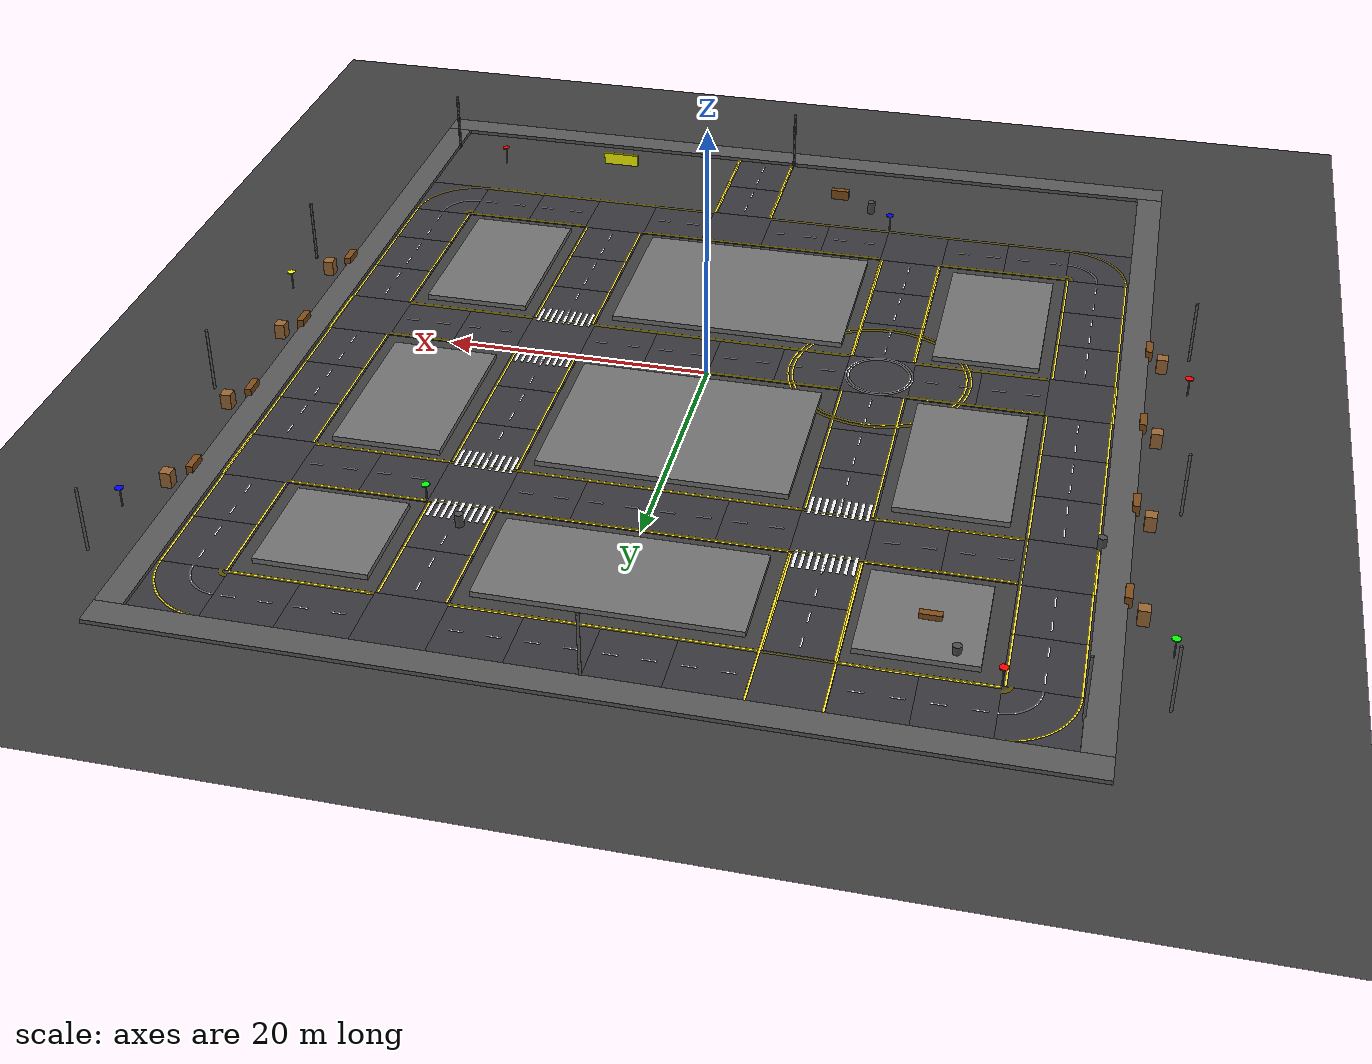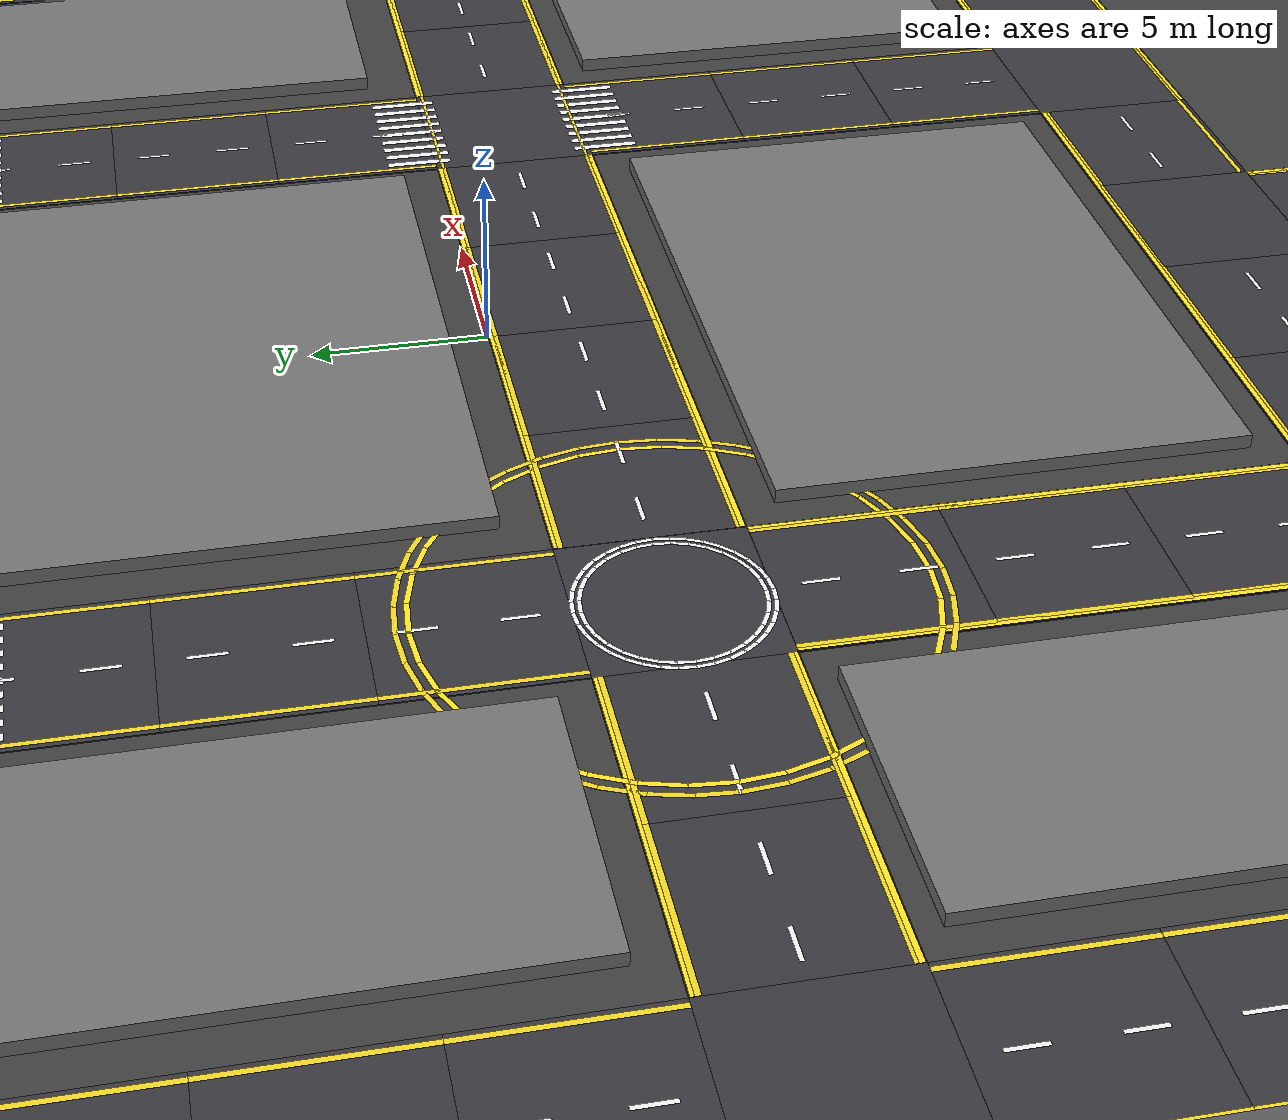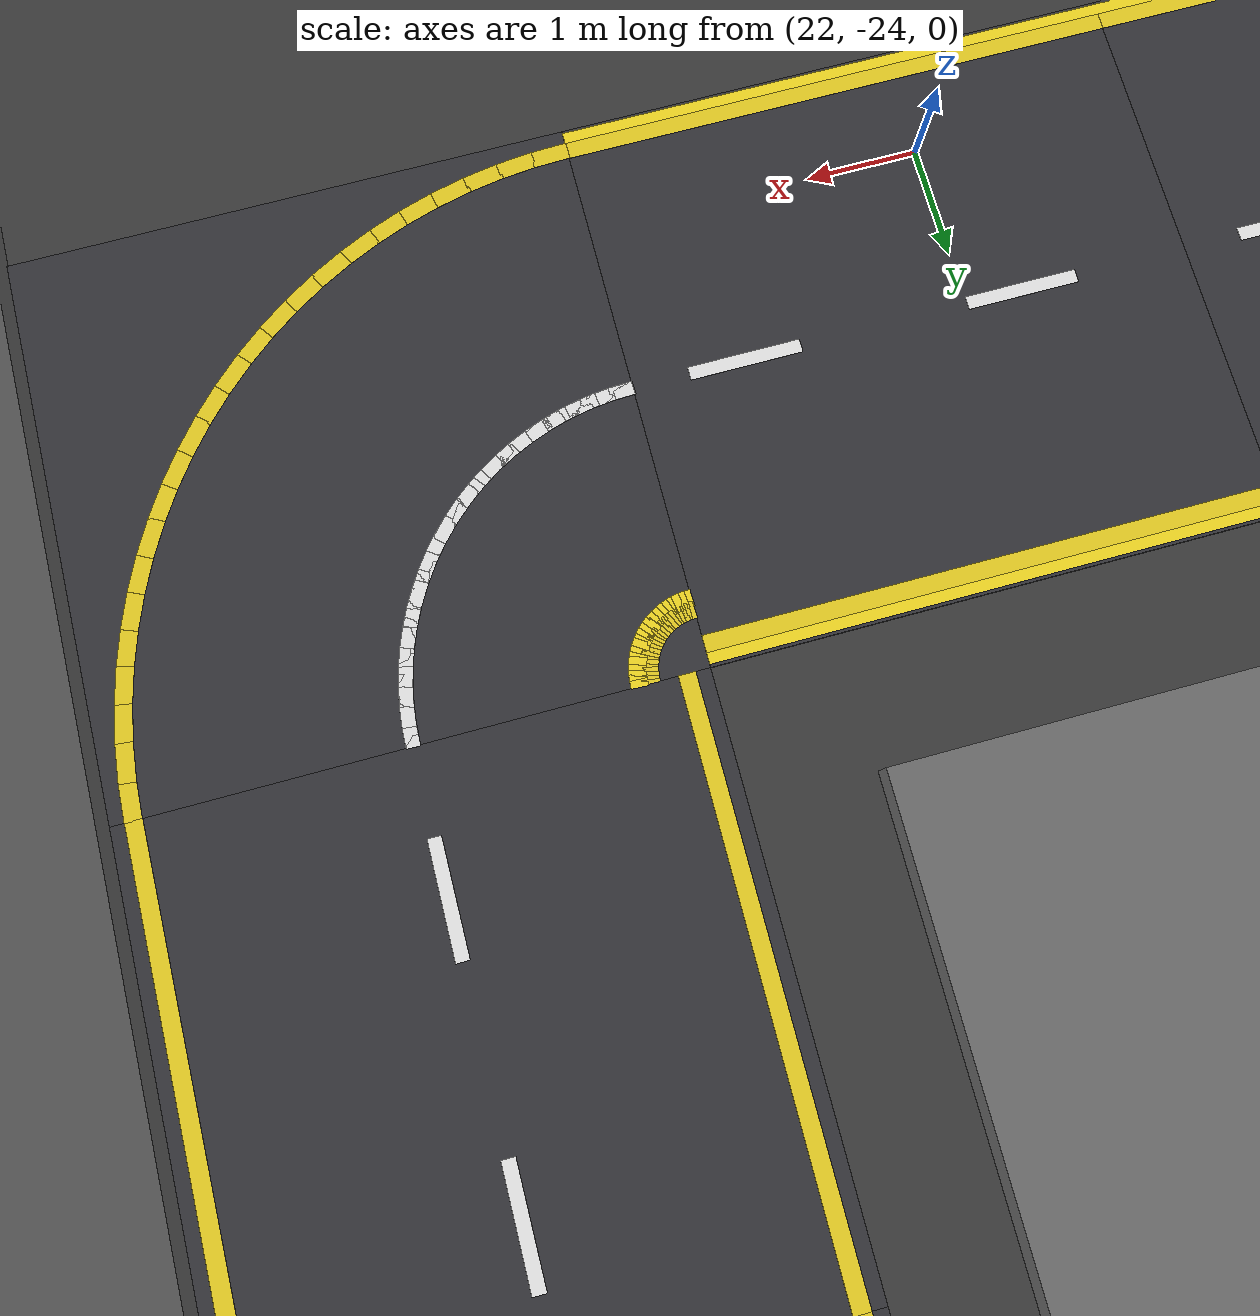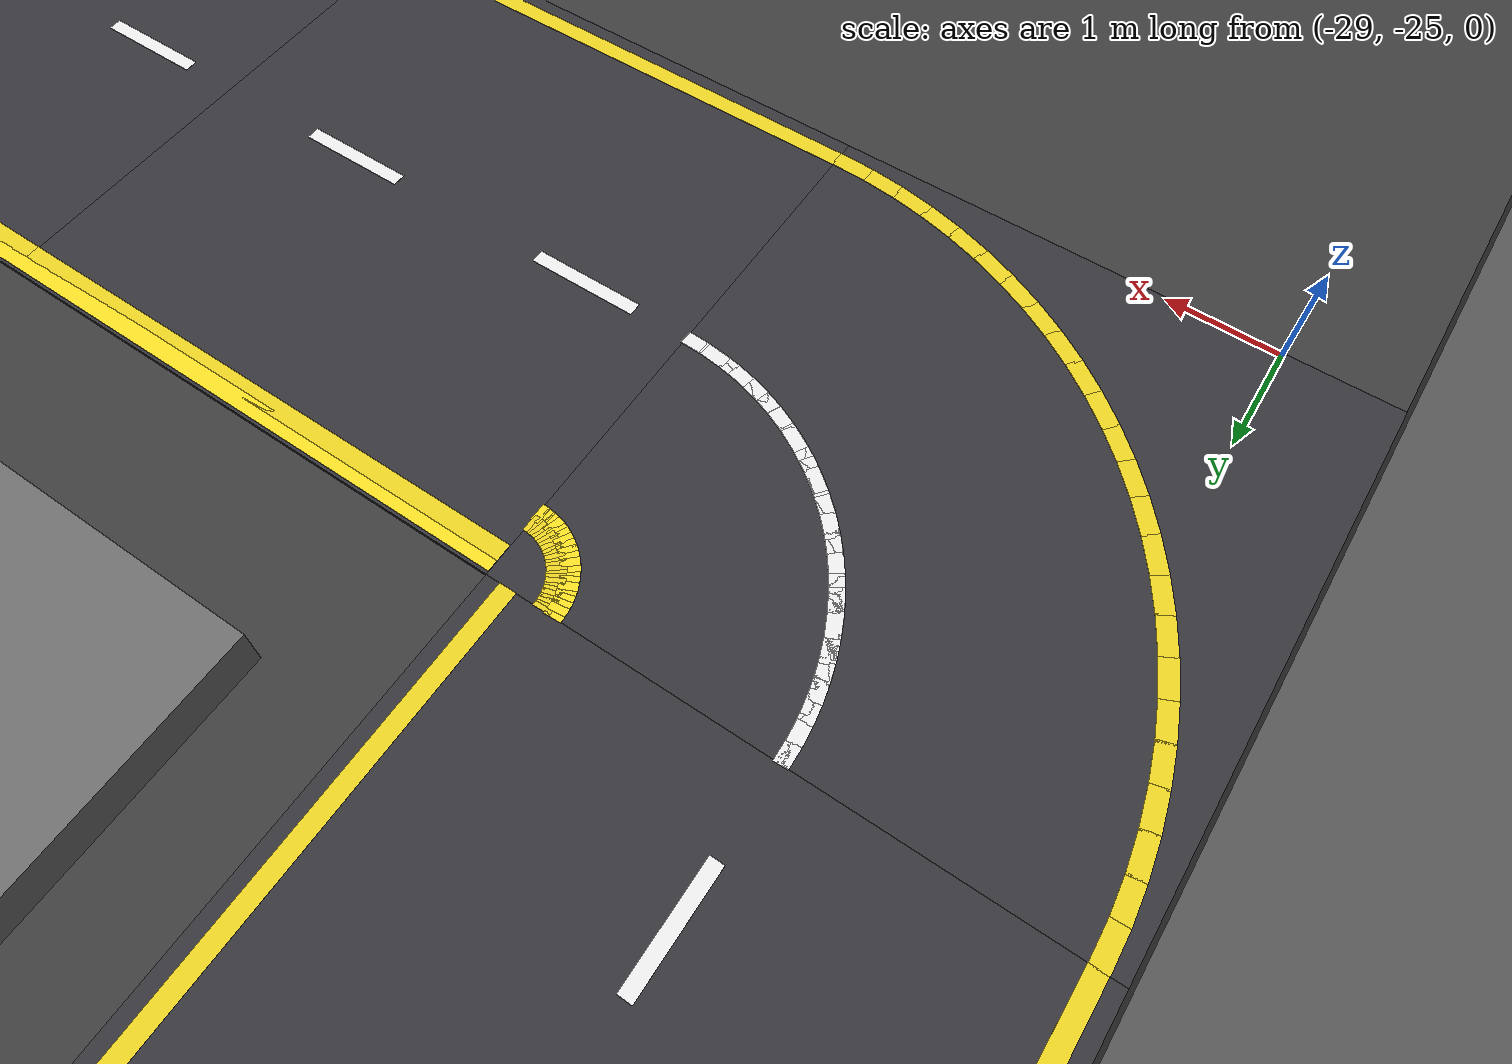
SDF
<sdf version="1.7">
 <world name="compact_city">
  <plugin name="auto_traffic_light" filename="libauto_traffic_light_plugin.so">
   <log_messages>1</log_messages>
  </plugin>
  <scene>
   <grid>0</grid>
   <origin_visual>0</origin_visual>
   <ambient>0.592 0.624 0.635 1</ambient>
   <sky><clouds><speed>12</speed></clouds></sky>
   <background>0.35 0.35 0.35 1</background>
   <shadows>1</shadows>
  </scene>
  <physics name="default_physics" default="0" type="ode">
   <max_step_size>0.001</max_step_size>
   <real_time_factor>1</real_time_factor>
   <real_time_update_rate>1000</real_time_update_rate>
  </physics>
  <spherical_coordinates>
   <surface_model>EARTH_WGS84</surface_model>
   <latitude_deg>0</latitude_deg>
   <longitude_deg>0</longitude_deg>
   <elevation>0</elevation>
   <heading_deg>0</heading_deg>
  </spherical_coordinates>
  <light name="sun" type="directional">
   <pose>0 0 1000 0 -0 0</pose>
   <diffuse>0.8 0.8 0.8 1</diffuse>
   <specular>0.5 0.5 0.5 1</specular>
   <attenuation>
    <range>1000</range>
    <constant>0.9</constant>
    <linear>0.01</linear>
    <quadratic>0.001</quadratic>
   </attenuation>
   <direction>-0.5 0.1 -0.4</direction>
   <spot><inner_angle>0</inner_angle><outer_angle>0</outer_angle><falloff>0</falloff></spot>
  </light>
  <model name="ground_plane">
   <static>1</static>
   <pose>0 0 0.01 0 -0 0</pose>
   <link name="link">
    <collision name="collision">
     <geometry><plane><normal>0 0 1</normal><size>200 200</size></plane></geometry>
    </collision>
    <visual name="visual">
     <geometry><plane><normal>0 0 1</normal><size>200 200</size></plane></geometry>
     <material>
      <ambient>0.2 0.2 0.2 1</ambient>
      <diffuse>0.25 0.25 0.25 1</diffuse>
      <specular>0.1 0.1 0.1 1</specular>
     </material>
    </visual>
   </link>
  </model>
  <model name="road_tile_1">
   <static>1</static>
   <pose>-27.4902 32.484 0.015 0 -0 0</pose>
   <link name="link">
    <collision name="collision"><geometry><box><size>5 5 0.03</size></box></geometry></collision>
    <visual name="visual">
     <geometry><box><size>5 5 0.03</size></box></geometry>
     <material>
      <ambient>0.18 0.18 0.2 1</ambient>
      <diffuse>0.22 0.22 0.24 1</diffuse>
      <specular>0.1 0.1 0.1 1</specular>
     </material>
    </visual>
   </link>
  </model>
  <model name="road_tile_2">
   <static>1</static>
   <pose>-22.5 32.5 0.015 0 -0 0</pose>
   <link name="link">
    <collision name="collision"><geometry><box><size>5 5 0.03</size></box></geometry></collision>
    <visual name="visual">
     <geometry><box><size>5 5 0.03</size></box></geometry>
     <material>
      <ambient>0.18 0.18 0.2 1</ambient>
      <diffuse>0.22 0.22 0.24 1</diffuse>
      <specular>0.1 0.1 0.1 1</specular>
     </material>
    </visual>
   </link>
  </model>
  <model name="road_tile_3">
   <static>1</static>
   <pose>-17.5 32.5 0.015 0 -0 0</pose>
   <link name="link">
    <collision name="collision"><geometry><box><size>5 5 0.03</size></box></geometry></collision>
    <visual name="visual">
     <geometry><box><size>5 5 0.03</size></box></geometry>
     <material>
      <ambient>0.18 0.18 0.2 1</ambient>
      <diffuse>0.22 0.22 0.24 1</diffuse>
      <specular>0.1 0.1 0.1 1</specular>
     </material>
    </visual>
   </link>
  </model>
  <model name="road_tile_4">
   <static>1</static>
   <pose>-12.5 32.5 0.015 0 -0 0</pose>
   <link name="link">
    <collision name="collision"><geometry><box><size>5 5 0.03</size></box></geometry></collision>
    <visual name="visual">
     <geometry><box><size>5 5 0.03</size></box></geometry>
     <material>
      <ambient>0.18 0.18 0.2 1</ambient>
      <diffuse>0.22 0.22 0.24 1</diffuse>
      <specular>0.1 0.1 0.1 1</specular>
     </material>
    </visual>
   </link>
  </model>
  <model name="road_tile_5">
   <static>1</static>
   <pose>-7.5 32.5 0.015 0 -0 0</pose>
   <link name="link">
    <collision name="collision"><geometry><box><size>5 5 0.03</size></box></geometry></collision>
    <visual name="visual">
     <geometry><box><size>5 5 0.03</size></box></geometry>
     <material>
      <ambient>0.18 0.18 0.2 1</ambient>
      <diffuse>0.22 0.22 0.24 1</diffuse>
      <specular>0.1 0.1 0.1 1</specular>
     </material>
    </visual>
   </link>
  </model>
  <model name="road_tile_6">
   <static>1</static>
   <pose>-2.5 32.5 0.015 0 -0 0</pose>
   <link name="link">
    <collision name="collision"><geometry><box><size>5 5 0.03</size></box></geometry></collision>
    <visual name="visual">
     <geometry><box><size>5 5 0.03</size></box></geometry>
     <material>
      <ambient>0.18 0.18 0.2 1</ambient>
      <diffuse>0.22 0.22 0.24 1</diffuse>
      <specular>0.1 0.1 0.1 1</specular>
     </material>
    </visual>
   </link>
  </model>
  <model name="road_tile_7">
   <static>1</static>
   <pose>2.5 32.5 0.015 0 -0 0</pose>
   <link name="link">
    <collision name="collision"><geometry><box><size>5 5 0.03</size></box></geometry></collision>
    <visual name="visual">
     <geometry><box><size>5 5 0.03</size></box></geometry>
     <material>
      <ambient>0.18 0.18 0.2 1</ambient>
      <diffuse>0.22 0.22 0.24 1</diffuse>
      <specular>0.1 0.1 0.1 1</specular>
     </material>
    </visual>
   </link>
  </model>
  <model name="road_tile_8">
   <static>1</static>
   <pose>7.5 32.5 0.015 0 -0 0</pose>
   <link name="link">
    <collision name="collision"><geometry><box><size>5 5 0.03</size></box></geometry></collision>
    <visual name="visual">
     <geometry><box><size>5 5 0.03</size></box></geometry>
     <material>
      <ambient>0.18 0.18 0.2 1</ambient>
      <diffuse>0.22 0.22 0.24 1</diffuse>
      <specular>0.1 0.1 0.1 1</specular>
     </material>
    </visual>
   </link>
  </model>
  <model name="road_tile_9">
   <static>1</static>
   <pose>12.5 32.5 0.015 0 -0 0</pose>
   <link name="link">
    <collision name="collision"><geometry><box><size>5 5 0.03</size></box></geometry></collision>
    <visual name="visual">
     <geometry><box><size>5 5 0.03</size></box></geometry>
     <material>
      <ambient>0.18 0.18 0.2 1</ambient>
      <diffuse>0.22 0.22 0.24 1</diffuse>
      <specular>0.1 0.1 0.1 1</specular>
     </material>
    </visual>
   </link>
  </model>
  <model name="road_tile_10">
   <static>1</static>
   <pose>17.5 32.5 0.015 0 -0 0</pose>
   <link name="link">
    <collision name="collision"><geometry><box><size>5 5 0.03</size></box></geometry></collision>
    <visual name="visual">
     <geometry><box><size>5 5 0.03</size></box></geometry>
     <material>
      <ambient>0.18 0.18 0.2 1</ambient>
      <diffuse>0.22 0.22 0.24 1</diffuse>
      <specular>0.1 0.1 0.1 1</specular>
     </material>
    </visual>
   </link>
  </model>
  <model name="road_tile_11">
   <static>1</static>
   <pose>22.5 32.5 0.015 0 -0 0</pose>
   <link name="link">
    <collision name="collision"><geometry><box><size>5 5 0.03</size></box></geometry></collision>
    <visual name="visual">
     <geometry><box><size>5 5 0.03</size></box></geometry>
     <material>
      <ambient>0.18 0.18 0.2 1</ambient>
      <diffuse>0.22 0.22 0.24 1</diffuse>
      <specular>0.1 0.1 0.1 1</specular>
     </material>
    </visual>
   </link>
  </model>
  <model name="road_tile_12">
   <static>1</static>
   <pose>27.5 32.5 0.015 0 -0 0</pose>
   <link name="link">
    <collision name="collision"><geometry><box><size>5 5 0.03</size></box></geometry></collision>
    <visual name="visual">
     <geometry><box><size>5 5 0.03</size></box></geometry>
     <material>
      <ambient>0.18 0.18 0.2 1</ambient>
      <diffuse>0.22 0.22 0.24 1</diffuse>
      <specular>0.1 0.1 0.1 1</specular>
     </material>
    </visual>
   </link>
  </model>
  <model name="road_tile_13">
   <static>1</static>
   <pose>-27.5 27.5 0.015 0 -0 1.5708</pose>
   <link name="link">
    <collision name="collision"><geometry><box><size>5 5 0.03</size></box></geometry></collision>
    <visual name="visual">
     <geometry><box><size>5 5 0.03</size></box></geometry>
     <material>
      <ambient>0.18 0.18 0.2 1</ambient>
      <diffuse>0.22 0.22 0.24 1</diffuse>
      <specular>0.1 0.1 0.1 1</specular>
     </material>
    </visual>
   </link>
  </model>
  <model name="road_tile_14">
   <static>1</static>
   <pose>-12.5 27.5 0.015 0 -0 1.5708</pose>
   <link name="link">
    <collision name="collision"><geometry><box><size>5 5 0.03</size></box></geometry></collision>
    <visual name="visual">
     <geometry><box><size>5 5 0.03</size></box></geometry>
     <material>
      <ambient>0.18 0.18 0.2 1</ambient>
      <diffuse>0.22 0.22 0.24 1</diffuse>
      <specular>0.1 0.1 0.1 1</specular>
     </material>
    </visual>
   </link>
  </model>
  <model name="road_tile_15">
   <static>1</static>
   <pose>12.5 27.5 0.015 0 -0 1.5708</pose>
   <link name="link">
    <collision name="collision"><geometry><box><size>5 5 0.03</size></box></geometry></collision>
    <visual name="visual">
     <geometry><box><size>5 5 0.03</size></box></geometry>
     <material>
      <ambient>0.18 0.18 0.2 1</ambient>
      <diffuse>0.22 0.22 0.24 1</diffuse>
      <specular>0.1 0.1 0.1 1</specular>
     </material>
    </visual>
   </link>
  </model>
  <model name="road_tile_16">
   <static>1</static>
   <pose>27.5 27.5 0.015 0 -0 1.5708</pose>
   <link name="link">
    <collision name="collision"><geometry><box><size>5 5 0.03</size></box></geometry></collision>
    <visual name="visual">
     <geometry><box><size>5 5 0.03</size></box></geometry>
     <material>
      <ambient>0.18 0.18 0.2 1</ambient>
      <diffuse>0.22 0.22 0.24 1</diffuse>
      <specular>0.1 0.1 0.1 1</specular>
     </material>
    </visual>
   </link>
  </model>
  <model name="road_tile_17">
   <static>1</static>
   <pose>-27.5 22.5 0.015 0 -0 1.5708</pose>
   <link name="link">
    <collision name="collision"><geometry><box><size>5 5 0.03</size></box></geometry></collision>
    <visual name="visual">
     <geometry><box><size>5 5 0.03</size></box></geometry>
     <material>
      <ambient>0.18 0.18 0.2 1</ambient>
      <diffuse>0.22 0.22 0.24 1</diffuse>
      <specular>0.1 0.1 0.1 1</specular>
     </material>
    </visual>
   </link>
  </model>
  <model name="road_tile_18">
   <static>1</static>
   <pose>-12.5 22.5 0.015 0 -0 1.5708</pose>
   <link name="link">
    <collision name="collision"><geometry><box><size>5 5 0.03</size></box></geometry></collision>
    <visual name="visual">
     <geometry><box><size>5 5 0.03</size></box></geometry>
     <material>
      <ambient>0.18 0.18 0.2 1</ambient>
      <diffuse>0.22 0.22 0.24 1</diffuse>
      <specular>0.1 0.1 0.1 1</specular>
     </material>
    </visual>
   </link>
  </model>
  <model name="road_tile_19">
   <static>1</static>
   <pose>12.5 22.5 0.015 0 -0 1.5708</pose>
   <link name="link">
    <collision name="collision"><geometry><box><size>5 5 0.03</size></box></geometry></collision>
    <visual name="visual">
     <geometry><box><size>5 5 0.03</size></box></geometry>
     <material>
      <ambient>0.18 0.18 0.2 1</ambient>
      <diffuse>0.22 0.22 0.24 1</diffuse>
      <specular>0.1 0.1 0.1 1</specular>
     </material>
    </visual>
   </link>
  </model>
  <model name="road_tile_20">
   <static>1</static>
   <pose>27.5 22.5 0.015 0 -0 1.5708</pose>
   <link name="link">
    <collision name="collision"><geometry><box><size>5 5 0.03</size></box></geometry></collision>
    <visual name="visual">
     <geometry><box><size>5 5 0.03</size></box></geometry>
     <material>
      <ambient>0.18 0.18 0.2 1</ambient>
      <diffuse>0.22 0.22 0.24 1</diffuse>
      <specular>0.1 0.1 0.1 1</specular>
     </material>
    </visual>
   </link>
  </model>
  <model name="road_tile_21">
   <static>1</static>
   <pose>-27.5 17.5 0.015 0 -0 0</pose>
   <link name="link">
    <collision name="collision"><geometry><box><size>5 5 0.03</size></box></geometry></collision>
    <visual name="visual">
     <geometry><box><size>5 5 0.03</size></box></geometry>
     <material>
      <ambient>0.18 0.18 0.2 1</ambient>
      <diffuse>0.22 0.22 0.24 1</diffuse>
      <specular>0.1 0.1 0.1 1</specular>
     </material>
    </visual>
   </link>
  </model>
  <model name="road_tile_22">
   <static>1</static>
   <pose>-22.5 17.5 0.015 0 -0 0</pose>
   <link name="link">
    <collision name="collision"><geometry><box><size>5 5 0.03</size></box></geometry></collision>
    <visual name="visual">
     <geometry><box><size>5 5 0.03</size></box></geometry>
     <material>
      <ambient>0.18 0.18 0.2 1</ambient>
      <diffuse>0.22 0.22 0.24 1</diffuse>
      <specular>0.1 0.1 0.1 1</specular>
     </material>
    </visual>
   </link>
  </model>
  <model name="road_tile_23">
   <static>1</static>
   <pose>-17.5 17.5 0.015 0 -0 0</pose>
   <link name="link">
    <collision name="collision"><geometry><box><size>5 5 0.03</size></box></geometry></collision>
    <visual name="visual">
     <geometry><box><size>5 5 0.03</size></box></geometry>
     <material>
      <ambient>0.18 0.18 0.2 1</ambient>
      <diffuse>0.22 0.22 0.24 1</diffuse>
      <specular>0.1 0.1 0.1 1</specular>
     </material>
    </visual>
   </link>
  </model>
  <model name="road_tile_24">
   <static>1</static>
   <pose>-12.5 17.5 0.015 0 -0 0</pose>
   <link name="link">
    <collision name="collision"><geometry><box><size>5 5 0.03</size></box></geometry></collision>
    <visual name="visual">
     <geometry><box><size>5 5 0.03</size></box></geometry>
     <material>
      <ambient>0.18 0.18 0.2 1</ambient>
      <diffuse>0.22 0.22 0.24 1</diffuse>
      <specular>0.1 0.1 0.1 1</specular>
     </material>
    </visual>
   </link>
  </model>
  <model name="road_tile_25">
   <static>1</static>
   <pose>-7.5 17.5 0.015 0 -0 0</pose>
   <link name="link">
    <collision name="collision"><geometry><box><size>5 5 0.03</size></box></geometry></collision>
    <visual name="visual">
     <geometry><box><size>5 5 0.03</size></box></geometry>
     <material>
      <ambient>0.18 0.18 0.2 1</ambient>
      <diffuse>0.22 0.22 0.24 1</diffuse>
      <specular>0.1 0.1 0.1 1</specular>
     </material>
    </visual>
   </link>
  </model>
  <model name="road_tile_26">
   <static>1</static>
   <pose>-2.5 17.5 0.015 0 -0 0</pose>
   <link name="link">
    <collision name="collision"><geometry><box><size>5 5 0.03</size></box></geometry></collision>
    <visual name="visual">
     <geometry><box><size>5 5 0.03</size></box></geometry>
     <material>
      <ambient>0.18 0.18 0.2 1</ambient>
      <diffuse>0.22 0.22 0.24 1</diffuse>
      <specular>0.1 0.1 0.1 1</specular>
     </material>
    </visual>
   </link>
  </model>
  <model name="road_tile_27">
   <static>1</static>
   <pose>2.5 17.5 0.015 0 -0 0</pose>
   <link name="link">
    <collision name="collision"><geometry><box><size>5 5 0.03</size></box></geometry></collision>
    <visual name="visual">
     <geometry><box><size>5 5 0.03</size></box></geometry>
     <material>
      <ambient>0.18 0.18 0.2 1</ambient>
      <diffuse>0.22 0.22 0.24 1</diffuse>
      <specular>0.1 0.1 0.1 1</specular>
     </material>
    </visual>
   </link>
  </model>
  <model name="road_tile_28">
   <static>1</static>
   <pose>7.5 17.5 0.015 0 -0 0</pose>
   <link name="link">
    <collision name="collision"><geometry><box><size>5 5 0.03</size></box></geometry></collision>
    <visual name="visual">
     <geometry><box><size>5 5 0.03</size></box></geometry>
     <material>
      <ambient>0.18 0.18 0.2 1</ambient>
      <diffuse>0.22 0.22 0.24 1</diffuse>
      <specular>0.1 0.1 0.1 1</specular>
     </material>
    </visual>
   </link>
  </model>
  <model name="road_tile_29">
   <static>1</static>
   <pose>12.5 17.5 0.015 0 -0 0</pose>
   <link name="link">
    <collision name="collision"><geometry><box><size>5 5 0.03</size></box></geometry></collision>
    <visual name="visual">
     <geometry><box><size>5 5 0.03</size></box></geometry>
     <material>
      <ambient>0.18 0.18 0.2 1</ambient>
      <diffuse>0.22 0.22 0.24 1</diffuse>
      <specular>0.1 0.1 0.1 1</specular>
     </material>
    </visual>
   </link>
  </model>
  <model name="road_tile_30">
   <static>1</static>
   <pose>17.5 17.5 0.015 0 -0 0</pose>
   <link name="link">
    <collision name="collision"><geometry><box><size>5 5 0.03</size></box></geometry></collision>
    <visual name="visual">
     <geometry><box><size>5 5 0.03</size></box></geometry>
     <material>
      <ambient>0.18 0.18 0.2 1</ambient>
      <diffuse>0.22 0.22 0.24 1</diffuse>
      <specular>0.1 0.1 0.1 1</specular>
     </material>
    </visual>
   </link>
  </model>
  <model name="road_tile_31">
   <static>1</static>
   <pose>22.5 17.5 0.015 0 -0 0</pose>
   <link name="link">
    <collision name="collision"><geometry><box><size>5 5 0.03</size></box></geometry></collision>
    <visual name="visual">
     <geometry><box><size>5 5 0.03</size></box></geometry>
     <material>
      <ambient>0.18 0.18 0.2 1</ambient>
      <diffuse>0.22 0.22 0.24 1</diffuse>
      <specular>0.1 0.1 0.1 1</specular>
     </material>
    </visual>
   </link>
  </model>
  <model name="road_tile_32">
   <static>1</static>
   <pose>27.5 17.5 0.015 0 -0 0</pose>
   <link name="link">
    <collision name="collision"><geometry><box><size>5 5 0.03</size></box></geometry></collision>
    <visual name="visual">
     <geometry><box><size>5 5 0.03</size></box></geometry>
     <material>
      <ambient>0.18 0.18 0.2 1</ambient>
      <diffuse>0.22 0.22 0.24 1</diffuse>
      <specular>0.1 0.1 0.1 1</specular>
     </material>
    </visual>
   </link>
  </model>
  <model name="road_tile_33">
   <static>1</static>
   <pose>-27.5 12.5 0.015 0 -0 1.5708</pose>
   <link name="link">
    <collision name="collision"><geometry><box><size>5 5 0.03</size></box></geometry></collision>
    <visual name="visual">
     <geometry><box><size>5 5 0.03</size></box></geometry>
     <material>
      <ambient>0.18 0.18 0.2 1</ambient>
      <diffuse>0.22 0.22 0.24 1</diffuse>
      <specular>0.1 0.1 0.1 1</specular>
     </material>
    </visual>
   </link>
  </model>
  <model name="road_tile_34">
   <static>1</static>
   <pose>-12.5 12.5 0.015 0 -0 1.5708</pose>
   <link name="link">
    <collision name="collision"><geometry><box><size>5 5 0.03</size></box></geometry></collision>
    <visual name="visual">
     <geometry><box><size>5 5 0.03</size></box></geometry>
     <material>
      <ambient>0.18 0.18 0.2 1</ambient>
      <diffuse>0.22 0.22 0.24 1</diffuse>
      <specular>0.1 0.1 0.1 1</specular>
     </material>
    </visual>
   </link>
  </model>
  <model name="road_tile_35">
   <static>1</static>
   <pose>12.5 12.5 0.015 0 -0 1.5708</pose>
   <link name="link">
    <collision name="collision"><geometry><box><size>5 5 0.03</size></box></geometry></collision>
    <visual name="visual">
     <geometry><box><size>5 5 0.03</size></box></geometry>
     <material>
      <ambient>0.18 0.18 0.2 1</ambient>
      <diffuse>0.22 0.22 0.24 1</diffuse>
      <specular>0.1 0.1 0.1 1</specular>
     </material>
    </visual>
   </link>
  </model>
  <model name="road_tile_36">
   <static>1</static>
   <pose>27.5 12.5 0.015 0 -0 1.5708</pose>
   <link name="link">
    <collision name="collision"><geometry><box><size>5 5 0.03</size></box></geometry></collision>
    <visual name="visual">
     <geometry><box><size>5 5 0.03</size></box></geometry>
     <material>
      <ambient>0.18 0.18 0.2 1</ambient>
      <diffuse>0.22 0.22 0.24 1</diffuse>
      <specular>0.1 0.1 0.1 1</specular>
     </material>
    </visual>
   </link>
  </model>
  <model name="road_tile_37">
   <static>1</static>
   <pose>-27.5 7.5 0.015 0 -0 1.5708</pose>
   <link name="link">
    <collision name="collision"><geometry><box><size>5 5 0.03</size></box></geometry></collision>
    <visual name="visual">
     <geometry><box><size>5 5 0.03</size></box></geometry>
     <material>
      <ambient>0.18 0.18 0.2 1</ambient>
      <diffuse>0.22 0.22 0.24 1</diffuse>
      <specular>0.1 0.1 0.1 1</specular>
     </material>
    </visual>
   </link>
  </model>
  <model name="road_tile_38">
   <static>1</static>
   <pose>-12.5 7.5 0.015 0 -0 1.5708</pose>
   <link name="link">
    <collision name="collision"><geometry><box><size>5 5 0.03</size></box></geometry></collision>
    <visual name="visual">
     <geometry><box><size>5 5 0.03</size></box></geometry>
     <material>
      <ambient>0.18 0.18 0.2 1</ambient>
      <diffuse>0.22 0.22 0.24 1</diffuse>
      <specular>0.1 0.1 0.1 1</specular>
     </material>
    </visual>
   </link>
  </model>
  <model name="road_tile_39">
   <static>1</static>
   <pose>12.5 7.5 0.015 0 -0 1.5708</pose>
   <link name="link">
    <collision name="collision"><geometry><box><size>5 5 0.03</size></box></geometry></collision>
    <visual name="visual">
     <geometry><box><size>5 5 0.03</size></box></geometry>
     <material>
      <ambient>0.18 0.18 0.2 1</ambient>
      <diffuse>0.22 0.22 0.24 1</diffuse>
      <specular>0.1 0.1 0.1 1</specular>
     </material>
    </visual>
   </link>
  </model>
  <model name="road_tile_40">
   <static>1</static>
   <pose>27.5 7.5 0.015 0 -0 1.5708</pose>
   <link name="link">
    <collision name="collision"><geometry><box><size>5 5 0.03</size></box></geometry></collision>
    <visual name="visual">
     <geometry><box><size>5 5 0.03</size></box></geometry>
     <material>
      <ambient>0.18 0.18 0.2 1</ambient>
      <diffuse>0.22 0.22 0.24 1</diffuse>
      <specular>0.1 0.1 0.1 1</specular>
     </material>
    </visual>
   </link>
  </model>
  <model name="road_tile_41">
   <static>1</static>
   <pose>-27.5 2.5 0.015 0 -0 1.5708</pose>
   <link name="link">
    <collision name="collision"><geometry><box><size>5 5 0.03</size></box></geometry></collision>
    <visual name="visual">
     <geometry><box><size>5 5 0.03</size></box></geometry>
     <material>
      <ambient>0.18 0.18 0.2 1</ambient>
      <diffuse>0.22 0.22 0.24 1</diffuse>
      <specular>0.1 0.1 0.1 1</specular>
     </material>
    </visual>
   </link>
  </model>
  <model name="road_tile_42">
   <static>1</static>
   <pose>-12.5 2.5 0.015 0 -0 1.5708</pose>
   <link name="link">
    <collision name="collision"><geometry><box><size>5 5 0.03</size></box></geometry></collision>
    <visual name="visual">
     <geometry><box><size>5 5 0.03</size></box></geometry>
     <material>
      <ambient>0.18 0.18 0.2 1</ambient>
      <diffuse>0.22 0.22 0.24 1</diffuse>
      <specular>0.1 0.1 0.1 1</specular>
     </material>
    </visual>
   </link>
  </model>
  <model name="road_tile_43">
   <static>1</static>
   <pose>12.5 2.5 0.015 0 -0 1.5708</pose>
   <link name="link">
    <collision name="collision"><geometry><box><size>5 5 0.03</size></box></geometry></collision>
    <visual name="visual">
     <geometry><box><size>5 5 0.03</size></box></geometry>
     <material>
      <ambient>0.18 0.18 0.2 1</ambient>
      <diffuse>0.22 0.22 0.24 1</diffuse>
      <specular>0.1 0.1 0.1 1</specular>
     </material>
    </visual>
   </link>
  </model>
  <model name="road_tile_44">
   <static>1</static>
   <pose>27.5 2.5 0.015 0 -0 1.5708</pose>
   <link name="link">
    <collision name="collision"><geometry><box><size>5 5 0.03</size></box></geometry></collision>
    <visual name="visual">
     <geometry><box><size>5 5 0.03</size></box></geometry>
     <material>
      <ambient>0.18 0.18 0.2 1</ambient>
      <diffuse>0.22 0.22 0.24 1</diffuse>
      <specular>0.1 0.1 0.1 1</specular>
     </material>
    </visual>
   </link>
  </model>
  <model name="road_tile_45">
   <static>1</static>
   <pose>-27.5 -2.5 0.015 0 -0 0</pose>
   <link name="link">
    <collision name="collision"><geometry><box><size>5 5 0.03</size></box></geometry></collision>
    <visual name="visual">
     <geometry><box><size>5 5 0.03</size></box></geometry>
     <material>
      <ambient>0.18 0.18 0.2 1</ambient>
      <diffuse>0.22 0.22 0.24 1</diffuse>
      <specular>0.1 0.1 0.1 1</specular>
     </material>
    </visual>
   </link>
  </model>
  <model name="road_tile_46">
   <static>1</static>
   <pose>-22.5 -2.5 0.015 0 -0 0</pose>
   <link name="link">
    <collision name="collision"><geometry><box><size>5 5 0.03</size></box></geometry></collision>
    <visual name="visual">
     <geometry><box><size>5 5 0.03</size></box></geometry>
     <material>
      <ambient>0.18 0.18 0.2 1</ambient>
      <diffuse>0.22 0.22 0.24 1</diffuse>
      <specular>0.1 0.1 0.1 1</specular>
     </material>
    </visual>
   </link>
  </model>
  <model name="road_tile_47">
   <static>1</static>
   <pose>-17.5 -2.5 0.015 0 -0 0</pose>
   <link name="link">
    <collision name="collision"><geometry><box><size>5 5 0.03</size></box></geometry></collision>
    <visual name="visual">
     <geometry><box><size>5 5 0.03</size></box></geometry>
     <material>
      <ambient>0.18 0.18 0.2 1</ambient>
      <diffuse>0.22 0.22 0.24 1</diffuse>
      <specular>0.1 0.1 0.1 1</specular>
     </material>
    </visual>
   </link>
  </model>
  <model name="road_tile_48">
   <static>1</static>
   <pose>-7.5 -2.5 0.015 0 -0 0</pose>
   <link name="link">
    <collision name="collision"><geometry><box><size>5 5 0.03</size></box></geometry></collision>
    <visual name="visual">
     <geometry><box><size>5 5 0.03</size></box></geometry>
     <material>
      <ambient>0.18 0.18 0.2 1</ambient>
      <diffuse>0.22 0.22 0.24 1</diffuse>
      <specular>0.1 0.1 0.1 1</specular>
     </material>
    </visual>
   </link>
  </model>
  <model name="road_tile_49">
   <static>1</static>
   <pose>-2.5 -2.5 0.015 0 -0 0</pose>
   <link name="link">
    <collision name="collision"><geometry><box><size>5 5 0.03</size></box></geometry></collision>
    <visual name="visual">
     <geometry><box><size>5 5 0.03</size></box></geometry>
     <material>
      <ambient>0.18 0.18 0.2 1</ambient>
      <diffuse>0.22 0.22 0.24 1</diffuse>
      <specular>0.1 0.1 0.1 1</specular>
     </material>
    </visual>
   </link>
  </model>
  <model name="road_tile_50">
   <static>1</static>
   <pose>2.5 -2.5 0.015 0 -0 0</pose>
   <link name="link">
    <collision name="collision"><geometry><box><size>5 5 0.03</size></box></geometry></collision>
    <visual name="visual">
     <geometry><box><size>5 5 0.03</size></box></geometry>
     <material>
      <ambient>0.18 0.18 0.2 1</ambient>
      <diffuse>0.22 0.22 0.24 1</diffuse>
      <specular>0.1 0.1 0.1 1</specular>
     </material>
    </visual>
   </link>
  </model>
  <model name="road_tile_51">
   <static>1</static>
   <pose>7.5 -2.5 0.015 0 -0 0</pose>
   <link name="link">
    <collision name="collision"><geometry><box><size>5 5 0.03</size></box></geometry></collision>
    <visual name="visual">
     <geometry><box><size>5 5 0.03</size></box></geometry>
     <material>
      <ambient>0.18 0.18 0.2 1</ambient>
      <diffuse>0.22 0.22 0.24 1</diffuse>
      <specular>0.1 0.1 0.1 1</specular>
     </material>
    </visual>
   </link>
  </model>
  <model name="road_tile_52">
   <static>1</static>
   <pose>12.5 -2.5 0.015 0 -0 0</pose>
   <link name="link">
    <collision name="collision"><geometry><box><size>5 5 0.03</size></box></geometry></collision>
    <visual name="visual">
     <geometry><box><size>5 5 0.03</size></box></geometry>
     <material>
      <ambient>0.18 0.18 0.2 1</ambient>
      <diffuse>0.22 0.22 0.24 1</diffuse>
      <specular>0.1 0.1 0.1 1</specular>
     </material>
    </visual>
   </link>
  </model>
  <model name="road_tile_53">
   <static>1</static>
   <pose>17.5 -2.5 0.015 0 -0 0</pose>
   <link name="link">
    <collision name="collision"><geometry><box><size>5 5 0.03</size></box></geometry></collision>
    <visual name="visual">
     <geometry><box><size>5 5 0.03</size></box></geometry>
     <material>
      <ambient>0.18 0.18 0.2 1</ambient>
      <diffuse>0.22 0.22 0.24 1</diffuse>
      <specular>0.1 0.1 0.1 1</specular>
     </material>
    </visual>
   </link>
  </model>
  <model name="road_tile_54">
   <static>1</static>
   <pose>22.5 -2.5 0.015 0 -0 0</pose>
   <link name="link">
    <collision name="collision"><geometry><box><size>5 5 0.03</size></box></geometry></collision>
    <visual name="visual">
     <geometry><box><size>5 5 0.03</size></box></geometry>
     <material>
      <ambient>0.18 0.18 0.2 1</ambient>
      <diffuse>0.22 0.22 0.24 1</diffuse>
      <specular>0.1 0.1 0.1 1</specular>
     </material>
    </visual>
   </link>
  </model>
  <model name="road_tile_55">
   <static>1</static>
   <pose>27.5 -2.5 0.015 0 -0 0</pose>
   <link name="link">
    <collision name="collision"><geometry><box><size>5 5 0.03</size></box></geometry></collision>
    <visual name="visual">
     <geometry><box><size>5 5 0.03</size></box></geometry>
     <material>
      <ambient>0.18 0.18 0.2 1</ambient>
      <diffuse>0.22 0.22 0.24 1</diffuse>
      <specular>0.1 0.1 0.1 1</specular>
     </material>
    </visual>
   </link>
  </model>
  <model name="road_tile_56">
   <static>1</static>
   <pose>-27.5 -7.5 0.015 0 -0 1.5708</pose>
   <link name="link">
    <collision name="collision"><geometry><box><size>5 5 0.03</size></box></geometry></collision>
    <visual name="visual">
     <geometry><box><size>5 5 0.03</size></box></geometry>
     <material>
      <ambient>0.18 0.18 0.2 1</ambient>
      <diffuse>0.22 0.22 0.24 1</diffuse>
      <specular>0.1 0.1 0.1 1</specular>
     </material>
    </visual>
   </link>
  </model>
  <model name="road_tile_57">
   <static>1</static>
   <pose>-12.5 -7.5 0.015 0 -0 1.5708</pose>
   <link name="link">
    <collision name="collision"><geometry><box><size>5 5 0.03</size></box></geometry></collision>
    <visual name="visual">
     <geometry><box><size>5 5 0.03</size></box></geometry>
     <material>
      <ambient>0.18 0.18 0.2 1</ambient>
      <diffuse>0.22 0.22 0.24 1</diffuse>
      <specular>0.1 0.1 0.1 1</specular>
     </material>
    </visual>
   </link>
  </model>
  <model name="road_tile_58">
   <static>1</static>
   <pose>12.5 -7.5 0.015 0 -0 1.5708</pose>
   <link name="link">
    <collision name="collision"><geometry><box><size>5 5 0.03</size></box></geometry></collision>
    <visual name="visual">
     <geometry><box><size>5 5 0.03</size></box></geometry>
     <material>
      <ambient>0.18 0.18 0.2 1</ambient>
      <diffuse>0.22 0.22 0.24 1</diffuse>
      <specular>0.1 0.1 0.1 1</specular>
     </material>
    </visual>
   </link>
  </model>
  <model name="road_tile_59">
   <static>1</static>
   <pose>27.5 -7.5 0.015 0 -0 1.5708</pose>
   <link name="link">
    <collision name="collision"><geometry><box><size>5 5 0.03</size></box></geometry></collision>
    <visual name="visual">
     <geometry><box><size>5 5 0.03</size></box></geometry>
     <material>
      <ambient>0.18 0.18 0.2 1</ambient>
      <diffuse>0.22 0.22 0.24 1</diffuse>
      <specular>0.1 0.1 0.1 1</specular>
     </material>
    </visual>
   </link>
  </model>
  <model name="road_tile_60">
   <static>1</static>
   <pose>-27.5 -12.5 0.015 0 -0 1.5708</pose>
   <link name="link">
    <collision name="collision"><geometry><box><size>5 5 0.03</size></box></geometry></collision>
    <visual name="visual">
     <geometry><box><size>5 5 0.03</size></box></geometry>
     <material>
      <ambient>0.18 0.18 0.2 1</ambient>
      <diffuse>0.22 0.22 0.24 1</diffuse>
      <specular>0.1 0.1 0.1 1</specular>
     </material>
    </visual>
   </link>
  </model>
  <model name="road_tile_61">
   <static>1</static>
   <pose>-12.5 -12.5 0.015 0 -0 1.5708</pose>
   <link name="link">
    <collision name="collision"><geometry><box><size>5 5 0.03</size></box></geometry></collision>
    <visual name="visual">
     <geometry><box><size>5 5 0.03</size></box></geometry>
     <material>
      <ambient>0.18 0.18 0.2 1</ambient>
      <diffuse>0.22 0.22 0.24 1</diffuse>
      <specular>0.1 0.1 0.1 1</specular>
     </material>
    </visual>
   </link>
  </model>
  <model name="road_tile_62">
   <static>1</static>
   <pose>12.5 -12.5 0.015 0 -0 1.5708</pose>
   <link name="link">
    <collision name="collision"><geometry><box><size>5 5 0.03</size></box></geometry></collision>
    <visual name="visual">
     <geometry><box><size>5 5 0.03</size></box></geometry>
     <material>
      <ambient>0.18 0.18 0.2 1</ambient>
      <diffuse>0.22 0.22 0.24 1</diffuse>
      <specular>0.1 0.1 0.1 1</specular>
     </material>
    </visual>
   </link>
  </model>
  <model name="road_tile_63">
   <static>1</static>
   <pose>27.5 -12.5 0.015 0 -0 1.5708</pose>
   <link name="link">
    <collision name="collision"><geometry><box><size>5 5 0.03</size></box></geometry></collision>
    <visual name="visual">
     <geometry><box><size>5 5 0.03</size></box></geometry>
     <material>
      <ambient>0.18 0.18 0.2 1</ambient>
      <diffuse>0.22 0.22 0.24 1</diffuse>
      <specular>0.1 0.1 0.1 1</specular>
     </material>
    </visual>
   </link>
  </model>
  <model name="road_tile_64">
   <static>1</static>
   <pose>-27.5 -17.5 0.015 0 -0 1.5708</pose>
   <link name="link">
    <collision name="collision"><geometry><box><size>5 5 0.03</size></box></geometry></collision>
    <visual name="visual">
     <geometry><box><size>5 5 0.03</size></box></geometry>
     <material>
      <ambient>0.18 0.18 0.2 1</ambient>
      <diffuse>0.22 0.22 0.24 1</diffuse>
      <specular>0.1 0.1 0.1 1</specular>
     </material>
    </visual>
   </link>
  </model>
  <model name="road_tile_65">
   <static>1</static>
   <pose>-12.5 -17.5 0.015 0 -0 1.5708</pose>
   <link name="link">
    <collision name="collision"><geometry><box><size>5 5 0.03</size></box></geometry></collision>
    <visual name="visual">
     <geometry><box><size>5 5 0.03</size></box></geometry>
     <material>
      <ambient>0.18 0.18 0.2 1</ambient>
      <diffuse>0.22 0.22 0.24 1</diffuse>
      <specular>0.1 0.1 0.1 1</specular>
     </material>
    </visual>
   </link>
  </model>
  <model name="road_tile_66">
   <static>1</static>
   <pose>12.5 -17.5 0.015 0 -0 1.5708</pose>
   <link name="link">
    <collision name="collision"><geometry><box><size>5 5 0.03</size></box></geometry></collision>
    <visual name="visual">
     <geometry><box><size>5 5 0.03</size></box></geometry>
     <material>
      <ambient>0.18 0.18 0.2 1</ambient>
      <diffuse>0.22 0.22 0.24 1</diffuse>
      <specular>0.1 0.1 0.1 1</specular>
     </material>
    </visual>
   </link>
  </model>
  <model name="road_tile_67">
   <static>1</static>
   <pose>27.5 -17.5 0.015 0 -0 1.5708</pose>
   <link name="link">
    <collision name="collision"><geometry><box><size>5 5 0.03</size></box></geometry></collision>
    <visual name="visual">
     <geometry><box><size>5 5 0.03</size></box></geometry>
     <material>
      <ambient>0.18 0.18 0.2 1</ambient>
      <diffuse>0.22 0.22 0.24 1</diffuse>
      <specular>0.1 0.1 0.1 1</specular>
     </material>
    </visual>
   </link>
  </model>
  <model name="road_tile_68">
   <static>1</static>
   <pose>-27.5 -22.5 0.015 0 -0 0</pose>
   <link name="link">
    <collision name="collision"><geometry><box><size>5 5 0.03</size></box></geometry></collision>
    <visual name="visual">
     <geometry><box><size>5 5 0.03</size></box></geometry>
     <material>
      <ambient>0.18 0.18 0.2 1</ambient>
      <diffuse>0.22 0.22 0.24 1</diffuse>
      <specular>0.1 0.1 0.1 1</specular>
     </material>
    </visual>
   </link>
  </model>
  <model name="road_tile_69">
   <static>1</static>
   <pose>-22.5 -22.5 0.015 0 -0 0</pose>
   <link name="link">
    <collision name="collision"><geometry><box><size>5 5 0.03</size></box></geometry></collision>
    <visual name="visual">
     <geometry><box><size>5 5 0.03</size></box></geometry>
     <material>
      <ambient>0.18 0.18 0.2 1</ambient>
      <diffuse>0.22 0.22 0.24 1</diffuse>
      <specular>0.1 0.1 0.1 1</specular>
     </material>
    </visual>
   </link>
  </model>
  <model name="road_tile_70">
   <static>1</static>
   <pose>-17.5 -22.5 0.015 0 -0 0</pose>
   <link name="link">
    <collision name="collision"><geometry><box><size>5 5 0.03</size></box></geometry></collision>
    <visual name="visual">
     <geometry><box><size>5 5 0.03</size></box></geometry>
     <material>
      <ambient>0.18 0.18 0.2 1</ambient>
      <diffuse>0.22 0.22 0.24 1</diffuse>
      <specular>0.1 0.1 0.1 1</specular>
     </material>
    </visual>
   </link>
  </model>
  <model name="road_tile_71">
   <static>1</static>
   <pose>-12.5 -22.5 0.015 0 -0 0</pose>
   <link name="link">
    <collision name="collision"><geometry><box><size>5 5 0.03</size></box></geometry></collision>
    <visual name="visual">
     <geometry><box><size>5 5 0.03</size></box></geometry>
     <material>
      <ambient>0.18 0.18 0.2 1</ambient>
      <diffuse>0.22 0.22 0.24 1</diffuse>
      <specular>0.1 0.1 0.1 1</specular>
     </material>
    </visual>
   </link>
  </model>
  <model name="road_tile_72">
   <static>1</static>
   <pose>-7.5 -22.5 0.015 0 -0 0</pose>
   <link name="link">
    <collision name="collision"><geometry><box><size>5 5 0.03</size></box></geometry></collision>
    <visual name="visual">
     <geometry><box><size>5 5 0.03</size></box></geometry>
     <material>
      <ambient>0.18 0.18 0.2 1</ambient>
      <diffuse>0.22 0.22 0.24 1</diffuse>
      <specular>0.1 0.1 0.1 1</specular>
     </material>
    </visual>
   </link>
  </model>
  <model name="road_tile_73">
   <static>1</static>
   <pose>-2.5 -22.5 0.015 0 -0 0</pose>
   <link name="link">
    <collision name="collision"><geometry><box><size>5 5 0.03</size></box></geometry></collision>
    <visual name="visual">
     <geometry><box><size>5 5 0.03</size></box></geometry>
     <material>
      <ambient>0.18 0.18 0.2 1</ambient>
      <diffuse>0.22 0.22 0.24 1</diffuse>
      <specular>0.1 0.1 0.1 1</specular>
     </material>
    </visual>
   </link>
  </model>
  <model name="road_tile_74">
   <static>1</static>
   <pose>2.5 -22.5 0.015 0 -0 0</pose>
   <link name="link">
    <collision name="collision"><geometry><box><size>5 5 0.03</size></box></geometry></collision>
    <visual name="visual">
     <geometry><box><size>5 5 0.03</size></box></geometry>
     <material>
      <ambient>0.18 0.18 0.2 1</ambient>
      <diffuse>0.22 0.22 0.24 1</diffuse>
      <specular>0.1 0.1 0.1 1</specular>
     </material>
    </visual>
   </link>
  </model>
  <model name="road_tile_75">
   <static>1</static>
   <pose>7.5 -22.5 0.015 0 -0 0</pose>
   <link name="link">
    <collision name="collision"><geometry><box><size>5 5 0.03</size></box></geometry></collision>
    <visual name="visual">
     <geometry><box><size>5 5 0.03</size></box></geometry>
     <material>
      <ambient>0.18 0.18 0.2 1</ambient>
      <diffuse>0.22 0.22 0.24 1</diffuse>
      <specular>0.1 0.1 0.1 1</specular>
     </material>
    </visual>
   </link>
  </model>
  <model name="road_tile_76">
   <static>1</static>
   <pose>12.5 -22.5 0.015 0 -0 0</pose>
   <link name="link">
    <collision name="collision"><geometry><box><size>5 5 0.03</size></box></geometry></collision>
    <visual name="visual">
     <geometry><box><size>5 5 0.03</size></box></geometry>
     <material>
      <ambient>0.18 0.18 0.2 1</ambient>
      <diffuse>0.22 0.22 0.24 1</diffuse>
      <specular>0.1 0.1 0.1 1</specular>
     </material>
    </visual>
   </link>
  </model>
  <model name="road_tile_77">
   <static>1</static>
   <pose>17.5 -22.5 0.015 0 -0 0</pose>
   <link name="link">
    <collision name="collision"><geometry><box><size>5 5 0.03</size></box></geometry></collision>
    <visual name="visual">
     <geometry><box><size>5 5 0.03</size></box></geometry>
     <material>
      <ambient>0.18 0.18 0.2 1</ambient>
      <diffuse>0.22 0.22 0.24 1</diffuse>
      <specular>0.1 0.1 0.1 1</specular>
     </material>
    </visual>
   </link>
  </model>
  <model name="road_tile_78">
   <static>1</static>
   <pose>22.5 -22.5 0.015 0 -0 0</pose>
   <link name="link">
    <collision name="collision"><geometry><box><size>5 5 0.03</size></box></geometry></collision>
    <visual name="visual">
     <geometry><box><size>5 5 0.03</size></box></geometry>
     <material>
      <ambient>0.18 0.18 0.2 1</ambient>
      <diffuse>0.22 0.22 0.24 1</diffuse>
      <specular>0.1 0.1 0.1 1</specular>
     </material>
    </visual>
   </link>
  </model>
  <model name="road_tile_79">
   <static>1</static>
   <pose>27.5 -22.5 0.015 0 -0 0</pose>
   <link name="link">
    <collision name="collision"><geometry><box><size>5 5 0.03</size></box></geometry></collision>
    <visual name="visual">
     <geometry><box><size>5 5 0.03</size></box></geometry>
     <material>
      <ambient>0.18 0.18 0.2 1</ambient>
      <diffuse>0.22 0.22 0.24 1</diffuse>
      <specular>0.1 0.1 0.1 1</specular>
     </material>
    </visual>
   </link>
  </model>
  <model name="road_tile_80">
   <static>1</static>
   <pose>2.5 -27.5 0.015 0 -0 1.5708</pose>
   <link name="link">
    <collision name="collision"><geometry><box><size>5 5 0.03</size></box></geometry></collision>
    <visual name="visual">
     <geometry><box><size>5 5 0.03</size></box></geometry>
     <material>
      <ambient>0.18 0.18 0.2 1</ambient>
      <diffuse>0.22 0.22 0.24 1</diffuse>
      <specular>0.1 0.1 0.1 1</specular>
     </material>
    </visual>
   </link>
  </model>
  <model name="road_tile_81">
   <static>1</static>
   <pose>2.5 -32.5 0.015 0 -0 1.5708</pose>
   <link name="link">
    <collision name="collision"><geometry><box><size>5 5 0.03</size></box></geometry></collision>
    <visual name="visual">
     <geometry><box><size>5 5 0.03</size></box></geometry>
     <material>
      <ambient>0.18 0.18 0.2 1</ambient>
      <diffuse>0.22 0.22 0.24 1</diffuse>
      <specular>0.1 0.1 0.1 1</specular>
     </material>
    </visual>
   </link>
  </model>
  <model name="sidewalk_north">
   <static>1</static>
   <pose>0 36 0.15 0 -0 0</pose>
   <link name="link">
    <collision name="collision"><geometry><box><size>64 2 0.3</size></box></geometry></collision>
    <visual name="visual">
     <geometry><box><size>64 2 0.3</size></box></geometry>
     <material>
      <ambient>0.3 0.3 0.3 1</ambient>
      <diffuse>0.35 0.35 0.35 1</diffuse>
      <specular>0.1 0.1 0.1 1</specular>
     </material>
    </visual>
   </link>
  </model>
  <model name="sidewalk_south">
   <static>1</static>
   <pose>0 -36 0.15 0 -0 0</pose>
   <link name="link">
    <collision name="collision"><geometry><box><size>64 2 0.3</size></box></geometry></collision>
    <visual name="visual">
     <geometry><box><size>64 2 0.3</size></box></geometry>
     <material>
      <ambient>0.3 0.3 0.3 1</ambient>
      <diffuse>0.35 0.35 0.35 1</diffuse>
      <specular>0.1 0.1 0.1 1</specular>
     </material>
    </visual>
   </link>
  </model>
  <model name="sidewalk_west">
   <static>1</static>
   <pose>-31 0 0.15 0 -0 0</pose>
   <link name="link">
    <collision name="collision"><geometry><box><size>2 70 0.3</size></box></geometry></collision>
    <visual name="visual">
     <geometry><box><size>2 70 0.3</size></box></geometry>
     <material>
      <ambient>0.3 0.3 0.3 1</ambient>
      <diffuse>0.35 0.35 0.35 1</diffuse>
      <specular>0.1 0.1 0.1 1</specular>
     </material>
    </visual>
   </link>
  </model>
  <model name="sidewalk_east">
   <static>1</static>
   <pose>31 0 0.15 0 -0 0</pose>
   <link name="link">
    <collision name="collision"><geometry><box><size>2 70 0.3</size></box></geometry></collision>
    <visual name="visual">
     <geometry><box><size>2 70 0.3</size></box></geometry>
     <material>
      <ambient>0.3 0.3 0.3 1</ambient>
      <diffuse>0.35 0.35 0.35 1</diffuse>
      <specular>0.1 0.1 0.1 1</specular>
     </material>
    </visual>
   </link>
  </model>
  <model name="sidewalk_area_top_left">
   <static>1</static>
   <pose>-19.6112 25 0.2 0 -0 0</pose>
   <link name="link">
    <collision name="collision"><geometry><box><size>8 8 0.4</size></box></geometry></collision>
    <visual name="visual">
     <geometry><box><size>8 8 0.4</size></box></geometry>
     <material>
      <ambient>0.4 0.4 0.4 1</ambient>
      <diffuse>0.45 0.45 0.45 1</diffuse>
      <specular>0.2 0.2 0.2 1</specular>
     </material>
    </visual>
   </link>
  </model>
  <model name="sidewalk_area_top_center">
   <static>1</static>
   <pose>0 25 0.2 0 -0 0</pose>
   <link name="link">
    <collision name="collision"><geometry><box><size>18 8 0.4</size></box></geometry></collision>
    <visual name="visual">
     <geometry><box><size>18 8 0.4</size></box></geometry>
     <material>
      <ambient>0.4 0.4 0.4 1</ambient>
      <diffuse>0.45 0.45 0.45 1</diffuse>
      <specular>0.2 0.2 0.2 1</specular>
     </material>
    </visual>
   </link>
  </model>
  <model name="sidewalk_area_top_right">
   <static>1</static>
   <pose>19.9106 24.8735 0.2 0 -0 0</pose>
   <link name="link">
    <collision name="collision"><geometry><box><size>8 8 0.4</size></box></geometry></collision>
    <visual name="visual">
     <geometry><box><size>8 8 0.4</size></box></geometry>
     <material>
      <ambient>0.4 0.4 0.4 1</ambient>
      <diffuse>0.45 0.45 0.45 1</diffuse>
      <specular>0.2 0.2 0.2 1</specular>
     </material>
    </visual>
   </link>
  </model>
  <model name="sidewalk_area_mid_left">
   <static>1</static>
   <pose>-19.9112 7.47491 0.2 0 -0 0</pose>
   <link name="link">
    <collision name="collision"><geometry><box><size>8 13 0.4</size></box></geometry></collision>
    <visual name="visual">
     <geometry><box><size>8 13 0.4</size></box></geometry>
     <material>
      <ambient>0.4 0.4 0.4 1</ambient>
      <diffuse>0.45 0.45 0.45 1</diffuse>
      <specular>0.2 0.2 0.2 1</specular>
     </material>
    </visual>
   </link>
  </model>
  <model name="sidewalk_area_mid_center">
   <static>1</static>
   <pose>0.126319 7.66394 0.2 0 -0 0</pose>
   <link name="link">
    <collision name="collision"><geometry><box><size>18 13 0.4</size></box></geometry></collision>
    <visual name="visual">
     <geometry><box><size>18 13 0.4</size></box></geometry>
     <material>
      <ambient>0.4 0.4 0.4 1</ambient>
      <diffuse>0.45 0.45 0.45 1</diffuse>
      <specular>0.2 0.2 0.2 1</specular>
     </material>
    </visual>
   </link>
  </model>
  <model name="sidewalk_area_mid_right">
   <static>1</static>
   <pose>19.9746 7.97936 0.2 0 -0 0</pose>
   <link name="link">
    <collision name="collision"><geometry><box><size>8 13 0.4</size></box></geometry></collision>
    <visual name="visual">
     <geometry><box><size>8 13 0.4</size></box></geometry>
     <material>
      <ambient>0.4 0.4 0.4 1</ambient>
      <diffuse>0.45 0.45 0.45 1</diffuse>
      <specular>0.2 0.2 0.2 1</specular>
     </material>
    </visual>
   </link>
  </model>
  <model name="sidewalk_area_bot_left">
   <static>1</static>
   <pose>-20.1013 -12.1455 0.2 0 -0 0</pose>
   <link name="link">
    <collision name="collision"><geometry><box><size>8 13 0.4</size></box></geometry></collision>
    <visual name="visual">
     <geometry><box><size>8 13 0.4</size></box></geometry>
     <material>
      <ambient>0.4 0.4 0.4 1</ambient>
      <diffuse>0.45 0.45 0.45 1</diffuse>
      <specular>0.2 0.2 0.2 1</specular>
     </material>
    </visual>
   </link>
  </model>
  <model name="sidewalk_area_bot_center">
   <static>1</static>
   <pose>-0.126082 -12.4616 0.2 0 -0 0</pose>
   <link name="link">
    <collision name="collision"><geometry><box><size>18 13 0.4</size></box></geometry></collision>
    <visual name="visual">
     <geometry><box><size>18 13 0.4</size></box></geometry>
     <material>
      <ambient>0.4 0.4 0.4 1</ambient>
      <diffuse>0.45 0.45 0.45 1</diffuse>
      <specular>0.2 0.2 0.2 1</specular>
     </material>
    </visual>
   </link>
  </model>
  <model name="sidewalk_area_bot_right">
   <static>1</static>
   <pose>19.9122 -12.3359 0.2 0 -0 0</pose>
   <link name="link">
    <collision name="collision"><geometry><box><size>8 13 0.4</size></box></geometry></collision>
    <visual name="visual">
     <geometry><box><size>8 13 0.4</size></box></geometry>
     <material>
      <ambient>0.4 0.4 0.4 1</ambient>
      <diffuse>0.45 0.45 0.45 1</diffuse>
      <specular>0.2 0.2 0.2 1</specular>
     </material>
    </visual>
   </link>
  </model>
  <gravity>0 0 -9.8</gravity>
  <magnetic_field>6e-06 2.3e-05 -4.2e-05</magnetic_field>
  <atmosphere type="adiabatic"/>
  <audio><device>default</device></audio>
  <model name="el_131">
   <static>1</static>
   <pose>-29.8 -17.5 0.038 0 -0 1.5708</pose>
   <link name="link">
    <visual name="v">
     <geometry><box><size>5 0.15 0.002</size></box></geometry>
     <material><ambient>0.9 0.8 0.1 1</ambient><diffuse>0.95 0.85 0.15 1</diffuse></material>
    </visual>
   </link>
  </model>
  <model name="el_132">
   <static>1</static>
   <pose>-25.2 -17.5 0.038 0 -0 1.5708</pose>
   <link name="link">
    <visual name="v">
     <geometry><box><size>5 0.15 0.002</size></box></geometry>
     <material><ambient>0.9 0.8 0.1 1</ambient><diffuse>0.95 0.85 0.15 1</diffuse></material>
    </visual>
   </link>
  </model>
  <model name="el_133">
   <static>1</static>
   <pose>-29.8 -12.5 0.038 0 -0 1.5708</pose>
   <link name="link">
    <visual name="v">
     <geometry><box><size>5 0.15 0.002</size></box></geometry>
     <material><ambient>0.9 0.8 0.1 1</ambient><diffuse>0.95 0.85 0.15 1</diffuse></material>
    </visual>
   </link>
  </model>
  <model name="el_134">
   <static>1</static>
   <pose>-25.2 -12.5 0.038 0 -0 1.5708</pose>
   <link name="link">
    <visual name="v">
     <geometry><box><size>5 0.15 0.002</size></box></geometry>
     <material><ambient>0.9 0.8 0.1 1</ambient><diffuse>0.95 0.85 0.15 1</diffuse></material>
    </visual>
   </link>
  </model>
  <model name="el_135">
   <static>1</static>
   <pose>-29.8 -7.5 0.038 0 -0 1.5708</pose>
   <link name="link">
    <visual name="v">
     <geometry><box><size>5 0.15 0.002</size></box></geometry>
     <material><ambient>0.9 0.8 0.1 1</ambient><diffuse>0.95 0.85 0.15 1</diffuse></material>
    </visual>
   </link>
  </model>
  <model name="el_136">
   <static>1</static>
   <pose>-25.2 -7.5 0.038 0 -0 1.5708</pose>
   <link name="link">
    <visual name="v">
     <geometry><box><size>5 0.15 0.002</size></box></geometry>
     <material><ambient>0.9 0.8 0.1 1</ambient><diffuse>0.95 0.85 0.15 1</diffuse></material>
    </visual>
   </link>
  </model>
  <model name="el_137">
   <static>1</static>
   <pose>-29.8 2.5 0.038 0 -0 1.5708</pose>
   <link name="link">
    <visual name="v">
     <geometry><box><size>5 0.15 0.002</size></box></geometry>
     <material><ambient>0.9 0.8 0.1 1</ambient><diffuse>0.95 0.85 0.15 1</diffuse></material>
    </visual>
   </link>
  </model>
  <model name="el_138">
   <static>1</static>
   <pose>-25.2 2.5 0.038 0 -0 1.5708</pose>
   <link name="link">
    <visual name="v">
     <geometry><box><size>5 0.15 0.002</size></box></geometry>
     <material><ambient>0.9 0.8 0.1 1</ambient><diffuse>0.95 0.85 0.15 1</diffuse></material>
    </visual>
   </link>
  </model>
  <model name="el_139">
   <static>1</static>
   <pose>-29.8 7.5 0.038 0 -0 1.5708</pose>
   <link name="link">
    <visual name="v">
     <geometry><box><size>5 0.15 0.002</size></box></geometry>
     <material><ambient>0.9 0.8 0.1 1</ambient><diffuse>0.95 0.85 0.15 1</diffuse></material>
    </visual>
   </link>
  </model>
  <model name="el_140">
   <static>1</static>
   <pose>-25.2 7.5 0.038 0 -0 1.5708</pose>
   <link name="link">
    <visual name="v">
     <geometry><box><size>5 0.15 0.002</size></box></geometry>
     <material><ambient>0.9 0.8 0.1 1</ambient><diffuse>0.95 0.85 0.15 1</diffuse></material>
    </visual>
   </link>
  </model>
  <model name="el_141">
   <static>1</static>
   <pose>-29.8 12.5 0.038 0 -0 1.5708</pose>
   <link name="link">
    <visual name="v">
     <geometry><box><size>5 0.15 0.002</size></box></geometry>
     <material><ambient>0.9 0.8 0.1 1</ambient><diffuse>0.95 0.85 0.15 1</diffuse></material>
    </visual>
   </link>
  </model>
  <model name="el_142">
   <static>1</static>
   <pose>-25.2 12.5 0.038 0 -0 1.5708</pose>
   <link name="link">
    <visual name="v">
     <geometry><box><size>5 0.15 0.002</size></box></geometry>
     <material><ambient>0.9 0.8 0.1 1</ambient><diffuse>0.95 0.85 0.15 1</diffuse></material>
    </visual>
   </link>
  </model>
  <model name="el_143">
   <static>1</static>
   <pose>-29.8 22.5 0.038 0 -0 1.5708</pose>
   <link name="link">
    <visual name="v">
     <geometry><box><size>5 0.15 0.002</size></box></geometry>
     <material><ambient>0.9 0.8 0.1 1</ambient><diffuse>0.95 0.85 0.15 1</diffuse></material>
    </visual>
   </link>
  </model>
  <model name="el_144">
   <static>1</static>
   <pose>-25.2 22.5 0.038 0 -0 1.5708</pose>
   <link name="link">
    <visual name="v">
     <geometry><box><size>5 0.15 0.002</size></box></geometry>
     <material><ambient>0.9 0.8 0.1 1</ambient><diffuse>0.95 0.85 0.15 1</diffuse></material>
    </visual>
   </link>
  </model>
  <model name="el_145">
   <static>1</static>
   <pose>-29.8 27.5 0.038 0 -0 1.5708</pose>
   <link name="link">
    <visual name="v">
     <geometry><box><size>5 0.15 0.002</size></box></geometry>
     <material><ambient>0.9 0.8 0.1 1</ambient><diffuse>0.95 0.85 0.15 1</diffuse></material>
    </visual>
   </link>
  </model>
  <model name="el_146">
   <static>1</static>
   <pose>-25.2 27.5 0.038 0 -0 1.5708</pose>
   <link name="link">
    <visual name="v">
     <geometry><box><size>5 0.15 0.002</size></box></geometry>
     <material><ambient>0.9 0.8 0.1 1</ambient><diffuse>0.95 0.85 0.15 1</diffuse></material>
    </visual>
   </link>
  </model>
  <model name="el_147">
   <static>1</static>
   <pose>-22.5 -24.8 0.038 0 -0 0</pose>
   <link name="link">
    <visual name="v">
     <geometry><box><size>5 0.15 0.002</size></box></geometry>
     <material><ambient>0.9 0.8 0.1 1</ambient><diffuse>0.95 0.85 0.15 1</diffuse></material>
    </visual>
   </link>
  </model>
  <model name="el_148">
   <static>1</static>
   <pose>-22.5 -20.2 0.038 0 -0 0</pose>
   <link name="link">
    <visual name="v">
     <geometry><box><size>5 0.15 0.002</size></box></geometry>
     <material><ambient>0.9 0.8 0.1 1</ambient><diffuse>0.95 0.85 0.15 1</diffuse></material>
    </visual>
   </link>
  </model>
  <model name="el_149">
   <static>1</static>
   <pose>-22.5 -4.8 0.038 0 -0 0</pose>
   <link name="link">
    <visual name="v">
     <geometry><box><size>5 0.15 0.002</size></box></geometry>
     <material><ambient>0.9 0.8 0.1 1</ambient><diffuse>0.95 0.85 0.15 1</diffuse></material>
    </visual>
   </link>
  </model>
  <model name="el_150">
   <static>1</static>
   <pose>-22.5 -0.2 0.038 0 -0 0</pose>
   <link name="link">
    <visual name="v">
     <geometry><box><size>5 0.15 0.002</size></box></geometry>
     <material><ambient>0.9 0.8 0.1 1</ambient><diffuse>0.95 0.85 0.15 1</diffuse></material>
    </visual>
   </link>
  </model>
  <model name="el_151">
   <static>1</static>
   <pose>-22.5 15.2 0.038 0 -0 0</pose>
   <link name="link">
    <visual name="v">
     <geometry><box><size>5 0.15 0.002</size></box></geometry>
     <material><ambient>0.9 0.8 0.1 1</ambient><diffuse>0.95 0.85 0.15 1</diffuse></material>
    </visual>
   </link>
  </model>
  <model name="el_152">
   <static>1</static>
   <pose>-22.5 19.8 0.038 0 -0 0</pose>
   <link name="link">
    <visual name="v">
     <geometry><box><size>5 0.15 0.002</size></box></geometry>
     <material><ambient>0.9 0.8 0.1 1</ambient><diffuse>0.95 0.85 0.15 1</diffuse></material>
    </visual>
   </link>
  </model>
  <model name="el_153">
   <static>1</static>
   <pose>-22.5 30.2 0.038 0 -0 0</pose>
   <link name="link">
    <visual name="v">
     <geometry><box><size>5 0.15 0.002</size></box></geometry>
     <material><ambient>0.9 0.8 0.1 1</ambient><diffuse>0.95 0.85 0.15 1</diffuse></material>
    </visual>
   </link>
  </model>
  <model name="el_154">
   <static>1</static>
   <pose>-22.5 34.8 0.038 0 -0 0</pose>
   <link name="link">
    <visual name="v">
     <geometry><box><size>5 0.15 0.002</size></box></geometry>
     <material><ambient>0.9 0.8 0.1 1</ambient><diffuse>0.95 0.85 0.15 1</diffuse></material>
    </visual>
   </link>
  </model>
  <model name="el_155">
   <static>1</static>
   <pose>-17.5 -24.8 0.038 0 -0 0</pose>
   <link name="link">
    <visual name="v">
     <geometry><box><size>5 0.15 0.002</size></box></geometry>
     <material><ambient>0.9 0.8 0.1 1</ambient><diffuse>0.95 0.85 0.15 1</diffuse></material>
    </visual>
   </link>
  </model>
  <model name="el_156">
   <static>1</static>
   <pose>-17.5 -20.2 0.038 0 -0 0</pose>
   <link name="link">
    <visual name="v">
     <geometry><box><size>5 0.15 0.002</size></box></geometry>
     <material><ambient>0.9 0.8 0.1 1</ambient><diffuse>0.95 0.85 0.15 1</diffuse></material>
    </visual>
   </link>
  </model>
  <model name="el_157">
   <static>1</static>
   <pose>-17.5 -4.8 0.038 0 -0 0</pose>
   <link name="link">
    <visual name="v">
     <geometry><box><size>5 0.15 0.002</size></box></geometry>
     <material><ambient>0.9 0.8 0.1 1</ambient><diffuse>0.95 0.85 0.15 1</diffuse></material>
    </visual>
   </link>
  </model>
  <model name="el_158">
   <static>1</static>
   <pose>-17.5 -0.2 0.038 0 -0 0</pose>
   <link name="link">
    <visual name="v">
     <geometry><box><size>5 0.15 0.002</size></box></geometry>
     <material><ambient>0.9 0.8 0.1 1</ambient><diffuse>0.95 0.85 0.15 1</diffuse></material>
    </visual>
   </link>
  </model>
  <model name="el_159">
   <static>1</static>
   <pose>-17.5 15.2 0.038 0 -0 0</pose>
   <link name="link">
    <visual name="v">
     <geometry><box><size>5 0.15 0.002</size></box></geometry>
     <material><ambient>0.9 0.8 0.1 1</ambient><diffuse>0.95 0.85 0.15 1</diffuse></material>
    </visual>
   </link>
  </model>
  <model name="el_160">
   <static>1</static>
   <pose>-17.5 19.8 0.038 0 -0 0</pose>
   <link name="link">
    <visual name="v">
     <geometry><box><size>5 0.15 0.002</size></box></geometry>
     <material><ambient>0.9 0.8 0.1 1</ambient><diffuse>0.95 0.85 0.15 1</diffuse></material>
    </visual>
   </link>
  </model>
  <model name="el_161">
   <static>1</static>
   <pose>-17.5 30.2 0.038 0 -0 0</pose>
   <link name="link">
    <visual name="v">
     <geometry><box><size>5 0.15 0.002</size></box></geometry>
     <material><ambient>0.9 0.8 0.1 1</ambient><diffuse>0.95 0.85 0.15 1</diffuse></material>
    </visual>
   </link>
  </model>
  <model name="el_162">
   <static>1</static>
   <pose>-17.5 34.8 0.038 0 -0 0</pose>
   <link name="link">
    <visual name="v">
     <geometry><box><size>5 0.15 0.002</size></box></geometry>
     <material><ambient>0.9 0.8 0.1 1</ambient><diffuse>0.95 0.85 0.15 1</diffuse></material>
    </visual>
   </link>
  </model>
  <model name="el_163">
   <static>1</static>
   <pose>-14.8 -17.5 0.038 0 -0 1.5708</pose>
   <link name="link">
    <visual name="v">
     <geometry><box><size>5 0.15 0.002</size></box></geometry>
     <material><ambient>0.9 0.8 0.1 1</ambient><diffuse>0.95 0.85 0.15 1</diffuse></material>
    </visual>
   </link>
  </model>
  <model name="el_164">
   <static>1</static>
   <pose>-10.2 -17.5 0.038 0 -0 1.5708</pose>
   <link name="link">
    <visual name="v">
     <geometry><box><size>5 0.15 0.002</size></box></geometry>
     <material><ambient>0.9 0.8 0.1 1</ambient><diffuse>0.95 0.85 0.15 1</diffuse></material>
    </visual>
   </link>
  </model>
  <model name="el_165">
   <static>1</static>
   <pose>-14.8 -12.5 0.038 0 -0 1.5708</pose>
   <link name="link">
    <visual name="v">
     <geometry><box><size>5 0.15 0.002</size></box></geometry>
     <material><ambient>0.9 0.8 0.1 1</ambient><diffuse>0.95 0.85 0.15 1</diffuse></material>
    </visual>
   </link>
  </model>
  <model name="el_166">
   <static>1</static>
   <pose>-10.2 -12.5 0.038 0 -0 1.5708</pose>
   <link name="link">
    <visual name="v">
     <geometry><box><size>5 0.15 0.002</size></box></geometry>
     <material><ambient>0.9 0.8 0.1 1</ambient><diffuse>0.95 0.85 0.15 1</diffuse></material>
    </visual>
   </link>
  </model>
  <model name="el_167">
   <static>1</static>
   <pose>-14.8 -7.5 0.038 0 -0 1.5708</pose>
   <link name="link">
    <visual name="v">
     <geometry><box><size>5 0.15 0.002</size></box></geometry>
     <material><ambient>0.9 0.8 0.1 1</ambient><diffuse>0.95 0.85 0.15 1</diffuse></material>
    </visual>
   </link>
  </model>
  <model name="el_168">
   <static>1</static>
   <pose>-10.2 -7.5 0.038 0 -0 1.5708</pose>
   <link name="link">
    <visual name="v">
     <geometry><box><size>5 0.15 0.002</size></box></geometry>
     <material><ambient>0.9 0.8 0.1 1</ambient><diffuse>0.95 0.85 0.15 1</diffuse></material>
    </visual>
   </link>
  </model>
  <model name="el_169">
   <static>1</static>
   <pose>-14.8 2.5 0.038 0 -0 1.5708</pose>
   <link name="link">
    <visual name="v">
     <geometry><box><size>5 0.15 0.002</size></box></geometry>
     <material><ambient>0.9 0.8 0.1 1</ambient><diffuse>0.95 0.85 0.15 1</diffuse></material>
    </visual>
   </link>
  </model>
  <model name="el_170">
   <static>1</static>
   <pose>-10.2 2.5 0.038 0 -0 1.5708</pose>
   <link name="link">
    <visual name="v">
     <geometry><box><size>5 0.15 0.002</size></box></geometry>
     <material><ambient>0.9 0.8 0.1 1</ambient><diffuse>0.95 0.85 0.15 1</diffuse></material>
    </visual>
   </link>
  </model>
  <model name="el_171">
   <static>1</static>
   <pose>-14.8 7.5 0.038 0 -0 1.5708</pose>
   <link name="link">
    <visual name="v">
     <geometry><box><size>5 0.15 0.002</size></box></geometry>
     <material><ambient>0.9 0.8 0.1 1</ambient><diffuse>0.95 0.85 0.15 1</diffuse></material>
    </visual>
   </link>
  </model>
  <model name="el_172">
   <static>1</static>
   <pose>-10.2 7.5 0.038 0 -0 1.5708</pose>
   <link name="link">
    <visual name="v">
     <geometry><box><size>5 0.15 0.002</size></box></geometry>
     <material><ambient>0.9 0.8 0.1 1</ambient><diffuse>0.95 0.85 0.15 1</diffuse></material>
    </visual>
   </link>
  </model>
  <model name="el_173">
   <static>1</static>
   <pose>-14.8 12.5 0.038 0 -0 1.5708</pose>
   <link name="link">
    <visual name="v">
     <geometry><box><size>5 0.15 0.002</size></box></geometry>
     <material><ambient>0.9 0.8 0.1 1</ambient><diffuse>0.95 0.85 0.15 1</diffuse></material>
    </visual>
   </link>
  </model>
  <model name="el_174">
   <static>1</static>
   <pose>-10.2 12.5 0.038 0 -0 1.5708</pose>
   <link name="link">
    <visual name="v">
     <geometry><box><size>5 0.15 0.002</size></box></geometry>
     <material><ambient>0.9 0.8 0.1 1</ambient><diffuse>0.95 0.85 0.15 1</diffuse></material>
    </visual>
   </link>
  </model>
  <model name="el_175">
   <static>1</static>
   <pose>-14.8 22.5 0.038 0 -0 1.5708</pose>
   <link name="link">
    <visual name="v">
     <geometry><box><size>5 0.15 0.002</size></box></geometry>
     <material><ambient>0.9 0.8 0.1 1</ambient><diffuse>0.95 0.85 0.15 1</diffuse></material>
    </visual>
   </link>
  </model>
  <model name="el_176">
   <static>1</static>
   <pose>-10.2 22.5 0.038 0 -0 1.5708</pose>
   <link name="link">
    <visual name="v">
     <geometry><box><size>5 0.15 0.002</size></box></geometry>
     <material><ambient>0.9 0.8 0.1 1</ambient><diffuse>0.95 0.85 0.15 1</diffuse></material>
    </visual>
   </link>
  </model>
  <model name="el_177">
   <static>1</static>
   <pose>-14.8 27.5 0.038 0 -0 1.5708</pose>
   <link name="link">
    <visual name="v">
     <geometry><box><size>5 0.15 0.002</size></box></geometry>
     <material><ambient>0.9 0.8 0.1 1</ambient><diffuse>0.95 0.85 0.15 1</diffuse></material>
    </visual>
   </link>
  </model>
  <model name="el_178">
   <static>1</static>
   <pose>-10.2 27.5 0.038 0 -0 1.5708</pose>
   <link name="link">
    <visual name="v">
     <geometry><box><size>5 0.15 0.002</size></box></geometry>
     <material><ambient>0.9 0.8 0.1 1</ambient><diffuse>0.95 0.85 0.15 1</diffuse></material>
    </visual>
   </link>
  </model>
  <model name="el_179">
   <static>1</static>
   <pose>-7.5 -24.8 0.038 0 -0 0</pose>
   <link name="link">
    <visual name="v">
     <geometry><box><size>5 0.15 0.002</size></box></geometry>
     <material><ambient>0.9 0.8 0.1 1</ambient><diffuse>0.95 0.85 0.15 1</diffuse></material>
    </visual>
   </link>
  </model>
  <model name="el_180">
   <static>1</static>
   <pose>-7.5 -20.2 0.038 0 -0 0</pose>
   <link name="link">
    <visual name="v">
     <geometry><box><size>5 0.15 0.002</size></box></geometry>
     <material><ambient>0.9 0.8 0.1 1</ambient><diffuse>0.95 0.85 0.15 1</diffuse></material>
    </visual>
   </link>
  </model>
  <model name="el_181">
   <static>1</static>
   <pose>-7.5 -4.8 0.038 0 -0 0</pose>
   <link name="link">
    <visual name="v">
     <geometry><box><size>5 0.15 0.002</size></box></geometry>
     <material><ambient>0.9 0.8 0.1 1</ambient><diffuse>0.95 0.85 0.15 1</diffuse></material>
    </visual>
   </link>
  </model>
  <model name="el_182">
   <static>1</static>
   <pose>-7.5 -0.2 0.038 0 -0 0</pose>
   <link name="link">
    <visual name="v">
     <geometry><box><size>5 0.15 0.002</size></box></geometry>
     <material><ambient>0.9 0.8 0.1 1</ambient><diffuse>0.95 0.85 0.15 1</diffuse></material>
    </visual>
   </link>
  </model>
  <model name="el_183">
   <static>1</static>
   <pose>-7.5 15.2 0.038 0 -0 0</pose>
   <link name="link">
    <visual name="v">
     <geometry><box><size>5 0.15 0.002</size></box></geometry>
     <material><ambient>0.9 0.8 0.1 1</ambient><diffuse>0.95 0.85 0.15 1</diffuse></material>
    </visual>
   </link>
  </model>
  <model name="el_184">
   <static>1</static>
   <pose>-7.5 19.8 0.038 0 -0 0</pose>
   <link name="link">
    <visual name="v">
     <geometry><box><size>5 0.15 0.002</size></box></geometry>
     <material><ambient>0.9 0.8 0.1 1</ambient><diffuse>0.95 0.85 0.15 1</diffuse></material>
    </visual>
   </link>
  </model>
  <model name="el_185">
   <static>1</static>
   <pose>-7.5 30.2 0.038 0 -0 0</pose>
   <link name="link">
    <visual name="v">
     <geometry><box><size>5 0.15 0.002</size></box></geometry>
     <material><ambient>0.9 0.8 0.1 1</ambient><diffuse>0.95 0.85 0.15 1</diffuse></material>
    </visual>
   </link>
  </model>
  <model name="el_186">
   <static>1</static>
   <pose>-7.5 34.8 0.038 0 -0 0</pose>
   <link name="link">
    <visual name="v">
     <geometry><box><size>5 0.15 0.002</size></box></geometry>
     <material><ambient>0.9 0.8 0.1 1</ambient><diffuse>0.95 0.85 0.15 1</diffuse></material>
    </visual>
   </link>
  </model>
  <model name="el_187">
   <static>1</static>
   <pose>-2.5 -24.8 0.038 0 -0 0</pose>
   <link name="link">
    <visual name="v">
     <geometry><box><size>5 0.15 0.002</size></box></geometry>
     <material><ambient>0.9 0.8 0.1 1</ambient><diffuse>0.95 0.85 0.15 1</diffuse></material>
    </visual>
   </link>
  </model>
  <model name="el_188">
   <static>1</static>
   <pose>-2.5 -20.2 0.038 0 -0 0</pose>
   <link name="link">
    <visual name="v">
     <geometry><box><size>5 0.15 0.002</size></box></geometry>
     <material><ambient>0.9 0.8 0.1 1</ambient><diffuse>0.95 0.85 0.15 1</diffuse></material>
    </visual>
   </link>
  </model>
  <model name="el_189">
   <static>1</static>
   <pose>-2.5 -4.8 0.038 0 -0 0</pose>
   <link name="link">
    <visual name="v">
     <geometry><box><size>5 0.15 0.002</size></box></geometry>
     <material><ambient>0.9 0.8 0.1 1</ambient><diffuse>0.95 0.85 0.15 1</diffuse></material>
    </visual>
   </link>
  </model>
  <model name="el_190">
   <static>1</static>
   <pose>-2.5 -0.2 0.038 0 -0 0</pose>
   <link name="link">
    <visual name="v">
     <geometry><box><size>5 0.15 0.002</size></box></geometry>
     <material><ambient>0.9 0.8 0.1 1</ambient><diffuse>0.95 0.85 0.15 1</diffuse></material>
    </visual>
   </link>
  </model>
  <model name="el_191">
   <static>1</static>
   <pose>-2.5 15.2 0.038 0 -0 0</pose>
   <link name="link">
    <visual name="v">
     <geometry><box><size>5 0.15 0.002</size></box></geometry>
     <material><ambient>0.9 0.8 0.1 1</ambient><diffuse>0.95 0.85 0.15 1</diffuse></material>
    </visual>
   </link>
  </model>
  <model name="el_192">
   <static>1</static>
   <pose>-2.5 19.8 0.038 0 -0 0</pose>
   <link name="link">
    <visual name="v">
     <geometry><box><size>5 0.15 0.002</size></box></geometry>
     <material><ambient>0.9 0.8 0.1 1</ambient><diffuse>0.95 0.85 0.15 1</diffuse></material>
    </visual>
   </link>
  </model>
  <model name="el_193">
   <static>1</static>
   <pose>-2.5 30.2 0.038 0 -0 0</pose>
   <link name="link">
    <visual name="v">
     <geometry><box><size>5 0.15 0.002</size></box></geometry>
     <material><ambient>0.9 0.8 0.1 1</ambient><diffuse>0.95 0.85 0.15 1</diffuse></material>
    </visual>
   </link>
  </model>
  <model name="el_194">
   <static>1</static>
   <pose>-2.5 34.8 0.038 0 -0 0</pose>
   <link name="link">
    <visual name="v">
     <geometry><box><size>5 0.15 0.002</size></box></geometry>
     <material><ambient>0.9 0.8 0.1 1</ambient><diffuse>0.95 0.85 0.15 1</diffuse></material>
    </visual>
   </link>
  </model>
  <model name="el_195">
   <static>1</static>
   <pose>0.2 -32.5 0.038 0 -0 1.5708</pose>
   <link name="link">
    <visual name="v">
     <geometry><box><size>5 0.15 0.002</size></box></geometry>
     <material><ambient>0.9 0.8 0.1 1</ambient><diffuse>0.95 0.85 0.15 1</diffuse></material>
    </visual>
   </link>
  </model>
  <model name="el_196">
   <static>1</static>
   <pose>4.8 -32.5 0.038 0 -0 1.5708</pose>
   <link name="link">
    <visual name="v">
     <geometry><box><size>5 0.15 0.002</size></box></geometry>
     <material><ambient>0.9 0.8 0.1 1</ambient><diffuse>0.95 0.85 0.15 1</diffuse></material>
    </visual>
   </link>
  </model>
  <model name="el_197">
   <static>1</static>
   <pose>0.2 -27.5 0.038 0 -0 1.5708</pose>
   <link name="link">
    <visual name="v">
     <geometry><box><size>5 0.15 0.002</size></box></geometry>
     <material><ambient>0.9 0.8 0.1 1</ambient><diffuse>0.95 0.85 0.15 1</diffuse></material>
    </visual>
   </link>
  </model>
  <model name="el_198">
   <static>1</static>
   <pose>4.8 -27.5 0.038 0 -0 1.5708</pose>
   <link name="link">
    <visual name="v">
     <geometry><box><size>5 0.15 0.002</size></box></geometry>
     <material><ambient>0.9 0.8 0.1 1</ambient><diffuse>0.95 0.85 0.15 1</diffuse></material>
    </visual>
   </link>
  </model>
  <model name="el_199">
   <static>1</static>
   <pose>2.5 -4.8 0.038 0 -0 0</pose>
   <link name="link">
    <visual name="v">
     <geometry><box><size>5 0.15 0.002</size></box></geometry>
     <material><ambient>0.9 0.8 0.1 1</ambient><diffuse>0.95 0.85 0.15 1</diffuse></material>
    </visual>
   </link>
  </model>
  <model name="el_200">
   <static>1</static>
   <pose>2.5 -0.2 0.038 0 -0 0</pose>
   <link name="link">
    <visual name="v">
     <geometry><box><size>5 0.15 0.002</size></box></geometry>
     <material><ambient>0.9 0.8 0.1 1</ambient><diffuse>0.95 0.85 0.15 1</diffuse></material>
    </visual>
   </link>
  </model>
  <model name="el_201">
   <static>1</static>
   <pose>2.5 15.2 0.038 0 -0 0</pose>
   <link name="link">
    <visual name="v">
     <geometry><box><size>5 0.15 0.002</size></box></geometry>
     <material><ambient>0.9 0.8 0.1 1</ambient><diffuse>0.95 0.85 0.15 1</diffuse></material>
    </visual>
   </link>
  </model>
  <model name="el_202">
   <static>1</static>
   <pose>2.5 19.8 0.038 0 -0 0</pose>
   <link name="link">
    <visual name="v">
     <geometry><box><size>5 0.15 0.002</size></box></geometry>
     <material><ambient>0.9 0.8 0.1 1</ambient><diffuse>0.95 0.85 0.15 1</diffuse></material>
    </visual>
   </link>
  </model>
  <model name="el_203">
   <static>1</static>
   <pose>2.5 30.2 0.038 0 -0 0</pose>
   <link name="link">
    <visual name="v">
     <geometry><box><size>5 0.15 0.002</size></box></geometry>
     <material><ambient>0.9 0.8 0.1 1</ambient><diffuse>0.95 0.85 0.15 1</diffuse></material>
    </visual>
   </link>
  </model>
  <model name="el_204">
   <static>1</static>
   <pose>2.5 34.8 0.038 0 -0 0</pose>
   <link name="link">
    <visual name="v">
     <geometry><box><size>5 0.15 0.002</size></box></geometry>
     <material><ambient>0.9 0.8 0.1 1</ambient><diffuse>0.95 0.85 0.15 1</diffuse></material>
    </visual>
   </link>
  </model>
  <model name="el_205">
   <static>1</static>
   <pose>7.5 -24.8 0.038 0 -0 0</pose>
   <link name="link">
    <visual name="v">
     <geometry><box><size>5 0.15 0.002</size></box></geometry>
     <material><ambient>0.9 0.8 0.1 1</ambient><diffuse>0.95 0.85 0.15 1</diffuse></material>
    </visual>
   </link>
  </model>
  <model name="el_206">
   <static>1</static>
   <pose>7.5 -20.2 0.038 0 -0 0</pose>
   <link name="link">
    <visual name="v">
     <geometry><box><size>5 0.15 0.002</size></box></geometry>
     <material><ambient>0.9 0.8 0.1 1</ambient><diffuse>0.95 0.85 0.15 1</diffuse></material>
    </visual>
   </link>
  </model>
  <model name="el_207">
   <static>1</static>
   <pose>7.5 -4.8 0.038 0 -0 0</pose>
   <link name="link">
    <visual name="v">
     <geometry><box><size>5 0.15 0.002</size></box></geometry>
     <material><ambient>0.9 0.8 0.1 1</ambient><diffuse>0.95 0.85 0.15 1</diffuse></material>
    </visual>
   </link>
  </model>
  <model name="el_208">
   <static>1</static>
   <pose>7.5 -0.2 0.038 0 -0 0</pose>
   <link name="link">
    <visual name="v">
     <geometry><box><size>5 0.15 0.002</size></box></geometry>
     <material><ambient>0.9 0.8 0.1 1</ambient><diffuse>0.95 0.85 0.15 1</diffuse></material>
    </visual>
   </link>
  </model>
  <model name="el_209">
   <static>1</static>
   <pose>7.5 15.2 0.038 0 -0 0</pose>
   <link name="link">
    <visual name="v">
     <geometry><box><size>5 0.15 0.002</size></box></geometry>
     <material><ambient>0.9 0.8 0.1 1</ambient><diffuse>0.95 0.85 0.15 1</diffuse></material>
    </visual>
   </link>
  </model>
  <model name="el_210">
   <static>1</static>
   <pose>7.5 19.8 0.038 0 -0 0</pose>
   <link name="link">
    <visual name="v">
     <geometry><box><size>5 0.15 0.002</size></box></geometry>
     <material><ambient>0.9 0.8 0.1 1</ambient><diffuse>0.95 0.85 0.15 1</diffuse></material>
    </visual>
   </link>
  </model>
  <model name="el_211">
   <static>1</static>
   <pose>7.5 30.2 0.038 0 -0 0</pose>
   <link name="link">
    <visual name="v">
     <geometry><box><size>5 0.15 0.002</size></box></geometry>
     <material><ambient>0.9 0.8 0.1 1</ambient><diffuse>0.95 0.85 0.15 1</diffuse></material>
    </visual>
   </link>
  </model>
  <model name="el_212">
   <static>1</static>
   <pose>7.5 34.8 0.038 0 -0 0</pose>
   <link name="link">
    <visual name="v">
     <geometry><box><size>5 0.15 0.002</size></box></geometry>
     <material><ambient>0.9 0.8 0.1 1</ambient><diffuse>0.95 0.85 0.15 1</diffuse></material>
    </visual>
   </link>
  </model>
  <model name="el_213">
   <static>1</static>
   <pose>10.2 -17.5 0.038 0 -0 1.5708</pose>
   <link name="link">
    <visual name="v">
     <geometry><box><size>5 0.15 0.002</size></box></geometry>
     <material><ambient>0.9 0.8 0.1 1</ambient><diffuse>0.95 0.85 0.15 1</diffuse></material>
    </visual>
   </link>
  </model>
  <model name="el_214">
   <static>1</static>
   <pose>14.8 -17.5 0.038 0 -0 1.5708</pose>
   <link name="link">
    <visual name="v">
     <geometry><box><size>5 0.15 0.002</size></box></geometry>
     <material><ambient>0.9 0.8 0.1 1</ambient><diffuse>0.95 0.85 0.15 1</diffuse></material>
    </visual>
   </link>
  </model>
  <model name="el_215">
   <static>1</static>
   <pose>10.2 -12.5 0.038 0 -0 1.5708</pose>
   <link name="link">
    <visual name="v">
     <geometry><box><size>5 0.15 0.002</size></box></geometry>
     <material><ambient>0.9 0.8 0.1 1</ambient><diffuse>0.95 0.85 0.15 1</diffuse></material>
    </visual>
   </link>
  </model>
  <model name="el_216">
   <static>1</static>
   <pose>14.8 -12.5 0.038 0 -0 1.5708</pose>
   <link name="link">
    <visual name="v">
     <geometry><box><size>5 0.15 0.002</size></box></geometry>
     <material><ambient>0.9 0.8 0.1 1</ambient><diffuse>0.95 0.85 0.15 1</diffuse></material>
    </visual>
   </link>
  </model>
  <model name="el_217">
   <static>1</static>
   <pose>10.2 -7.5 0.038 0 -0 1.5708</pose>
   <link name="link">
    <visual name="v">
     <geometry><box><size>5 0.15 0.002</size></box></geometry>
     <material><ambient>0.9 0.8 0.1 1</ambient><diffuse>0.95 0.85 0.15 1</diffuse></material>
    </visual>
   </link>
  </model>
  <model name="el_218">
   <static>1</static>
   <pose>14.8 -7.5 0.038 0 -0 1.5708</pose>
   <link name="link">
    <visual name="v">
     <geometry><box><size>5 0.15 0.002</size></box></geometry>
     <material><ambient>0.9 0.8 0.1 1</ambient><diffuse>0.95 0.85 0.15 1</diffuse></material>
    </visual>
   </link>
  </model>
  <model name="el_219">
   <static>1</static>
   <pose>10.2 2.5 0.038 0 -0 1.5708</pose>
   <link name="link">
    <visual name="v">
     <geometry><box><size>5 0.15 0.002</size></box></geometry>
     <material><ambient>0.9 0.8 0.1 1</ambient><diffuse>0.95 0.85 0.15 1</diffuse></material>
    </visual>
   </link>
  </model>
  <model name="el_220">
   <static>1</static>
   <pose>14.8 2.5 0.038 0 -0 1.5708</pose>
   <link name="link">
    <visual name="v">
     <geometry><box><size>5 0.15 0.002</size></box></geometry>
     <material><ambient>0.9 0.8 0.1 1</ambient><diffuse>0.95 0.85 0.15 1</diffuse></material>
    </visual>
   </link>
  </model>
  <model name="el_221">
   <static>1</static>
   <pose>10.2 7.5 0.038 0 -0 1.5708</pose>
   <link name="link">
    <visual name="v">
     <geometry><box><size>5 0.15 0.002</size></box></geometry>
     <material><ambient>0.9 0.8 0.1 1</ambient><diffuse>0.95 0.85 0.15 1</diffuse></material>
    </visual>
   </link>
  </model>
  <model name="el_222">
   <static>1</static>
   <pose>14.8 7.5 0.038 0 -0 1.5708</pose>
   <link name="link">
    <visual name="v">
     <geometry><box><size>5 0.15 0.002</size></box></geometry>
     <material><ambient>0.9 0.8 0.1 1</ambient><diffuse>0.95 0.85 0.15 1</diffuse></material>
    </visual>
   </link>
  </model>
  <model name="el_223">
   <static>1</static>
   <pose>10.2 12.5 0.038 0 -0 1.5708</pose>
   <link name="link">
    <visual name="v">
     <geometry><box><size>5 0.15 0.002</size></box></geometry>
     <material><ambient>0.9 0.8 0.1 1</ambient><diffuse>0.95 0.85 0.15 1</diffuse></material>
    </visual>
   </link>
  </model>
  <model name="el_224">
   <static>1</static>
   <pose>14.8 12.5 0.038 0 -0 1.5708</pose>
   <link name="link">
    <visual name="v">
     <geometry><box><size>5 0.15 0.002</size></box></geometry>
     <material><ambient>0.9 0.8 0.1 1</ambient><diffuse>0.95 0.85 0.15 1</diffuse></material>
    </visual>
   </link>
  </model>
  <model name="el_225">
   <static>1</static>
   <pose>10.2 22.5 0.038 0 -0 1.5708</pose>
   <link name="link">
    <visual name="v">
     <geometry><box><size>5 0.15 0.002</size></box></geometry>
     <material><ambient>0.9 0.8 0.1 1</ambient><diffuse>0.95 0.85 0.15 1</diffuse></material>
    </visual>
   </link>
  </model>
  <model name="el_226">
   <static>1</static>
   <pose>14.8 22.5 0.038 0 -0 1.5708</pose>
   <link name="link">
    <visual name="v">
     <geometry><box><size>5 0.15 0.002</size></box></geometry>
     <material><ambient>0.9 0.8 0.1 1</ambient><diffuse>0.95 0.85 0.15 1</diffuse></material>
    </visual>
   </link>
  </model>
  <model name="el_227">
   <static>1</static>
   <pose>10.2 27.5 0.038 0 -0 1.5708</pose>
   <link name="link">
    <visual name="v">
     <geometry><box><size>5 0.15 0.002</size></box></geometry>
     <material><ambient>0.9 0.8 0.1 1</ambient><diffuse>0.95 0.85 0.15 1</diffuse></material>
    </visual>
   </link>
  </model>
  <model name="el_228">
   <static>1</static>
   <pose>14.8 27.5 0.038 0 -0 1.5708</pose>
   <link name="link">
    <visual name="v">
     <geometry><box><size>5 0.15 0.002</size></box></geometry>
     <material><ambient>0.9 0.8 0.1 1</ambient><diffuse>0.95 0.85 0.15 1</diffuse></material>
    </visual>
   </link>
  </model>
  <model name="el_229">
   <static>1</static>
   <pose>17.5 -24.8 0.038 0 -0 0</pose>
   <link name="link">
    <visual name="v">
     <geometry><box><size>5 0.15 0.002</size></box></geometry>
     <material><ambient>0.9 0.8 0.1 1</ambient><diffuse>0.95 0.85 0.15 1</diffuse></material>
    </visual>
   </link>
  </model>
  <model name="el_230">
   <static>1</static>
   <pose>17.5 -20.2 0.038 0 -0 0</pose>
   <link name="link">
    <visual name="v">
     <geometry><box><size>5 0.15 0.002</size></box></geometry>
     <material><ambient>0.9 0.8 0.1 1</ambient><diffuse>0.95 0.85 0.15 1</diffuse></material>
    </visual>
   </link>
  </model>
  <model name="el_231">
   <static>1</static>
   <pose>17.5 -4.8 0.038 0 -0 0</pose>
   <link name="link">
    <visual name="v">
     <geometry><box><size>5 0.15 0.002</size></box></geometry>
     <material><ambient>0.9 0.8 0.1 1</ambient><diffuse>0.95 0.85 0.15 1</diffuse></material>
    </visual>
   </link>
  </model>
  <model name="el_232">
   <static>1</static>
   <pose>17.5 -0.2 0.038 0 -0 0</pose>
   <link name="link">
    <visual name="v">
     <geometry><box><size>5 0.15 0.002</size></box></geometry>
     <material><ambient>0.9 0.8 0.1 1</ambient><diffuse>0.95 0.85 0.15 1</diffuse></material>
    </visual>
   </link>
  </model>
  <model name="el_233">
   <static>1</static>
   <pose>17.5 15.2 0.038 0 -0 0</pose>
   <link name="link">
    <visual name="v">
     <geometry><box><size>5 0.15 0.002</size></box></geometry>
     <material><ambient>0.9 0.8 0.1 1</ambient><diffuse>0.95 0.85 0.15 1</diffuse></material>
    </visual>
   </link>
  </model>
  <model name="el_234">
   <static>1</static>
   <pose>17.5 19.8 0.038 0 -0 0</pose>
   <link name="link">
    <visual name="v">
     <geometry><box><size>5 0.15 0.002</size></box></geometry>
     <material><ambient>0.9 0.8 0.1 1</ambient><diffuse>0.95 0.85 0.15 1</diffuse></material>
    </visual>
   </link>
  </model>
  <model name="el_235">
   <static>1</static>
   <pose>17.5 30.2 0.038 0 -0 0</pose>
   <link name="link">
    <visual name="v">
     <geometry><box><size>5 0.15 0.002</size></box></geometry>
     <material><ambient>0.9 0.8 0.1 1</ambient><diffuse>0.95 0.85 0.15 1</diffuse></material>
    </visual>
   </link>
  </model>
  <model name="el_236">
   <static>1</static>
   <pose>17.5 34.8 0.038 0 -0 0</pose>
   <link name="link">
    <visual name="v">
     <geometry><box><size>5 0.15 0.002</size></box></geometry>
     <material><ambient>0.9 0.8 0.1 1</ambient><diffuse>0.95 0.85 0.15 1</diffuse></material>
    </visual>
   </link>
  </model>
  <model name="el_237">
   <static>1</static>
   <pose>22.5 -24.8 0.038 0 -0 0</pose>
   <link name="link">
    <visual name="v">
     <geometry><box><size>5 0.15 0.002</size></box></geometry>
     <material><ambient>0.9 0.8 0.1 1</ambient><diffuse>0.95 0.85 0.15 1</diffuse></material>
    </visual>
   </link>
  </model>
  <model name="el_238">
   <static>1</static>
   <pose>22.5 -20.2 0.038 0 -0 0</pose>
   <link name="link">
    <visual name="v">
     <geometry><box><size>5 0.15 0.002</size></box></geometry>
     <material><ambient>0.9 0.8 0.1 1</ambient><diffuse>0.95 0.85 0.15 1</diffuse></material>
    </visual>
   </link>
  </model>
  <model name="el_239">
   <static>1</static>
   <pose>22.5 -4.8 0.038 0 -0 0</pose>
   <link name="link">
    <visual name="v">
     <geometry><box><size>5 0.15 0.002</size></box></geometry>
     <material><ambient>0.9 0.8 0.1 1</ambient><diffuse>0.95 0.85 0.15 1</diffuse></material>
    </visual>
   </link>
  </model>
  <model name="el_240">
   <static>1</static>
   <pose>22.5 -0.2 0.038 0 -0 0</pose>
   <link name="link">
    <visual name="v">
     <geometry><box><size>5 0.15 0.002</size></box></geometry>
     <material><ambient>0.9 0.8 0.1 1</ambient><diffuse>0.95 0.85 0.15 1</diffuse></material>
    </visual>
   </link>
  </model>
  <model name="el_241">
   <static>1</static>
   <pose>22.5 15.2 0.038 0 -0 0</pose>
   <link name="link">
    <visual name="v">
     <geometry><box><size>5 0.15 0.002</size></box></geometry>
     <material><ambient>0.9 0.8 0.1 1</ambient><diffuse>0.95 0.85 0.15 1</diffuse></material>
    </visual>
   </link>
  </model>
  <model name="el_242">
   <static>1</static>
   <pose>22.5 19.8 0.038 0 -0 0</pose>
   <link name="link">
    <visual name="v">
     <geometry><box><size>5 0.15 0.002</size></box></geometry>
     <material><ambient>0.9 0.8 0.1 1</ambient><diffuse>0.95 0.85 0.15 1</diffuse></material>
    </visual>
   </link>
  </model>
  <model name="el_243">
   <static>1</static>
   <pose>22.5 30.2 0.038 0 -0 0</pose>
   <link name="link">
    <visual name="v">
     <geometry><box><size>5 0.15 0.002</size></box></geometry>
     <material><ambient>0.9 0.8 0.1 1</ambient><diffuse>0.95 0.85 0.15 1</diffuse></material>
    </visual>
   </link>
  </model>
  <model name="el_244">
   <static>1</static>
   <pose>22.5 34.8 0.038 0 -0 0</pose>
   <link name="link">
    <visual name="v">
     <geometry><box><size>5 0.15 0.002</size></box></geometry>
     <material><ambient>0.9 0.8 0.1 1</ambient><diffuse>0.95 0.85 0.15 1</diffuse></material>
    </visual>
   </link>
  </model>
  <model name="el_245">
   <static>1</static>
   <pose>25.2 -17.5 0.038 0 -0 1.5708</pose>
   <link name="link">
    <visual name="v">
     <geometry><box><size>5 0.15 0.002</size></box></geometry>
     <material><ambient>0.9 0.8 0.1 1</ambient><diffuse>0.95 0.85 0.15 1</diffuse></material>
    </visual>
   </link>
  </model>
  <model name="el_246">
   <static>1</static>
   <pose>29.8 -17.5 0.038 0 -0 1.5708</pose>
   <link name="link">
    <visual name="v">
     <geometry><box><size>5 0.15 0.002</size></box></geometry>
     <material><ambient>0.9 0.8 0.1 1</ambient><diffuse>0.95 0.85 0.15 1</diffuse></material>
    </visual>
   </link>
  </model>
  <model name="el_247">
   <static>1</static>
   <pose>25.2 -12.5 0.038 0 -0 1.5708</pose>
   <link name="link">
    <visual name="v">
     <geometry><box><size>5 0.15 0.002</size></box></geometry>
     <material><ambient>0.9 0.8 0.1 1</ambient><diffuse>0.95 0.85 0.15 1</diffuse></material>
    </visual>
   </link>
  </model>
  <model name="el_248">
   <static>1</static>
   <pose>29.8 -12.5 0.038 0 -0 1.5708</pose>
   <link name="link">
    <visual name="v">
     <geometry><box><size>5 0.15 0.002</size></box></geometry>
     <material><ambient>0.9 0.8 0.1 1</ambient><diffuse>0.95 0.85 0.15 1</diffuse></material>
    </visual>
   </link>
  </model>
  <model name="el_249">
   <static>1</static>
   <pose>25.2 -7.5 0.038 0 -0 1.5708</pose>
   <link name="link">
    <visual name="v">
     <geometry><box><size>5 0.15 0.002</size></box></geometry>
     <material><ambient>0.9 0.8 0.1 1</ambient><diffuse>0.95 0.85 0.15 1</diffuse></material>
    </visual>
   </link>
  </model>
  <model name="el_250">
   <static>1</static>
   <pose>29.8 -7.5 0.038 0 -0 1.5708</pose>
   <link name="link">
    <visual name="v">
     <geometry><box><size>5 0.15 0.002</size></box></geometry>
     <material><ambient>0.9 0.8 0.1 1</ambient><diffuse>0.95 0.85 0.15 1</diffuse></material>
    </visual>
   </link>
  </model>
  <model name="el_251">
   <static>1</static>
   <pose>25.2 2.5 0.038 0 -0 1.5708</pose>
   <link name="link">
    <visual name="v">
     <geometry><box><size>5 0.15 0.002</size></box></geometry>
     <material><ambient>0.9 0.8 0.1 1</ambient><diffuse>0.95 0.85 0.15 1</diffuse></material>
    </visual>
   </link>
  </model>
  <model name="el_252">
   <static>1</static>
   <pose>29.8 2.5 0.038 0 -0 1.5708</pose>
   <link name="link">
    <visual name="v">
     <geometry><box><size>5 0.15 0.002</size></box></geometry>
     <material><ambient>0.9 0.8 0.1 1</ambient><diffuse>0.95 0.85 0.15 1</diffuse></material>
    </visual>
   </link>
  </model>
  <model name="el_253">
   <static>1</static>
   <pose>25.2 7.5 0.038 0 -0 1.5708</pose>
   <link name="link">
    <visual name="v">
     <geometry><box><size>5 0.15 0.002</size></box></geometry>
     <material><ambient>0.9 0.8 0.1 1</ambient><diffuse>0.95 0.85 0.15 1</diffuse></material>
    </visual>
   </link>
  </model>
  <model name="el_254">
   <static>1</static>
   <pose>29.8 7.5 0.038 0 -0 1.5708</pose>
   <link name="link">
    <visual name="v">
     <geometry><box><size>5 0.15 0.002</size></box></geometry>
     <material><ambient>0.9 0.8 0.1 1</ambient><diffuse>0.95 0.85 0.15 1</diffuse></material>
    </visual>
   </link>
  </model>
  <model name="el_255">
   <static>1</static>
   <pose>25.2 12.5 0.038 0 -0 1.5708</pose>
   <link name="link">
    <visual name="v">
     <geometry><box><size>5 0.15 0.002</size></box></geometry>
     <material><ambient>0.9 0.8 0.1 1</ambient><diffuse>0.95 0.85 0.15 1</diffuse></material>
    </visual>
   </link>
  </model>
  <model name="el_256">
   <static>1</static>
   <pose>29.8 12.5 0.038 0 -0 1.5708</pose>
   <link name="link">
    <visual name="v">
     <geometry><box><size>5 0.15 0.002</size></box></geometry>
     <material><ambient>0.9 0.8 0.1 1</ambient><diffuse>0.95 0.85 0.15 1</diffuse></material>
    </visual>
   </link>
  </model>
  <model name="el_257">
   <static>1</static>
   <pose>25.2 22.5 0.038 0 -0 1.5708</pose>
   <link name="link">
    <visual name="v">
     <geometry><box><size>5 0.15 0.002</size></box></geometry>
     <material><ambient>0.9 0.8 0.1 1</ambient><diffuse>0.95 0.85 0.15 1</diffuse></material>
    </visual>
   </link>
  </model>
  <model name="el_258">
   <static>1</static>
   <pose>29.8 22.5 0.038 0 -0 1.5708</pose>
   <link name="link">
    <visual name="v">
     <geometry><box><size>5 0.15 0.002</size></box></geometry>
     <material><ambient>0.9 0.8 0.1 1</ambient><diffuse>0.95 0.85 0.15 1</diffuse></material>
    </visual>
   </link>
  </model>
  <model name="el_259">
   <static>1</static>
   <pose>25.2 27.5 0.038 0 -0 1.5708</pose>
   <link name="link">
    <visual name="v">
     <geometry><box><size>5 0.15 0.002</size></box></geometry>
     <material><ambient>0.9 0.8 0.1 1</ambient><diffuse>0.95 0.85 0.15 1</diffuse></material>
    </visual>
   </link>
  </model>
  <model name="el_260">
   <static>1</static>
   <pose>29.8 27.5 0.038 0 -0 1.5708</pose>
   <link name="link">
    <visual name="v">
     <geometry><box><size>5 0.15 0.002</size></box></geometry>
     <material><ambient>0.9 0.8 0.1 1</ambient><diffuse>0.95 0.85 0.15 1</diffuse></material>
    </visual>
   </link>
  </model>
  <model name="ld_1">
   <static>1</static>
   <pose>-27.5000 -18.7500 0.038 0 -0 1.5708</pose>
   <link name="link">
    <visual name="v">
     <geometry><box><size>1 0.12 0.002</size></box></geometry>
     <material><ambient>1 1 1 1</ambient><diffuse>0.95 0.95 0.95 1</diffuse></material>
    </visual>
   </link>
  </model>
  <model name="ld_2">
   <static>1</static>
   <pose>-27.5000 -16.2500 0.038 0 -0 1.5708</pose>
   <link name="link">
    <visual name="v">
     <geometry><box><size>1 0.12 0.002</size></box></geometry>
     <material><ambient>1 1 1 1</ambient><diffuse>0.95 0.95 0.95 1</diffuse></material>
    </visual>
   </link>
  </model>
  <model name="ld_3">
   <static>1</static>
   <pose>-27.5000 -13.7500 0.038 0 -0 1.5708</pose>
   <link name="link">
    <visual name="v">
     <geometry><box><size>1 0.12 0.002</size></box></geometry>
     <material><ambient>1 1 1 1</ambient><diffuse>0.95 0.95 0.95 1</diffuse></material>
    </visual>
   </link>
  </model>
  <model name="ld_4">
   <static>1</static>
   <pose>-27.5000 -11.2500 0.038 0 -0 1.5708</pose>
   <link name="link">
    <visual name="v">
     <geometry><box><size>1 0.12 0.002</size></box></geometry>
     <material><ambient>1 1 1 1</ambient><diffuse>0.95 0.95 0.95 1</diffuse></material>
    </visual>
   </link>
  </model>
  <model name="ld_5">
   <static>1</static>
   <pose>-27.5000 -8.7500 0.038 0 -0 1.5708</pose>
   <link name="link">
    <visual name="v">
     <geometry><box><size>1 0.12 0.002</size></box></geometry>
     <material><ambient>1 1 1 1</ambient><diffuse>0.95 0.95 0.95 1</diffuse></material>
    </visual>
   </link>
  </model>
  <model name="ld_6">
   <static>1</static>
   <pose>-27.5000 -6.2500 0.038 0 -0 1.5708</pose>
   <link name="link">
    <visual name="v">
     <geometry><box><size>1 0.12 0.002</size></box></geometry>
     <material><ambient>1 1 1 1</ambient><diffuse>0.95 0.95 0.95 1</diffuse></material>
    </visual>
   </link>
  </model>
  <model name="ld_7">
   <static>1</static>
   <pose>-27.5000 1.2500 0.038 0 -0 1.5708</pose>
   <link name="link">
    <visual name="v">
     <geometry><box><size>1 0.12 0.002</size></box></geometry>
     <material><ambient>1 1 1 1</ambient><diffuse>0.95 0.95 0.95 1</diffuse></material>
    </visual>
   </link>
  </model>
  <model name="ld_8">
   <static>1</static>
   <pose>-27.5000 3.7500 0.038 0 -0 1.5708</pose>
   <link name="link">
    <visual name="v">
     <geometry><box><size>1 0.12 0.002</size></box></geometry>
     <material><ambient>1 1 1 1</ambient><diffuse>0.95 0.95 0.95 1</diffuse></material>
    </visual>
   </link>
  </model>
  <model name="ld_9">
   <static>1</static>
   <pose>-27.5000 6.2500 0.038 0 -0 1.5708</pose>
   <link name="link">
    <visual name="v">
     <geometry><box><size>1 0.12 0.002</size></box></geometry>
     <material><ambient>1 1 1 1</ambient><diffuse>0.95 0.95 0.95 1</diffuse></material>
    </visual>
   </link>
  </model>
  <model name="ld_10">
   <static>1</static>
   <pose>-27.5000 8.7500 0.038 0 -0 1.5708</pose>
   <link name="link">
    <visual name="v">
     <geometry><box><size>1 0.12 0.002</size></box></geometry>
     <material><ambient>1 1 1 1</ambient><diffuse>0.95 0.95 0.95 1</diffuse></material>
    </visual>
   </link>
  </model>
  <model name="ld_11">
   <static>1</static>
   <pose>-27.5000 11.2500 0.038 0 -0 1.5708</pose>
   <link name="link">
    <visual name="v">
     <geometry><box><size>1 0.12 0.002</size></box></geometry>
     <material><ambient>1 1 1 1</ambient><diffuse>0.95 0.95 0.95 1</diffuse></material>
    </visual>
   </link>
  </model>
  <model name="ld_12">
   <static>1</static>
   <pose>-27.5000 13.7500 0.038 0 -0 1.5708</pose>
   <link name="link">
    <visual name="v">
     <geometry><box><size>1 0.12 0.002</size></box></geometry>
     <material><ambient>1 1 1 1</ambient><diffuse>0.95 0.95 0.95 1</diffuse></material>
    </visual>
   </link>
  </model>
  <model name="ld_13">
   <static>1</static>
   <pose>-27.5000 21.2500 0.038 0 -0 1.5708</pose>
   <link name="link">
    <visual name="v">
     <geometry><box><size>1 0.12 0.002</size></box></geometry>
     <material><ambient>1 1 1 1</ambient><diffuse>0.95 0.95 0.95 1</diffuse></material>
    </visual>
   </link>
  </model>
  <model name="ld_14">
   <static>1</static>
   <pose>-27.5000 23.7500 0.038 0 -0 1.5708</pose>
   <link name="link">
    <visual name="v">
     <geometry><box><size>1 0.12 0.002</size></box></geometry>
     <material><ambient>1 1 1 1</ambient><diffuse>0.95 0.95 0.95 1</diffuse></material>
    </visual>
   </link>
  </model>
  <model name="ld_15">
   <static>1</static>
   <pose>-27.5000 26.2500 0.038 0 -0 1.5708</pose>
   <link name="link">
    <visual name="v">
     <geometry><box><size>1 0.12 0.002</size></box></geometry>
     <material><ambient>1 1 1 1</ambient><diffuse>0.95 0.95 0.95 1</diffuse></material>
    </visual>
   </link>
  </model>
  <model name="ld_16">
   <static>1</static>
   <pose>-27.5000 28.7500 0.038 0 -0 1.5708</pose>
   <link name="link">
    <visual name="v">
     <geometry><box><size>1 0.12 0.002</size></box></geometry>
     <material><ambient>1 1 1 1</ambient><diffuse>0.95 0.95 0.95 1</diffuse></material>
    </visual>
   </link>
  </model>
  <model name="ld_17">
   <static>1</static>
   <pose>-12.5000 -18.7500 0.038 0 -0 1.5708</pose>
   <link name="link">
    <visual name="v">
     <geometry><box><size>1 0.12 0.002</size></box></geometry>
     <material><ambient>1 1 1 1</ambient><diffuse>0.95 0.95 0.95 1</diffuse></material>
    </visual>
   </link>
  </model>
  <model name="ld_18">
   <static>1</static>
   <pose>-12.5000 -16.2500 0.038 0 -0 1.5708</pose>
   <link name="link">
    <visual name="v">
     <geometry><box><size>1 0.12 0.002</size></box></geometry>
     <material><ambient>1 1 1 1</ambient><diffuse>0.95 0.95 0.95 1</diffuse></material>
    </visual>
   </link>
  </model>
  <model name="ld_19">
   <static>1</static>
   <pose>-12.5000 -13.7500 0.038 0 -0 1.5708</pose>
   <link name="link">
    <visual name="v">
     <geometry><box><size>1 0.12 0.002</size></box></geometry>
     <material><ambient>1 1 1 1</ambient><diffuse>0.95 0.95 0.95 1</diffuse></material>
    </visual>
   </link>
  </model>
  <model name="ld_20">
   <static>1</static>
   <pose>-12.5000 -11.2500 0.038 0 -0 1.5708</pose>
   <link name="link">
    <visual name="v">
     <geometry><box><size>1 0.12 0.002</size></box></geometry>
     <material><ambient>1 1 1 1</ambient><diffuse>0.95 0.95 0.95 1</diffuse></material>
    </visual>
   </link>
  </model>
  <model name="ld_21">
   <static>1</static>
   <pose>-12.5000 -8.7500 0.038 0 -0 1.5708</pose>
   <link name="link">
    <visual name="v">
     <geometry><box><size>1 0.12 0.002</size></box></geometry>
     <material><ambient>1 1 1 1</ambient><diffuse>0.95 0.95 0.95 1</diffuse></material>
    </visual>
   </link>
  </model>
  <model name="ld_22">
   <static>1</static>
   <pose>-12.5000 -6.2500 0.038 0 -0 1.5708</pose>
   <link name="link">
    <visual name="v">
     <geometry><box><size>1 0.12 0.002</size></box></geometry>
     <material><ambient>1 1 1 1</ambient><diffuse>0.95 0.95 0.95 1</diffuse></material>
    </visual>
   </link>
  </model>
  <model name="ld_23">
   <static>1</static>
   <pose>-12.5000 1.2500 0.038 0 -0 1.5708</pose>
   <link name="link">
    <visual name="v">
     <geometry><box><size>1 0.12 0.002</size></box></geometry>
     <material><ambient>1 1 1 1</ambient><diffuse>0.95 0.95 0.95 1</diffuse></material>
    </visual>
   </link>
  </model>
  <model name="ld_24">
   <static>1</static>
   <pose>-12.5000 3.7500 0.038 0 -0 1.5708</pose>
   <link name="link">
    <visual name="v">
     <geometry><box><size>1 0.12 0.002</size></box></geometry>
     <material><ambient>1 1 1 1</ambient><diffuse>0.95 0.95 0.95 1</diffuse></material>
    </visual>
   </link>
  </model>
  <model name="ld_25">
   <static>1</static>
   <pose>-12.5000 6.2500 0.038 0 -0 1.5708</pose>
   <link name="link">
    <visual name="v">
     <geometry><box><size>1 0.12 0.002</size></box></geometry>
     <material><ambient>1 1 1 1</ambient><diffuse>0.95 0.95 0.95 1</diffuse></material>
    </visual>
   </link>
  </model>
  <model name="ld_26">
   <static>1</static>
   <pose>-12.5000 8.7500 0.038 0 -0 1.5708</pose>
   <link name="link">
    <visual name="v">
     <geometry><box><size>1 0.12 0.002</size></box></geometry>
     <material><ambient>1 1 1 1</ambient><diffuse>0.95 0.95 0.95 1</diffuse></material>
    </visual>
   </link>
  </model>
  <model name="ld_27">
   <static>1</static>
   <pose>-12.5000 11.2500 0.038 0 -0 1.5708</pose>
   <link name="link">
    <visual name="v">
     <geometry><box><size>1 0.12 0.002</size></box></geometry>
     <material><ambient>1 1 1 1</ambient><diffuse>0.95 0.95 0.95 1</diffuse></material>
    </visual>
   </link>
  </model>
  <model name="ld_28">
   <static>1</static>
   <pose>-12.5000 13.7500 0.038 0 -0 1.5708</pose>
   <link name="link">
    <visual name="v">
     <geometry><box><size>1 0.12 0.002</size></box></geometry>
     <material><ambient>1 1 1 1</ambient><diffuse>0.95 0.95 0.95 1</diffuse></material>
    </visual>
   </link>
  </model>
  <model name="ld_29">
   <static>1</static>
   <pose>-12.5000 21.2500 0.038 0 -0 1.5708</pose>
   <link name="link">
    <visual name="v">
     <geometry><box><size>1 0.12 0.002</size></box></geometry>
     <material><ambient>1 1 1 1</ambient><diffuse>0.95 0.95 0.95 1</diffuse></material>
    </visual>
   </link>
  </model>
  <model name="ld_30">
   <static>1</static>
   <pose>-12.5000 23.7500 0.038 0 -0 1.5708</pose>
   <link name="link">
    <visual name="v">
     <geometry><box><size>1 0.12 0.002</size></box></geometry>
     <material><ambient>1 1 1 1</ambient><diffuse>0.95 0.95 0.95 1</diffuse></material>
    </visual>
   </link>
  </model>
  <model name="ld_31">
   <static>1</static>
   <pose>-12.5000 26.2500 0.038 0 -0 1.5708</pose>
   <link name="link">
    <visual name="v">
     <geometry><box><size>1 0.12 0.002</size></box></geometry>
     <material><ambient>1 1 1 1</ambient><diffuse>0.95 0.95 0.95 1</diffuse></material>
    </visual>
   </link>
  </model>
  <model name="ld_32">
   <static>1</static>
   <pose>-12.5000 28.7500 0.038 0 -0 1.5708</pose>
   <link name="link">
    <visual name="v">
     <geometry><box><size>1 0.12 0.002</size></box></geometry>
     <material><ambient>1 1 1 1</ambient><diffuse>0.95 0.95 0.95 1</diffuse></material>
    </visual>
   </link>
  </model>
  <model name="ld_33">
   <static>1</static>
   <pose>12.5000 -18.7500 0.038 0 -0 1.5708</pose>
   <link name="link">
    <visual name="v">
     <geometry><box><size>1 0.12 0.002</size></box></geometry>
     <material><ambient>1 1 1 1</ambient><diffuse>0.95 0.95 0.95 1</diffuse></material>
    </visual>
   </link>
  </model>
  <model name="ld_34">
   <static>1</static>
   <pose>12.5000 -16.2500 0.038 0 -0 1.5708</pose>
   <link name="link">
    <visual name="v">
     <geometry><box><size>1 0.12 0.002</size></box></geometry>
     <material><ambient>1 1 1 1</ambient><diffuse>0.95 0.95 0.95 1</diffuse></material>
    </visual>
   </link>
  </model>
  <model name="ld_35">
   <static>1</static>
   <pose>12.5000 -13.7500 0.038 0 -0 1.5708</pose>
   <link name="link">
    <visual name="v">
     <geometry><box><size>1 0.12 0.002</size></box></geometry>
     <material><ambient>1 1 1 1</ambient><diffuse>0.95 0.95 0.95 1</diffuse></material>
    </visual>
   </link>
  </model>
  <model name="ld_36">
   <static>1</static>
   <pose>12.5000 -11.2500 0.038 0 -0 1.5708</pose>
   <link name="link">
    <visual name="v">
     <geometry><box><size>1 0.12 0.002</size></box></geometry>
     <material><ambient>1 1 1 1</ambient><diffuse>0.95 0.95 0.95 1</diffuse></material>
    </visual>
   </link>
  </model>
  <model name="ld_37">
   <static>1</static>
   <pose>12.5000 -8.7500 0.038 0 -0 1.5708</pose>
   <link name="link">
    <visual name="v">
     <geometry><box><size>1 0.12 0.002</size></box></geometry>
     <material><ambient>1 1 1 1</ambient><diffuse>0.95 0.95 0.95 1</diffuse></material>
    </visual>
   </link>
  </model>
  <model name="ld_38">
   <static>1</static>
   <pose>12.5000 -6.2500 0.038 0 -0 1.5708</pose>
   <link name="link">
    <visual name="v">
     <geometry><box><size>1 0.12 0.002</size></box></geometry>
     <material><ambient>1 1 1 1</ambient><diffuse>0.95 0.95 0.95 1</diffuse></material>
    </visual>
   </link>
  </model>
  <model name="ld_39">
   <static>1</static>
   <pose>12.5000 1.2500 0.038 0 -0 1.5708</pose>
   <link name="link">
    <visual name="v">
     <geometry><box><size>1 0.12 0.002</size></box></geometry>
     <material><ambient>1 1 1 1</ambient><diffuse>0.95 0.95 0.95 1</diffuse></material>
    </visual>
   </link>
  </model>
  <model name="ld_40">
   <static>1</static>
   <pose>12.5000 3.7500 0.038 0 -0 1.5708</pose>
   <link name="link">
    <visual name="v">
     <geometry><box><size>1 0.12 0.002</size></box></geometry>
     <material><ambient>1 1 1 1</ambient><diffuse>0.95 0.95 0.95 1</diffuse></material>
    </visual>
   </link>
  </model>
  <model name="ld_41">
   <static>1</static>
   <pose>12.5000 6.2500 0.038 0 -0 1.5708</pose>
   <link name="link">
    <visual name="v">
     <geometry><box><size>1 0.12 0.002</size></box></geometry>
     <material><ambient>1 1 1 1</ambient><diffuse>0.95 0.95 0.95 1</diffuse></material>
    </visual>
   </link>
  </model>
  <model name="ld_42">
   <static>1</static>
   <pose>12.5000 8.7500 0.038 0 -0 1.5708</pose>
   <link name="link">
    <visual name="v">
     <geometry><box><size>1 0.12 0.002</size></box></geometry>
     <material><ambient>1 1 1 1</ambient><diffuse>0.95 0.95 0.95 1</diffuse></material>
    </visual>
   </link>
  </model>
  <model name="ld_43">
   <static>1</static>
   <pose>12.5000 11.2500 0.038 0 -0 1.5708</pose>
   <link name="link">
    <visual name="v">
     <geometry><box><size>1 0.12 0.002</size></box></geometry>
     <material><ambient>1 1 1 1</ambient><diffuse>0.95 0.95 0.95 1</diffuse></material>
    </visual>
   </link>
  </model>
  <model name="ld_44">
   <static>1</static>
   <pose>12.5000 13.7500 0.038 0 -0 1.5708</pose>
   <link name="link">
    <visual name="v">
     <geometry><box><size>1 0.12 0.002</size></box></geometry>
     <material><ambient>1 1 1 1</ambient><diffuse>0.95 0.95 0.95 1</diffuse></material>
    </visual>
   </link>
  </model>
  <model name="ld_45">
   <static>1</static>
   <pose>12.5000 21.2500 0.038 0 -0 1.5708</pose>
   <link name="link">
    <visual name="v">
     <geometry><box><size>1 0.12 0.002</size></box></geometry>
     <material><ambient>1 1 1 1</ambient><diffuse>0.95 0.95 0.95 1</diffuse></material>
    </visual>
   </link>
  </model>
  <model name="ld_46">
   <static>1</static>
   <pose>12.5000 23.7500 0.038 0 -0 1.5708</pose>
   <link name="link">
    <visual name="v">
     <geometry><box><size>1 0.12 0.002</size></box></geometry>
     <material><ambient>1 1 1 1</ambient><diffuse>0.95 0.95 0.95 1</diffuse></material>
    </visual>
   </link>
  </model>
  <model name="ld_47">
   <static>1</static>
   <pose>12.5000 26.2500 0.038 0 -0 1.5708</pose>
   <link name="link">
    <visual name="v">
     <geometry><box><size>1 0.12 0.002</size></box></geometry>
     <material><ambient>1 1 1 1</ambient><diffuse>0.95 0.95 0.95 1</diffuse></material>
    </visual>
   </link>
  </model>
  <model name="ld_48">
   <static>1</static>
   <pose>12.5000 28.7500 0.038 0 -0 1.5708</pose>
   <link name="link">
    <visual name="v">
     <geometry><box><size>1 0.12 0.002</size></box></geometry>
     <material><ambient>1 1 1 1</ambient><diffuse>0.95 0.95 0.95 1</diffuse></material>
    </visual>
   </link>
  </model>
  <model name="ld_49">
   <static>1</static>
   <pose>27.5000 -18.7500 0.038 0 -0 1.5708</pose>
   <link name="link">
    <visual name="v">
     <geometry><box><size>1 0.12 0.002</size></box></geometry>
     <material><ambient>1 1 1 1</ambient><diffuse>0.95 0.95 0.95 1</diffuse></material>
    </visual>
   </link>
  </model>
  <model name="ld_50">
   <static>1</static>
   <pose>27.5000 -16.2500 0.038 0 -0 1.5708</pose>
   <link name="link">
    <visual name="v">
     <geometry><box><size>1 0.12 0.002</size></box></geometry>
     <material><ambient>1 1 1 1</ambient><diffuse>0.95 0.95 0.95 1</diffuse></material>
    </visual>
   </link>
  </model>
  <model name="ld_51">
   <static>1</static>
   <pose>27.5000 -13.7500 0.038 0 -0 1.5708</pose>
   <link name="link">
    <visual name="v">
     <geometry><box><size>1 0.12 0.002</size></box></geometry>
     <material><ambient>1 1 1 1</ambient><diffuse>0.95 0.95 0.95 1</diffuse></material>
    </visual>
   </link>
  </model>
  <model name="ld_52">
   <static>1</static>
   <pose>27.5000 -11.2500 0.038 0 -0 1.5708</pose>
   <link name="link">
    <visual name="v">
     <geometry><box><size>1 0.12 0.002</size></box></geometry>
     <material><ambient>1 1 1 1</ambient><diffuse>0.95 0.95 0.95 1</diffuse></material>
    </visual>
   </link>
  </model>
  <model name="ld_53">
   <static>1</static>
   <pose>27.5000 -8.7500 0.038 0 -0 1.5708</pose>
   <link name="link">
    <visual name="v">
     <geometry><box><size>1 0.12 0.002</size></box></geometry>
     <material><ambient>1 1 1 1</ambient><diffuse>0.95 0.95 0.95 1</diffuse></material>
    </visual>
   </link>
  </model>
  <model name="ld_54">
   <static>1</static>
   <pose>27.5000 -6.2500 0.038 0 -0 1.5708</pose>
   <link name="link">
    <visual name="v">
     <geometry><box><size>1 0.12 0.002</size></box></geometry>
     <material><ambient>1 1 1 1</ambient><diffuse>0.95 0.95 0.95 1</diffuse></material>
    </visual>
   </link>
  </model>
  <model name="ld_55">
   <static>1</static>
   <pose>27.5000 1.2500 0.038 0 -0 1.5708</pose>
   <link name="link">
    <visual name="v">
     <geometry><box><size>1 0.12 0.002</size></box></geometry>
     <material><ambient>1 1 1 1</ambient><diffuse>0.95 0.95 0.95 1</diffuse></material>
    </visual>
   </link>
  </model>
  <model name="ld_56">
   <static>1</static>
   <pose>27.5000 3.7500 0.038 0 -0 1.5708</pose>
   <link name="link">
    <visual name="v">
     <geometry><box><size>1 0.12 0.002</size></box></geometry>
     <material><ambient>1 1 1 1</ambient><diffuse>0.95 0.95 0.95 1</diffuse></material>
    </visual>
   </link>
  </model>
  <model name="ld_57">
   <static>1</static>
   <pose>27.5000 6.2500 0.038 0 -0 1.5708</pose>
   <link name="link">
    <visual name="v">
     <geometry><box><size>1 0.12 0.002</size></box></geometry>
     <material><ambient>1 1 1 1</ambient><diffuse>0.95 0.95 0.95 1</diffuse></material>
    </visual>
   </link>
  </model>
  <model name="ld_58">
   <static>1</static>
   <pose>27.5000 8.7500 0.038 0 -0 1.5708</pose>
   <link name="link">
    <visual name="v">
     <geometry><box><size>1 0.12 0.002</size></box></geometry>
     <material><ambient>1 1 1 1</ambient><diffuse>0.95 0.95 0.95 1</diffuse></material>
    </visual>
   </link>
  </model>
  <model name="ld_59">
   <static>1</static>
   <pose>27.5000 11.2500 0.038 0 -0 1.5708</pose>
   <link name="link">
    <visual name="v">
     <geometry><box><size>1 0.12 0.002</size></box></geometry>
     <material><ambient>1 1 1 1</ambient><diffuse>0.95 0.95 0.95 1</diffuse></material>
    </visual>
   </link>
  </model>
  <model name="ld_60">
   <static>1</static>
   <pose>27.5000 13.7500 0.038 0 -0 1.5708</pose>
   <link name="link">
    <visual name="v">
     <geometry><box><size>1 0.12 0.002</size></box></geometry>
     <material><ambient>1 1 1 1</ambient><diffuse>0.95 0.95 0.95 1</diffuse></material>
    </visual>
   </link>
  </model>
  <model name="ld_61">
   <static>1</static>
   <pose>27.5000 21.2500 0.038 0 -0 1.5708</pose>
   <link name="link">
    <visual name="v">
     <geometry><box><size>1 0.12 0.002</size></box></geometry>
     <material><ambient>1 1 1 1</ambient><diffuse>0.95 0.95 0.95 1</diffuse></material>
    </visual>
   </link>
  </model>
  <model name="ld_62">
   <static>1</static>
   <pose>27.5000 23.7500 0.038 0 -0 1.5708</pose>
   <link name="link">
    <visual name="v">
     <geometry><box><size>1 0.12 0.002</size></box></geometry>
     <material><ambient>1 1 1 1</ambient><diffuse>0.95 0.95 0.95 1</diffuse></material>
    </visual>
   </link>
  </model>
  <model name="ld_63">
   <static>1</static>
   <pose>27.5000 26.2500 0.038 0 -0 1.5708</pose>
   <link name="link">
    <visual name="v">
     <geometry><box><size>1 0.12 0.002</size></box></geometry>
     <material><ambient>1 1 1 1</ambient><diffuse>0.95 0.95 0.95 1</diffuse></material>
    </visual>
   </link>
  </model>
  <model name="ld_64">
   <static>1</static>
   <pose>27.5000 28.7500 0.038 0 -0 1.5708</pose>
   <link name="link">
    <visual name="v">
     <geometry><box><size>1 0.12 0.002</size></box></geometry>
     <material><ambient>1 1 1 1</ambient><diffuse>0.95 0.95 0.95 1</diffuse></material>
    </visual>
   </link>
  </model>
  <model name="ld_65">
   <static>1</static>
   <pose>2.5000 -33.7500 0.038 0 -0 1.5708</pose>
   <link name="link">
    <visual name="v">
     <geometry><box><size>1 0.12 0.002</size></box></geometry>
     <material><ambient>1 1 1 1</ambient><diffuse>0.95 0.95 0.95 1</diffuse></material>
    </visual>
   </link>
  </model>
  <model name="ld_66">
   <static>1</static>
   <pose>2.5000 -31.2500 0.038 0 -0 1.5708</pose>
   <link name="link">
    <visual name="v">
     <geometry><box><size>1 0.12 0.002</size></box></geometry>
     <material><ambient>1 1 1 1</ambient><diffuse>0.95 0.95 0.95 1</diffuse></material>
    </visual>
   </link>
  </model>
  <model name="ld_67">
   <static>1</static>
   <pose>2.5000 -28.7500 0.038 0 -0 1.5708</pose>
   <link name="link">
    <visual name="v">
     <geometry><box><size>1 0.12 0.002</size></box></geometry>
     <material><ambient>1 1 1 1</ambient><diffuse>0.95 0.95 0.95 1</diffuse></material>
    </visual>
   </link>
  </model>
  <model name="ld_68">
   <static>1</static>
   <pose>2.5000 -26.2500 0.038 0 -0 1.5708</pose>
   <link name="link">
    <visual name="v">
     <geometry><box><size>1 0.12 0.002</size></box></geometry>
     <material><ambient>1 1 1 1</ambient><diffuse>0.95 0.95 0.95 1</diffuse></material>
    </visual>
   </link>
  </model>
  <model name="ld_69">
   <static>1</static>
   <pose>-24.0000 32.5000 0.038 0 0 0</pose>
   <link name="link">
    <visual name="v">
     <geometry><box><size>1 0.12 0.002</size></box></geometry>
     <material><ambient>1 1 1 1</ambient><diffuse>0.95 0.95 0.95 1</diffuse></material>
    </visual>
   </link>
  </model>
  <model name="ld_70">
   <static>1</static>
   <pose>-21.5000 32.5000 0.038 0 0 0</pose>
   <link name="link">
    <visual name="v">
     <geometry><box><size>1 0.12 0.002</size></box></geometry>
     <material><ambient>1 1 1 1</ambient><diffuse>0.95 0.95 0.95 1</diffuse></material>
    </visual>
   </link>
  </model>
  <model name="ld_71">
   <static>1</static>
   <pose>-19.0000 32.5000 0.038 0 0 0</pose>
   <link name="link">
    <visual name="v">
     <geometry><box><size>1 0.12 0.002</size></box></geometry>
     <material><ambient>1 1 1 1</ambient><diffuse>0.95 0.95 0.95 1</diffuse></material>
    </visual>
   </link>
  </model>
  <model name="ld_72">
   <static>1</static>
   <pose>-16.5000 32.5000 0.038 0 0 0</pose>
   <link name="link">
    <visual name="v">
     <geometry><box><size>1 0.12 0.002</size></box></geometry>
     <material><ambient>1 1 1 1</ambient><diffuse>0.95 0.95 0.95 1</diffuse></material>
    </visual>
   </link>
  </model>
  <model name="ld_73">
   <static>1</static>
   <pose>-8.7500 32.5000 0.038 0 0 0</pose>
   <link name="link">
    <visual name="v">
     <geometry><box><size>1 0.12 0.002</size></box></geometry>
     <material><ambient>1 1 1 1</ambient><diffuse>0.95 0.95 0.95 1</diffuse></material>
    </visual>
   </link>
  </model>
  <model name="ld_74">
   <static>1</static>
   <pose>-6.2500 32.5000 0.038 0 0 0</pose>
   <link name="link">
    <visual name="v">
     <geometry><box><size>1 0.12 0.002</size></box></geometry>
     <material><ambient>1 1 1 1</ambient><diffuse>0.95 0.95 0.95 1</diffuse></material>
    </visual>
   </link>
  </model>
  <model name="ld_75">
   <static>1</static>
   <pose>-3.7500 32.5000 0.038 0 0 0</pose>
   <link name="link">
    <visual name="v">
     <geometry><box><size>1 0.12 0.002</size></box></geometry>
     <material><ambient>1 1 1 1</ambient><diffuse>0.95 0.95 0.95 1</diffuse></material>
    </visual>
   </link>
  </model>
  <model name="ld_76">
   <static>1</static>
   <pose>-1.2500 32.5000 0.038 0 0 0</pose>
   <link name="link">
    <visual name="v">
     <geometry><box><size>1 0.12 0.002</size></box></geometry>
     <material><ambient>1 1 1 1</ambient><diffuse>0.95 0.95 0.95 1</diffuse></material>
    </visual>
   </link>
  </model>
  <model name="ld_77">
   <static>1</static>
   <pose>1.2500 32.5000 0.038 0 0 0</pose>
   <link name="link">
    <visual name="v">
     <geometry><box><size>1 0.12 0.002</size></box></geometry>
     <material><ambient>1 1 1 1</ambient><diffuse>0.95 0.95 0.95 1</diffuse></material>
    </visual>
   </link>
  </model>
  <model name="ld_78">
   <static>1</static>
   <pose>3.7500 32.5000 0.038 0 0 0</pose>
   <link name="link">
    <visual name="v">
     <geometry><box><size>1 0.12 0.002</size></box></geometry>
     <material><ambient>1 1 1 1</ambient><diffuse>0.95 0.95 0.95 1</diffuse></material>
    </visual>
   </link>
  </model>
  <model name="ld_79">
   <static>1</static>
   <pose>6.2500 32.5000 0.038 0 0 0</pose>
   <link name="link">
    <visual name="v">
     <geometry><box><size>1 0.12 0.002</size></box></geometry>
     <material><ambient>1 1 1 1</ambient><diffuse>0.95 0.95 0.95 1</diffuse></material>
    </visual>
   </link>
  </model>
  <model name="ld_80">
   <static>1</static>
   <pose>8.7500 32.5000 0.038 0 0 0</pose>
   <link name="link">
    <visual name="v">
     <geometry><box><size>1 0.12 0.002</size></box></geometry>
     <material><ambient>1 1 1 1</ambient><diffuse>0.95 0.95 0.95 1</diffuse></material>
    </visual>
   </link>
  </model>
  <model name="ld_81">
   <static>1</static>
   <pose>16.5000 32.5000 0.038 0 0 0</pose>
   <link name="link">
    <visual name="v">
     <geometry><box><size>1 0.12 0.002</size></box></geometry>
     <material><ambient>1 1 1 1</ambient><diffuse>0.95 0.95 0.95 1</diffuse></material>
    </visual>
   </link>
  </model>
  <model name="ld_82">
   <static>1</static>
   <pose>19.0000 32.5000 0.038 0 0 0</pose>
   <link name="link">
    <visual name="v">
     <geometry><box><size>1 0.12 0.002</size></box></geometry>
     <material><ambient>1 1 1 1</ambient><diffuse>0.95 0.95 0.95 1</diffuse></material>
    </visual>
   </link>
  </model>
  <model name="ld_83">
   <static>1</static>
   <pose>21.5000 32.5000 0.038 0 0 0</pose>
   <link name="link">
    <visual name="v">
     <geometry><box><size>1 0.12 0.002</size></box></geometry>
     <material><ambient>1 1 1 1</ambient><diffuse>0.95 0.95 0.95 1</diffuse></material>
    </visual>
   </link>
  </model>
  <model name="ld_84">
   <static>1</static>
   <pose>24.0000 32.5000 0.038 0 0 0</pose>
   <link name="link">
    <visual name="v">
     <geometry><box><size>1 0.12 0.002</size></box></geometry>
     <material><ambient>1 1 1 1</ambient><diffuse>0.95 0.95 0.95 1</diffuse></material>
    </visual>
   </link>
  </model>
  <model name="ld_85">
   <static>1</static>
   <pose>-24.0000 17.5000 0.038 0 0 0</pose>
   <link name="link">
    <visual name="v">
     <geometry><box><size>1 0.12 0.002</size></box></geometry>
     <material><ambient>1 1 1 1</ambient><diffuse>0.95 0.95 0.95 1</diffuse></material>
    </visual>
   </link>
  </model>
  <model name="ld_86">
   <static>1</static>
   <pose>-21.5000 17.5000 0.038 0 0 0</pose>
   <link name="link">
    <visual name="v">
     <geometry><box><size>1 0.12 0.002</size></box></geometry>
     <material><ambient>1 1 1 1</ambient><diffuse>0.95 0.95 0.95 1</diffuse></material>
    </visual>
   </link>
  </model>
  <model name="ld_87">
   <static>1</static>
   <pose>-19.0000 17.5000 0.038 0 0 0</pose>
   <link name="link">
    <visual name="v">
     <geometry><box><size>1 0.12 0.002</size></box></geometry>
     <material><ambient>1 1 1 1</ambient><diffuse>0.95 0.95 0.95 1</diffuse></material>
    </visual>
   </link>
  </model>
  <model name="ld_88">
   <static>1</static>
   <pose>-16.5000 17.5000 0.038 0 0 0</pose>
   <link name="link">
    <visual name="v">
     <geometry><box><size>1 0.12 0.002</size></box></geometry>
     <material><ambient>1 1 1 1</ambient><diffuse>0.95 0.95 0.95 1</diffuse></material>
    </visual>
   </link>
  </model>
  <model name="ld_89">
   <static>1</static>
   <pose>-8.7500 17.5000 0.038 0 0 0</pose>
   <link name="link">
    <visual name="v">
     <geometry><box><size>1 0.12 0.002</size></box></geometry>
     <material><ambient>1 1 1 1</ambient><diffuse>0.95 0.95 0.95 1</diffuse></material>
    </visual>
   </link>
  </model>
  <model name="ld_90">
   <static>1</static>
   <pose>-6.2500 17.5000 0.038 0 0 0</pose>
   <link name="link">
    <visual name="v">
     <geometry><box><size>1 0.12 0.002</size></box></geometry>
     <material><ambient>1 1 1 1</ambient><diffuse>0.95 0.95 0.95 1</diffuse></material>
    </visual>
   </link>
  </model>
  <model name="ld_91">
   <static>1</static>
   <pose>-3.7500 17.5000 0.038 0 0 0</pose>
   <link name="link">
    <visual name="v">
     <geometry><box><size>1 0.12 0.002</size></box></geometry>
     <material><ambient>1 1 1 1</ambient><diffuse>0.95 0.95 0.95 1</diffuse></material>
    </visual>
   </link>
  </model>
  <model name="ld_92">
   <static>1</static>
   <pose>-1.2500 17.5000 0.038 0 0 0</pose>
   <link name="link">
    <visual name="v">
     <geometry><box><size>1 0.12 0.002</size></box></geometry>
     <material><ambient>1 1 1 1</ambient><diffuse>0.95 0.95 0.95 1</diffuse></material>
    </visual>
   </link>
  </model>
  <model name="ld_93">
   <static>1</static>
   <pose>1.2500 17.5000 0.038 0 0 0</pose>
   <link name="link">
    <visual name="v">
     <geometry><box><size>1 0.12 0.002</size></box></geometry>
     <material><ambient>1 1 1 1</ambient><diffuse>0.95 0.95 0.95 1</diffuse></material>
    </visual>
   </link>
  </model>
  <model name="ld_94">
   <static>1</static>
   <pose>3.7500 17.5000 0.038 0 0 0</pose>
   <link name="link">
    <visual name="v">
     <geometry><box><size>1 0.12 0.002</size></box></geometry>
     <material><ambient>1 1 1 1</ambient><diffuse>0.95 0.95 0.95 1</diffuse></material>
    </visual>
   </link>
  </model>
  <model name="ld_95">
   <static>1</static>
   <pose>6.2500 17.5000 0.038 0 0 0</pose>
   <link name="link">
    <visual name="v">
     <geometry><box><size>1 0.12 0.002</size></box></geometry>
     <material><ambient>1 1 1 1</ambient><diffuse>0.95 0.95 0.95 1</diffuse></material>
    </visual>
   </link>
  </model>
  <model name="ld_96">
   <static>1</static>
   <pose>8.7500 17.5000 0.038 0 0 0</pose>
   <link name="link">
    <visual name="v">
     <geometry><box><size>1 0.12 0.002</size></box></geometry>
     <material><ambient>1 1 1 1</ambient><diffuse>0.95 0.95 0.95 1</diffuse></material>
    </visual>
   </link>
  </model>
  <model name="ld_97">
   <static>1</static>
   <pose>16.5000 17.5000 0.038 0 0 0</pose>
   <link name="link">
    <visual name="v">
     <geometry><box><size>1 0.12 0.002</size></box></geometry>
     <material><ambient>1 1 1 1</ambient><diffuse>0.95 0.95 0.95 1</diffuse></material>
    </visual>
   </link>
  </model>
  <model name="ld_98">
   <static>1</static>
   <pose>19.0000 17.5000 0.038 0 0 0</pose>
   <link name="link">
    <visual name="v">
     <geometry><box><size>1 0.12 0.002</size></box></geometry>
     <material><ambient>1 1 1 1</ambient><diffuse>0.95 0.95 0.95 1</diffuse></material>
    </visual>
   </link>
  </model>
  <model name="ld_99">
   <static>1</static>
   <pose>21.5000 17.5000 0.038 0 0 0</pose>
   <link name="link">
    <visual name="v">
     <geometry><box><size>1 0.12 0.002</size></box></geometry>
     <material><ambient>1 1 1 1</ambient><diffuse>0.95 0.95 0.95 1</diffuse></material>
    </visual>
   </link>
  </model>
  <model name="ld_100">
   <static>1</static>
   <pose>24.0000 17.5000 0.038 0 0 0</pose>
   <link name="link">
    <visual name="v">
     <geometry><box><size>1 0.12 0.002</size></box></geometry>
     <material><ambient>1 1 1 1</ambient><diffuse>0.95 0.95 0.95 1</diffuse></material>
    </visual>
   </link>
  </model>
  <model name="ld_101">
   <static>1</static>
   <pose>-24.0000 -2.5000 0.038 0 0 0</pose>
   <link name="link">
    <visual name="v">
     <geometry><box><size>1 0.12 0.002</size></box></geometry>
     <material><ambient>1 1 1 1</ambient><diffuse>0.95 0.95 0.95 1</diffuse></material>
    </visual>
   </link>
  </model>
  <model name="ld_102">
   <static>1</static>
   <pose>-21.5000 -2.5000 0.038 0 0 0</pose>
   <link name="link">
    <visual name="v">
     <geometry><box><size>1 0.12 0.002</size></box></geometry>
     <material><ambient>1 1 1 1</ambient><diffuse>0.95 0.95 0.95 1</diffuse></material>
    </visual>
   </link>
  </model>
  <model name="ld_103">
   <static>1</static>
   <pose>-19.0000 -2.5000 0.038 0 0 0</pose>
   <link name="link">
    <visual name="v">
     <geometry><box><size>1 0.12 0.002</size></box></geometry>
     <material><ambient>1 1 1 1</ambient><diffuse>0.95 0.95 0.95 1</diffuse></material>
    </visual>
   </link>
  </model>
  <model name="ld_104">
   <static>1</static>
   <pose>-16.5000 -2.5000 0.038 0 0 0</pose>
   <link name="link">
    <visual name="v">
     <geometry><box><size>1 0.12 0.002</size></box></geometry>
     <material><ambient>1 1 1 1</ambient><diffuse>0.95 0.95 0.95 1</diffuse></material>
    </visual>
   </link>
  </model>
  <model name="ld_105">
   <static>1</static>
   <pose>-8.7500 -2.5000 0.038 0 0 0</pose>
   <link name="link">
    <visual name="v">
     <geometry><box><size>1 0.12 0.002</size></box></geometry>
     <material><ambient>1 1 1 1</ambient><diffuse>0.95 0.95 0.95 1</diffuse></material>
    </visual>
   </link>
  </model>
  <model name="ld_106">
   <static>1</static>
   <pose>-6.2500 -2.5000 0.038 0 0 0</pose>
   <link name="link">
    <visual name="v">
     <geometry><box><size>1 0.12 0.002</size></box></geometry>
     <material><ambient>1 1 1 1</ambient><diffuse>0.95 0.95 0.95 1</diffuse></material>
    </visual>
   </link>
  </model>
  <model name="ld_107">
   <static>1</static>
   <pose>-3.7500 -2.5000 0.038 0 0 0</pose>
   <link name="link">
    <visual name="v">
     <geometry><box><size>1 0.12 0.002</size></box></geometry>
     <material><ambient>1 1 1 1</ambient><diffuse>0.95 0.95 0.95 1</diffuse></material>
    </visual>
   </link>
  </model>
  <model name="ld_108">
   <static>1</static>
   <pose>-1.2500 -2.5000 0.038 0 0 0</pose>
   <link name="link">
    <visual name="v">
     <geometry><box><size>1 0.12 0.002</size></box></geometry>
     <material><ambient>1 1 1 1</ambient><diffuse>0.95 0.95 0.95 1</diffuse></material>
    </visual>
   </link>
  </model>
  <model name="ld_109">
   <static>1</static>
   <pose>1.2500 -2.5000 0.038 0 0 0</pose>
   <link name="link">
    <visual name="v">
     <geometry><box><size>1 0.12 0.002</size></box></geometry>
     <material><ambient>1 1 1 1</ambient><diffuse>0.95 0.95 0.95 1</diffuse></material>
    </visual>
   </link>
  </model>
  <model name="ld_110">
   <static>1</static>
   <pose>3.7500 -2.5000 0.038 0 0 0</pose>
   <link name="link">
    <visual name="v">
     <geometry><box><size>1 0.12 0.002</size></box></geometry>
     <material><ambient>1 1 1 1</ambient><diffuse>0.95 0.95 0.95 1</diffuse></material>
    </visual>
   </link>
  </model>
  <model name="ld_111">
   <static>1</static>
   <pose>6.2500 -2.5000 0.038 0 0 0</pose>
   <link name="link">
    <visual name="v">
     <geometry><box><size>1 0.12 0.002</size></box></geometry>
     <material><ambient>1 1 1 1</ambient><diffuse>0.95 0.95 0.95 1</diffuse></material>
    </visual>
   </link>
  </model>
  <model name="ld_112">
   <static>1</static>
   <pose>8.7500 -2.5000 0.038 0 0 0</pose>
   <link name="link">
    <visual name="v">
     <geometry><box><size>1 0.12 0.002</size></box></geometry>
     <material><ambient>1 1 1 1</ambient><diffuse>0.95 0.95 0.95 1</diffuse></material>
    </visual>
   </link>
  </model>
  <model name="ld_113">
   <static>1</static>
   <pose>16.5000 -2.5000 0.038 0 0 0</pose>
   <link name="link">
    <visual name="v">
     <geometry><box><size>1 0.12 0.002</size></box></geometry>
     <material><ambient>1 1 1 1</ambient><diffuse>0.95 0.95 0.95 1</diffuse></material>
    </visual>
   </link>
  </model>
  <model name="ld_114">
   <static>1</static>
   <pose>19.0000 -2.5000 0.038 0 0 0</pose>
   <link name="link">
    <visual name="v">
     <geometry><box><size>1 0.12 0.002</size></box></geometry>
     <material><ambient>1 1 1 1</ambient><diffuse>0.95 0.95 0.95 1</diffuse></material>
    </visual>
   </link>
  </model>
  <model name="ld_115">
   <static>1</static>
   <pose>21.5000 -2.5000 0.038 0 0 0</pose>
   <link name="link">
    <visual name="v">
     <geometry><box><size>1 0.12 0.002</size></box></geometry>
     <material><ambient>1 1 1 1</ambient><diffuse>0.95 0.95 0.95 1</diffuse></material>
    </visual>
   </link>
  </model>
  <model name="ld_116">
   <static>1</static>
   <pose>24.0000 -2.5000 0.038 0 0 0</pose>
   <link name="link">
    <visual name="v">
     <geometry><box><size>1 0.12 0.002</size></box></geometry>
     <material><ambient>1 1 1 1</ambient><diffuse>0.95 0.95 0.95 1</diffuse></material>
    </visual>
   </link>
  </model>
  <model name="ld_117">
   <static>1</static>
   <pose>-24.0000 -22.5000 0.038 0 0 0</pose>
   <link name="link">
    <visual name="v">
     <geometry><box><size>1 0.12 0.002</size></box></geometry>
     <material><ambient>1 1 1 1</ambient><diffuse>0.95 0.95 0.95 1</diffuse></material>
    </visual>
   </link>
  </model>
  <model name="ld_118">
   <static>1</static>
   <pose>-21.5000 -22.5000 0.038 0 0 0</pose>
   <link name="link">
    <visual name="v">
     <geometry><box><size>1 0.12 0.002</size></box></geometry>
     <material><ambient>1 1 1 1</ambient><diffuse>0.95 0.95 0.95 1</diffuse></material>
    </visual>
   </link>
  </model>
  <model name="ld_119">
   <static>1</static>
   <pose>-19.0000 -22.5000 0.038 0 0 0</pose>
   <link name="link">
    <visual name="v">
     <geometry><box><size>1 0.12 0.002</size></box></geometry>
     <material><ambient>1 1 1 1</ambient><diffuse>0.95 0.95 0.95 1</diffuse></material>
    </visual>
   </link>
  </model>
  <model name="ld_120">
   <static>1</static>
   <pose>-16.5000 -22.5000 0.038 0 0 0</pose>
   <link name="link">
    <visual name="v">
     <geometry><box><size>1 0.12 0.002</size></box></geometry>
     <material><ambient>1 1 1 1</ambient><diffuse>0.95 0.95 0.95 1</diffuse></material>
    </visual>
   </link>
  </model>
  <model name="ld_121">
   <static>1</static>
   <pose>-8.7500 -22.5000 0.038 0 0 0</pose>
   <link name="link">
    <visual name="v">
     <geometry><box><size>1 0.12 0.002</size></box></geometry>
     <material><ambient>1 1 1 1</ambient><diffuse>0.95 0.95 0.95 1</diffuse></material>
    </visual>
   </link>
  </model>
  <model name="ld_122">
   <static>1</static>
   <pose>-6.2500 -22.5000 0.038 0 0 0</pose>
   <link name="link">
    <visual name="v">
     <geometry><box><size>1 0.12 0.002</size></box></geometry>
     <material><ambient>1 1 1 1</ambient><diffuse>0.95 0.95 0.95 1</diffuse></material>
    </visual>
   </link>
  </model>
  <model name="ld_123">
   <static>1</static>
   <pose>-3.7500 -22.5000 0.038 0 0 0</pose>
   <link name="link">
    <visual name="v">
     <geometry><box><size>1 0.12 0.002</size></box></geometry>
     <material><ambient>1 1 1 1</ambient><diffuse>0.95 0.95 0.95 1</diffuse></material>
    </visual>
   </link>
  </model>
  <model name="ld_124">
   <static>1</static>
   <pose>-1.2500 -22.5000 0.038 0 0 0</pose>
   <link name="link">
    <visual name="v">
     <geometry><box><size>1 0.12 0.002</size></box></geometry>
     <material><ambient>1 1 1 1</ambient><diffuse>0.95 0.95 0.95 1</diffuse></material>
    </visual>
   </link>
  </model>
  <model name="ld_125">
   <static>1</static>
   <pose>6.2500 -22.5000 0.038 0 0 0</pose>
   <link name="link">
    <visual name="v">
     <geometry><box><size>1 0.12 0.002</size></box></geometry>
     <material><ambient>1 1 1 1</ambient><diffuse>0.95 0.95 0.95 1</diffuse></material>
    </visual>
   </link>
  </model>
  <model name="ld_126">
   <static>1</static>
   <pose>8.7500 -22.5000 0.038 0 0 0</pose>
   <link name="link">
    <visual name="v">
     <geometry><box><size>1 0.12 0.002</size></box></geometry>
     <material><ambient>1 1 1 1</ambient><diffuse>0.95 0.95 0.95 1</diffuse></material>
    </visual>
   </link>
  </model>
  <model name="ld_127">
   <static>1</static>
   <pose>16.5000 -22.5000 0.038 0 0 0</pose>
   <link name="link">
    <visual name="v">
     <geometry><box><size>1 0.12 0.002</size></box></geometry>
     <material><ambient>1 1 1 1</ambient><diffuse>0.95 0.95 0.95 1</diffuse></material>
    </visual>
   </link>
  </model>
  <model name="ld_128">
   <static>1</static>
   <pose>19.0000 -22.5000 0.038 0 0 0</pose>
   <link name="link">
    <visual name="v">
     <geometry><box><size>1 0.12 0.002</size></box></geometry>
     <material><ambient>1 1 1 1</ambient><diffuse>0.95 0.95 0.95 1</diffuse></material>
    </visual>
   </link>
  </model>
  <model name="ld_129">
   <static>1</static>
   <pose>21.5000 -22.5000 0.038 0 0 0</pose>
   <link name="link">
    <visual name="v">
     <geometry><box><size>1 0.12 0.002</size></box></geometry>
     <material><ambient>1 1 1 1</ambient><diffuse>0.95 0.95 0.95 1</diffuse></material>
    </visual>
   </link>
  </model>
  <model name="ld_130">
   <static>1</static>
   <pose>24.0000 -22.5000 0.038 0 0 0</pose>
   <link name="link">
    <visual name="v">
     <geometry><box><size>1 0.12 0.002</size></box></geometry>
     <material><ambient>1 1 1 1</ambient><diffuse>0.95 0.95 0.95 1</diffuse></material>
    </visual>
   </link>
  </model>
  <model name="ie_268">
   <static>1</static>
   <pose>-29.8 -2.5 0.038 0 -0 1.5708</pose>
   <link name="link">
    <visual name="v">
     <geometry><box><size>5 0.1 0.002</size></box></geometry>
     <material><ambient>0.9 0.8 0.1 1</ambient><diffuse>0.95 0.85 0.15 1</diffuse></material>
    </visual>
   </link>
  </model>
  <model name="ie_274">
   <static>1</static>
   <pose>-29.8 17.5 0.038 0 -0 1.5708</pose>
   <link name="link">
    <visual name="v">
     <geometry><box><size>5 0.1 0.002</size></box></geometry>
     <material><ambient>0.9 0.8 0.1 1</ambient><diffuse>0.95 0.85 0.15 1</diffuse></material>
    </visual>
   </link>
  </model>
  <model name="ie_275">
   <static>1</static>
   <pose>-25.2 17.5 0.038 0 -0 1.5708</pose>
   <link name="link">
    <visual name="v">
     <geometry><box><size>5 0.1 0.002</size></box></geometry>
     <material><ambient>0.9 0.8 0.1 1</ambient><diffuse>0.95 0.85 0.15 1</diffuse></material>
    </visual>
   </link>
  </model>
  <model name="ie_283">
   <static>1</static>
   <pose>-12.5 -24.8 0.038 0 -0 0</pose>
   <link name="link">
    <visual name="v">
     <geometry><box><size>5 0.1 0.002</size></box></geometry>
     <material><ambient>0.9 0.8 0.1 1</ambient><diffuse>0.95 0.85 0.15 1</diffuse></material>
    </visual>
   </link>
  </model>
  <model name="ie_292">
   <static>1</static>
   <pose>-12.5 15.2 0.038 0 -0 0</pose>
   <link name="link">
    <visual name="v">
     <geometry><box><size>5 0.1 0.002</size></box></geometry>
     <material><ambient>0.9 0.8 0.1 1</ambient><diffuse>0.95 0.85 0.15 1</diffuse></material>
    </visual>
   </link>
  </model>
  <model name="ie_293">
   <static>1</static>
   <pose>-12.5 19.8 0.038 0 -0 0</pose>
   <link name="link">
    <visual name="v">
     <geometry><box><size>5 0.1 0.002</size></box></geometry>
     <material><ambient>0.9 0.8 0.1 1</ambient><diffuse>0.95 0.85 0.15 1</diffuse></material>
    </visual>
   </link>
  </model>
  <model name="ie_298">
   <static>1</static>
   <pose>-12.5 30.2 0.038 0 -0 0</pose>
   <link name="link">
    <visual name="v">
     <geometry><box><size>5 0.1 0.002</size></box></geometry>
     <material><ambient>0.9 0.8 0.1 1</ambient><diffuse>0.95 0.85 0.15 1</diffuse></material>
    </visual>
   </link>
  </model>
  <model name="ie_299">
   <static>1</static>
   <pose>-12.5 34.8 0.038 0 -0 0</pose>
   <link name="link">
    <visual name="v">
     <geometry><box><size>5 0.1 0.002</size></box></geometry>
     <material><ambient>0.9 0.8 0.1 1</ambient><diffuse>0.95 0.85 0.15 1</diffuse></material>
    </visual>
   </link>
  </model>
  <model name="ie_305">
   <static>1</static>
   <pose>2.5 -20.2 0.038 0 -0 0</pose>
   <link name="link">
    <visual name="v">
     <geometry><box><size>5 0.1 0.002</size></box></geometry>
     <material><ambient>0.9 0.8 0.1 1</ambient><diffuse>0.95 0.85 0.15 1</diffuse></material>
    </visual>
   </link>
  </model>
  <model name="ie_310">
   <static>1</static>
   <pose>12.5 -24.8 0.038 0 -0 0</pose>
   <link name="link">
    <visual name="v">
     <geometry><box><size>5 0.1 0.002</size></box></geometry>
     <material><ambient>0.9 0.8 0.1 1</ambient><diffuse>0.95 0.85 0.15 1</diffuse></material>
    </visual>
   </link>
  </model>
  <model name="ie_319">
   <static>1</static>
   <pose>12.5 -4.8 0.038 0 -0 0</pose>
   <link name="link">
    <visual name="v">
     <geometry><box><size>5 0.1 0.002</size></box></geometry>
     <material><ambient>0.9 0.8 0.1 1</ambient><diffuse>0.95 0.85 0.15 1</diffuse></material>
    </visual>
   </link>
  </model>
  <model name="ie_320">
   <static>1</static>
   <pose>12.5 -0.2 0.038 0 -0 0</pose>
   <link name="link">
    <visual name="v">
     <geometry><box><size>5 0.1 0.002</size></box></geometry>
     <material><ambient>0.9 0.8 0.1 1</ambient><diffuse>0.95 0.85 0.15 1</diffuse></material>
    </visual>
   </link>
  </model>
  <model name="ie_328">
   <static>1</static>
   <pose>12.5 15.2 0.038 0 -0 0</pose>
   <link name="link">
    <visual name="v">
     <geometry><box><size>5 0.1 0.002</size></box></geometry>
     <material><ambient>0.9 0.8 0.1 1</ambient><diffuse>0.95 0.85 0.15 1</diffuse></material>
    </visual>
   </link>
  </model>
  <model name="ie_329">
   <static>1</static>
   <pose>12.5 19.8 0.038 0 -0 0</pose>
   <link name="link">
    <visual name="v">
     <geometry><box><size>5 0.1 0.002</size></box></geometry>
     <material><ambient>0.9 0.8 0.1 1</ambient><diffuse>0.95 0.85 0.15 1</diffuse></material>
    </visual>
   </link>
  </model>
  <model name="ie_335">
   <static>1</static>
   <pose>12.5 34.8 0.038 0 -0 0</pose>
   <link name="link">
    <visual name="v">
     <geometry><box><size>5 0.1 0.002</size></box></geometry>
     <material><ambient>0.9 0.8 0.1 1</ambient><diffuse>0.95 0.85 0.15 1</diffuse></material>
    </visual>
   </link>
  </model>
  <model name="ie_344">
   <static>1</static>
   <pose>29.8 -2.5 0.038 0 -0 1.5708</pose>
   <link name="link">
    <visual name="v">
     <geometry><box><size>5 0.1 0.002</size></box></geometry>
     <material><ambient>0.9 0.8 0.1 1</ambient><diffuse>0.95 0.85 0.15 1</diffuse></material>
    </visual>
   </link>
  </model>
  <model name="ie_350">
   <static>1</static>
   <pose>29.8 17.5 0.038 0 -0 1.5708</pose>
   <link name="link">
    <visual name="v">
     <geometry><box><size>5 0.1 0.002</size></box></geometry>
     <material><ambient>0.9 0.8 0.1 1</ambient><diffuse>0.95 0.85 0.15 1</diffuse></material>
    </visual>
   </link>
  </model>
  <model name="ac_354">
   <static>1</static>
   <pose>-25.0818 32.4987 0.038 0 0 -3.10888</pose>
   <link name="link">
    <visual name="v">
     <geometry><box><size>0.173411 0.12 0.002</size></box></geometry>
     <material><ambient>1 1 1 1</ambient><diffuse>0.95 0.95 0.95 1</diffuse></material>
    </visual>
   </link>
  </model>
  <model name="ac_355">
   <static>1</static>
   <pose>-25.245 32.488 0.038 0 0 -3.04338</pose>
   <link name="link">
    <visual name="v">
     <geometry><box><size>0.173411 0.12 0.002</size></box></geometry>
     <material><ambient>1 1 1 1</ambient><diffuse>0.95 0.95 0.95 1</diffuse></material>
    </visual>
   </link>
  </model>
  <model name="ac_356">
   <static>1</static>
   <pose>-25.4072 32.4666 0.038 0 0 -2.97798</pose>
   <link name="link">
    <visual name="v">
     <geometry><box><size>0.173411 0.12 0.002</size></box></geometry>
     <material><ambient>1 1 1 1</ambient><diffuse>0.95 0.95 0.95 1</diffuse></material>
    </visual>
   </link>
  </model>
  <model name="ac_357">
   <static>1</static>
   <pose>-25.5677 32.4347 0.038 0 0 -2.91249</pose>
   <link name="link">
    <visual name="v">
     <geometry><box><size>0.173411 0.12 0.002</size></box></geometry>
     <material><ambient>1 1 1 1</ambient><diffuse>0.95 0.95 0.95 1</diffuse></material>
    </visual>
   </link>
  </model>
  <model name="ac_358">
   <static>1</static>
   <pose>-25.7257 32.3924 0.038 0 0 -2.84708</pose>
   <link name="link">
    <visual name="v">
     <geometry><box><size>0.173411 0.12 0.002</size></box></geometry>
     <material><ambient>1 1 1 1</ambient><diffuse>0.95 0.95 0.95 1</diffuse></material>
    </visual>
   </link>
  </model>
  <model name="ac_359">
   <static>1</static>
   <pose>-25.8806 32.3398 0.038 0 0 -2.78159</pose>
   <link name="link">
    <visual name="v">
     <geometry><box><size>0.173411 0.12 0.002</size></box></geometry>
     <material><ambient>1 1 1 1</ambient><diffuse>0.95 0.95 0.95 1</diffuse></material>
    </visual>
   </link>
  </model>
  <model name="ac_360">
   <static>1</static>
   <pose>-26.0318 32.2772 0.038 0 0 -2.71618</pose>
   <link name="link">
    <visual name="v">
     <geometry><box><size>0.173411 0.12 0.002</size></box></geometry>
     <material><ambient>1 1 1 1</ambient><diffuse>0.95 0.95 0.95 1</diffuse></material>
    </visual>
   </link>
  </model>
  <model name="ac_361">
   <static>1</static>
   <pose>-26.1785 32.2048 0.038 0 0 -2.65069</pose>
   <link name="link">
    <visual name="v">
     <geometry><box><size>0.173411 0.12 0.002</size></box></geometry>
     <material><ambient>1 1 1 1</ambient><diffuse>0.95 0.95 0.95 1</diffuse></material>
    </visual>
   </link>
  </model>
  <model name="ac_362">
   <static>1</static>
   <pose>-26.3202 32.123 0.038 0 0 -2.58528</pose>
   <link name="link">
    <visual name="v">
     <geometry><box><size>0.173411 0.12 0.002</size></box></geometry>
     <material><ambient>1 1 1 1</ambient><diffuse>0.95 0.95 0.95 1</diffuse></material>
    </visual>
   </link>
  </model>
  <model name="ac_363">
   <static>1</static>
   <pose>-26.4562 32.0321 0.038 0 0 -2.51979</pose>
   <link name="link">
    <visual name="v">
     <geometry><box><size>0.173411 0.12 0.002</size></box></geometry>
     <material><ambient>1 1 1 1</ambient><diffuse>0.95 0.95 0.95 1</diffuse></material>
    </visual>
   </link>
  </model>
  <model name="ac_364">
   <static>1</static>
   <pose>-26.586 31.9325 0.038 0 0 -2.45438</pose>
   <link name="link">
    <visual name="v">
     <geometry><box><size>0.173411 0.12 0.002</size></box></geometry>
     <material><ambient>1 1 1 1</ambient><diffuse>0.95 0.95 0.95 1</diffuse></material>
    </visual>
   </link>
  </model>
  <model name="ac_365">
   <static>1</static>
   <pose>-26.709 31.8247 0.038 0 0 -2.38889</pose>
   <link name="link">
    <visual name="v">
     <geometry><box><size>0.173411 0.12 0.002</size></box></geometry>
     <material><ambient>1 1 1 1</ambient><diffuse>0.95 0.95 0.95 1</diffuse></material>
    </visual>
   </link>
  </model>
  <model name="ac_366">
   <static>1</static>
   <pose>-26.8247 31.709 0.038 0 0 -2.32348</pose>
   <link name="link">
    <visual name="v">
     <geometry><box><size>0.173411 0.12 0.002</size></box></geometry>
     <material><ambient>1 1 1 1</ambient><diffuse>0.95 0.95 0.95 1</diffuse></material>
    </visual>
   </link>
  </model>
  <model name="ac_367">
   <static>1</static>
   <pose>-26.9325 31.586 0.038 0 0 -2.25799</pose>
   <link name="link">
    <visual name="v">
     <geometry><box><size>0.173411 0.12 0.002</size></box></geometry>
     <material><ambient>1 1 1 1</ambient><diffuse>0.95 0.95 0.95 1</diffuse></material>
    </visual>
   </link>
  </model>
  <model name="ac_368">
   <static>1</static>
   <pose>-27.0321 31.4562 0.038 0 0 -2.19258</pose>
   <link name="link">
    <visual name="v">
     <geometry><box><size>0.173411 0.12 0.002</size></box></geometry>
     <material><ambient>1 1 1 1</ambient><diffuse>0.95 0.95 0.95 1</diffuse></material>
    </visual>
   </link>
  </model>
  <model name="ac_369">
   <static>1</static>
   <pose>-27.123 31.3202 0.038 0 0 -2.12709</pose>
   <link name="link">
    <visual name="v">
     <geometry><box><size>0.173411 0.12 0.002</size></box></geometry>
     <material><ambient>1 1 1 1</ambient><diffuse>0.95 0.95 0.95 1</diffuse></material>
    </visual>
   </link>
  </model>
  <model name="ac_370">
   <static>1</static>
   <pose>-27.2048 31.1785 0.038 0 0 -2.06169</pose>
   <link name="link">
    <visual name="v">
     <geometry><box><size>0.173411 0.12 0.002</size></box></geometry>
     <material><ambient>1 1 1 1</ambient><diffuse>0.95 0.95 0.95 1</diffuse></material>
    </visual>
   </link>
  </model>
  <model name="ac_371">
   <static>1</static>
   <pose>-27.2772 31.0318 0.038 0 0 -1.99619</pose>
   <link name="link">
    <visual name="v">
     <geometry><box><size>0.173411 0.12 0.002</size></box></geometry>
     <material><ambient>1 1 1 1</ambient><diffuse>0.95 0.95 0.95 1</diffuse></material>
    </visual>
   </link>
  </model>
  <model name="ac_372">
   <static>1</static>
   <pose>-27.3398 30.8806 0.038 0 0 -1.93078</pose>
   <link name="link">
    <visual name="v">
     <geometry><box><size>0.173411 0.12 0.002</size></box></geometry>
     <material><ambient>1 1 1 1</ambient><diffuse>0.95 0.95 0.95 1</diffuse></material>
    </visual>
   </link>
  </model>
  <model name="ac_373">
   <static>1</static>
   <pose>-27.3924 30.7257 0.038 0 0 -1.86529</pose>
   <link name="link">
    <visual name="v">
     <geometry><box><size>0.173411 0.12 0.002</size></box></geometry>
     <material><ambient>1 1 1 1</ambient><diffuse>0.95 0.95 0.95 1</diffuse></material>
    </visual>
   </link>
  </model>
  <model name="ac_374">
   <static>1</static>
   <pose>-27.4347 30.5677 0.038 0 0 -1.79988</pose>
   <link name="link">
    <visual name="v">
     <geometry><box><size>0.173411 0.12 0.002</size></box></geometry>
     <material><ambient>1 1 1 1</ambient><diffuse>0.95 0.95 0.95 1</diffuse></material>
    </visual>
   </link>
  </model>
  <model name="ac_375">
   <static>1</static>
   <pose>-27.4666 30.4072 0.038 0 0 -1.73439</pose>
   <link name="link">
    <visual name="v">
     <geometry><box><size>0.173411 0.12 0.002</size></box></geometry>
     <material><ambient>1 1 1 1</ambient><diffuse>0.95 0.95 0.95 1</diffuse></material>
    </visual>
   </link>
  </model>
  <model name="ac_376">
   <static>1</static>
   <pose>-27.488 30.245 0.038 0 0 -1.66898</pose>
   <link name="link">
    <visual name="v">
     <geometry><box><size>0.173411 0.12 0.002</size></box></geometry>
     <material><ambient>1 1 1 1</ambient><diffuse>0.95 0.95 0.95 1</diffuse></material>
    </visual>
   </link>
  </model>
  <model name="ac_377">
   <static>1</static>
   <pose>-27.4987 30.0818 0.038 0 0 -1.60349</pose>
   <link name="link">
    <visual name="v">
     <geometry><box><size>0.173411 0.12 0.002</size></box></geometry>
     <material><ambient>1 1 1 1</ambient><diffuse>0.95 0.95 0.95 1</diffuse></material>
    </visual>
   </link>
  </model>
  <model name="ai_378">
   <static>1</static>
   <pose>-25.0164 30.4997 0.038 0 0 -3.10888</pose>
   <link name="link">
    <visual name="v">
     <geometry><box><size>0.04 0.15 0.002</size></box></geometry>
     <material><ambient>0.9 0.8 0.1 1</ambient><diffuse>0.95 0.85 0.15 1</diffuse></material>
    </visual>
   </link>
  </model>
  <model name="ai_379">
   <static>1</static>
   <pose>-25.049 30.4976 0.038 0 0 -3.04338</pose>
   <link name="link">
    <visual name="v">
     <geometry><box><size>0.04 0.15 0.002</size></box></geometry>
     <material><ambient>0.9 0.8 0.1 1</ambient><diffuse>0.95 0.85 0.15 1</diffuse></material>
    </visual>
   </link>
  </model>
  <model name="ai_380">
   <static>1</static>
   <pose>-25.0814 30.4933 0.038 0 0 -2.97798</pose>
   <link name="link">
    <visual name="v">
     <geometry><box><size>0.04 0.15 0.002</size></box></geometry>
     <material><ambient>0.9 0.8 0.1 1</ambient><diffuse>0.95 0.85 0.15 1</diffuse></material>
    </visual>
   </link>
  </model>
  <model name="ai_381">
   <static>1</static>
   <pose>-25.1135 30.4869 0.038 0 0 -2.91249</pose>
   <link name="link">
    <visual name="v">
     <geometry><box><size>0.04 0.15 0.002</size></box></geometry>
     <material><ambient>0.9 0.8 0.1 1</ambient><diffuse>0.95 0.85 0.15 1</diffuse></material>
    </visual>
   </link>
  </model>
  <model name="ai_382">
   <static>1</static>
   <pose>-25.1451 30.4785 0.038 0 0 -2.84708</pose>
   <link name="link">
    <visual name="v">
     <geometry><box><size>0.04 0.15 0.002</size></box></geometry>
     <material><ambient>0.9 0.8 0.1 1</ambient><diffuse>0.95 0.85 0.15 1</diffuse></material>
    </visual>
   </link>
  </model>
  <model name="ai_383">
   <static>1</static>
   <pose>-25.1761 30.468 0.038 0 0 -2.78159</pose>
   <link name="link">
    <visual name="v">
     <geometry><box><size>0.04 0.15 0.002</size></box></geometry>
     <material><ambient>0.9 0.8 0.1 1</ambient><diffuse>0.95 0.85 0.15 1</diffuse></material>
    </visual>
   </link>
  </model>
  <model name="ai_384">
   <static>1</static>
   <pose>-25.2064 30.4554 0.038 0 0 -2.71618</pose>
   <link name="link">
    <visual name="v">
     <geometry><box><size>0.04 0.15 0.002</size></box></geometry>
     <material><ambient>0.9 0.8 0.1 1</ambient><diffuse>0.95 0.85 0.15 1</diffuse></material>
    </visual>
   </link>
  </model>
  <model name="ai_385">
   <static>1</static>
   <pose>-25.2357 30.441 0.038 0 0 -2.65069</pose>
   <link name="link">
    <visual name="v">
     <geometry><box><size>0.04 0.15 0.002</size></box></geometry>
     <material><ambient>0.9 0.8 0.1 1</ambient><diffuse>0.95 0.85 0.15 1</diffuse></material>
    </visual>
   </link>
  </model>
  <model name="ai_386">
   <static>1</static>
   <pose>-25.264 30.4246 0.038 0 0 -2.58528</pose>
   <link name="link">
    <visual name="v">
     <geometry><box><size>0.04 0.15 0.002</size></box></geometry>
     <material><ambient>0.9 0.8 0.1 1</ambient><diffuse>0.95 0.85 0.15 1</diffuse></material>
    </visual>
   </link>
  </model>
  <model name="ai_387">
   <static>1</static>
   <pose>-25.2912 30.4064 0.038 0 0 -2.51979</pose>
   <link name="link">
    <visual name="v">
     <geometry><box><size>0.04 0.15 0.002</size></box></geometry>
     <material><ambient>0.9 0.8 0.1 1</ambient><diffuse>0.95 0.85 0.15 1</diffuse></material>
    </visual>
   </link>
  </model>
  <model name="ai_388">
   <static>1</static>
   <pose>-25.3172 30.3865 0.038 0 0 -2.45438</pose>
   <link name="link">
    <visual name="v">
     <geometry><box><size>0.04 0.15 0.002</size></box></geometry>
     <material><ambient>0.9 0.8 0.1 1</ambient><diffuse>0.95 0.85 0.15 1</diffuse></material>
    </visual>
   </link>
  </model>
  <model name="ai_389">
   <static>1</static>
   <pose>-25.3418 30.3649 0.038 0 0 -2.38889</pose>
   <link name="link">
    <visual name="v">
     <geometry><box><size>0.04 0.15 0.002</size></box></geometry>
     <material><ambient>0.9 0.8 0.1 1</ambient><diffuse>0.95 0.85 0.15 1</diffuse></material>
    </visual>
   </link>
  </model>
  <model name="ai_390">
   <static>1</static>
   <pose>-25.3649 30.3418 0.038 0 0 -2.32348</pose>
   <link name="link">
    <visual name="v">
     <geometry><box><size>0.04 0.15 0.002</size></box></geometry>
     <material><ambient>0.9 0.8 0.1 1</ambient><diffuse>0.95 0.85 0.15 1</diffuse></material>
    </visual>
   </link>
  </model>
  <model name="ai_391">
   <static>1</static>
   <pose>-25.3865 30.3172 0.038 0 0 -2.25799</pose>
   <link name="link">
    <visual name="v">
     <geometry><box><size>0.04 0.15 0.002</size></box></geometry>
     <material><ambient>0.9 0.8 0.1 1</ambient><diffuse>0.95 0.85 0.15 1</diffuse></material>
    </visual>
   </link>
  </model>
  <model name="ai_392">
   <static>1</static>
   <pose>-25.4064 30.2912 0.038 0 0 -2.19258</pose>
   <link name="link">
    <visual name="v">
     <geometry><box><size>0.04 0.15 0.002</size></box></geometry>
     <material><ambient>0.9 0.8 0.1 1</ambient><diffuse>0.95 0.85 0.15 1</diffuse></material>
    </visual>
   </link>
  </model>
  <model name="ai_393">
   <static>1</static>
   <pose>-25.4246 30.264 0.038 0 0 -2.12709</pose>
   <link name="link">
    <visual name="v">
     <geometry><box><size>0.04 0.15 0.002</size></box></geometry>
     <material><ambient>0.9 0.8 0.1 1</ambient><diffuse>0.95 0.85 0.15 1</diffuse></material>
    </visual>
   </link>
  </model>
  <model name="ai_394">
   <static>1</static>
   <pose>-25.441 30.2357 0.038 0 0 -2.06169</pose>
   <link name="link">
    <visual name="v">
     <geometry><box><size>0.04 0.15 0.002</size></box></geometry>
     <material><ambient>0.9 0.8 0.1 1</ambient><diffuse>0.95 0.85 0.15 1</diffuse></material>
    </visual>
   </link>
  </model>
  <model name="ai_395">
   <static>1</static>
   <pose>-25.4554 30.2064 0.038 0 0 -1.99619</pose>
   <link name="link">
    <visual name="v">
     <geometry><box><size>0.04 0.15 0.002</size></box></geometry>
     <material><ambient>0.9 0.8 0.1 1</ambient><diffuse>0.95 0.85 0.15 1</diffuse></material>
    </visual>
   </link>
  </model>
  <model name="ai_396">
   <static>1</static>
   <pose>-25.468 30.1761 0.038 0 0 -1.93078</pose>
   <link name="link">
    <visual name="v">
     <geometry><box><size>0.04 0.15 0.002</size></box></geometry>
     <material><ambient>0.9 0.8 0.1 1</ambient><diffuse>0.95 0.85 0.15 1</diffuse></material>
    </visual>
   </link>
  </model>
  <model name="ai_397">
   <static>1</static>
   <pose>-25.4785 30.1451 0.038 0 0 -1.86529</pose>
   <link name="link">
    <visual name="v">
     <geometry><box><size>0.04 0.15 0.002</size></box></geometry>
     <material><ambient>0.9 0.8 0.1 1</ambient><diffuse>0.95 0.85 0.15 1</diffuse></material>
    </visual>
   </link>
  </model>
  <model name="ai_398">
   <static>1</static>
   <pose>-25.4869 30.1135 0.038 0 0 -1.79988</pose>
   <link name="link">
    <visual name="v">
     <geometry><box><size>0.04 0.15 0.002</size></box></geometry>
     <material><ambient>0.9 0.8 0.1 1</ambient><diffuse>0.95 0.85 0.15 1</diffuse></material>
    </visual>
   </link>
  </model>
  <model name="ai_399">
   <static>1</static>
   <pose>-25.4933 30.0814 0.038 0 0 -1.73439</pose>
   <link name="link">
    <visual name="v">
     <geometry><box><size>0.04 0.15 0.002</size></box></geometry>
     <material><ambient>0.9 0.8 0.1 1</ambient><diffuse>0.95 0.85 0.15 1</diffuse></material>
    </visual>
   </link>
  </model>
  <model name="ai_400">
   <static>1</static>
   <pose>-25.4976 30.049 0.038 0 0 -1.66898</pose>
   <link name="link">
    <visual name="v">
     <geometry><box><size>0.04 0.15 0.002</size></box></geometry>
     <material><ambient>0.9 0.8 0.1 1</ambient><diffuse>0.95 0.85 0.15 1</diffuse></material>
    </visual>
   </link>
  </model>
  <model name="ai_401">
   <static>1</static>
   <pose>-25.4997 30.0164 0.038 0 0 -1.60349</pose>
   <link name="link">
    <visual name="v">
     <geometry><box><size>0.04 0.15 0.002</size></box></geometry>
     <material><ambient>0.9 0.8 0.1 1</ambient><diffuse>0.95 0.85 0.15 1</diffuse></material>
    </visual>
   </link>
  </model>
  <model name="ao_402">
   <static>1</static>
   <pose>-25.1571 34.7974 0.038 0 0 -3.10888</pose>
   <link name="link">
    <visual name="v">
     <geometry><box><size>0.329808 0.15 0.002</size></box></geometry>
     <material><ambient>0.9 0.8 0.1 1</ambient><diffuse>0.95 0.85 0.15 1</diffuse></material>
    </visual>
   </link>
  </model>
  <model name="ao_403">
   <static>1</static>
   <pose>-25.4705 34.7769 0.038 0 0 -3.04338</pose>
   <link name="link">
    <visual name="v">
     <geometry><box><size>0.329808 0.15 0.002</size></box></geometry>
     <material><ambient>0.9 0.8 0.1 1</ambient><diffuse>0.95 0.85 0.15 1</diffuse></material>
    </visual>
   </link>
  </model>
  <model name="ao_404">
   <static>1</static>
   <pose>-25.7819 34.7359 0.038 0 0 -2.97798</pose>
   <link name="link">
    <visual name="v">
     <geometry><box><size>0.329808 0.15 0.002</size></box></geometry>
     <material><ambient>0.9 0.8 0.1 1</ambient><diffuse>0.95 0.85 0.15 1</diffuse></material>
    </visual>
   </link>
  </model>
  <model name="ao_405">
   <static>1</static>
   <pose>-26.09 34.6746 0.038 0 0 -2.91249</pose>
   <link name="link">
    <visual name="v">
     <geometry><box><size>0.329808 0.15 0.002</size></box></geometry>
     <material><ambient>0.9 0.8 0.1 1</ambient><diffuse>0.95 0.85 0.15 1</diffuse></material>
    </visual>
   </link>
  </model>
  <model name="ao_406">
   <static>1</static>
   <pose>-26.3934 34.5933 0.038 0 0 -2.84708</pose>
   <link name="link">
    <visual name="v">
     <geometry><box><size>0.329808 0.15 0.002</size></box></geometry>
     <material><ambient>0.9 0.8 0.1 1</ambient><diffuse>0.95 0.85 0.15 1</diffuse></material>
    </visual>
   </link>
  </model>
  <model name="ao_407">
   <static>1</static>
   <pose>-26.6908 34.4923 0.038 0 0 -2.78159</pose>
   <link name="link">
    <visual name="v">
     <geometry><box><size>0.329808 0.15 0.002</size></box></geometry>
     <material><ambient>0.9 0.8 0.1 1</ambient><diffuse>0.95 0.85 0.15 1</diffuse></material>
    </visual>
   </link>
  </model>
  <model name="ao_408">
   <static>1</static>
   <pose>-26.981 34.3721 0.038 0 0 -2.71618</pose>
   <link name="link">
    <visual name="v">
     <geometry><box><size>0.329808 0.15 0.002</size></box></geometry>
     <material><ambient>0.9 0.8 0.1 1</ambient><diffuse>0.95 0.85 0.15 1</diffuse></material>
    </visual>
   </link>
  </model>
  <model name="ao_409">
   <static>1</static>
   <pose>-27.2627 34.2332 0.038 0 0 -2.65069</pose>
   <link name="link">
    <visual name="v">
     <geometry><box><size>0.329808 0.15 0.002</size></box></geometry>
     <material><ambient>0.9 0.8 0.1 1</ambient><diffuse>0.95 0.85 0.15 1</diffuse></material>
    </visual>
   </link>
  </model>
  <model name="ao_410">
   <static>1</static>
   <pose>-27.5347 34.0762 0.038 0 0 -2.58528</pose>
   <link name="link">
    <visual name="v">
     <geometry><box><size>0.329808 0.15 0.002</size></box></geometry>
     <material><ambient>0.9 0.8 0.1 1</ambient><diffuse>0.95 0.85 0.15 1</diffuse></material>
    </visual>
   </link>
  </model>
  <model name="ao_411">
   <static>1</static>
   <pose>-27.7959 33.9017 0.038 0 0 -2.51979</pose>
   <link name="link">
    <visual name="v">
     <geometry><box><size>0.329808 0.15 0.002</size></box></geometry>
     <material><ambient>0.9 0.8 0.1 1</ambient><diffuse>0.95 0.85 0.15 1</diffuse></material>
    </visual>
   </link>
  </model>
  <model name="ao_412">
   <static>1</static>
   <pose>-28.0451 33.7105 0.038 0 0 -2.45438</pose>
   <link name="link">
    <visual name="v">
     <geometry><box><size>0.329808 0.15 0.002</size></box></geometry>
     <material><ambient>0.9 0.8 0.1 1</ambient><diffuse>0.95 0.85 0.15 1</diffuse></material>
    </visual>
   </link>
  </model>
  <model name="ao_413">
   <static>1</static>
   <pose>-28.2812 33.5033 0.038 0 0 -2.38889</pose>
   <link name="link">
    <visual name="v">
     <geometry><box><size>0.329808 0.15 0.002</size></box></geometry>
     <material><ambient>0.9 0.8 0.1 1</ambient><diffuse>0.95 0.85 0.15 1</diffuse></material>
    </visual>
   </link>
  </model>
  <model name="ao_414">
   <static>1</static>
   <pose>-28.5033 33.2812 0.038 0 0 -2.32348</pose>
   <link name="link">
    <visual name="v">
     <geometry><box><size>0.329808 0.15 0.002</size></box></geometry>
     <material><ambient>0.9 0.8 0.1 1</ambient><diffuse>0.95 0.85 0.15 1</diffuse></material>
    </visual>
   </link>
  </model>
  <model name="ao_415">
   <static>1</static>
   <pose>-28.7105 33.0451 0.038 0 0 -2.25799</pose>
   <link name="link">
    <visual name="v">
     <geometry><box><size>0.329808 0.15 0.002</size></box></geometry>
     <material><ambient>0.9 0.8 0.1 1</ambient><diffuse>0.95 0.85 0.15 1</diffuse></material>
    </visual>
   </link>
  </model>
  <model name="ao_416">
   <static>1</static>
   <pose>-28.9017 32.7959 0.038 0 0 -2.19258</pose>
   <link name="link">
    <visual name="v">
     <geometry><box><size>0.329808 0.15 0.002</size></box></geometry>
     <material><ambient>0.9 0.8 0.1 1</ambient><diffuse>0.95 0.85 0.15 1</diffuse></material>
    </visual>
   </link>
  </model>
  <model name="ao_417">
   <static>1</static>
   <pose>-29.0762 32.5347 0.038 0 0 -2.12709</pose>
   <link name="link">
    <visual name="v">
     <geometry><box><size>0.329808 0.15 0.002</size></box></geometry>
     <material><ambient>0.9 0.8 0.1 1</ambient><diffuse>0.95 0.85 0.15 1</diffuse></material>
    </visual>
   </link>
  </model>
  <model name="ao_418">
   <static>1</static>
   <pose>-29.2332 32.2627 0.038 0 0 -2.06169</pose>
   <link name="link">
    <visual name="v">
     <geometry><box><size>0.329808 0.15 0.002</size></box></geometry>
     <material><ambient>0.9 0.8 0.1 1</ambient><diffuse>0.95 0.85 0.15 1</diffuse></material>
    </visual>
   </link>
  </model>
  <model name="ao_419">
   <static>1</static>
   <pose>-29.3721 31.981 0.038 0 0 -1.99619</pose>
   <link name="link">
    <visual name="v">
     <geometry><box><size>0.329808 0.15 0.002</size></box></geometry>
     <material><ambient>0.9 0.8 0.1 1</ambient><diffuse>0.95 0.85 0.15 1</diffuse></material>
    </visual>
   </link>
  </model>
  <model name="ao_420">
   <static>1</static>
   <pose>-29.4923 31.6908 0.038 0 0 -1.93078</pose>
   <link name="link">
    <visual name="v">
     <geometry><box><size>0.329808 0.15 0.002</size></box></geometry>
     <material><ambient>0.9 0.8 0.1 1</ambient><diffuse>0.95 0.85 0.15 1</diffuse></material>
    </visual>
   </link>
  </model>
  <model name="ao_421">
   <static>1</static>
   <pose>-29.5933 31.3934 0.038 0 0 -1.86529</pose>
   <link name="link">
    <visual name="v">
     <geometry><box><size>0.329808 0.15 0.002</size></box></geometry>
     <material><ambient>0.9 0.8 0.1 1</ambient><diffuse>0.95 0.85 0.15 1</diffuse></material>
    </visual>
   </link>
  </model>
  <model name="ao_422">
   <static>1</static>
   <pose>-29.6746 31.09 0.038 0 0 -1.79988</pose>
   <link name="link">
    <visual name="v">
     <geometry><box><size>0.329808 0.15 0.002</size></box></geometry>
     <material><ambient>0.9 0.8 0.1 1</ambient><diffuse>0.95 0.85 0.15 1</diffuse></material>
    </visual>
   </link>
  </model>
  <model name="ao_423">
   <static>1</static>
   <pose>-29.7359 30.7819 0.038 0 0 -1.73439</pose>
   <link name="link">
    <visual name="v">
     <geometry><box><size>0.329808 0.15 0.002</size></box></geometry>
     <material><ambient>0.9 0.8 0.1 1</ambient><diffuse>0.95 0.85 0.15 1</diffuse></material>
    </visual>
   </link>
  </model>
  <model name="ao_424">
   <static>1</static>
   <pose>-29.7769 30.4705 0.038 0 0 -1.66898</pose>
   <link name="link">
    <visual name="v">
     <geometry><box><size>0.329808 0.15 0.002</size></box></geometry>
     <material><ambient>0.9 0.8 0.1 1</ambient><diffuse>0.95 0.85 0.15 1</diffuse></material>
    </visual>
   </link>
  </model>
  <model name="ao_425">
   <static>1</static>
   <pose>-29.7974 30.1571 0.038 0 0 -1.60349</pose>
   <link name="link">
    <visual name="v">
     <geometry><box><size>0.329808 0.15 0.002</size></box></geometry>
     <material><ambient>0.9 0.8 0.1 1</ambient><diffuse>0.95 0.85 0.15 1</diffuse></material>
    </visual>
   </link>
  </model>
  <model name="ac_426">
   <static>1</static>
   <pose>27.4987 30.0818 0.038 0 -0 1.6035</pose>
   <link name="link">
    <visual name="v">
     <geometry><box><size>0.173411 0.12 0.002</size></box></geometry>
     <material><ambient>1 1 1 1</ambient><diffuse>0.95 0.95 0.95 1</diffuse></material>
    </visual>
   </link>
  </model>
  <model name="ac_427">
   <static>1</static>
   <pose>27.488 30.245 0.038 0 -0 1.669</pose>
   <link name="link">
    <visual name="v">
     <geometry><box><size>0.173411 0.12 0.002</size></box></geometry>
     <material><ambient>1 1 1 1</ambient><diffuse>0.95 0.95 0.95 1</diffuse></material>
    </visual>
   </link>
  </model>
  <model name="ac_428">
   <static>1</static>
   <pose>27.4666 30.4072 0.038 0 -0 1.7344</pose>
   <link name="link">
    <visual name="v">
     <geometry><box><size>0.173411 0.12 0.002</size></box></geometry>
     <material><ambient>1 1 1 1</ambient><diffuse>0.95 0.95 0.95 1</diffuse></material>
    </visual>
   </link>
  </model>
  <model name="ac_429">
   <static>1</static>
   <pose>27.4347 30.5677 0.038 0 -0 1.7999</pose>
   <link name="link">
    <visual name="v">
     <geometry><box><size>0.173411 0.12 0.002</size></box></geometry>
     <material><ambient>1 1 1 1</ambient><diffuse>0.95 0.95 0.95 1</diffuse></material>
    </visual>
   </link>
  </model>
  <model name="ac_430">
   <static>1</static>
   <pose>27.3924 30.7257 0.038 0 -0 1.8653</pose>
   <link name="link">
    <visual name="v">
     <geometry><box><size>0.173411 0.12 0.002</size></box></geometry>
     <material><ambient>1 1 1 1</ambient><diffuse>0.95 0.95 0.95 1</diffuse></material>
    </visual>
   </link>
  </model>
  <model name="ac_431">
   <static>1</static>
   <pose>27.3398 30.8806 0.038 0 -0 1.9308</pose>
   <link name="link">
    <visual name="v">
     <geometry><box><size>0.173411 0.12 0.002</size></box></geometry>
     <material><ambient>1 1 1 1</ambient><diffuse>0.95 0.95 0.95 1</diffuse></material>
    </visual>
   </link>
  </model>
  <model name="ac_432">
   <static>1</static>
   <pose>27.2772 31.0318 0.038 0 -0 1.9962</pose>
   <link name="link">
    <visual name="v">
     <geometry><box><size>0.173411 0.12 0.002</size></box></geometry>
     <material><ambient>1 1 1 1</ambient><diffuse>0.95 0.95 0.95 1</diffuse></material>
    </visual>
   </link>
  </model>
  <model name="ac_433">
   <static>1</static>
   <pose>27.2048 31.1785 0.038 0 -0 2.0617</pose>
   <link name="link">
    <visual name="v">
     <geometry><box><size>0.173411 0.12 0.002</size></box></geometry>
     <material><ambient>1 1 1 1</ambient><diffuse>0.95 0.95 0.95 1</diffuse></material>
    </visual>
   </link>
  </model>
  <model name="ac_434">
   <static>1</static>
   <pose>27.123 31.3202 0.038 0 -0 2.1271</pose>
   <link name="link">
    <visual name="v">
     <geometry><box><size>0.173411 0.12 0.002</size></box></geometry>
     <material><ambient>1 1 1 1</ambient><diffuse>0.95 0.95 0.95 1</diffuse></material>
    </visual>
   </link>
  </model>
  <model name="ac_435">
   <static>1</static>
   <pose>27.0321 31.4562 0.038 0 -0 2.1926</pose>
   <link name="link">
    <visual name="v">
     <geometry><box><size>0.173411 0.12 0.002</size></box></geometry>
     <material><ambient>1 1 1 1</ambient><diffuse>0.95 0.95 0.95 1</diffuse></material>
    </visual>
   </link>
  </model>
  <model name="ac_436">
   <static>1</static>
   <pose>26.9325 31.586 0.038 0 -0 2.258</pose>
   <link name="link">
    <visual name="v">
     <geometry><box><size>0.173411 0.12 0.002</size></box></geometry>
     <material><ambient>1 1 1 1</ambient><diffuse>0.95 0.95 0.95 1</diffuse></material>
    </visual>
   </link>
  </model>
  <model name="ac_437">
   <static>1</static>
   <pose>26.8247 31.709 0.038 0 -0 2.3235</pose>
   <link name="link">
    <visual name="v">
     <geometry><box><size>0.173411 0.12 0.002</size></box></geometry>
     <material><ambient>1 1 1 1</ambient><diffuse>0.95 0.95 0.95 1</diffuse></material>
    </visual>
   </link>
  </model>
  <model name="ac_438">
   <static>1</static>
   <pose>26.709 31.8247 0.038 0 -0 2.3889</pose>
   <link name="link">
    <visual name="v">
     <geometry><box><size>0.173411 0.12 0.002</size></box></geometry>
     <material><ambient>1 1 1 1</ambient><diffuse>0.95 0.95 0.95 1</diffuse></material>
    </visual>
   </link>
  </model>
  <model name="ac_439">
   <static>1</static>
   <pose>26.586 31.9325 0.038 0 -0 2.4544</pose>
   <link name="link">
    <visual name="v">
     <geometry><box><size>0.173411 0.12 0.002</size></box></geometry>
     <material><ambient>1 1 1 1</ambient><diffuse>0.95 0.95 0.95 1</diffuse></material>
    </visual>
   </link>
  </model>
  <model name="ac_440">
   <static>1</static>
   <pose>26.4562 32.0321 0.038 0 -0 2.5198</pose>
   <link name="link">
    <visual name="v">
     <geometry><box><size>0.173411 0.12 0.002</size></box></geometry>
     <material><ambient>1 1 1 1</ambient><diffuse>0.95 0.95 0.95 1</diffuse></material>
    </visual>
   </link>
  </model>
  <model name="ac_441">
   <static>1</static>
   <pose>26.3202 32.123 0.038 0 -0 2.5853</pose>
   <link name="link">
    <visual name="v">
     <geometry><box><size>0.173411 0.12 0.002</size></box></geometry>
     <material><ambient>1 1 1 1</ambient><diffuse>0.95 0.95 0.95 1</diffuse></material>
    </visual>
   </link>
  </model>
  <model name="ac_442">
   <static>1</static>
   <pose>26.1785 32.2048 0.038 0 -0 2.6507</pose>
   <link name="link">
    <visual name="v">
     <geometry><box><size>0.173411 0.12 0.002</size></box></geometry>
     <material><ambient>1 1 1 1</ambient><diffuse>0.95 0.95 0.95 1</diffuse></material>
    </visual>
   </link>
  </model>
  <model name="ac_443">
   <static>1</static>
   <pose>26.0318 32.2772 0.038 0 -0 2.7162</pose>
   <link name="link">
    <visual name="v">
     <geometry><box><size>0.173411 0.12 0.002</size></box></geometry>
     <material><ambient>1 1 1 1</ambient><diffuse>0.95 0.95 0.95 1</diffuse></material>
    </visual>
   </link>
  </model>
  <model name="ac_444">
   <static>1</static>
   <pose>25.8806 32.3398 0.038 0 -0 2.7816</pose>
   <link name="link">
    <visual name="v">
     <geometry><box><size>0.173411 0.12 0.002</size></box></geometry>
     <material><ambient>1 1 1 1</ambient><diffuse>0.95 0.95 0.95 1</diffuse></material>
    </visual>
   </link>
  </model>
  <model name="ac_445">
   <static>1</static>
   <pose>25.7257 32.3924 0.038 0 -0 2.8471</pose>
   <link name="link">
    <visual name="v">
     <geometry><box><size>0.173411 0.12 0.002</size></box></geometry>
     <material><ambient>1 1 1 1</ambient><diffuse>0.95 0.95 0.95 1</diffuse></material>
    </visual>
   </link>
  </model>
  <model name="ac_446">
   <static>1</static>
   <pose>25.5677 32.4347 0.038 0 -0 2.9125</pose>
   <link name="link">
    <visual name="v">
     <geometry><box><size>0.173411 0.12 0.002</size></box></geometry>
     <material><ambient>1 1 1 1</ambient><diffuse>0.95 0.95 0.95 1</diffuse></material>
    </visual>
   </link>
  </model>
  <model name="ac_447">
   <static>1</static>
   <pose>25.4072 32.4666 0.038 0 -0 2.978</pose>
   <link name="link">
    <visual name="v">
     <geometry><box><size>0.173411 0.12 0.002</size></box></geometry>
     <material><ambient>1 1 1 1</ambient><diffuse>0.95 0.95 0.95 1</diffuse></material>
    </visual>
   </link>
  </model>
  <model name="ac_448">
   <static>1</static>
   <pose>25.245 32.488 0.038 0 -0 3.0434</pose>
   <link name="link">
    <visual name="v">
     <geometry><box><size>0.173411 0.12 0.002</size></box></geometry>
     <material><ambient>1 1 1 1</ambient><diffuse>0.95 0.95 0.95 1</diffuse></material>
    </visual>
   </link>
  </model>
  <model name="ac_449">
   <static>1</static>
   <pose>25.0818 32.4987 0.038 0 -0 3.1089</pose>
   <link name="link">
    <visual name="v">
     <geometry><box><size>0.173411 0.12 0.002</size></box></geometry>
     <material><ambient>1 1 1 1</ambient><diffuse>0.95 0.95 0.95 1</diffuse></material>
    </visual>
   </link>
  </model>
  <model name="ai_450">
   <static>1</static>
   <pose>25.4997 30.0164 0.038 0 -0 1.6035</pose>
   <link name="link">
    <visual name="v">
     <geometry><box><size>0.04 0.15 0.002</size></box></geometry>
     <material><ambient>0.9 0.8 0.1 1</ambient><diffuse>0.95 0.85 0.15 1</diffuse></material>
    </visual>
   </link>
  </model>
  <model name="ai_451">
   <static>1</static>
   <pose>25.4976 30.049 0.038 0 -0 1.669</pose>
   <link name="link">
    <visual name="v">
     <geometry><box><size>0.04 0.15 0.002</size></box></geometry>
     <material><ambient>0.9 0.8 0.1 1</ambient><diffuse>0.95 0.85 0.15 1</diffuse></material>
    </visual>
   </link>
  </model>
  <model name="ai_452">
   <static>1</static>
   <pose>25.4933 30.0814 0.038 0 -0 1.7344</pose>
   <link name="link">
    <visual name="v">
     <geometry><box><size>0.04 0.15 0.002</size></box></geometry>
     <material><ambient>0.9 0.8 0.1 1</ambient><diffuse>0.95 0.85 0.15 1</diffuse></material>
    </visual>
   </link>
  </model>
  <model name="ai_453">
   <static>1</static>
   <pose>25.4869 30.1135 0.038 0 -0 1.7999</pose>
   <link name="link">
    <visual name="v">
     <geometry><box><size>0.04 0.15 0.002</size></box></geometry>
     <material><ambient>0.9 0.8 0.1 1</ambient><diffuse>0.95 0.85 0.15 1</diffuse></material>
    </visual>
   </link>
  </model>
  <model name="ai_454">
   <static>1</static>
   <pose>25.4785 30.1451 0.038 0 -0 1.8653</pose>
   <link name="link">
    <visual name="v">
     <geometry><box><size>0.04 0.15 0.002</size></box></geometry>
     <material><ambient>0.9 0.8 0.1 1</ambient><diffuse>0.95 0.85 0.15 1</diffuse></material>
    </visual>
   </link>
  </model>
  <model name="ai_455">
   <static>1</static>
   <pose>25.468 30.1761 0.038 0 -0 1.9308</pose>
   <link name="link">
    <visual name="v">
     <geometry><box><size>0.04 0.15 0.002</size></box></geometry>
     <material><ambient>0.9 0.8 0.1 1</ambient><diffuse>0.95 0.85 0.15 1</diffuse></material>
    </visual>
   </link>
  </model>
  <model name="ai_456">
   <static>1</static>
   <pose>25.4554 30.2064 0.038 0 -0 1.9962</pose>
   <link name="link">
    <visual name="v">
     <geometry><box><size>0.04 0.15 0.002</size></box></geometry>
     <material><ambient>0.9 0.8 0.1 1</ambient><diffuse>0.95 0.85 0.15 1</diffuse></material>
    </visual>
   </link>
  </model>
  <model name="ai_457">
   <static>1</static>
   <pose>25.441 30.2357 0.038 0 -0 2.0617</pose>
   <link name="link">
    <visual name="v">
     <geometry><box><size>0.04 0.15 0.002</size></box></geometry>
     <material><ambient>0.9 0.8 0.1 1</ambient><diffuse>0.95 0.85 0.15 1</diffuse></material>
    </visual>
   </link>
  </model>
  <model name="ai_458">
   <static>1</static>
   <pose>25.4246 30.264 0.038 0 -0 2.1271</pose>
   <link name="link">
    <visual name="v">
     <geometry><box><size>0.04 0.15 0.002</size></box></geometry>
     <material><ambient>0.9 0.8 0.1 1</ambient><diffuse>0.95 0.85 0.15 1</diffuse></material>
    </visual>
   </link>
  </model>
  <model name="ai_459">
   <static>1</static>
   <pose>25.4064 30.2912 0.038 0 -0 2.1926</pose>
   <link name="link">
    <visual name="v">
     <geometry><box><size>0.04 0.15 0.002</size></box></geometry>
     <material><ambient>0.9 0.8 0.1 1</ambient><diffuse>0.95 0.85 0.15 1</diffuse></material>
    </visual>
   </link>
  </model>
  <model name="ai_460">
   <static>1</static>
   <pose>25.3865 30.3172 0.038 0 -0 2.258</pose>
   <link name="link">
    <visual name="v">
     <geometry><box><size>0.04 0.15 0.002</size></box></geometry>
     <material><ambient>0.9 0.8 0.1 1</ambient><diffuse>0.95 0.85 0.15 1</diffuse></material>
    </visual>
   </link>
  </model>
  <model name="ai_461">
   <static>1</static>
   <pose>25.3649 30.3418 0.038 0 -0 2.3235</pose>
   <link name="link">
    <visual name="v">
     <geometry><box><size>0.04 0.15 0.002</size></box></geometry>
     <material><ambient>0.9 0.8 0.1 1</ambient><diffuse>0.95 0.85 0.15 1</diffuse></material>
    </visual>
   </link>
  </model>
  <model name="ai_462">
   <static>1</static>
   <pose>25.3418 30.3649 0.038 0 -0 2.3889</pose>
   <link name="link">
    <visual name="v">
     <geometry><box><size>0.04 0.15 0.002</size></box></geometry>
     <material><ambient>0.9 0.8 0.1 1</ambient><diffuse>0.95 0.85 0.15 1</diffuse></material>
    </visual>
   </link>
  </model>
  <model name="ai_463">
   <static>1</static>
   <pose>25.3172 30.3865 0.038 0 -0 2.4544</pose>
   <link name="link">
    <visual name="v">
     <geometry><box><size>0.04 0.15 0.002</size></box></geometry>
     <material><ambient>0.9 0.8 0.1 1</ambient><diffuse>0.95 0.85 0.15 1</diffuse></material>
    </visual>
   </link>
  </model>
  <model name="ai_464">
   <static>1</static>
   <pose>25.2912 30.4064 0.038 0 -0 2.5198</pose>
   <link name="link">
    <visual name="v">
     <geometry><box><size>0.04 0.15 0.002</size></box></geometry>
     <material><ambient>0.9 0.8 0.1 1</ambient><diffuse>0.95 0.85 0.15 1</diffuse></material>
    </visual>
   </link>
  </model>
  <model name="ai_465">
   <static>1</static>
   <pose>25.264 30.4246 0.038 0 -0 2.5853</pose>
   <link name="link">
    <visual name="v">
     <geometry><box><size>0.04 0.15 0.002</size></box></geometry>
     <material><ambient>0.9 0.8 0.1 1</ambient><diffuse>0.95 0.85 0.15 1</diffuse></material>
    </visual>
   </link>
  </model>
  <model name="ai_466">
   <static>1</static>
   <pose>25.2357 30.441 0.038 0 -0 2.6507</pose>
   <link name="link">
    <visual name="v">
     <geometry><box><size>0.04 0.15 0.002</size></box></geometry>
     <material><ambient>0.9 0.8 0.1 1</ambient><diffuse>0.95 0.85 0.15 1</diffuse></material>
    </visual>
   </link>
  </model>
  <model name="ai_467">
   <static>1</static>
   <pose>25.2064 30.4554 0.038 0 -0 2.7162</pose>
   <link name="link">
    <visual name="v">
     <geometry><box><size>0.04 0.15 0.002</size></box></geometry>
     <material><ambient>0.9 0.8 0.1 1</ambient><diffuse>0.95 0.85 0.15 1</diffuse></material>
    </visual>
   </link>
  </model>
  <model name="ai_468">
   <static>1</static>
   <pose>25.1761 30.468 0.038 0 -0 2.7816</pose>
   <link name="link">
    <visual name="v">
     <geometry><box><size>0.04 0.15 0.002</size></box></geometry>
     <material><ambient>0.9 0.8 0.1 1</ambient><diffuse>0.95 0.85 0.15 1</diffuse></material>
    </visual>
   </link>
  </model>
  <model name="ai_469">
   <static>1</static>
   <pose>25.1451 30.4785 0.038 0 -0 2.8471</pose>
   <link name="link">
    <visual name="v">
     <geometry><box><size>0.04 0.15 0.002</size></box></geometry>
     <material><ambient>0.9 0.8 0.1 1</ambient><diffuse>0.95 0.85 0.15 1</diffuse></material>
    </visual>
   </link>
  </model>
  <model name="ai_470">
   <static>1</static>
   <pose>25.1135 30.4869 0.038 0 -0 2.9125</pose>
   <link name="link">
    <visual name="v">
     <geometry><box><size>0.04 0.15 0.002</size></box></geometry>
     <material><ambient>0.9 0.8 0.1 1</ambient><diffuse>0.95 0.85 0.15 1</diffuse></material>
    </visual>
   </link>
  </model>
  <model name="ai_471">
   <static>1</static>
   <pose>25.0814 30.4933 0.038 0 -0 2.978</pose>
   <link name="link">
    <visual name="v">
     <geometry><box><size>0.04 0.15 0.002</size></box></geometry>
     <material><ambient>0.9 0.8 0.1 1</ambient><diffuse>0.95 0.85 0.15 1</diffuse></material>
    </visual>
   </link>
  </model>
  <model name="ai_472">
   <static>1</static>
   <pose>25.049 30.4976 0.038 0 -0 3.0434</pose>
   <link name="link">
    <visual name="v">
     <geometry><box><size>0.04 0.15 0.002</size></box></geometry>
     <material><ambient>0.9 0.8 0.1 1</ambient><diffuse>0.95 0.85 0.15 1</diffuse></material>
    </visual>
   </link>
  </model>
  <model name="ai_473">
   <static>1</static>
   <pose>25.0164 30.4997 0.038 0 -0 3.1089</pose>
   <link name="link">
    <visual name="v">
     <geometry><box><size>0.04 0.15 0.002</size></box></geometry>
     <material><ambient>0.9 0.8 0.1 1</ambient><diffuse>0.95 0.85 0.15 1</diffuse></material>
    </visual>
   </link>
  </model>
  <model name="ao_474">
   <static>1</static>
   <pose>29.7974 30.1571 0.038 0 -0 1.6035</pose>
   <link name="link">
    <visual name="v">
     <geometry><box><size>0.329808 0.15 0.002</size></box></geometry>
     <material><ambient>0.9 0.8 0.1 1</ambient><diffuse>0.95 0.85 0.15 1</diffuse></material>
    </visual>
   </link>
  </model>
  <model name="ao_475">
   <static>1</static>
   <pose>29.7769 30.4705 0.038 0 -0 1.669</pose>
   <link name="link">
    <visual name="v">
     <geometry><box><size>0.329808 0.15 0.002</size></box></geometry>
     <material><ambient>0.9 0.8 0.1 1</ambient><diffuse>0.95 0.85 0.15 1</diffuse></material>
    </visual>
   </link>
  </model>
  <model name="ao_476">
   <static>1</static>
   <pose>29.7359 30.7819 0.038 0 -0 1.7344</pose>
   <link name="link">
    <visual name="v">
     <geometry><box><size>0.329808 0.15 0.002</size></box></geometry>
     <material><ambient>0.9 0.8 0.1 1</ambient><diffuse>0.95 0.85 0.15 1</diffuse></material>
    </visual>
   </link>
  </model>
  <model name="ao_477">
   <static>1</static>
   <pose>29.6746 31.09 0.038 0 -0 1.7999</pose>
   <link name="link">
    <visual name="v">
     <geometry><box><size>0.329808 0.15 0.002</size></box></geometry>
     <material><ambient>0.9 0.8 0.1 1</ambient><diffuse>0.95 0.85 0.15 1</diffuse></material>
    </visual>
   </link>
  </model>
  <model name="ao_478">
   <static>1</static>
   <pose>29.5933 31.3934 0.038 0 -0 1.8653</pose>
   <link name="link">
    <visual name="v">
     <geometry><box><size>0.329808 0.15 0.002</size></box></geometry>
     <material><ambient>0.9 0.8 0.1 1</ambient><diffuse>0.95 0.85 0.15 1</diffuse></material>
    </visual>
   </link>
  </model>
  <model name="ao_479">
   <static>1</static>
   <pose>29.4923 31.6908 0.038 0 -0 1.9308</pose>
   <link name="link">
    <visual name="v">
     <geometry><box><size>0.329808 0.15 0.002</size></box></geometry>
     <material><ambient>0.9 0.8 0.1 1</ambient><diffuse>0.95 0.85 0.15 1</diffuse></material>
    </visual>
   </link>
  </model>
  <model name="ao_480">
   <static>1</static>
   <pose>29.3721 31.981 0.038 0 -0 1.9962</pose>
   <link name="link">
    <visual name="v">
     <geometry><box><size>0.329808 0.15 0.002</size></box></geometry>
     <material><ambient>0.9 0.8 0.1 1</ambient><diffuse>0.95 0.85 0.15 1</diffuse></material>
    </visual>
   </link>
  </model>
  <model name="ao_481">
   <static>1</static>
   <pose>29.2332 32.2627 0.038 0 -0 2.0617</pose>
   <link name="link">
    <visual name="v">
     <geometry><box><size>0.329808 0.15 0.002</size></box></geometry>
     <material><ambient>0.9 0.8 0.1 1</ambient><diffuse>0.95 0.85 0.15 1</diffuse></material>
    </visual>
   </link>
  </model>
  <model name="ao_482">
   <static>1</static>
   <pose>29.0762 32.5347 0.038 0 -0 2.1271</pose>
   <link name="link">
    <visual name="v">
     <geometry><box><size>0.329808 0.15 0.002</size></box></geometry>
     <material><ambient>0.9 0.8 0.1 1</ambient><diffuse>0.95 0.85 0.15 1</diffuse></material>
    </visual>
   </link>
  </model>
  <model name="ao_483">
   <static>1</static>
   <pose>28.9017 32.7959 0.038 0 -0 2.1926</pose>
   <link name="link">
    <visual name="v">
     <geometry><box><size>0.329808 0.15 0.002</size></box></geometry>
     <material><ambient>0.9 0.8 0.1 1</ambient><diffuse>0.95 0.85 0.15 1</diffuse></material>
    </visual>
   </link>
  </model>
  <model name="ao_484">
   <static>1</static>
   <pose>28.7105 33.0451 0.038 0 -0 2.258</pose>
   <link name="link">
    <visual name="v">
     <geometry><box><size>0.329808 0.15 0.002</size></box></geometry>
     <material><ambient>0.9 0.8 0.1 1</ambient><diffuse>0.95 0.85 0.15 1</diffuse></material>
    </visual>
   </link>
  </model>
  <model name="ao_485">
   <static>1</static>
   <pose>28.5033 33.2812 0.038 0 -0 2.3235</pose>
   <link name="link">
    <visual name="v">
     <geometry><box><size>0.329808 0.15 0.002</size></box></geometry>
     <material><ambient>0.9 0.8 0.1 1</ambient><diffuse>0.95 0.85 0.15 1</diffuse></material>
    </visual>
   </link>
  </model>
  <model name="ao_486">
   <static>1</static>
   <pose>28.2812 33.5033 0.038 0 -0 2.3889</pose>
   <link name="link">
    <visual name="v">
     <geometry><box><size>0.329808 0.15 0.002</size></box></geometry>
     <material><ambient>0.9 0.8 0.1 1</ambient><diffuse>0.95 0.85 0.15 1</diffuse></material>
    </visual>
   </link>
  </model>
  <model name="ao_487">
   <static>1</static>
   <pose>28.0451 33.7105 0.038 0 -0 2.4544</pose>
   <link name="link">
    <visual name="v">
     <geometry><box><size>0.329808 0.15 0.002</size></box></geometry>
     <material><ambient>0.9 0.8 0.1 1</ambient><diffuse>0.95 0.85 0.15 1</diffuse></material>
    </visual>
   </link>
  </model>
  <model name="ao_488">
   <static>1</static>
   <pose>27.7959 33.9017 0.038 0 -0 2.5198</pose>
   <link name="link">
    <visual name="v">
     <geometry><box><size>0.329808 0.15 0.002</size></box></geometry>
     <material><ambient>0.9 0.8 0.1 1</ambient><diffuse>0.95 0.85 0.15 1</diffuse></material>
    </visual>
   </link>
  </model>
  <model name="ao_489">
   <static>1</static>
   <pose>27.5347 34.0762 0.038 0 -0 2.5853</pose>
   <link name="link">
    <visual name="v">
     <geometry><box><size>0.329808 0.15 0.002</size></box></geometry>
     <material><ambient>0.9 0.8 0.1 1</ambient><diffuse>0.95 0.85 0.15 1</diffuse></material>
    </visual>
   </link>
  </model>
  <model name="ao_490">
   <static>1</static>
   <pose>27.2627 34.2332 0.038 0 -0 2.6507</pose>
   <link name="link">
    <visual name="v">
     <geometry><box><size>0.329808 0.15 0.002</size></box></geometry>
     <material><ambient>0.9 0.8 0.1 1</ambient><diffuse>0.95 0.85 0.15 1</diffuse></material>
    </visual>
   </link>
  </model>
  <model name="ao_491">
   <static>1</static>
   <pose>26.981 34.3721 0.038 0 -0 2.7162</pose>
   <link name="link">
    <visual name="v">
     <geometry><box><size>0.329808 0.15 0.002</size></box></geometry>
     <material><ambient>0.9 0.8 0.1 1</ambient><diffuse>0.95 0.85 0.15 1</diffuse></material>
    </visual>
   </link>
  </model>
  <model name="ao_492">
   <static>1</static>
   <pose>26.6908 34.4923 0.038 0 -0 2.7816</pose>
   <link name="link">
    <visual name="v">
     <geometry><box><size>0.329808 0.15 0.002</size></box></geometry>
     <material><ambient>0.9 0.8 0.1 1</ambient><diffuse>0.95 0.85 0.15 1</diffuse></material>
    </visual>
   </link>
  </model>
  <model name="ao_493">
   <static>1</static>
   <pose>26.3934 34.5933 0.038 0 -0 2.8471</pose>
   <link name="link">
    <visual name="v">
     <geometry><box><size>0.329808 0.15 0.002</size></box></geometry>
     <material><ambient>0.9 0.8 0.1 1</ambient><diffuse>0.95 0.85 0.15 1</diffuse></material>
    </visual>
   </link>
  </model>
  <model name="ao_494">
   <static>1</static>
   <pose>26.09 34.6746 0.038 0 -0 2.9125</pose>
   <link name="link">
    <visual name="v">
     <geometry><box><size>0.329808 0.15 0.002</size></box></geometry>
     <material><ambient>0.9 0.8 0.1 1</ambient><diffuse>0.95 0.85 0.15 1</diffuse></material>
    </visual>
   </link>
  </model>
  <model name="ao_495">
   <static>1</static>
   <pose>25.7819 34.7359 0.038 0 -0 2.978</pose>
   <link name="link">
    <visual name="v">
     <geometry><box><size>0.329808 0.15 0.002</size></box></geometry>
     <material><ambient>0.9 0.8 0.1 1</ambient><diffuse>0.95 0.85 0.15 1</diffuse></material>
    </visual>
   </link>
  </model>
  <model name="ao_496">
   <static>1</static>
   <pose>25.4705 34.7769 0.038 0 -0 3.0434</pose>
   <link name="link">
    <visual name="v">
     <geometry><box><size>0.329808 0.15 0.002</size></box></geometry>
     <material><ambient>0.9 0.8 0.1 1</ambient><diffuse>0.95 0.85 0.15 1</diffuse></material>
    </visual>
   </link>
  </model>
  <model name="ao_497">
   <static>1</static>
   <pose>25.1571 34.7974 0.038 0 -0 3.1089</pose>
   <link name="link">
    <visual name="v">
     <geometry><box><size>0.329808 0.15 0.002</size></box></geometry>
     <material><ambient>0.9 0.8 0.1 1</ambient><diffuse>0.95 0.85 0.15 1</diffuse></material>
    </visual>
   </link>
  </model>
  <model name="ac_498">
   <static>1</static>
   <pose>-27.4987 -20.0818 0.038 0 0 -1.53808</pose>
   <link name="link">
    <visual name="v">
     <geometry><box><size>0.173411 0.12 0.002</size></box></geometry>
     <material><ambient>1 1 1 1</ambient><diffuse>0.95 0.95 0.95 1</diffuse></material>
    </visual>
   </link>
  </model>
  <model name="ac_499">
   <static>1</static>
   <pose>-27.488 -20.245 0.038 0 0 -1.47259</pose>
   <link name="link">
    <visual name="v">
     <geometry><box><size>0.173411 0.12 0.002</size></box></geometry>
     <material><ambient>1 1 1 1</ambient><diffuse>0.95 0.95 0.95 1</diffuse></material>
    </visual>
   </link>
  </model>
  <model name="ac_500">
   <static>1</static>
   <pose>-27.4666 -20.4072 0.038 0 0 -1.40718</pose>
   <link name="link">
    <visual name="v">
     <geometry><box><size>0.173411 0.12 0.002</size></box></geometry>
     <material><ambient>1 1 1 1</ambient><diffuse>0.95 0.95 0.95 1</diffuse></material>
    </visual>
   </link>
  </model>
  <model name="ac_501">
   <static>1</static>
   <pose>-27.4347 -20.5677 0.038 0 0 -1.34169</pose>
   <link name="link">
    <visual name="v">
     <geometry><box><size>0.173411 0.12 0.002</size></box></geometry>
     <material><ambient>1 1 1 1</ambient><diffuse>0.95 0.95 0.95 1</diffuse></material>
    </visual>
   </link>
  </model>
  <model name="ac_502">
   <static>1</static>
   <pose>-27.3924 -20.7257 0.038 0 0 -1.27628</pose>
   <link name="link">
    <visual name="v">
     <geometry><box><size>0.173411 0.12 0.002</size></box></geometry>
     <material><ambient>1 1 1 1</ambient><diffuse>0.95 0.95 0.95 1</diffuse></material>
    </visual>
   </link>
  </model>
  <model name="ac_503">
   <static>1</static>
   <pose>-27.3398 -20.8806 0.038 0 0 -1.21079</pose>
   <link name="link">
    <visual name="v">
     <geometry><box><size>0.173411 0.12 0.002</size></box></geometry>
     <material><ambient>1 1 1 1</ambient><diffuse>0.95 0.95 0.95 1</diffuse></material>
    </visual>
   </link>
  </model>
  <model name="ac_504">
   <static>1</static>
   <pose>-27.2772 -21.0318 0.038 0 0 -1.14539</pose>
   <link name="link">
    <visual name="v">
     <geometry><box><size>0.173411 0.12 0.002</size></box></geometry>
     <material><ambient>1 1 1 1</ambient><diffuse>0.95 0.95 0.95 1</diffuse></material>
    </visual>
   </link>
  </model>
  <model name="ac_505">
   <static>1</static>
   <pose>-27.2048 -21.1785 0.038 0 0 -1.07988</pose>
   <link name="link">
    <visual name="v">
     <geometry><box><size>0.173411 0.12 0.002</size></box></geometry>
     <material><ambient>1 1 1 1</ambient><diffuse>0.95 0.95 0.95 1</diffuse></material>
    </visual>
   </link>
  </model>
  <model name="ac_506">
   <static>1</static>
   <pose>-27.123 -21.3202 0.038 0 0 -1.01449</pose>
   <link name="link">
    <visual name="v">
     <geometry><box><size>0.173411 0.12 0.002</size></box></geometry>
     <material><ambient>1 1 1 1</ambient><diffuse>0.95 0.95 0.95 1</diffuse></material>
    </visual>
   </link>
  </model>
  <model name="ac_507">
   <static>1</static>
   <pose>-27.0321 -21.4562 0.038 0 0 -0.948985</pose>
   <link name="link">
    <visual name="v">
     <geometry><box><size>0.173411 0.12 0.002</size></box></geometry>
     <material><ambient>1 1 1 1</ambient><diffuse>0.95 0.95 0.95 1</diffuse></material>
    </visual>
   </link>
  </model>
  <model name="ac_508">
   <static>1</static>
   <pose>-26.9325 -21.586 0.038 0 0 -0.883585</pose>
   <link name="link">
    <visual name="v">
     <geometry><box><size>0.173411 0.12 0.002</size></box></geometry>
     <material><ambient>1 1 1 1</ambient><diffuse>0.95 0.95 0.95 1</diffuse></material>
    </visual>
   </link>
  </model>
  <model name="ac_509">
   <static>1</static>
   <pose>-26.8247 -21.709 0.038 0 0 -0.818085</pose>
   <link name="link">
    <visual name="v">
     <geometry><box><size>0.173411 0.12 0.002</size></box></geometry>
     <material><ambient>1 1 1 1</ambient><diffuse>0.95 0.95 0.95 1</diffuse></material>
    </visual>
   </link>
  </model>
  <model name="ac_510">
   <static>1</static>
   <pose>-26.709 -21.8247 0.038 0 0 -0.752685</pose>
   <link name="link">
    <visual name="v">
     <geometry><box><size>0.173411 0.12 0.002</size></box></geometry>
     <material><ambient>1 1 1 1</ambient><diffuse>0.95 0.95 0.95 1</diffuse></material>
    </visual>
   </link>
  </model>
  <model name="ac_511">
   <static>1</static>
   <pose>-26.586 -21.9325 0.038 0 0 -0.687185</pose>
   <link name="link">
    <visual name="v">
     <geometry><box><size>0.173411 0.12 0.002</size></box></geometry>
     <material><ambient>1 1 1 1</ambient><diffuse>0.95 0.95 0.95 1</diffuse></material>
    </visual>
   </link>
  </model>
  <model name="ac_512">
   <static>1</static>
   <pose>-26.4562 -22.0321 0.038 0 0 -0.621785</pose>
   <link name="link">
    <visual name="v">
     <geometry><box><size>0.173411 0.12 0.002</size></box></geometry>
     <material><ambient>1 1 1 1</ambient><diffuse>0.95 0.95 0.95 1</diffuse></material>
    </visual>
   </link>
  </model>
  <model name="ac_513">
   <static>1</static>
   <pose>-26.3202 -22.123 0.038 0 0 -0.556285</pose>
   <link name="link">
    <visual name="v">
     <geometry><box><size>0.173411 0.12 0.002</size></box></geometry>
     <material><ambient>1 1 1 1</ambient><diffuse>0.95 0.95 0.95 1</diffuse></material>
    </visual>
   </link>
  </model>
  <model name="ac_514">
   <static>1</static>
   <pose>-26.1785 -22.2048 0.038 0 0 -0.490885</pose>
   <link name="link">
    <visual name="v">
     <geometry><box><size>0.173411 0.12 0.002</size></box></geometry>
     <material><ambient>1 1 1 1</ambient><diffuse>0.95 0.95 0.95 1</diffuse></material>
    </visual>
   </link>
  </model>
  <model name="ac_515">
   <static>1</static>
   <pose>-26.0318 -22.2772 0.038 0 0 -0.425385</pose>
   <link name="link">
    <visual name="v">
     <geometry><box><size>0.173411 0.12 0.002</size></box></geometry>
     <material><ambient>1 1 1 1</ambient><diffuse>0.95 0.95 0.95 1</diffuse></material>
    </visual>
   </link>
  </model>
  <model name="ac_516">
   <static>1</static>
   <pose>-25.8806 -22.3398 0.038 0 0 -0.359985</pose>
   <link name="link">
    <visual name="v">
     <geometry><box><size>0.173411 0.12 0.002</size></box></geometry>
     <material><ambient>1 1 1 1</ambient><diffuse>0.95 0.95 0.95 1</diffuse></material>
    </visual>
   </link>
  </model>
  <model name="ac_517">
   <static>1</static>
   <pose>-25.7257 -22.3924 0.038 0 0 -0.294485</pose>
   <link name="link">
    <visual name="v">
     <geometry><box><size>0.173411 0.12 0.002</size></box></geometry>
     <material><ambient>1 1 1 1</ambient><diffuse>0.95 0.95 0.95 1</diffuse></material>
    </visual>
   </link>
  </model>
  <model name="ac_518">
   <static>1</static>
   <pose>-25.5677 -22.4347 0.038 0 0 -0.229085</pose>
   <link name="link">
    <visual name="v">
     <geometry><box><size>0.173411 0.12 0.002</size></box></geometry>
     <material><ambient>1 1 1 1</ambient><diffuse>0.95 0.95 0.95 1</diffuse></material>
    </visual>
   </link>
  </model>
  <model name="ac_519">
   <static>1</static>
   <pose>-25.4072 -22.4666 0.038 0 0 -0.163585</pose>
   <link name="link">
    <visual name="v">
     <geometry><box><size>0.173411 0.12 0.002</size></box></geometry>
     <material><ambient>1 1 1 1</ambient><diffuse>0.95 0.95 0.95 1</diffuse></material>
    </visual>
   </link>
  </model>
  <model name="ac_520">
   <static>1</static>
   <pose>-25.245 -22.488 0.038 0 0 -0.098185</pose>
   <link name="link">
    <visual name="v">
     <geometry><box><size>0.173411 0.12 0.002</size></box></geometry>
     <material><ambient>1 1 1 1</ambient><diffuse>0.95 0.95 0.95 1</diffuse></material>
    </visual>
   </link>
  </model>
  <model name="ac_521">
   <static>1</static>
   <pose>-25.0818 -22.4987 0.038 0 0 -0.032685</pose>
   <link name="link">
    <visual name="v">
     <geometry><box><size>0.173411 0.12 0.002</size></box></geometry>
     <material><ambient>1 1 1 1</ambient><diffuse>0.95 0.95 0.95 1</diffuse></material>
    </visual>
   </link>
  </model>
  <model name="ai_522">
   <static>1</static>
   <pose>-25.4997 -20.0164 0.038 0 0 -1.53808</pose>
   <link name="link">
    <visual name="v">
     <geometry><box><size>0.04 0.15 0.002</size></box></geometry>
     <material><ambient>0.9 0.8 0.1 1</ambient><diffuse>0.95 0.85 0.15 1</diffuse></material>
    </visual>
   </link>
  </model>
  <model name="ai_523">
   <static>1</static>
   <pose>-25.4976 -20.049 0.038 0 0 -1.47259</pose>
   <link name="link">
    <visual name="v">
     <geometry><box><size>0.04 0.15 0.002</size></box></geometry>
     <material><ambient>0.9 0.8 0.1 1</ambient><diffuse>0.95 0.85 0.15 1</diffuse></material>
    </visual>
   </link>
  </model>
  <model name="ai_524">
   <static>1</static>
   <pose>-25.4933 -20.0814 0.038 0 0 -1.40718</pose>
   <link name="link">
    <visual name="v">
     <geometry><box><size>0.04 0.15 0.002</size></box></geometry>
     <material><ambient>0.9 0.8 0.1 1</ambient><diffuse>0.95 0.85 0.15 1</diffuse></material>
    </visual>
   </link>
  </model>
  <model name="ai_525">
   <static>1</static>
   <pose>-25.4869 -20.1135 0.038 0 0 -1.34169</pose>
   <link name="link">
    <visual name="v">
     <geometry><box><size>0.04 0.15 0.002</size></box></geometry>
     <material><ambient>0.9 0.8 0.1 1</ambient><diffuse>0.95 0.85 0.15 1</diffuse></material>
    </visual>
   </link>
  </model>
  <model name="ai_526">
   <static>1</static>
   <pose>-25.4785 -20.1451 0.038 0 0 -1.27628</pose>
   <link name="link">
    <visual name="v">
     <geometry><box><size>0.04 0.15 0.002</size></box></geometry>
     <material><ambient>0.9 0.8 0.1 1</ambient><diffuse>0.95 0.85 0.15 1</diffuse></material>
    </visual>
   </link>
  </model>
  <model name="ai_527">
   <static>1</static>
   <pose>-25.468 -20.1761 0.038 0 0 -1.21079</pose>
   <link name="link">
    <visual name="v">
     <geometry><box><size>0.04 0.15 0.002</size></box></geometry>
     <material><ambient>0.9 0.8 0.1 1</ambient><diffuse>0.95 0.85 0.15 1</diffuse></material>
    </visual>
   </link>
  </model>
  <model name="ai_528">
   <static>1</static>
   <pose>-25.4554 -20.2064 0.038 0 0 -1.14539</pose>
   <link name="link">
    <visual name="v">
     <geometry><box><size>0.04 0.15 0.002</size></box></geometry>
     <material><ambient>0.9 0.8 0.1 1</ambient><diffuse>0.95 0.85 0.15 1</diffuse></material>
    </visual>
   </link>
  </model>
  <model name="ai_529">
   <static>1</static>
   <pose>-25.441 -20.2357 0.038 0 0 -1.07988</pose>
   <link name="link">
    <visual name="v">
     <geometry><box><size>0.04 0.15 0.002</size></box></geometry>
     <material><ambient>0.9 0.8 0.1 1</ambient><diffuse>0.95 0.85 0.15 1</diffuse></material>
    </visual>
   </link>
  </model>
  <model name="ai_530">
   <static>1</static>
   <pose>-25.4246 -20.264 0.038 0 0 -1.01449</pose>
   <link name="link">
    <visual name="v">
     <geometry><box><size>0.04 0.15 0.002</size></box></geometry>
     <material><ambient>0.9 0.8 0.1 1</ambient><diffuse>0.95 0.85 0.15 1</diffuse></material>
    </visual>
   </link>
  </model>
  <model name="ai_531">
   <static>1</static>
   <pose>-25.4064 -20.2912 0.038 0 0 -0.948985</pose>
   <link name="link">
    <visual name="v">
     <geometry><box><size>0.04 0.15 0.002</size></box></geometry>
     <material><ambient>0.9 0.8 0.1 1</ambient><diffuse>0.95 0.85 0.15 1</diffuse></material>
    </visual>
   </link>
  </model>
  <model name="ai_532">
   <static>1</static>
   <pose>-25.3865 -20.3172 0.038 0 0 -0.883585</pose>
   <link name="link">
    <visual name="v">
     <geometry><box><size>0.04 0.15 0.002</size></box></geometry>
     <material><ambient>0.9 0.8 0.1 1</ambient><diffuse>0.95 0.85 0.15 1</diffuse></material>
    </visual>
   </link>
  </model>
  <model name="ai_533">
   <static>1</static>
   <pose>-25.3649 -20.3418 0.038 0 0 -0.818085</pose>
   <link name="link">
    <visual name="v">
     <geometry><box><size>0.04 0.15 0.002</size></box></geometry>
     <material><ambient>0.9 0.8 0.1 1</ambient><diffuse>0.95 0.85 0.15 1</diffuse></material>
    </visual>
   </link>
  </model>
  <model name="ai_534">
   <static>1</static>
   <pose>-25.3418 -20.3649 0.038 0 0 -0.752685</pose>
   <link name="link">
    <visual name="v">
     <geometry><box><size>0.04 0.15 0.002</size></box></geometry>
     <material><ambient>0.9 0.8 0.1 1</ambient><diffuse>0.95 0.85 0.15 1</diffuse></material>
    </visual>
   </link>
  </model>
  <model name="ai_535">
   <static>1</static>
   <pose>-25.3172 -20.3865 0.038 0 0 -0.687185</pose>
   <link name="link">
    <visual name="v">
     <geometry><box><size>0.04 0.15 0.002</size></box></geometry>
     <material><ambient>0.9 0.8 0.1 1</ambient><diffuse>0.95 0.85 0.15 1</diffuse></material>
    </visual>
   </link>
  </model>
  <model name="ai_536">
   <static>1</static>
   <pose>-25.2912 -20.4064 0.038 0 0 -0.621785</pose>
   <link name="link">
    <visual name="v">
     <geometry><box><size>0.04 0.15 0.002</size></box></geometry>
     <material><ambient>0.9 0.8 0.1 1</ambient><diffuse>0.95 0.85 0.15 1</diffuse></material>
    </visual>
   </link>
  </model>
  <model name="ai_537">
   <static>1</static>
   <pose>-25.264 -20.4246 0.038 0 0 -0.556285</pose>
   <link name="link">
    <visual name="v">
     <geometry><box><size>0.04 0.15 0.002</size></box></geometry>
     <material><ambient>0.9 0.8 0.1 1</ambient><diffuse>0.95 0.85 0.15 1</diffuse></material>
    </visual>
   </link>
  </model>
  <model name="ai_538">
   <static>1</static>
   <pose>-25.2357 -20.441 0.038 0 0 -0.490885</pose>
   <link name="link">
    <visual name="v">
     <geometry><box><size>0.04 0.15 0.002</size></box></geometry>
     <material><ambient>0.9 0.8 0.1 1</ambient><diffuse>0.95 0.85 0.15 1</diffuse></material>
    </visual>
   </link>
  </model>
  <model name="ai_539">
   <static>1</static>
   <pose>-25.2064 -20.4554 0.038 0 0 -0.425385</pose>
   <link name="link">
    <visual name="v">
     <geometry><box><size>0.04 0.15 0.002</size></box></geometry>
     <material><ambient>0.9 0.8 0.1 1</ambient><diffuse>0.95 0.85 0.15 1</diffuse></material>
    </visual>
   </link>
  </model>
  <model name="ai_540">
   <static>1</static>
   <pose>-25.1761 -20.468 0.038 0 0 -0.359985</pose>
   <link name="link">
    <visual name="v">
     <geometry><box><size>0.04 0.15 0.002</size></box></geometry>
     <material><ambient>0.9 0.8 0.1 1</ambient><diffuse>0.95 0.85 0.15 1</diffuse></material>
    </visual>
   </link>
  </model>
  <model name="ai_541">
   <static>1</static>
   <pose>-25.1451 -20.4785 0.038 0 0 -0.294485</pose>
   <link name="link">
    <visual name="v">
     <geometry><box><size>0.04 0.15 0.002</size></box></geometry>
     <material><ambient>0.9 0.8 0.1 1</ambient><diffuse>0.95 0.85 0.15 1</diffuse></material>
    </visual>
   </link>
  </model>
  <model name="ai_542">
   <static>1</static>
   <pose>-25.1135 -20.4869 0.038 0 0 -0.229085</pose>
   <link name="link">
    <visual name="v">
     <geometry><box><size>0.04 0.15 0.002</size></box></geometry>
     <material><ambient>0.9 0.8 0.1 1</ambient><diffuse>0.95 0.85 0.15 1</diffuse></material>
    </visual>
   </link>
  </model>
  <model name="ai_543">
   <static>1</static>
   <pose>-25.0814 -20.4933 0.038 0 0 -0.163585</pose>
   <link name="link">
    <visual name="v">
     <geometry><box><size>0.04 0.15 0.002</size></box></geometry>
     <material><ambient>0.9 0.8 0.1 1</ambient><diffuse>0.95 0.85 0.15 1</diffuse></material>
    </visual>
   </link>
  </model>
  <model name="ai_544">
   <static>1</static>
   <pose>-25.049 -20.4976 0.038 0 0 -0.098185</pose>
   <link name="link">
    <visual name="v">
     <geometry><box><size>0.04 0.15 0.002</size></box></geometry>
     <material><ambient>0.9 0.8 0.1 1</ambient><diffuse>0.95 0.85 0.15 1</diffuse></material>
    </visual>
   </link>
  </model>
  <model name="ai_545">
   <static>1</static>
   <pose>-25.0164 -20.4997 0.038 0 0 -0.032685</pose>
   <link name="link">
    <visual name="v">
     <geometry><box><size>0.04 0.15 0.002</size></box></geometry>
     <material><ambient>0.9 0.8 0.1 1</ambient><diffuse>0.95 0.85 0.15 1</diffuse></material>
    </visual>
   </link>
  </model>
  <model name="ao_546">
   <static>1</static>
   <pose>-29.7974 -20.1571 0.038 0 0 -1.53808</pose>
   <link name="link">
    <visual name="v">
     <geometry><box><size>0.329808 0.15 0.002</size></box></geometry>
     <material><ambient>0.9 0.8 0.1 1</ambient><diffuse>0.95 0.85 0.15 1</diffuse></material>
    </visual>
   </link>
  </model>
  <model name="ao_547">
   <static>1</static>
   <pose>-29.7769 -20.4705 0.038 0 0 -1.47259</pose>
   <link name="link">
    <visual name="v">
     <geometry><box><size>0.329808 0.15 0.002</size></box></geometry>
     <material><ambient>0.9 0.8 0.1 1</ambient><diffuse>0.95 0.85 0.15 1</diffuse></material>
    </visual>
   </link>
  </model>
  <model name="ao_548">
   <static>1</static>
   <pose>-29.7359 -20.7819 0.038 0 0 -1.40718</pose>
   <link name="link">
    <visual name="v">
     <geometry><box><size>0.329808 0.15 0.002</size></box></geometry>
     <material><ambient>0.9 0.8 0.1 1</ambient><diffuse>0.95 0.85 0.15 1</diffuse></material>
    </visual>
   </link>
  </model>
  <model name="ao_549">
   <static>1</static>
   <pose>-29.6746 -21.09 0.038 0 0 -1.34169</pose>
   <link name="link">
    <visual name="v">
     <geometry><box><size>0.329808 0.15 0.002</size></box></geometry>
     <material><ambient>0.9 0.8 0.1 1</ambient><diffuse>0.95 0.85 0.15 1</diffuse></material>
    </visual>
   </link>
  </model>
  <model name="ao_550">
   <static>1</static>
   <pose>-29.5933 -21.3934 0.038 0 0 -1.27628</pose>
   <link name="link">
    <visual name="v">
     <geometry><box><size>0.329808 0.15 0.002</size></box></geometry>
     <material><ambient>0.9 0.8 0.1 1</ambient><diffuse>0.95 0.85 0.15 1</diffuse></material>
    </visual>
   </link>
  </model>
  <model name="ao_551">
   <static>1</static>
   <pose>-29.4923 -21.6908 0.038 0 0 -1.21079</pose>
   <link name="link">
    <visual name="v">
     <geometry><box><size>0.329808 0.15 0.002</size></box></geometry>
     <material><ambient>0.9 0.8 0.1 1</ambient><diffuse>0.95 0.85 0.15 1</diffuse></material>
    </visual>
   </link>
  </model>
  <model name="ao_552">
   <static>1</static>
   <pose>-29.3721 -21.981 0.038 0 0 -1.14539</pose>
   <link name="link">
    <visual name="v">
     <geometry><box><size>0.329808 0.15 0.002</size></box></geometry>
     <material><ambient>0.9 0.8 0.1 1</ambient><diffuse>0.95 0.85 0.15 1</diffuse></material>
    </visual>
   </link>
  </model>
  <model name="ao_553">
   <static>1</static>
   <pose>-29.2332 -22.2627 0.038 0 0 -1.07988</pose>
   <link name="link">
    <visual name="v">
     <geometry><box><size>0.329808 0.15 0.002</size></box></geometry>
     <material><ambient>0.9 0.8 0.1 1</ambient><diffuse>0.95 0.85 0.15 1</diffuse></material>
    </visual>
   </link>
  </model>
  <model name="ao_554">
   <static>1</static>
   <pose>-29.0762 -22.5347 0.038 0 0 -1.01449</pose>
   <link name="link">
    <visual name="v">
     <geometry><box><size>0.329808 0.15 0.002</size></box></geometry>
     <material><ambient>0.9 0.8 0.1 1</ambient><diffuse>0.95 0.85 0.15 1</diffuse></material>
    </visual>
   </link>
  </model>
  <model name="ao_555">
   <static>1</static>
   <pose>-28.9017 -22.7959 0.038 0 0 -0.948985</pose>
   <link name="link">
    <visual name="v">
     <geometry><box><size>0.329808 0.15 0.002</size></box></geometry>
     <material><ambient>0.9 0.8 0.1 1</ambient><diffuse>0.95 0.85 0.15 1</diffuse></material>
    </visual>
   </link>
  </model>
  <model name="ao_556">
   <static>1</static>
   <pose>-28.7105 -23.0451 0.038 0 0 -0.883585</pose>
   <link name="link">
    <visual name="v">
     <geometry><box><size>0.329808 0.15 0.002</size></box></geometry>
     <material><ambient>0.9 0.8 0.1 1</ambient><diffuse>0.95 0.85 0.15 1</diffuse></material>
    </visual>
   </link>
  </model>
  <model name="ao_557">
   <static>1</static>
   <pose>-28.5033 -23.2812 0.038 0 0 -0.818085</pose>
   <link name="link">
    <visual name="v">
     <geometry><box><size>0.329808 0.15 0.002</size></box></geometry>
     <material><ambient>0.9 0.8 0.1 1</ambient><diffuse>0.95 0.85 0.15 1</diffuse></material>
    </visual>
   </link>
  </model>
  <model name="ao_558">
   <static>1</static>
   <pose>-28.2812 -23.5033 0.038 0 0 -0.752685</pose>
   <link name="link">
    <visual name="v">
     <geometry><box><size>0.329808 0.15 0.002</size></box></geometry>
     <material><ambient>0.9 0.8 0.1 1</ambient><diffuse>0.95 0.85 0.15 1</diffuse></material>
    </visual>
   </link>
  </model>
  <model name="ao_559">
   <static>1</static>
   <pose>-28.0451 -23.7105 0.038 0 0 -0.687185</pose>
   <link name="link">
    <visual name="v">
     <geometry><box><size>0.329808 0.15 0.002</size></box></geometry>
     <material><ambient>0.9 0.8 0.1 1</ambient><diffuse>0.95 0.85 0.15 1</diffuse></material>
    </visual>
   </link>
  </model>
  <model name="ao_560">
   <static>1</static>
   <pose>-27.7959 -23.9017 0.038 0 0 -0.621785</pose>
   <link name="link">
    <visual name="v">
     <geometry><box><size>0.329808 0.15 0.002</size></box></geometry>
     <material><ambient>0.9 0.8 0.1 1</ambient><diffuse>0.95 0.85 0.15 1</diffuse></material>
    </visual>
   </link>
  </model>
  <model name="ao_561">
   <static>1</static>
   <pose>-27.5347 -24.0762 0.038 0 0 -0.556285</pose>
   <link name="link">
    <visual name="v">
     <geometry><box><size>0.329808 0.15 0.002</size></box></geometry>
     <material><ambient>0.9 0.8 0.1 1</ambient><diffuse>0.95 0.85 0.15 1</diffuse></material>
    </visual>
   </link>
  </model>
  <model name="ao_562">
   <static>1</static>
   <pose>-27.2627 -24.2332 0.038 0 0 -0.490885</pose>
   <link name="link">
    <visual name="v">
     <geometry><box><size>0.329808 0.15 0.002</size></box></geometry>
     <material><ambient>0.9 0.8 0.1 1</ambient><diffuse>0.95 0.85 0.15 1</diffuse></material>
    </visual>
   </link>
  </model>
  <model name="ao_563">
   <static>1</static>
   <pose>-26.981 -24.3721 0.038 0 0 -0.425385</pose>
   <link name="link">
    <visual name="v">
     <geometry><box><size>0.329808 0.15 0.002</size></box></geometry>
     <material><ambient>0.9 0.8 0.1 1</ambient><diffuse>0.95 0.85 0.15 1</diffuse></material>
    </visual>
   </link>
  </model>
  <model name="ao_564">
   <static>1</static>
   <pose>-26.6908 -24.4923 0.038 0 0 -0.359985</pose>
   <link name="link">
    <visual name="v">
     <geometry><box><size>0.329808 0.15 0.002</size></box></geometry>
     <material><ambient>0.9 0.8 0.1 1</ambient><diffuse>0.95 0.85 0.15 1</diffuse></material>
    </visual>
   </link>
  </model>
  <model name="ao_565">
   <static>1</static>
   <pose>-26.3934 -24.5933 0.038 0 0 -0.294485</pose>
   <link name="link">
    <visual name="v">
     <geometry><box><size>0.329808 0.15 0.002</size></box></geometry>
     <material><ambient>0.9 0.8 0.1 1</ambient><diffuse>0.95 0.85 0.15 1</diffuse></material>
    </visual>
   </link>
  </model>
  <model name="ao_566">
   <static>1</static>
   <pose>-26.09 -24.6746 0.038 0 0 -0.229085</pose>
   <link name="link">
    <visual name="v">
     <geometry><box><size>0.329808 0.15 0.002</size></box></geometry>
     <material><ambient>0.9 0.8 0.1 1</ambient><diffuse>0.95 0.85 0.15 1</diffuse></material>
    </visual>
   </link>
  </model>
  <model name="ao_567">
   <static>1</static>
   <pose>-25.7819 -24.7359 0.038 0 0 -0.163585</pose>
   <link name="link">
    <visual name="v">
     <geometry><box><size>0.329808 0.15 0.002</size></box></geometry>
     <material><ambient>0.9 0.8 0.1 1</ambient><diffuse>0.95 0.85 0.15 1</diffuse></material>
    </visual>
   </link>
  </model>
  <model name="ao_568">
   <static>1</static>
   <pose>-25.4705 -24.7769 0.038 0 0 -0.098185</pose>
   <link name="link">
    <visual name="v">
     <geometry><box><size>0.329808 0.15 0.002</size></box></geometry>
     <material><ambient>0.9 0.8 0.1 1</ambient><diffuse>0.95 0.85 0.15 1</diffuse></material>
    </visual>
   </link>
  </model>
  <model name="ao_569">
   <static>1</static>
   <pose>-25.1571 -24.7974 0.038 0 0 -0.032685</pose>
   <link name="link">
    <visual name="v">
     <geometry><box><size>0.329808 0.15 0.002</size></box></geometry>
     <material><ambient>0.9 0.8 0.1 1</ambient><diffuse>0.95 0.85 0.15 1</diffuse></material>
    </visual>
   </link>
  </model>
  <model name="ac_570">
   <static>1</static>
   <pose>25.0818 -22.4987 0.038 0 -0 0.032715</pose>
   <link name="link">
    <visual name="v">
     <geometry><box><size>0.173411 0.12 0.002</size></box></geometry>
     <material><ambient>1 1 1 1</ambient><diffuse>0.95 0.95 0.95 1</diffuse></material>
    </visual>
   </link>
  </model>
  <model name="ac_571">
   <static>1</static>
   <pose>25.245 -22.488 0.038 0 -0 0.098215</pose>
   <link name="link">
    <visual name="v">
     <geometry><box><size>0.173411 0.12 0.002</size></box></geometry>
     <material><ambient>1 1 1 1</ambient><diffuse>0.95 0.95 0.95 1</diffuse></material>
    </visual>
   </link>
  </model>
  <model name="ac_572">
   <static>1</static>
   <pose>25.4072 -22.4666 0.038 0 -0 0.163615</pose>
   <link name="link">
    <visual name="v">
     <geometry><box><size>0.173411 0.12 0.002</size></box></geometry>
     <material><ambient>1 1 1 1</ambient><diffuse>0.95 0.95 0.95 1</diffuse></material>
    </visual>
   </link>
  </model>
  <model name="ac_573">
   <static>1</static>
   <pose>25.5677 -22.4347 0.038 0 -0 0.229115</pose>
   <link name="link">
    <visual name="v">
     <geometry><box><size>0.173411 0.12 0.002</size></box></geometry>
     <material><ambient>1 1 1 1</ambient><diffuse>0.95 0.95 0.95 1</diffuse></material>
    </visual>
   </link>
  </model>
  <model name="ac_574">
   <static>1</static>
   <pose>25.7257 -22.3924 0.038 0 -0 0.294515</pose>
   <link name="link">
    <visual name="v">
     <geometry><box><size>0.173411 0.12 0.002</size></box></geometry>
     <material><ambient>1 1 1 1</ambient><diffuse>0.95 0.95 0.95 1</diffuse></material>
    </visual>
   </link>
  </model>
  <model name="ac_575">
   <static>1</static>
   <pose>25.8806 -22.3398 0.038 0 -0 0.360015</pose>
   <link name="link">
    <visual name="v">
     <geometry><box><size>0.173411 0.12 0.002</size></box></geometry>
     <material><ambient>1 1 1 1</ambient><diffuse>0.95 0.95 0.95 1</diffuse></material>
    </visual>
   </link>
  </model>
  <model name="ac_576">
   <static>1</static>
   <pose>26.0318 -22.2772 0.038 0 -0 0.425415</pose>
   <link name="link">
    <visual name="v">
     <geometry><box><size>0.173411 0.12 0.002</size></box></geometry>
     <material><ambient>1 1 1 1</ambient><diffuse>0.95 0.95 0.95 1</diffuse></material>
    </visual>
   </link>
  </model>
  <model name="ac_577">
   <static>1</static>
   <pose>26.1785 -22.2048 0.038 0 -0 0.490915</pose>
   <link name="link">
    <visual name="v">
     <geometry><box><size>0.173411 0.12 0.002</size></box></geometry>
     <material><ambient>1 1 1 1</ambient><diffuse>0.95 0.95 0.95 1</diffuse></material>
    </visual>
   </link>
  </model>
  <model name="ac_578">
   <static>1</static>
   <pose>26.3202 -22.123 0.038 0 -0 0.556315</pose>
   <link name="link">
    <visual name="v">
     <geometry><box><size>0.173411 0.12 0.002</size></box></geometry>
     <material><ambient>1 1 1 1</ambient><diffuse>0.95 0.95 0.95 1</diffuse></material>
    </visual>
   </link>
  </model>
  <model name="ac_579">
   <static>1</static>
   <pose>26.4562 -22.0321 0.038 0 -0 0.621815</pose>
   <link name="link">
    <visual name="v">
     <geometry><box><size>0.173411 0.12 0.002</size></box></geometry>
     <material><ambient>1 1 1 1</ambient><diffuse>0.95 0.95 0.95 1</diffuse></material>
    </visual>
   </link>
  </model>
  <model name="ac_580">
   <static>1</static>
   <pose>26.586 -21.9325 0.038 0 -0 0.687215</pose>
   <link name="link">
    <visual name="v">
     <geometry><box><size>0.173411 0.12 0.002</size></box></geometry>
     <material><ambient>1 1 1 1</ambient><diffuse>0.95 0.95 0.95 1</diffuse></material>
    </visual>
   </link>
  </model>
  <model name="ac_581">
   <static>1</static>
   <pose>26.709 -21.8247 0.038 0 -0 0.752715</pose>
   <link name="link">
    <visual name="v">
     <geometry><box><size>0.173411 0.12 0.002</size></box></geometry>
     <material><ambient>1 1 1 1</ambient><diffuse>0.95 0.95 0.95 1</diffuse></material>
    </visual>
   </link>
  </model>
  <model name="ac_582">
   <static>1</static>
   <pose>26.8247 -21.709 0.038 0 -0 0.818115</pose>
   <link name="link">
    <visual name="v">
     <geometry><box><size>0.173411 0.12 0.002</size></box></geometry>
     <material><ambient>1 1 1 1</ambient><diffuse>0.95 0.95 0.95 1</diffuse></material>
    </visual>
   </link>
  </model>
  <model name="ac_583">
   <static>1</static>
   <pose>26.9325 -21.586 0.038 0 -0 0.883615</pose>
   <link name="link">
    <visual name="v">
     <geometry><box><size>0.173411 0.12 0.002</size></box></geometry>
     <material><ambient>1 1 1 1</ambient><diffuse>0.95 0.95 0.95 1</diffuse></material>
    </visual>
   </link>
  </model>
  <model name="ac_584">
   <static>1</static>
   <pose>27.0321 -21.4562 0.038 0 -0 0.949015</pose>
   <link name="link">
    <visual name="v">
     <geometry><box><size>0.173411 0.12 0.002</size></box></geometry>
     <material><ambient>1 1 1 1</ambient><diffuse>0.95 0.95 0.95 1</diffuse></material>
    </visual>
   </link>
  </model>
  <model name="ac_585">
   <static>1</static>
   <pose>27.123 -21.3202 0.038 0 -0 1.01452</pose>
   <link name="link">
    <visual name="v">
     <geometry><box><size>0.173411 0.12 0.002</size></box></geometry>
     <material><ambient>1 1 1 1</ambient><diffuse>0.95 0.95 0.95 1</diffuse></material>
    </visual>
   </link>
  </model>
  <model name="ac_586">
   <static>1</static>
   <pose>27.2048 -21.1785 0.038 0 -0 1.07991</pose>
   <link name="link">
    <visual name="v">
     <geometry><box><size>0.173411 0.12 0.002</size></box></geometry>
     <material><ambient>1 1 1 1</ambient><diffuse>0.95 0.95 0.95 1</diffuse></material>
    </visual>
   </link>
  </model>
  <model name="ac_587">
   <static>1</static>
   <pose>27.2772 -21.0318 0.038 0 -0 1.14542</pose>
   <link name="link">
    <visual name="v">
     <geometry><box><size>0.173411 0.12 0.002</size></box></geometry>
     <material><ambient>1 1 1 1</ambient><diffuse>0.95 0.95 0.95 1</diffuse></material>
    </visual>
   </link>
  </model>
  <model name="ac_588">
   <static>1</static>
   <pose>27.3398 -20.8806 0.038 0 -0 1.21081</pose>
   <link name="link">
    <visual name="v">
     <geometry><box><size>0.173411 0.12 0.002</size></box></geometry>
     <material><ambient>1 1 1 1</ambient><diffuse>0.95 0.95 0.95 1</diffuse></material>
    </visual>
   </link>
  </model>
  <model name="ac_589">
   <static>1</static>
   <pose>27.3924 -20.7257 0.038 0 -0 1.27632</pose>
   <link name="link">
    <visual name="v">
     <geometry><box><size>0.173411 0.12 0.002</size></box></geometry>
     <material><ambient>1 1 1 1</ambient><diffuse>0.95 0.95 0.95 1</diffuse></material>
    </visual>
   </link>
  </model>
  <model name="ac_590">
   <static>1</static>
   <pose>27.4347 -20.5677 0.038 0 -0 1.34171</pose>
   <link name="link">
    <visual name="v">
     <geometry><box><size>0.173411 0.12 0.002</size></box></geometry>
     <material><ambient>1 1 1 1</ambient><diffuse>0.95 0.95 0.95 1</diffuse></material>
    </visual>
   </link>
  </model>
  <model name="ac_591">
   <static>1</static>
   <pose>27.4666 -20.4072 0.038 0 -0 1.40722</pose>
   <link name="link">
    <visual name="v">
     <geometry><box><size>0.173411 0.12 0.002</size></box></geometry>
     <material><ambient>1 1 1 1</ambient><diffuse>0.95 0.95 0.95 1</diffuse></material>
    </visual>
   </link>
  </model>
  <model name="ac_592">
   <static>1</static>
   <pose>27.488 -20.245 0.038 0 -0 1.47262</pose>
   <link name="link">
    <visual name="v">
     <geometry><box><size>0.173411 0.12 0.002</size></box></geometry>
     <material><ambient>1 1 1 1</ambient><diffuse>0.95 0.95 0.95 1</diffuse></material>
    </visual>
   </link>
  </model>
  <model name="ac_593">
   <static>1</static>
   <pose>27.4987 -20.0818 0.038 0 -0 1.53811</pose>
   <link name="link">
    <visual name="v">
     <geometry><box><size>0.173411 0.12 0.002</size></box></geometry>
     <material><ambient>1 1 1 1</ambient><diffuse>0.95 0.95 0.95 1</diffuse></material>
    </visual>
   </link>
  </model>
  <model name="ai_594">
   <static>1</static>
   <pose>25.0164 -20.4997 0.038 0 -0 0.032715</pose>
   <link name="link">
    <visual name="v">
     <geometry><box><size>0.04 0.15 0.002</size></box></geometry>
     <material><ambient>0.9 0.8 0.1 1</ambient><diffuse>0.95 0.85 0.15 1</diffuse></material>
    </visual>
   </link>
  </model>
  <model name="ai_595">
   <static>1</static>
   <pose>25.049 -20.4976 0.038 0 -0 0.098215</pose>
   <link name="link">
    <visual name="v">
     <geometry><box><size>0.04 0.15 0.002</size></box></geometry>
     <material><ambient>0.9 0.8 0.1 1</ambient><diffuse>0.95 0.85 0.15 1</diffuse></material>
    </visual>
   </link>
  </model>
  <model name="ai_596">
   <static>1</static>
   <pose>25.0814 -20.4933 0.038 0 -0 0.163615</pose>
   <link name="link">
    <visual name="v">
     <geometry><box><size>0.04 0.15 0.002</size></box></geometry>
     <material><ambient>0.9 0.8 0.1 1</ambient><diffuse>0.95 0.85 0.15 1</diffuse></material>
    </visual>
   </link>
  </model>
  <model name="ai_597">
   <static>1</static>
   <pose>25.1135 -20.4869 0.038 0 -0 0.229115</pose>
   <link name="link">
    <visual name="v">
     <geometry><box><size>0.04 0.15 0.002</size></box></geometry>
     <material><ambient>0.9 0.8 0.1 1</ambient><diffuse>0.95 0.85 0.15 1</diffuse></material>
    </visual>
   </link>
  </model>
  <model name="ai_598">
   <static>1</static>
   <pose>25.1451 -20.4785 0.038 0 -0 0.294515</pose>
   <link name="link">
    <visual name="v">
     <geometry><box><size>0.04 0.15 0.002</size></box></geometry>
     <material><ambient>0.9 0.8 0.1 1</ambient><diffuse>0.95 0.85 0.15 1</diffuse></material>
    </visual>
   </link>
  </model>
  <model name="ai_599">
   <static>1</static>
   <pose>25.1761 -20.468 0.038 0 -0 0.360015</pose>
   <link name="link">
    <visual name="v">
     <geometry><box><size>0.04 0.15 0.002</size></box></geometry>
     <material><ambient>0.9 0.8 0.1 1</ambient><diffuse>0.95 0.85 0.15 1</diffuse></material>
    </visual>
   </link>
  </model>
  <model name="ai_600">
   <static>1</static>
   <pose>25.2064 -20.4554 0.038 0 -0 0.425415</pose>
   <link name="link">
    <visual name="v">
     <geometry><box><size>0.04 0.15 0.002</size></box></geometry>
     <material><ambient>0.9 0.8 0.1 1</ambient><diffuse>0.95 0.85 0.15 1</diffuse></material>
    </visual>
   </link>
  </model>
  <model name="ai_601">
   <static>1</static>
   <pose>25.2357 -20.441 0.038 0 -0 0.490915</pose>
   <link name="link">
    <visual name="v">
     <geometry><box><size>0.04 0.15 0.002</size></box></geometry>
     <material><ambient>0.9 0.8 0.1 1</ambient><diffuse>0.95 0.85 0.15 1</diffuse></material>
    </visual>
   </link>
  </model>
  <model name="ai_602">
   <static>1</static>
   <pose>25.264 -20.4246 0.038 0 -0 0.556315</pose>
   <link name="link">
    <visual name="v">
     <geometry><box><size>0.04 0.15 0.002</size></box></geometry>
     <material><ambient>0.9 0.8 0.1 1</ambient><diffuse>0.95 0.85 0.15 1</diffuse></material>
    </visual>
   </link>
  </model>
  <model name="ai_603">
   <static>1</static>
   <pose>25.2912 -20.4064 0.038 0 -0 0.621815</pose>
   <link name="link">
    <visual name="v">
     <geometry><box><size>0.04 0.15 0.002</size></box></geometry>
     <material><ambient>0.9 0.8 0.1 1</ambient><diffuse>0.95 0.85 0.15 1</diffuse></material>
    </visual>
   </link>
  </model>
  <model name="ai_604">
   <static>1</static>
   <pose>25.3172 -20.3865 0.038 0 -0 0.687215</pose>
   <link name="link">
    <visual name="v">
     <geometry><box><size>0.04 0.15 0.002</size></box></geometry>
     <material><ambient>0.9 0.8 0.1 1</ambient><diffuse>0.95 0.85 0.15 1</diffuse></material>
    </visual>
   </link>
  </model>
  <model name="ai_605">
   <static>1</static>
   <pose>25.3418 -20.3649 0.038 0 -0 0.752715</pose>
   <link name="link">
    <visual name="v">
     <geometry><box><size>0.04 0.15 0.002</size></box></geometry>
     <material><ambient>0.9 0.8 0.1 1</ambient><diffuse>0.95 0.85 0.15 1</diffuse></material>
    </visual>
   </link>
  </model>
  <model name="ai_606">
   <static>1</static>
   <pose>25.3649 -20.3418 0.038 0 -0 0.818115</pose>
   <link name="link">
    <visual name="v">
     <geometry><box><size>0.04 0.15 0.002</size></box></geometry>
     <material><ambient>0.9 0.8 0.1 1</ambient><diffuse>0.95 0.85 0.15 1</diffuse></material>
    </visual>
   </link>
  </model>
  <model name="ai_607">
   <static>1</static>
   <pose>25.3865 -20.3172 0.038 0 -0 0.883615</pose>
   <link name="link">
    <visual name="v">
     <geometry><box><size>0.04 0.15 0.002</size></box></geometry>
     <material><ambient>0.9 0.8 0.1 1</ambient><diffuse>0.95 0.85 0.15 1</diffuse></material>
    </visual>
   </link>
  </model>
  <model name="ai_608">
   <static>1</static>
   <pose>25.4064 -20.2912 0.038 0 -0 0.949015</pose>
   <link name="link">
    <visual name="v">
     <geometry><box><size>0.04 0.15 0.002</size></box></geometry>
     <material><ambient>0.9 0.8 0.1 1</ambient><diffuse>0.95 0.85 0.15 1</diffuse></material>
    </visual>
   </link>
  </model>
  <model name="ai_609">
   <static>1</static>
   <pose>25.4246 -20.264 0.038 0 -0 1.01452</pose>
   <link name="link">
    <visual name="v">
     <geometry><box><size>0.04 0.15 0.002</size></box></geometry>
     <material><ambient>0.9 0.8 0.1 1</ambient><diffuse>0.95 0.85 0.15 1</diffuse></material>
    </visual>
   </link>
  </model>
  <model name="ai_610">
   <static>1</static>
   <pose>25.441 -20.2357 0.038 0 -0 1.07991</pose>
   <link name="link">
    <visual name="v">
     <geometry><box><size>0.04 0.15 0.002</size></box></geometry>
     <material><ambient>0.9 0.8 0.1 1</ambient><diffuse>0.95 0.85 0.15 1</diffuse></material>
    </visual>
   </link>
  </model>
  <model name="ai_611">
   <static>1</static>
   <pose>25.4554 -20.2064 0.038 0 -0 1.14542</pose>
   <link name="link">
    <visual name="v">
     <geometry><box><size>0.04 0.15 0.002</size></box></geometry>
     <material><ambient>0.9 0.8 0.1 1</ambient><diffuse>0.95 0.85 0.15 1</diffuse></material>
    </visual>
   </link>
  </model>
  <model name="ai_612">
   <static>1</static>
   <pose>25.468 -20.1761 0.038 0 -0 1.21081</pose>
   <link name="link">
    <visual name="v">
     <geometry><box><size>0.04 0.15 0.002</size></box></geometry>
     <material><ambient>0.9 0.8 0.1 1</ambient><diffuse>0.95 0.85 0.15 1</diffuse></material>
    </visual>
   </link>
  </model>
  <model name="ai_613">
   <static>1</static>
   <pose>25.4785 -20.1451 0.038 0 -0 1.27632</pose>
   <link name="link">
    <visual name="v">
     <geometry><box><size>0.04 0.15 0.002</size></box></geometry>
     <material><ambient>0.9 0.8 0.1 1</ambient><diffuse>0.95 0.85 0.15 1</diffuse></material>
    </visual>
   </link>
  </model>
  <model name="ai_614">
   <static>1</static>
   <pose>25.4869 -20.1135 0.038 0 -0 1.34171</pose>
   <link name="link">
    <visual name="v">
     <geometry><box><size>0.04 0.15 0.002</size></box></geometry>
     <material><ambient>0.9 0.8 0.1 1</ambient><diffuse>0.95 0.85 0.15 1</diffuse></material>
    </visual>
   </link>
  </model>
  <model name="ai_615">
   <static>1</static>
   <pose>25.4933 -20.0814 0.038 0 -0 1.40722</pose>
   <link name="link">
    <visual name="v">
     <geometry><box><size>0.04 0.15 0.002</size></box></geometry>
     <material><ambient>0.9 0.8 0.1 1</ambient><diffuse>0.95 0.85 0.15 1</diffuse></material>
    </visual>
   </link>
  </model>
  <model name="ai_616">
   <static>1</static>
   <pose>25.4976 -20.049 0.038 0 -0 1.47262</pose>
   <link name="link">
    <visual name="v">
     <geometry><box><size>0.04 0.15 0.002</size></box></geometry>
     <material><ambient>0.9 0.8 0.1 1</ambient><diffuse>0.95 0.85 0.15 1</diffuse></material>
    </visual>
   </link>
  </model>
  <model name="ai_617">
   <static>1</static>
   <pose>25.4997 -20.0164 0.038 0 -0 1.53811</pose>
   <link name="link">
    <visual name="v">
     <geometry><box><size>0.04 0.15 0.002</size></box></geometry>
     <material><ambient>0.9 0.8 0.1 1</ambient><diffuse>0.95 0.85 0.15 1</diffuse></material>
    </visual>
   </link>
  </model>
  <model name="ao_618">
   <static>1</static>
   <pose>25.1571 -24.7974 0.038 0 -0 0.032715</pose>
   <link name="link">
    <visual name="v">
     <geometry><box><size>0.329808 0.15 0.002</size></box></geometry>
     <material><ambient>0.9 0.8 0.1 1</ambient><diffuse>0.95 0.85 0.15 1</diffuse></material>
    </visual>
   </link>
  </model>
  <model name="ao_619">
   <static>1</static>
   <pose>25.4705 -24.7769 0.038 0 -0 0.098215</pose>
   <link name="link">
    <visual name="v">
     <geometry><box><size>0.329808 0.15 0.002</size></box></geometry>
     <material><ambient>0.9 0.8 0.1 1</ambient><diffuse>0.95 0.85 0.15 1</diffuse></material>
    </visual>
   </link>
  </model>
  <model name="ao_620">
   <static>1</static>
   <pose>25.7819 -24.7359 0.038 0 -0 0.163615</pose>
   <link name="link">
    <visual name="v">
     <geometry><box><size>0.329808 0.15 0.002</size></box></geometry>
     <material><ambient>0.9 0.8 0.1 1</ambient><diffuse>0.95 0.85 0.15 1</diffuse></material>
    </visual>
   </link>
  </model>
  <model name="ao_621">
   <static>1</static>
   <pose>26.09 -24.6746 0.038 0 -0 0.229115</pose>
   <link name="link">
    <visual name="v">
     <geometry><box><size>0.329808 0.15 0.002</size></box></geometry>
     <material><ambient>0.9 0.8 0.1 1</ambient><diffuse>0.95 0.85 0.15 1</diffuse></material>
    </visual>
   </link>
  </model>
  <model name="ao_622">
   <static>1</static>
   <pose>26.3934 -24.5933 0.038 0 -0 0.294515</pose>
   <link name="link">
    <visual name="v">
     <geometry><box><size>0.329808 0.15 0.002</size></box></geometry>
     <material><ambient>0.9 0.8 0.1 1</ambient><diffuse>0.95 0.85 0.15 1</diffuse></material>
    </visual>
   </link>
  </model>
  <model name="ao_623">
   <static>1</static>
   <pose>26.6908 -24.4923 0.038 0 -0 0.360015</pose>
   <link name="link">
    <visual name="v">
     <geometry><box><size>0.329808 0.15 0.002</size></box></geometry>
     <material><ambient>0.9 0.8 0.1 1</ambient><diffuse>0.95 0.85 0.15 1</diffuse></material>
    </visual>
   </link>
  </model>
  <model name="ao_624">
   <static>1</static>
   <pose>26.981 -24.3721 0.038 0 -0 0.425415</pose>
   <link name="link">
    <visual name="v">
     <geometry><box><size>0.329808 0.15 0.002</size></box></geometry>
     <material><ambient>0.9 0.8 0.1 1</ambient><diffuse>0.95 0.85 0.15 1</diffuse></material>
    </visual>
   </link>
  </model>
  <model name="ao_625">
   <static>1</static>
   <pose>27.2627 -24.2332 0.038 0 -0 0.490915</pose>
   <link name="link">
    <visual name="v">
     <geometry><box><size>0.329808 0.15 0.002</size></box></geometry>
     <material><ambient>0.9 0.8 0.1 1</ambient><diffuse>0.95 0.85 0.15 1</diffuse></material>
    </visual>
   </link>
  </model>
  <model name="ao_626">
   <static>1</static>
   <pose>27.5347 -24.0762 0.038 0 -0 0.556315</pose>
   <link name="link">
    <visual name="v">
     <geometry><box><size>0.329808 0.15 0.002</size></box></geometry>
     <material><ambient>0.9 0.8 0.1 1</ambient><diffuse>0.95 0.85 0.15 1</diffuse></material>
    </visual>
   </link>
  </model>
  <model name="ao_627">
   <static>1</static>
   <pose>27.7959 -23.9017 0.038 0 -0 0.621815</pose>
   <link name="link">
    <visual name="v">
     <geometry><box><size>0.329808 0.15 0.002</size></box></geometry>
     <material><ambient>0.9 0.8 0.1 1</ambient><diffuse>0.95 0.85 0.15 1</diffuse></material>
    </visual>
   </link>
  </model>
  <model name="ao_628">
   <static>1</static>
   <pose>28.0451 -23.7105 0.038 0 -0 0.687215</pose>
   <link name="link">
    <visual name="v">
     <geometry><box><size>0.329808 0.15 0.002</size></box></geometry>
     <material><ambient>0.9 0.8 0.1 1</ambient><diffuse>0.95 0.85 0.15 1</diffuse></material>
    </visual>
   </link>
  </model>
  <model name="ao_629">
   <static>1</static>
   <pose>28.2812 -23.5033 0.038 0 -0 0.752715</pose>
   <link name="link">
    <visual name="v">
     <geometry><box><size>0.329808 0.15 0.002</size></box></geometry>
     <material><ambient>0.9 0.8 0.1 1</ambient><diffuse>0.95 0.85 0.15 1</diffuse></material>
    </visual>
   </link>
  </model>
  <model name="ao_630">
   <static>1</static>
   <pose>28.5033 -23.2812 0.038 0 -0 0.818115</pose>
   <link name="link">
    <visual name="v">
     <geometry><box><size>0.329808 0.15 0.002</size></box></geometry>
     <material><ambient>0.9 0.8 0.1 1</ambient><diffuse>0.95 0.85 0.15 1</diffuse></material>
    </visual>
   </link>
  </model>
  <model name="ao_631">
   <static>1</static>
   <pose>28.7105 -23.0451 0.038 0 -0 0.883615</pose>
   <link name="link">
    <visual name="v">
     <geometry><box><size>0.329808 0.15 0.002</size></box></geometry>
     <material><ambient>0.9 0.8 0.1 1</ambient><diffuse>0.95 0.85 0.15 1</diffuse></material>
    </visual>
   </link>
  </model>
  <model name="ao_632">
   <static>1</static>
   <pose>28.9017 -22.7959 0.038 0 -0 0.949015</pose>
   <link name="link">
    <visual name="v">
     <geometry><box><size>0.329808 0.15 0.002</size></box></geometry>
     <material><ambient>0.9 0.8 0.1 1</ambient><diffuse>0.95 0.85 0.15 1</diffuse></material>
    </visual>
   </link>
  </model>
  <model name="ao_633">
   <static>1</static>
   <pose>29.0762 -22.5347 0.038 0 -0 1.01452</pose>
   <link name="link">
    <visual name="v">
     <geometry><box><size>0.329808 0.15 0.002</size></box></geometry>
     <material><ambient>0.9 0.8 0.1 1</ambient><diffuse>0.95 0.85 0.15 1</diffuse></material>
    </visual>
   </link>
  </model>
  <model name="ao_634">
   <static>1</static>
   <pose>29.2332 -22.2627 0.038 0 -0 1.07991</pose>
   <link name="link">
    <visual name="v">
     <geometry><box><size>0.329808 0.15 0.002</size></box></geometry>
     <material><ambient>0.9 0.8 0.1 1</ambient><diffuse>0.95 0.85 0.15 1</diffuse></material>
    </visual>
   </link>
  </model>
  <model name="ao_635">
   <static>1</static>
   <pose>29.3721 -21.981 0.038 0 -0 1.14542</pose>
   <link name="link">
    <visual name="v">
     <geometry><box><size>0.329808 0.15 0.002</size></box></geometry>
     <material><ambient>0.9 0.8 0.1 1</ambient><diffuse>0.95 0.85 0.15 1</diffuse></material>
    </visual>
   </link>
  </model>
  <model name="ao_636">
   <static>1</static>
   <pose>29.4923 -21.6908 0.038 0 -0 1.21081</pose>
   <link name="link">
    <visual name="v">
     <geometry><box><size>0.329808 0.15 0.002</size></box></geometry>
     <material><ambient>0.9 0.8 0.1 1</ambient><diffuse>0.95 0.85 0.15 1</diffuse></material>
    </visual>
   </link>
  </model>
  <model name="ao_637">
   <static>1</static>
   <pose>29.5933 -21.3934 0.038 0 -0 1.27632</pose>
   <link name="link">
    <visual name="v">
     <geometry><box><size>0.329808 0.15 0.002</size></box></geometry>
     <material><ambient>0.9 0.8 0.1 1</ambient><diffuse>0.95 0.85 0.15 1</diffuse></material>
    </visual>
   </link>
  </model>
  <model name="ao_638">
   <static>1</static>
   <pose>29.6746 -21.09 0.038 0 -0 1.34171</pose>
   <link name="link">
    <visual name="v">
     <geometry><box><size>0.329808 0.15 0.002</size></box></geometry>
     <material><ambient>0.9 0.8 0.1 1</ambient><diffuse>0.95 0.85 0.15 1</diffuse></material>
    </visual>
   </link>
  </model>
  <model name="ao_639">
   <static>1</static>
   <pose>29.7359 -20.7819 0.038 0 -0 1.40722</pose>
   <link name="link">
    <visual name="v">
     <geometry><box><size>0.329808 0.15 0.002</size></box></geometry>
     <material><ambient>0.9 0.8 0.1 1</ambient><diffuse>0.95 0.85 0.15 1</diffuse></material>
    </visual>
   </link>
  </model>
  <model name="ao_640">
   <static>1</static>
   <pose>29.7769 -20.4705 0.038 0 -0 1.47262</pose>
   <link name="link">
    <visual name="v">
     <geometry><box><size>0.329808 0.15 0.002</size></box></geometry>
     <material><ambient>0.9 0.8 0.1 1</ambient><diffuse>0.95 0.85 0.15 1</diffuse></material>
    </visual>
   </link>
  </model>
  <model name="ao_641">
   <static>1</static>
   <pose>29.7974 -20.1571 0.038 0 -0 1.53811</pose>
   <link name="link">
    <visual name="v">
     <geometry><box><size>0.329808 0.15 0.002</size></box></geometry>
     <material><ambient>0.9 0.8 0.1 1</ambient><diffuse>0.95 0.85 0.15 1</diffuse></material>
    </visual>
   </link>
  </model>
  <model name="rr_642">
   <static>1</static>
   <pose>-10.3011 -2.2946 0.038 0 -0 1.669</pose>
   <link name="link">
    <visual name="v">
     <geometry><box><size>0.486949 0.12 0.002</size></box></geometry>
     <material><ambient>1 1 1 1</ambient><diffuse>0.95 0.95 0.95 1</diffuse></material>
    </visual>
   </link>
  </model>
  <model name="rr_643">
   <static>1</static>
   <pose>-10.389 -1.8523 0.038 0 -0 1.8653</pose>
   <link name="link">
    <visual name="v">
     <geometry><box><size>0.486949 0.12 0.002</size></box></geometry>
     <material><ambient>1 1 1 1</ambient><diffuse>0.95 0.95 0.95 1</diffuse></material>
    </visual>
   </link>
  </model>
  <model name="rr_644">
   <static>1</static>
   <pose>-10.5616 -1.4358 0.038 0 -0 2.0617</pose>
   <link name="link">
    <visual name="v">
     <geometry><box><size>0.486949 0.12 0.002</size></box></geometry>
     <material><ambient>1 1 1 1</ambient><diffuse>0.95 0.95 0.95 1</diffuse></material>
    </visual>
   </link>
  </model>
  <model name="rr_645">
   <static>1</static>
   <pose>-10.8121 -1.0609 0.038 0 -0 2.258</pose>
   <link name="link">
    <visual name="v">
     <geometry><box><size>0.486949 0.12 0.002</size></box></geometry>
     <material><ambient>1 1 1 1</ambient><diffuse>0.95 0.95 0.95 1</diffuse></material>
    </visual>
   </link>
  </model>
  <model name="rr_646">
   <static>1</static>
   <pose>-11.1309 -0.7421 0.038 0 -0 2.4544</pose>
   <link name="link">
    <visual name="v">
     <geometry><box><size>0.486949 0.12 0.002</size></box></geometry>
     <material><ambient>1 1 1 1</ambient><diffuse>0.95 0.95 0.95 1</diffuse></material>
    </visual>
   </link>
  </model>
  <model name="rr_647">
   <static>1</static>
   <pose>-11.5058 -0.4916 0.038 0 -0 2.6507</pose>
   <link name="link">
    <visual name="v">
     <geometry><box><size>0.486949 0.12 0.002</size></box></geometry>
     <material><ambient>1 1 1 1</ambient><diffuse>0.95 0.95 0.95 1</diffuse></material>
    </visual>
   </link>
  </model>
  <model name="rr_648">
   <static>1</static>
   <pose>-11.9223 -0.319 0.038 0 -0 2.8471</pose>
   <link name="link">
    <visual name="v">
     <geometry><box><size>0.486949 0.12 0.002</size></box></geometry>
     <material><ambient>1 1 1 1</ambient><diffuse>0.95 0.95 0.95 1</diffuse></material>
    </visual>
   </link>
  </model>
  <model name="rr_649">
   <static>1</static>
   <pose>-12.3646 -0.2311 0.038 0 -0 3.0434</pose>
   <link name="link">
    <visual name="v">
     <geometry><box><size>0.486949 0.12 0.002</size></box></geometry>
     <material><ambient>1 1 1 1</ambient><diffuse>0.95 0.95 0.95 1</diffuse></material>
    </visual>
   </link>
  </model>
  <model name="rr_650">
   <static>1</static>
   <pose>-12.8154 -0.2311 0.038 0 0 -3.04338</pose>
   <link name="link">
    <visual name="v">
     <geometry><box><size>0.486949 0.12 0.002</size></box></geometry>
     <material><ambient>1 1 1 1</ambient><diffuse>0.95 0.95 0.95 1</diffuse></material>
    </visual>
   </link>
  </model>
  <model name="rr_651">
   <static>1</static>
   <pose>-13.2577 -0.319 0.038 0 0 -2.84708</pose>
   <link name="link">
    <visual name="v">
     <geometry><box><size>0.486949 0.12 0.002</size></box></geometry>
     <material><ambient>1 1 1 1</ambient><diffuse>0.95 0.95 0.95 1</diffuse></material>
    </visual>
   </link>
  </model>
  <model name="rr_652">
   <static>1</static>
   <pose>-13.6742 -0.4916 0.038 0 0 -2.65069</pose>
   <link name="link">
    <visual name="v">
     <geometry><box><size>0.486949 0.12 0.002</size></box></geometry>
     <material><ambient>1 1 1 1</ambient><diffuse>0.95 0.95 0.95 1</diffuse></material>
    </visual>
   </link>
  </model>
  <model name="rr_653">
   <static>1</static>
   <pose>-14.0491 -0.7421 0.038 0 0 -2.45438</pose>
   <link name="link">
    <visual name="v">
     <geometry><box><size>0.486949 0.12 0.002</size></box></geometry>
     <material><ambient>1 1 1 1</ambient><diffuse>0.95 0.95 0.95 1</diffuse></material>
    </visual>
   </link>
  </model>
  <model name="rr_654">
   <static>1</static>
   <pose>-14.3679 -1.0609 0.038 0 0 -2.25799</pose>
   <link name="link">
    <visual name="v">
     <geometry><box><size>0.486949 0.12 0.002</size></box></geometry>
     <material><ambient>1 1 1 1</ambient><diffuse>0.95 0.95 0.95 1</diffuse></material>
    </visual>
   </link>
  </model>
  <model name="rr_655">
   <static>1</static>
   <pose>-14.6184 -1.4358 0.038 0 0 -2.06169</pose>
   <link name="link">
    <visual name="v">
     <geometry><box><size>0.486949 0.12 0.002</size></box></geometry>
     <material><ambient>1 1 1 1</ambient><diffuse>0.95 0.95 0.95 1</diffuse></material>
    </visual>
   </link>
  </model>
  <model name="rr_656">
   <static>1</static>
   <pose>-14.791 -1.8523 0.038 0 0 -1.86529</pose>
   <link name="link">
    <visual name="v">
     <geometry><box><size>0.486949 0.12 0.002</size></box></geometry>
     <material><ambient>1 1 1 1</ambient><diffuse>0.95 0.95 0.95 1</diffuse></material>
    </visual>
   </link>
  </model>
  <model name="rr_657">
   <static>1</static>
   <pose>-14.8789 -2.2946 0.038 0 0 -1.66898</pose>
   <link name="link">
    <visual name="v">
     <geometry><box><size>0.486949 0.12 0.002</size></box></geometry>
     <material><ambient>1 1 1 1</ambient><diffuse>0.95 0.95 0.95 1</diffuse></material>
    </visual>
   </link>
  </model>
  <model name="rr_658">
   <static>1</static>
   <pose>-14.8789 -2.7454 0.038 0 0 -1.47259</pose>
   <link name="link">
    <visual name="v">
     <geometry><box><size>0.486949 0.12 0.002</size></box></geometry>
     <material><ambient>1 1 1 1</ambient><diffuse>0.95 0.95 0.95 1</diffuse></material>
    </visual>
   </link>
  </model>
  <model name="rr_659">
   <static>1</static>
   <pose>-14.791 -3.1877 0.038 0 0 -1.27628</pose>
   <link name="link">
    <visual name="v">
     <geometry><box><size>0.486949 0.12 0.002</size></box></geometry>
     <material><ambient>1 1 1 1</ambient><diffuse>0.95 0.95 0.95 1</diffuse></material>
    </visual>
   </link>
  </model>
  <model name="rr_660">
   <static>1</static>
   <pose>-14.6184 -3.6042 0.038 0 0 -1.07988</pose>
   <link name="link">
    <visual name="v">
     <geometry><box><size>0.486949 0.12 0.002</size></box></geometry>
     <material><ambient>1 1 1 1</ambient><diffuse>0.95 0.95 0.95 1</diffuse></material>
    </visual>
   </link>
  </model>
  <model name="rr_661">
   <static>1</static>
   <pose>-14.3679 -3.9791 0.038 0 0 -0.883585</pose>
   <link name="link">
    <visual name="v">
     <geometry><box><size>0.486949 0.12 0.002</size></box></geometry>
     <material><ambient>1 1 1 1</ambient><diffuse>0.95 0.95 0.95 1</diffuse></material>
    </visual>
   </link>
  </model>
  <model name="rr_662">
   <static>1</static>
   <pose>-14.0491 -4.2979 0.038 0 0 -0.687185</pose>
   <link name="link">
    <visual name="v">
     <geometry><box><size>0.486949 0.12 0.002</size></box></geometry>
     <material><ambient>1 1 1 1</ambient><diffuse>0.95 0.95 0.95 1</diffuse></material>
    </visual>
   </link>
  </model>
  <model name="rr_663">
   <static>1</static>
   <pose>-13.6742 -4.5484 0.038 0 0 -0.490885</pose>
   <link name="link">
    <visual name="v">
     <geometry><box><size>0.486949 0.12 0.002</size></box></geometry>
     <material><ambient>1 1 1 1</ambient><diffuse>0.95 0.95 0.95 1</diffuse></material>
    </visual>
   </link>
  </model>
  <model name="rr_664">
   <static>1</static>
   <pose>-13.2577 -4.721 0.038 0 0 -0.294485</pose>
   <link name="link">
    <visual name="v">
     <geometry><box><size>0.486949 0.12 0.002</size></box></geometry>
     <material><ambient>1 1 1 1</ambient><diffuse>0.95 0.95 0.95 1</diffuse></material>
    </visual>
   </link>
  </model>
  <model name="rr_665">
   <static>1</static>
   <pose>-12.8154 -4.8089 0.038 0 0 -0.098185</pose>
   <link name="link">
    <visual name="v">
     <geometry><box><size>0.486949 0.12 0.002</size></box></geometry>
     <material><ambient>1 1 1 1</ambient><diffuse>0.95 0.95 0.95 1</diffuse></material>
    </visual>
   </link>
  </model>
  <model name="rr_666">
   <static>1</static>
   <pose>-12.3646 -4.8089 0.038 0 -0 0.098215</pose>
   <link name="link">
    <visual name="v">
     <geometry><box><size>0.486949 0.12 0.002</size></box></geometry>
     <material><ambient>1 1 1 1</ambient><diffuse>0.95 0.95 0.95 1</diffuse></material>
    </visual>
   </link>
  </model>
  <model name="rr_667">
   <static>1</static>
   <pose>-11.9223 -4.721 0.038 0 -0 0.294515</pose>
   <link name="link">
    <visual name="v">
     <geometry><box><size>0.486949 0.12 0.002</size></box></geometry>
     <material><ambient>1 1 1 1</ambient><diffuse>0.95 0.95 0.95 1</diffuse></material>
    </visual>
   </link>
  </model>
  <model name="rr_668">
   <static>1</static>
   <pose>-11.5058 -4.5484 0.038 0 -0 0.490915</pose>
   <link name="link">
    <visual name="v">
     <geometry><box><size>0.486949 0.12 0.002</size></box></geometry>
     <material><ambient>1 1 1 1</ambient><diffuse>0.95 0.95 0.95 1</diffuse></material>
    </visual>
   </link>
  </model>
  <model name="rr_669">
   <static>1</static>
   <pose>-11.1309 -4.2979 0.038 0 -0 0.687215</pose>
   <link name="link">
    <visual name="v">
     <geometry><box><size>0.486949 0.12 0.002</size></box></geometry>
     <material><ambient>1 1 1 1</ambient><diffuse>0.95 0.95 0.95 1</diffuse></material>
    </visual>
   </link>
  </model>
  <model name="rr_670">
   <static>1</static>
   <pose>-10.8121 -3.9791 0.038 0 -0 0.883615</pose>
   <link name="link">
    <visual name="v">
     <geometry><box><size>0.486949 0.12 0.002</size></box></geometry>
     <material><ambient>1 1 1 1</ambient><diffuse>0.95 0.95 0.95 1</diffuse></material>
    </visual>
   </link>
  </model>
  <model name="rr_671">
   <static>1</static>
   <pose>-10.5616 -3.6042 0.038 0 -0 1.07991</pose>
   <link name="link">
    <visual name="v">
     <geometry><box><size>0.486949 0.12 0.002</size></box></geometry>
     <material><ambient>1 1 1 1</ambient><diffuse>0.95 0.95 0.95 1</diffuse></material>
    </visual>
   </link>
  </model>
  <model name="rr_672">
   <static>1</static>
   <pose>-10.389 -3.1877 0.038 0 -0 1.27632</pose>
   <link name="link">
    <visual name="v">
     <geometry><box><size>0.486949 0.12 0.002</size></box></geometry>
     <material><ambient>1 1 1 1</ambient><diffuse>0.95 0.95 0.95 1</diffuse></material>
    </visual>
   </link>
  </model>
  <model name="rr_673">
   <static>1</static>
   <pose>-10.3011 -2.7454 0.038 0 -0 1.47262</pose>
   <link name="link">
    <visual name="v">
     <geometry><box><size>0.486949 0.12 0.002</size></box></geometry>
     <material><ambient>1 1 1 1</ambient><diffuse>0.95 0.95 0.95 1</diffuse></material>
    </visual>
   </link>
  </model>
  <model name="ro_674">
   <static>1</static>
   <pose>-5.811 -1.9865 0.038 0 -0 1.6493</pose>
   <link name="link">
    <visual name="v">
     <geometry><box><size>1.1204 0.15 0.002</size></box></geometry>
     <material><ambient>0.9 0.8 0.1 1</ambient><diffuse>0.95 0.85 0.15 1</diffuse></material>
    </visual>
   </link>
  </model>
  <model name="ro_675">
   <static>1</static>
   <pose>-5.9779 -0.9326 0.038 0 -0 1.8064</pose>
   <link name="link">
    <visual name="v">
     <geometry><box><size>1.1204 0.15 0.002</size></box></geometry>
     <material><ambient>0.9 0.8 0.1 1</ambient><diffuse>0.95 0.85 0.15 1</diffuse></material>
    </visual>
   </link>
  </model>
  <model name="ro_676">
   <static>1</static>
   <pose>-6.3076 0.0822 0.038 0 -0 1.9635</pose>
   <link name="link">
    <visual name="v">
     <geometry><box><size>1.1204 0.15 0.002</size></box></geometry>
     <material><ambient>0.9 0.8 0.1 1</ambient><diffuse>0.95 0.85 0.15 1</diffuse></material>
    </visual>
   </link>
  </model>
  <model name="ro_677">
   <static>1</static>
   <pose>-6.792 1.033 0.038 0 -0 2.1206</pose>
   <link name="link">
    <visual name="v">
     <geometry><box><size>1.1204 0.15 0.002</size></box></geometry>
     <material><ambient>0.9 0.8 0.1 1</ambient><diffuse>0.95 0.85 0.15 1</diffuse></material>
    </visual>
   </link>
  </model>
  <model name="ro_678">
   <static>1</static>
   <pose>-7.4192 1.8962 0.038 0 -0 2.2777</pose>
   <link name="link">
    <visual name="v">
     <geometry><box><size>1.1204 0.15 0.002</size></box></geometry>
     <material><ambient>0.9 0.8 0.1 1</ambient><diffuse>0.95 0.85 0.15 1</diffuse></material>
    </visual>
   </link>
  </model>
  <model name="ro_679">
   <static>1</static>
   <pose>-8.1738 2.6508 0.038 0 -0 2.4347</pose>
   <link name="link">
    <visual name="v">
     <geometry><box><size>1.1204 0.15 0.002</size></box></geometry>
     <material><ambient>0.9 0.8 0.1 1</ambient><diffuse>0.95 0.85 0.15 1</diffuse></material>
    </visual>
   </link>
  </model>
  <model name="ro_680">
   <static>1</static>
   <pose>-9.037 3.278 0.038 0 -0 2.5918</pose>
   <link name="link">
    <visual name="v">
     <geometry><box><size>1.1204 0.15 0.002</size></box></geometry>
     <material><ambient>0.9 0.8 0.1 1</ambient><diffuse>0.95 0.85 0.15 1</diffuse></material>
    </visual>
   </link>
  </model>
  <model name="ro_681">
   <static>1</static>
   <pose>-9.9878 3.7624 0.038 0 -0 2.7489</pose>
   <link name="link">
    <visual name="v">
     <geometry><box><size>1.1204 0.15 0.002</size></box></geometry>
     <material><ambient>0.9 0.8 0.1 1</ambient><diffuse>0.95 0.85 0.15 1</diffuse></material>
    </visual>
   </link>
  </model>
  <model name="ro_682">
   <static>1</static>
   <pose>-11.0026 4.0921 0.038 0 -0 2.906</pose>
   <link name="link">
    <visual name="v">
     <geometry><box><size>1.1204 0.15 0.002</size></box></geometry>
     <material><ambient>0.9 0.8 0.1 1</ambient><diffuse>0.95 0.85 0.15 1</diffuse></material>
    </visual>
   </link>
  </model>
  <model name="ro_683">
   <static>1</static>
   <pose>-12.0565 4.259 0.038 0 -0 3.0631</pose>
   <link name="link">
    <visual name="v">
     <geometry><box><size>1.1204 0.15 0.002</size></box></geometry>
     <material><ambient>0.9 0.8 0.1 1</ambient><diffuse>0.95 0.85 0.15 1</diffuse></material>
    </visual>
   </link>
  </model>
  <model name="ro_684">
   <static>1</static>
   <pose>-13.1235 4.259 0.038 0 0 -3.06309</pose>
   <link name="link">
    <visual name="v">
     <geometry><box><size>1.1204 0.15 0.002</size></box></geometry>
     <material><ambient>0.9 0.8 0.1 1</ambient><diffuse>0.95 0.85 0.15 1</diffuse></material>
    </visual>
   </link>
  </model>
  <model name="ro_685">
   <static>1</static>
   <pose>-14.1774 4.0921 0.038 0 0 -2.90598</pose>
   <link name="link">
    <visual name="v">
     <geometry><box><size>1.1204 0.15 0.002</size></box></geometry>
     <material><ambient>0.9 0.8 0.1 1</ambient><diffuse>0.95 0.85 0.15 1</diffuse></material>
    </visual>
   </link>
  </model>
  <model name="ro_686">
   <static>1</static>
   <pose>-15.1922 3.7624 0.038 0 0 -2.74889</pose>
   <link name="link">
    <visual name="v">
     <geometry><box><size>1.1204 0.15 0.002</size></box></geometry>
     <material><ambient>0.9 0.8 0.1 1</ambient><diffuse>0.95 0.85 0.15 1</diffuse></material>
    </visual>
   </link>
  </model>
  <model name="ro_687">
   <static>1</static>
   <pose>-16.143 3.278 0.038 0 0 -2.59178</pose>
   <link name="link">
    <visual name="v">
     <geometry><box><size>1.1204 0.15 0.002</size></box></geometry>
     <material><ambient>0.9 0.8 0.1 1</ambient><diffuse>0.95 0.85 0.15 1</diffuse></material>
    </visual>
   </link>
  </model>
  <model name="ro_688">
   <static>1</static>
   <pose>-17.0062 2.6508 0.038 0 0 -2.43468</pose>
   <link name="link">
    <visual name="v">
     <geometry><box><size>1.1204 0.15 0.002</size></box></geometry>
     <material><ambient>0.9 0.8 0.1 1</ambient><diffuse>0.95 0.85 0.15 1</diffuse></material>
    </visual>
   </link>
  </model>
  <model name="ro_689">
   <static>1</static>
   <pose>-17.7608 1.8962 0.038 0 0 -2.27768</pose>
   <link name="link">
    <visual name="v">
     <geometry><box><size>1.1204 0.15 0.002</size></box></geometry>
     <material><ambient>0.9 0.8 0.1 1</ambient><diffuse>0.95 0.85 0.15 1</diffuse></material>
    </visual>
   </link>
  </model>
  <model name="ro_690">
   <static>1</static>
   <pose>-18.388 1.033 0.038 0 0 -2.12059</pose>
   <link name="link">
    <visual name="v">
     <geometry><box><size>1.1204 0.15 0.002</size></box></geometry>
     <material><ambient>0.9 0.8 0.1 1</ambient><diffuse>0.95 0.85 0.15 1</diffuse></material>
    </visual>
   </link>
  </model>
  <model name="ro_691">
   <static>1</static>
   <pose>-18.8724 0.0822 0.038 0 0 -1.96348</pose>
   <link name="link">
    <visual name="v">
     <geometry><box><size>1.1204 0.15 0.002</size></box></geometry>
     <material><ambient>0.9 0.8 0.1 1</ambient><diffuse>0.95 0.85 0.15 1</diffuse></material>
    </visual>
   </link>
  </model>
  <model name="ro_692">
   <static>1</static>
   <pose>-19.2021 -0.9326 0.038 0 0 -1.80638</pose>
   <link name="link">
    <visual name="v">
     <geometry><box><size>1.1204 0.15 0.002</size></box></geometry>
     <material><ambient>0.9 0.8 0.1 1</ambient><diffuse>0.95 0.85 0.15 1</diffuse></material>
    </visual>
   </link>
  </model>
  <model name="ro_693">
   <static>1</static>
   <pose>-19.369 -1.9865 0.038 0 0 -1.64939</pose>
   <link name="link">
    <visual name="v">
     <geometry><box><size>1.1204 0.15 0.002</size></box></geometry>
     <material><ambient>0.9 0.8 0.1 1</ambient><diffuse>0.95 0.85 0.15 1</diffuse></material>
    </visual>
   </link>
  </model>
  <model name="ro_694">
   <static>1</static>
   <pose>-19.369 -3.0535 0.038 0 0 -1.49229</pose>
   <link name="link">
    <visual name="v">
     <geometry><box><size>1.1204 0.15 0.002</size></box></geometry>
     <material><ambient>0.9 0.8 0.1 1</ambient><diffuse>0.95 0.85 0.15 1</diffuse></material>
    </visual>
   </link>
  </model>
  <model name="ro_695">
   <static>1</static>
   <pose>-19.2021 -4.1074 0.038 0 0 -1.33519</pose>
   <link name="link">
    <visual name="v">
     <geometry><box><size>1.1204 0.15 0.002</size></box></geometry>
     <material><ambient>0.9 0.8 0.1 1</ambient><diffuse>0.95 0.85 0.15 1</diffuse></material>
    </visual>
   </link>
  </model>
  <model name="ro_696">
   <static>1</static>
   <pose>-18.8724 -5.1222 0.038 0 0 -1.17809</pose>
   <link name="link">
    <visual name="v">
     <geometry><box><size>1.1204 0.15 0.002</size></box></geometry>
     <material><ambient>0.9 0.8 0.1 1</ambient><diffuse>0.95 0.85 0.15 1</diffuse></material>
    </visual>
   </link>
  </model>
  <model name="ro_697">
   <static>1</static>
   <pose>-18.388 -6.073 0.038 0 0 -1.02099</pose>
   <link name="link">
    <visual name="v">
     <geometry><box><size>1.1204 0.15 0.002</size></box></geometry>
     <material><ambient>0.9 0.8 0.1 1</ambient><diffuse>0.95 0.85 0.15 1</diffuse></material>
    </visual>
   </link>
  </model>
  <model name="ro_698">
   <static>1</static>
   <pose>-17.7608 -6.9362 0.038 0 0 -0.863985</pose>
   <link name="link">
    <visual name="v">
     <geometry><box><size>1.1204 0.15 0.002</size></box></geometry>
     <material><ambient>0.9 0.8 0.1 1</ambient><diffuse>0.95 0.85 0.15 1</diffuse></material>
    </visual>
   </link>
  </model>
  <model name="ro_699">
   <static>1</static>
   <pose>-17.0062 -7.6908 0.038 0 0 -0.706885</pose>
   <link name="link">
    <visual name="v">
     <geometry><box><size>1.1204 0.15 0.002</size></box></geometry>
     <material><ambient>0.9 0.8 0.1 1</ambient><diffuse>0.95 0.85 0.15 1</diffuse></material>
    </visual>
   </link>
  </model>
  <model name="ro_700">
   <static>1</static>
   <pose>-16.143 -8.318 0.038 0 0 -0.549785</pose>
   <link name="link">
    <visual name="v">
     <geometry><box><size>1.1204 0.15 0.002</size></box></geometry>
     <material><ambient>0.9 0.8 0.1 1</ambient><diffuse>0.95 0.85 0.15 1</diffuse></material>
    </visual>
   </link>
  </model>
  <model name="ro_701">
   <static>1</static>
   <pose>-15.1922 -8.8024 0.038 0 0 -0.392685</pose>
   <link name="link">
    <visual name="v">
     <geometry><box><size>1.1204 0.15 0.002</size></box></geometry>
     <material><ambient>0.9 0.8 0.1 1</ambient><diffuse>0.95 0.85 0.15 1</diffuse></material>
    </visual>
   </link>
  </model>
  <model name="ro_702">
   <static>1</static>
   <pose>-14.1774 -9.1321 0.038 0 0 -0.235585</pose>
   <link name="link">
    <visual name="v">
     <geometry><box><size>1.1204 0.15 0.002</size></box></geometry>
     <material><ambient>0.9 0.8 0.1 1</ambient><diffuse>0.95 0.85 0.15 1</diffuse></material>
    </visual>
   </link>
  </model>
  <model name="ro_703">
   <static>1</static>
   <pose>-13.1235 -9.299 0.038 0 0 -0.078585</pose>
   <link name="link">
    <visual name="v">
     <geometry><box><size>1.1204 0.15 0.002</size></box></geometry>
     <material><ambient>0.9 0.8 0.1 1</ambient><diffuse>0.95 0.85 0.15 1</diffuse></material>
    </visual>
   </link>
  </model>
  <model name="ro_704">
   <static>1</static>
   <pose>-12.0565 -9.299 0.038 0 -0 0.078515</pose>
   <link name="link">
    <visual name="v">
     <geometry><box><size>1.1204 0.15 0.002</size></box></geometry>
     <material><ambient>0.9 0.8 0.1 1</ambient><diffuse>0.95 0.85 0.15 1</diffuse></material>
    </visual>
   </link>
  </model>
  <model name="ro_705">
   <static>1</static>
   <pose>-11.0026 -9.1321 0.038 0 -0 0.235615</pose>
   <link name="link">
    <visual name="v">
     <geometry><box><size>1.1204 0.15 0.002</size></box></geometry>
     <material><ambient>0.9 0.8 0.1 1</ambient><diffuse>0.95 0.85 0.15 1</diffuse></material>
    </visual>
   </link>
  </model>
  <model name="ro_706">
   <static>1</static>
   <pose>-9.9878 -8.8024 0.038 0 -0 0.392715</pose>
   <link name="link">
    <visual name="v">
     <geometry><box><size>1.1204 0.15 0.002</size></box></geometry>
     <material><ambient>0.9 0.8 0.1 1</ambient><diffuse>0.95 0.85 0.15 1</diffuse></material>
    </visual>
   </link>
  </model>
  <model name="ro_707">
   <static>1</static>
   <pose>-9.037 -8.318 0.038 0 -0 0.549815</pose>
   <link name="link">
    <visual name="v">
     <geometry><box><size>1.1204 0.15 0.002</size></box></geometry>
     <material><ambient>0.9 0.8 0.1 1</ambient><diffuse>0.95 0.85 0.15 1</diffuse></material>
    </visual>
   </link>
  </model>
  <model name="ro_708">
   <static>1</static>
   <pose>-8.1738 -7.6908 0.038 0 -0 0.706815</pose>
   <link name="link">
    <visual name="v">
     <geometry><box><size>1.1204 0.15 0.002</size></box></geometry>
     <material><ambient>0.9 0.8 0.1 1</ambient><diffuse>0.95 0.85 0.15 1</diffuse></material>
    </visual>
   </link>
  </model>
  <model name="ro_709">
   <static>1</static>
   <pose>-7.4192 -6.9362 0.038 0 -0 0.863915</pose>
   <link name="link">
    <visual name="v">
     <geometry><box><size>1.1204 0.15 0.002</size></box></geometry>
     <material><ambient>0.9 0.8 0.1 1</ambient><diffuse>0.95 0.85 0.15 1</diffuse></material>
    </visual>
   </link>
  </model>
  <model name="ro_710">
   <static>1</static>
   <pose>-6.792 -6.073 0.038 0 -0 1.02102</pose>
   <link name="link">
    <visual name="v">
     <geometry><box><size>1.1204 0.15 0.002</size></box></geometry>
     <material><ambient>0.9 0.8 0.1 1</ambient><diffuse>0.95 0.85 0.15 1</diffuse></material>
    </visual>
   </link>
  </model>
  <model name="ro_711">
   <static>1</static>
   <pose>-6.3076 -5.1222 0.038 0 -0 1.17812</pose>
   <link name="link">
    <visual name="v">
     <geometry><box><size>1.1204 0.15 0.002</size></box></geometry>
     <material><ambient>0.9 0.8 0.1 1</ambient><diffuse>0.95 0.85 0.15 1</diffuse></material>
    </visual>
   </link>
  </model>
  <model name="ro_712">
   <static>1</static>
   <pose>-5.9779 -4.1074 0.038 0 -0 1.33522</pose>
   <link name="link">
    <visual name="v">
     <geometry><box><size>1.1204 0.15 0.002</size></box></geometry>
     <material><ambient>0.9 0.8 0.1 1</ambient><diffuse>0.95 0.85 0.15 1</diffuse></material>
    </visual>
   </link>
  </model>
  <model name="ro_713">
   <static>1</static>
   <pose>-5.811 -3.0535 0.038 0 -0 1.49222</pose>
   <link name="link">
    <visual name="v">
     <geometry><box><size>1.1204 0.15 0.002</size></box></geometry>
     <material><ambient>0.9 0.8 0.1 1</ambient><diffuse>0.95 0.85 0.15 1</diffuse></material>
    </visual>
   </link>
  </model>
  <model name="traffic_sign_1">
   <static>1</static>
   <pose>-25 30 1.5 0 -0 0</pose>
   <link name="link">
    <collision name="collision">
     <geometry><cylinder><radius>0.3</radius><length>0.05</length></cylinder></geometry>
    </collision>
    <visual name="visual">
     <geometry><cylinder><radius>0.3</radius><length>0.05</length></cylinder></geometry>
     <material><ambient>1 0 0 1</ambient><diffuse>1 0 0 1</diffuse></material>
    </visual>
    <collision name="pole_col">
     <pose>0 0 -0.75 0 -0 0</pose>
     <geometry><cylinder><radius>0.05</radius><length>1.5</length></cylinder></geometry>
    </collision>
    <visual name="pole">
     <pose>0 0 -0.75 0 -0 0</pose>
     <geometry><cylinder><radius>0.05</radius><length>1.5</length></cylinder></geometry>
     <material><ambient>0.5 0.5 0.5 1</ambient><diffuse>0.5 0.5 0.5 1</diffuse></material>
    </visual>
   </link>
  </model>
  <model name="traffic_sign_2">
   <static>1</static>
   <pose>25 -30 1.5 0 -0 3.14</pose>
   <link name="link">
    <collision name="collision">
     <geometry><cylinder><radius>0.3</radius><length>0.05</length></cylinder></geometry>
    </collision>
    <visual name="visual">
     <geometry><cylinder><radius>0.3</radius><length>0.05</length></cylinder></geometry>
     <material><ambient>1 0 0 1</ambient><diffuse>1 0 0 1</diffuse></material>
    </visual>
    <collision name="pole_col">
     <pose>0 0 -0.75 0 -0 0</pose>
     <geometry><cylinder><radius>0.05</radius><length>1.5</length></cylinder></geometry>
    </collision>
    <visual name="pole">
     <pose>0 0 -0.75 0 -0 0</pose>
     <geometry><cylinder><radius>0.05</radius><length>1.5</length></cylinder></geometry>
     <material><ambient>0.5 0.5 0.5 1</ambient><diffuse>0.5 0.5 0.5 1</diffuse></material>
    </visual>
   </link>
  </model>
  <model name="traffic_sign_3">
   <static>1</static>
   <pose>-10 -25 1.5 0 -0 1.57</pose>
   <link name="link">
    <collision name="collision">
     <geometry><cylinder><radius>0.3</radius><length>0.05</length></cylinder></geometry>
    </collision>
    <visual name="visual">
     <geometry><cylinder><radius>0.3</radius><length>0.05</length></cylinder></geometry>
     <material><ambient>0 0 1 1</ambient><diffuse>0 0 1 1</diffuse></material>
    </visual>
    <collision name="pole_col">
     <pose>0 0 -0.75 0 -0 0</pose>
     <geometry><cylinder><radius>0.05</radius><length>1.5</length></cylinder></geometry>
    </collision>
    <visual name="pole">
     <pose>0 0 -0.75 0 -0 0</pose>
     <geometry><cylinder><radius>0.05</radius><length>1.5</length></cylinder></geometry>
     <material><ambient>0.5 0.5 0.5 1</ambient><diffuse>0.5 0.5 0.5 1</diffuse></material>
    </visual>
   </link>
  </model>
  <model name="traffic_sign_4">
   <static>1</static>
   <pose>15 20 1.5 0 0 -1.57</pose>
   <link name="link">
    <collision name="collision">
     <geometry><cylinder><radius>0.3</radius><length>0.05</length></cylinder></geometry>
    </collision>
    <visual name="visual">
     <geometry><cylinder><radius>0.3</radius><length>0.05</length></cylinder></geometry>
     <material><ambient>0 1 0 1</ambient><diffuse>0 1 0 1</diffuse></material>
    </visual>
    <collision name="pole_col">
     <pose>0 0 -0.75 0 -0 0</pose>
     <geometry><cylinder><radius>0.05</radius><length>1.5</length></cylinder></geometry>
    </collision>
    <visual name="pole">
     <pose>0 0 -0.75 0 -0 0</pose>
     <geometry><cylinder><radius>0.05</radius><length>1.5</length></cylinder></geometry>
     <material><ambient>0.5 0.5 0.5 1</ambient><diffuse>0.5 0.5 0.5 1</diffuse></material>
    </visual>
   </link>
  </model>
  <model name="bench_1">
   <static>1</static>
   <pose>-20 25 0.4 0 -0 0</pose>
   <link name="link">
    <collision name="collision"><geometry><box><size>1.5 0.5 0.8</size></box></geometry></collision>
    <visual name="visual">
     <geometry><box><size>1.5 0.5 0.8</size></box></geometry>
     <material><ambient>0.5 0.3 0.1 1</ambient><diffuse>0.5 0.3 0.1 1</diffuse></material>
    </visual>
   </link>
  </model>
  <model name="bench_3">
   <static>1</static>
   <pose>-5 -30 0.4 0 -0 0</pose>
   <link name="link">
    <collision name="collision"><geometry><box><size>1.5 0.5 0.8</size></box></geometry></collision>
    <visual name="visual">
     <geometry><box><size>1.5 0.5 0.8</size></box></geometry>
     <material><ambient>0.5 0.3 0.1 1</ambient><diffuse>0.5 0.3 0.1 1</diffuse></material>
    </visual>
   </link>
  </model>
  <model name="bin_1">
   <static>1</static>
   <pose>-22 28 0.5 0 -0 0</pose>
   <link name="link">
    <collision name="collision">
     <geometry><cylinder><radius>0.3</radius><length>1</length></cylinder></geometry>
    </collision>
    <visual name="visual">
     <geometry><cylinder><radius>0.3</radius><length>1</length></cylinder></geometry>
     <material><ambient>0.2 0.2 0.2 1</ambient><diffuse>0.3 0.3 0.3 1</diffuse></material>
    </visual>
   </link>
  </model>
  <model name="bin_3">
   <static>1</static>
   <pose>-8 -28 0.5 0 -0 0</pose>
   <link name="link">
    <collision name="collision">
     <geometry><cylinder><radius>0.3</radius><length>1</length></cylinder></geometry>
    </collision>
    <visual name="visual">
     <geometry><cylinder><radius>0.3</radius><length>1</length></cylinder></geometry>
     <material><ambient>0.2 0.2 0.2 1</ambient><diffuse>0.3 0.3 0.3 1</diffuse></material>
    </visual>
   </link>
  </model>
  <model name="bin_4">
   <static>1</static>
   <pose>12 22 0.5 0 -0 0</pose>
   <link name="link">
    <collision name="collision">
     <geometry><cylinder><radius>0.3</radius><length>1</length></cylinder></geometry>
    </collision>
    <visual name="visual">
     <geometry><cylinder><radius>0.3</radius><length>1</length></cylinder></geometry>
     <material><ambient>0.2 0.2 0.2 1</ambient><diffuse>0.3 0.3 0.3 1</diffuse></material>
    </visual>
   </link>
  </model>
  <model name="pole_1">
   <static>1</static>
   <pose>-30 32 2.5 0 -0 0</pose>
   <link name="link">
    <collision name="collision">
     <geometry><cylinder><radius>0.1</radius><length>5</length></cylinder></geometry>
    </collision>
    <visual name="visual">
     <geometry><cylinder><radius>0.1</radius><length>5</length></cylinder></geometry>
     <material><ambient>0.3 0.3 0.3 1</ambient><diffuse>0.4 0.4 0.4 1</diffuse></material>
    </visual>
   </link>
  </model>
  <model name="pole_2">
   <static>1</static>
   <pose>30 -32 2.5 0 -0 0</pose>
   <link name="link">
    <collision name="collision">
     <geometry><cylinder><radius>0.1</radius><length>5</length></cylinder></geometry>
    </collision>
    <visual name="visual">
     <geometry><cylinder><radius>0.1</radius><length>5</length></cylinder></geometry>
     <material><ambient>0.3 0.3 0.3 1</ambient><diffuse>0.4 0.4 0.4 1</diffuse></material>
    </visual>
   </link>
  </model>
  <model name="pole_3">
   <static>1</static>
   <pose>0 35 2.5 0 -0 0</pose>
   <link name="link">
    <collision name="collision">
     <geometry><cylinder><radius>0.1</radius><length>5</length></cylinder></geometry>
    </collision>
    <visual name="visual">
     <geometry><cylinder><radius>0.1</radius><length>5</length></cylinder></geometry>
     <material><ambient>0.3 0.3 0.3 1</ambient><diffuse>0.4 0.4 0.4 1</diffuse></material>
    </visual>
   </link>
  </model>
  <model name="pole_4">
   <static>1</static>
   <pose>0 -35 2.5 0 -0 0</pose>
   <link name="link">
    <collision name="collision">
     <geometry><cylinder><radius>0.1</radius><length>5</length></cylinder></geometry>
    </collision>
    <visual name="visual">
     <geometry><cylinder><radius>0.1</radius><length>5</length></cylinder></geometry>
     <material><ambient>0.3 0.3 0.3 1</ambient><diffuse>0.4 0.4 0.4 1</diffuse></material>
    </visual>
   </link>
  </model>
  <model name="barrier_2">
   <static>1</static>
   <pose>15 -32 0.5 0 -0 0</pose>
   <link name="link">
    <collision name="collision"><geometry><box><size>3 0.2 1</size></box></geometry></collision>
    <visual name="visual">
     <geometry><box><size>3 0.2 1</size></box></geometry>
     <material><ambient>1 1 0 1</ambient><diffuse>1 1 0 1</diffuse></material>
    </visual>
   </link>
  </model>
  <model name="bench_4">
   <static>1</static>
   <pose>-32 20 0.4 0 -0 1.57</pose>
   <link name="link">
    <collision name="collision"><geometry><box><size>1.5 0.5 0.8</size></box></geometry></collision>
    <visual name="visual">
     <geometry><box><size>1.5 0.5 0.8</size></box></geometry>
     <material><ambient>0.5 0.3 0.1 1</ambient><diffuse>0.5 0.3 0.1 1</diffuse></material>
    </visual>
   </link>
  </model>
  <model name="bench_5">
   <static>1</static>
   <pose>-32 10 0.4 0 -0 1.57</pose>
   <link name="link">
    <collision name="collision"><geometry><box><size>1.5 0.5 0.8</size></box></geometry></collision>
    <visual name="visual">
     <geometry><box><size>1.5 0.5 0.8</size></box></geometry>
     <material><ambient>0.5 0.3 0.1 1</ambient><diffuse>0.5 0.3 0.1 1</diffuse></material>
    </visual>
   </link>
  </model>
  <model name="bench_6">
   <static>1</static>
   <pose>-32 0 0.4 0 -0 1.57</pose>
   <link name="link">
    <collision name="collision"><geometry><box><size>1.5 0.5 0.8</size></box></geometry></collision>
    <visual name="visual">
     <geometry><box><size>1.5 0.5 0.8</size></box></geometry>
     <material><ambient>0.5 0.3 0.1 1</ambient><diffuse>0.5 0.3 0.1 1</diffuse></material>
    </visual>
   </link>
  </model>
  <model name="bench_7">
   <static>1</static>
   <pose>-32 -10 0.4 0 -0 1.57</pose>
   <link name="link">
    <collision name="collision"><geometry><box><size>1.5 0.5 0.8</size></box></geometry></collision>
    <visual name="visual">
     <geometry><box><size>1.5 0.5 0.8</size></box></geometry>
     <material><ambient>0.5 0.3 0.1 1</ambient><diffuse>0.5 0.3 0.1 1</diffuse></material>
    </visual>
   </link>
  </model>
  <model name="bench_8">
   <static>1</static>
   <pose>32 20 0.4 0 0 -1.57</pose>
   <link name="link">
    <collision name="collision"><geometry><box><size>1.5 0.5 0.8</size></box></geometry></collision>
    <visual name="visual">
     <geometry><box><size>1.5 0.5 0.8</size></box></geometry>
     <material><ambient>0.5 0.3 0.1 1</ambient><diffuse>0.5 0.3 0.1 1</diffuse></material>
    </visual>
   </link>
  </model>
  <model name="bench_9">
   <static>1</static>
   <pose>32 10 0.4 0 0 -1.57</pose>
   <link name="link">
    <collision name="collision"><geometry><box><size>1.5 0.5 0.8</size></box></geometry></collision>
    <visual name="visual">
     <geometry><box><size>1.5 0.5 0.8</size></box></geometry>
     <material><ambient>0.5 0.3 0.1 1</ambient><diffuse>0.5 0.3 0.1 1</diffuse></material>
    </visual>
   </link>
  </model>
  <model name="bench_10">
   <static>1</static>
   <pose>32 0 0.4 0 0 -1.57</pose>
   <link name="link">
    <collision name="collision"><geometry><box><size>1.5 0.5 0.8</size></box></geometry></collision>
    <visual name="visual">
     <geometry><box><size>1.5 0.5 0.8</size></box></geometry>
     <material><ambient>0.5 0.3 0.1 1</ambient><diffuse>0.5 0.3 0.1 1</diffuse></material>
    </visual>
   </link>
  </model>
  <model name="bench_11">
   <static>1</static>
   <pose>32 -10 0.4 0 0 -1.57</pose>
   <link name="link">
    <collision name="collision"><geometry><box><size>1.5 0.5 0.8</size></box></geometry></collision>
    <visual name="visual">
     <geometry><box><size>1.5 0.5 0.8</size></box></geometry>
     <material><ambient>0.5 0.3 0.1 1</ambient><diffuse>0.5 0.3 0.1 1</diffuse></material>
    </visual>
   </link>
  </model>
  <model name="bin_5">
   <static>1</static>
   <pose>-30 15 0.5 0 -0 0</pose>
   <link name="link">
    <collision name="collision">
     <geometry><cylinder><radius>0.3</radius><length>1</length></cylinder></geometry>
    </collision>
    <visual name="visual">
     <geometry><cylinder><radius>0.3</radius><length>1</length></cylinder></geometry>
     <material><ambient>0.2 0.2 0.2 1</ambient><diffuse>0.3 0.3 0.3 1</diffuse></material>
    </visual>
   </link>
  </model>
  <model name="sign_5">
   <static>1</static>
   <pose>-35 25 1.5 0 -0 1.57</pose>
   <link name="link">
    <collision name="collision">
     <geometry><cylinder><radius>0.3</radius><length>0.05</length></cylinder></geometry>
    </collision>
    <visual name="visual">
     <geometry><cylinder><radius>0.3</radius><length>0.05</length></cylinder></geometry>
     <material><ambient>0 1 0 1</ambient><diffuse>0 1 0 1</diffuse></material>
    </visual>
    <collision name="pole_col">
     <pose>0 0 -0.75 0 -0 0</pose>
     <geometry><cylinder><radius>0.05</radius><length>1.5</length></cylinder></geometry>
    </collision>
    <visual name="pole">
     <pose>0 0 -0.75 0 -0 0</pose>
     <geometry><cylinder><radius>0.05</radius><length>1.5</length></cylinder></geometry>
     <material><ambient>0.5 0.5 0.5 1</ambient><diffuse>0.5 0.5 0.5 1</diffuse></material>
    </visual>
   </link>
  </model>
  <model name="sign_6">
   <static>1</static>
   <pose>-35 -5 1.5 0 -0 1.57</pose>
   <link name="link">
    <collision name="collision">
     <geometry><cylinder><radius>0.3</radius><length>0.05</length></cylinder></geometry>
    </collision>
    <visual name="visual">
     <geometry><cylinder><radius>0.3</radius><length>0.05</length></cylinder></geometry>
     <material><ambient>1 0 0 1</ambient><diffuse>1 0 0 1</diffuse></material>
    </visual>
    <collision name="pole_col">
     <pose>0 0 -0.75 0 -0 0</pose>
     <geometry><cylinder><radius>0.05</radius><length>1.5</length></cylinder></geometry>
    </collision>
    <visual name="pole">
     <pose>0 0 -0.75 0 -0 0</pose>
     <geometry><cylinder><radius>0.05</radius><length>1.5</length></cylinder></geometry>
     <material><ambient>0.5 0.5 0.5 1</ambient><diffuse>0.5 0.5 0.5 1</diffuse></material>
    </visual>
   </link>
  </model>
  <model name="sign_7">
   <static>1</static>
   <pose>35 25 1.5 0 0 -1.57</pose>
   <link name="link">
    <collision name="collision">
     <geometry><cylinder><radius>0.3</radius><length>0.05</length></cylinder></geometry>
    </collision>
    <visual name="visual">
     <geometry><cylinder><radius>0.3</radius><length>0.05</length></cylinder></geometry>
     <material><ambient>0 0 1 1</ambient><diffuse>0 0 1 1</diffuse></material>
    </visual>
    <collision name="pole_col">
     <pose>0 0 -0.75 0 -0 0</pose>
     <geometry><cylinder><radius>0.05</radius><length>1.5</length></cylinder></geometry>
    </collision>
    <visual name="pole">
     <pose>0 0 -0.75 0 -0 0</pose>
     <geometry><cylinder><radius>0.05</radius><length>1.5</length></cylinder></geometry>
     <material><ambient>0.5 0.5 0.5 1</ambient><diffuse>0.5 0.5 0.5 1</diffuse></material>
    </visual>
   </link>
  </model>
  <model name="sign_8">
   <static>1</static>
   <pose>35 -5 1.5 0 0 -1.57</pose>
   <link name="link">
    <collision name="collision">
     <geometry><cylinder><radius>0.3</radius><length>0.05</length></cylinder></geometry>
    </collision>
    <visual name="visual">
     <geometry><cylinder><radius>0.3</radius><length>0.05</length></cylinder></geometry>
     <material><ambient>1 1 0 1</ambient><diffuse>1 1 0 1</diffuse></material>
    </visual>
    <collision name="pole_col">
     <pose>0 0 -0.75 0 -0 0</pose>
     <geometry><cylinder><radius>0.05</radius><length>1.5</length></cylinder></geometry>
    </collision>
    <visual name="pole">
     <pose>0 0 -0.75 0 -0 0</pose>
     <geometry><cylinder><radius>0.05</radius><length>1.5</length></cylinder></geometry>
     <material><ambient>0.5 0.5 0.5 1</ambient><diffuse>0.5 0.5 0.5 1</diffuse></material>
    </visual>
   </link>
  </model>
  <model name="pole_5">
   <static>1</static>
   <pose>-35 30 2.5 0 -0 0</pose>
   <link name="link">
    <collision name="collision">
     <geometry><cylinder><radius>0.1</radius><length>5</length></cylinder></geometry>
    </collision>
    <visual name="visual">
     <geometry><cylinder><radius>0.1</radius><length>5</length></cylinder></geometry>
     <material><ambient>0.3 0.3 0.3 1</ambient><diffuse>0.4 0.4 0.4 1</diffuse></material>
    </visual>
   </link>
  </model>
  <model name="pole_6">
   <static>1</static>
   <pose>-35 10 2.5 0 -0 0</pose>
   <link name="link">
    <collision name="collision">
     <geometry><cylinder><radius>0.1</radius><length>5</length></cylinder></geometry>
    </collision>
    <visual name="visual">
     <geometry><cylinder><radius>0.1</radius><length>5</length></cylinder></geometry>
     <material><ambient>0.3 0.3 0.3 1</ambient><diffuse>0.4 0.4 0.4 1</diffuse></material>
    </visual>
   </link>
  </model>
  <model name="pole_7">
   <static>1</static>
   <pose>-35 -10 2.5 0 -0 0</pose>
   <link name="link">
    <collision name="collision">
     <geometry><cylinder><radius>0.1</radius><length>5</length></cylinder></geometry>
    </collision>
    <visual name="visual">
     <geometry><cylinder><radius>0.1</radius><length>5</length></cylinder></geometry>
     <material><ambient>0.3 0.3 0.3 1</ambient><diffuse>0.4 0.4 0.4 1</diffuse></material>
    </visual>
   </link>
  </model>
  <model name="pole_8">
   <static>1</static>
   <pose>35 30 2.5 0 -0 0</pose>
   <link name="link">
    <collision name="collision">
     <geometry><cylinder><radius>0.1</radius><length>5</length></cylinder></geometry>
    </collision>
    <visual name="visual">
     <geometry><cylinder><radius>0.1</radius><length>5</length></cylinder></geometry>
     <material><ambient>0.3 0.3 0.3 1</ambient><diffuse>0.4 0.4 0.4 1</diffuse></material>
    </visual>
   </link>
  </model>
  <model name="pole_9">
   <static>1</static>
   <pose>35 10 2.5 0 -0 0</pose>
   <link name="link">
    <collision name="collision">
     <geometry><cylinder><radius>0.1</radius><length>5</length></cylinder></geometry>
    </collision>
    <visual name="visual">
     <geometry><cylinder><radius>0.1</radius><length>5</length></cylinder></geometry>
     <material><ambient>0.3 0.3 0.3 1</ambient><diffuse>0.4 0.4 0.4 1</diffuse></material>
    </visual>
   </link>
  </model>
  <model name="pole_10">
   <static>1</static>
   <pose>35 -10 2.5 0 -0 0</pose>
   <link name="link">
    <collision name="collision">
     <geometry><cylinder><radius>0.1</radius><length>5</length></cylinder></geometry>
    </collision>
    <visual name="visual">
     <geometry><cylinder><radius>0.1</radius><length>5</length></cylinder></geometry>
     <material><ambient>0.3 0.3 0.3 1</ambient><diffuse>0.4 0.4 0.4 1</diffuse></material>
    </visual>
   </link>
  </model>
  <model name="box_1">
   <static>1</static>
   <pose>-33 22 0.6 0 -0 0</pose>
   <link name="link">
    <collision name="collision"><geometry><box><size>0.8 0.8 1.2</size></box></geometry></collision>
    <visual name="visual">
     <geometry><box><size>0.8 0.8 1.2</size></box></geometry>
     <material><ambient>0.6 0.4 0.2 1</ambient><diffuse>0.6 0.4 0.2 1</diffuse></material>
    </visual>
   </link>
  </model>
  <model name="box_2">
   <static>1</static>
   <pose>-33 12 0.6 0 -0 0</pose>
   <link name="link">
    <collision name="collision"><geometry><box><size>0.8 0.8 1.2</size></box></geometry></collision>
    <visual name="visual">
     <geometry><box><size>0.8 0.8 1.2</size></box></geometry>
     <material><ambient>0.6 0.4 0.2 1</ambient><diffuse>0.6 0.4 0.2 1</diffuse></material>
    </visual>
   </link>
  </model>
  <model name="box_3">
   <static>1</static>
   <pose>-33 2 0.6 0 -0 0</pose>
   <link name="link">
    <collision name="collision"><geometry><box><size>0.8 0.8 1.2</size></box></geometry></collision>
    <visual name="visual">
     <geometry><box><size>0.8 0.8 1.2</size></box></geometry>
     <material><ambient>0.6 0.4 0.2 1</ambient><diffuse>0.6 0.4 0.2 1</diffuse></material>
    </visual>
   </link>
  </model>
  <model name="box_4">
   <static>1</static>
   <pose>-33 -8 0.6 0 -0 0</pose>
   <link name="link">
    <collision name="collision"><geometry><box><size>0.8 0.8 1.2</size></box></geometry></collision>
    <visual name="visual">
     <geometry><box><size>0.8 0.8 1.2</size></box></geometry>
     <material><ambient>0.6 0.4 0.2 1</ambient><diffuse>0.6 0.4 0.2 1</diffuse></material>
    </visual>
   </link>
  </model>
  <model name="box_5">
   <static>1</static>
   <pose>33 22 0.6 0 -0 0</pose>
   <link name="link">
    <collision name="collision"><geometry><box><size>0.8 0.8 1.2</size></box></geometry></collision>
    <visual name="visual">
     <geometry><box><size>0.8 0.8 1.2</size></box></geometry>
     <material><ambient>0.6 0.4 0.2 1</ambient><diffuse>0.6 0.4 0.2 1</diffuse></material>
    </visual>
   </link>
  </model>
  <model name="box_6">
   <static>1</static>
   <pose>33 12 0.6 0 -0 0</pose>
   <link name="link">
    <collision name="collision"><geometry><box><size>0.8 0.8 1.2</size></box></geometry></collision>
    <visual name="visual">
     <geometry><box><size>0.8 0.8 1.2</size></box></geometry>
     <material><ambient>0.6 0.4 0.2 1</ambient><diffuse>0.6 0.4 0.2 1</diffuse></material>
    </visual>
   </link>
  </model>
  <model name="box_7">
   <static>1</static>
   <pose>33 2 0.6 0 -0 0</pose>
   <link name="link">
    <collision name="collision"><geometry><box><size>0.8 0.8 1.2</size></box></geometry></collision>
    <visual name="visual">
     <geometry><box><size>0.8 0.8 1.2</size></box></geometry>
     <material><ambient>0.6 0.4 0.2 1</ambient><diffuse>0.6 0.4 0.2 1</diffuse></material>
    </visual>
   </link>
  </model>
  <model name="box_8">
   <static>1</static>
   <pose>33 -8 0.6 0 -0 0</pose>
   <link name="link">
    <collision name="collision"><geometry><box><size>0.8 0.8 1.2</size></box></geometry></collision>
    <visual name="visual">
     <geometry><box><size>0.8 0.8 1.2</size></box></geometry>
     <material><ambient>0.6 0.4 0.2 1</ambient><diffuse>0.6 0.4 0.2 1</diffuse></material>
    </visual>
   </link>
  </model>
  <model name="edge_h_1">
   <static>1</static>
   <pose>-20 30.1 0.038 0 -0 0</pose>
   <link name="link">
    <visual name="visual">
     <geometry><box><size>10 0.15 0.002</size></box></geometry>
     <material><ambient>0.95 0.85 0.1 1</ambient><diffuse>1 0.9 0.15 1</diffuse></material>
    </visual>
   </link>
  </model>
  <model name="edge_h_3">
   <static>1</static>
   <pose>0 30.1 0.038 0 -0 0</pose>
   <link name="link">
    <visual name="visual">
     <geometry><box><size>20 0.15 0.002</size></box></geometry>
     <material><ambient>0.95 0.85 0.1 1</ambient><diffuse>1 0.9 0.15 1</diffuse></material>
    </visual>
   </link>
  </model>
  <model name="edge_h_4">
   <static>1</static>
   <pose>0 34.9 0.038 0 -0 0</pose>
   <link name="link">
    <visual name="visual">
     <geometry><box><size>20 0.15 0.002</size></box></geometry>
     <material><ambient>0.95 0.85 0.1 1</ambient><diffuse>1 0.9 0.15 1</diffuse></material>
    </visual>
   </link>
  </model>
  <model name="edge_h_5">
   <static>1</static>
   <pose>20 30.1 0.038 0 -0 0</pose>
   <link name="link">
    <visual name="visual">
     <geometry><box><size>10 0.15 0.002</size></box></geometry>
     <material><ambient>0.95 0.85 0.1 1</ambient><diffuse>1 0.9 0.15 1</diffuse></material>
    </visual>
   </link>
  </model>
  <model name="edge_h_7">
   <static>1</static>
   <pose>-20 15.1 0.038 0 -0 0</pose>
   <link name="link">
    <visual name="visual">
     <geometry><box><size>10 0.15 0.002</size></box></geometry>
     <material><ambient>0.95 0.85 0.1 1</ambient><diffuse>1 0.9 0.15 1</diffuse></material>
    </visual>
   </link>
  </model>
  <model name="edge_h_8">
   <static>1</static>
   <pose>-20 19.9 0.038 0 -0 0</pose>
   <link name="link">
    <visual name="visual">
     <geometry><box><size>10 0.15 0.002</size></box></geometry>
     <material><ambient>0.95 0.85 0.1 1</ambient><diffuse>1 0.9 0.15 1</diffuse></material>
    </visual>
   </link>
  </model>
  <model name="edge_h_9">
   <static>1</static>
   <pose>0 15.1 0.038 0 -0 0</pose>
   <link name="link">
    <visual name="visual">
     <geometry><box><size>20 0.15 0.002</size></box></geometry>
     <material><ambient>0.95 0.85 0.1 1</ambient><diffuse>1 0.9 0.15 1</diffuse></material>
    </visual>
   </link>
  </model>
  <model name="edge_h_10">
   <static>1</static>
   <pose>0 19.9 0.038 0 -0 0</pose>
   <link name="link">
    <visual name="visual">
     <geometry><box><size>20 0.15 0.002</size></box></geometry>
     <material><ambient>0.95 0.85 0.1 1</ambient><diffuse>1 0.9 0.15 1</diffuse></material>
    </visual>
   </link>
  </model>
  <model name="edge_h_11">
   <static>1</static>
   <pose>20 15.1 0.038 0 -0 0</pose>
   <link name="link">
    <visual name="visual">
     <geometry><box><size>10 0.15 0.002</size></box></geometry>
     <material><ambient>0.95 0.85 0.1 1</ambient><diffuse>1 0.9 0.15 1</diffuse></material>
    </visual>
   </link>
  </model>
  <model name="edge_h_12">
   <static>1</static>
   <pose>20 19.9 0.038 0 -0 0</pose>
   <link name="link">
    <visual name="visual">
     <geometry><box><size>10 0.15 0.002</size></box></geometry>
     <material><ambient>0.95 0.85 0.1 1</ambient><diffuse>1 0.9 0.15 1</diffuse></material>
    </visual>
   </link>
  </model>
  <model name="edge_h_13">
   <static>1</static>
   <pose>-20 -4.9 0.038 0 -0 0</pose>
   <link name="link">
    <visual name="visual">
     <geometry><box><size>10 0.15 0.002</size></box></geometry>
     <material><ambient>0.95 0.85 0.1 1</ambient><diffuse>1 0.9 0.15 1</diffuse></material>
    </visual>
   </link>
  </model>
  <model name="edge_h_14">
   <static>1</static>
   <pose>-20 -0.1 0.038 0 -0 0</pose>
   <link name="link">
    <visual name="visual">
     <geometry><box><size>10 0.15 0.002</size></box></geometry>
     <material><ambient>0.95 0.85 0.1 1</ambient><diffuse>1 0.9 0.15 1</diffuse></material>
    </visual>
   </link>
  </model>
  <model name="edge_h_15">
   <static>1</static>
   <pose>0 -4.9 0.038 0 -0 0</pose>
   <link name="link">
    <visual name="visual">
     <geometry><box><size>20 0.15 0.002</size></box></geometry>
     <material><ambient>0.95 0.85 0.1 1</ambient><diffuse>1 0.9 0.15 1</diffuse></material>
    </visual>
   </link>
  </model>
  <model name="edge_h_16">
   <static>1</static>
   <pose>0 -0.1 0.038 0 -0 0</pose>
   <link name="link">
    <visual name="visual">
     <geometry><box><size>20 0.15 0.002</size></box></geometry>
     <material><ambient>0.95 0.85 0.1 1</ambient><diffuse>1 0.9 0.15 1</diffuse></material>
    </visual>
   </link>
  </model>
  <model name="edge_h_17">
   <static>1</static>
   <pose>20 -4.9 0.038 0 -0 0</pose>
   <link name="link">
    <visual name="visual">
     <geometry><box><size>10 0.15 0.002</size></box></geometry>
     <material><ambient>0.95 0.85 0.1 1</ambient><diffuse>1 0.9 0.15 1</diffuse></material>
    </visual>
   </link>
  </model>
  <model name="edge_h_18">
   <static>1</static>
   <pose>20 -0.1 0.038 0 -0 0</pose>
   <link name="link">
    <visual name="visual">
     <geometry><box><size>10 0.15 0.002</size></box></geometry>
     <material><ambient>0.95 0.85 0.1 1</ambient><diffuse>1 0.9 0.15 1</diffuse></material>
    </visual>
   </link>
  </model>
  <model name="edge_h_20">
   <static>1</static>
   <pose>-20 -20.1 0.038 0 -0 0</pose>
   <link name="link">
    <visual name="visual">
     <geometry><box><size>10 0.15 0.002</size></box></geometry>
     <material><ambient>0.95 0.85 0.1 1</ambient><diffuse>1 0.9 0.15 1</diffuse></material>
    </visual>
   </link>
  </model>
  <model name="edge_h_22">
   <static>1</static>
   <pose>0 -20.1 0.038 0 -0 0</pose>
   <link name="link">
    <visual name="visual">
     <geometry><box><size>20 0.15 0.002</size></box></geometry>
     <material><ambient>0.95 0.85 0.1 1</ambient><diffuse>1 0.9 0.15 1</diffuse></material>
    </visual>
   </link>
  </model>
  <model name="edge_h_23">
   <static>1</static>
   <pose>20 -24.9 0.038 0 -0 0</pose>
   <link name="link">
    <visual name="visual">
     <geometry><box><size>10 0.15 0.002</size></box></geometry>
     <material><ambient>0.95 0.85 0.1 1</ambient><diffuse>1 0.9 0.15 1</diffuse></material>
    </visual>
   </link>
  </model>
  <model name="edge_h_24">
   <static>1</static>
   <pose>20 -20.1 0.038 0 -0 0</pose>
   <link name="link">
    <visual name="visual">
     <geometry><box><size>10 0.15 0.002</size></box></geometry>
     <material><ambient>0.95 0.85 0.1 1</ambient><diffuse>1 0.9 0.15 1</diffuse></material>
    </visual>
   </link>
  </model>
  <model name="edge_v_29">
   <static>1</static>
   <pose>-14.9 -12.5 0.038 0 -0 1.5708</pose>
   <link name="link">
    <visual name="visual">
     <geometry><box><size>15 0.15 0.002</size></box></geometry>
     <material><ambient>0.95 0.85 0.1 1</ambient><diffuse>1 0.9 0.15 1</diffuse></material>
    </visual>
   </link>
  </model>
  <model name="edge_v_30">
   <static>1</static>
   <pose>-10.1 -12.5 0.038 0 -0 1.5708</pose>
   <link name="link">
    <visual name="visual">
     <geometry><box><size>15 0.15 0.002</size></box></geometry>
     <material><ambient>0.95 0.85 0.1 1</ambient><diffuse>1 0.9 0.15 1</diffuse></material>
    </visual>
   </link>
  </model>
  <model name="edge_v_33">
   <static>1</static>
   <pose>-14.9 27.5 0.038 0 -0 1.5708</pose>
   <link name="link">
    <visual name="visual">
     <geometry><box><size>15 0.15 0.002</size></box></geometry>
     <material><ambient>0.95 0.85 0.1 1</ambient><diffuse>1 0.9 0.15 1</diffuse></material>
    </visual>
   </link>
  </model>
  <model name="edge_v_34">
   <static>1</static>
   <pose>-10.1 27.5 0.038 0 -0 1.5708</pose>
   <link name="link">
    <visual name="visual">
     <geometry><box><size>15 0.15 0.002</size></box></geometry>
     <material><ambient>0.95 0.85 0.1 1</ambient><diffuse>1 0.9 0.15 1</diffuse></material>
    </visual>
   </link>
  </model>
  <model name="edge_ext_43">
   <static>1</static>
   <pose>0.1 -30 0.038 0 -0 1.5708</pose>
   <link name="link">
    <visual name="visual">
     <geometry><box><size>10 0.15 0.002</size></box></geometry>
     <material><ambient>0.95 0.85 0.1 1</ambient><diffuse>1 0.9 0.15 1</diffuse></material>
    </visual>
   </link>
  </model>
  <model name="edge_ext_44">
   <static>1</static>
   <pose>4.9 -30 0.038 0 -0 1.5708</pose>
   <link name="link">
    <visual name="visual">
     <geometry><box><size>10 0.15 0.002</size></box></geometry>
     <material><ambient>0.95 0.85 0.1 1</ambient><diffuse>1 0.9 0.15 1</diffuse></material>
    </visual>
   </link>
  </model>
  <model name="arc_c_197">
   <static>1</static>
   <pose>-25.0981 32.4961 0.038 0 0 -3.1023</pose>
   <link name="link">
    <visual name="visual">
     <geometry><box><size>0.216299 0.12 0.002</size></box></geometry>
     <material><ambient>1 1 1 1</ambient><diffuse>0.95 0.95 0.95 1</diffuse></material>
    </visual>
   </link>
  </model>
  <model name="arc_c_198">
   <static>1</static>
   <pose>-25.2936 32.4808 0.038 0 0 -3.0238</pose>
   <link name="link">
    <visual name="visual">
     <geometry><box><size>0.216299 0.12 0.002</size></box></geometry>
     <material><ambient>1 1 1 1</ambient><diffuse>0.95 0.95 0.95 1</diffuse></material>
    </visual>
   </link>
  </model>
  <model name="arc_c_199">
   <static>1</static>
   <pose>-25.4873 32.4501 0.038 0 0 -2.9452</pose>
   <link name="link">
    <visual name="visual">
     <geometry><box><size>0.216299 0.12 0.002</size></box></geometry>
     <material><ambient>1 1 1 1</ambient><diffuse>0.95 0.95 0.95 1</diffuse></material>
    </visual>
   </link>
  </model>
  <model name="arc_c_200">
   <static>1</static>
   <pose>-25.6781 32.4043 0.038 0 0 -2.8667</pose>
   <link name="link">
    <visual name="visual">
     <geometry><box><size>0.216299 0.12 0.002</size></box></geometry>
     <material><ambient>1 1 1 1</ambient><diffuse>0.95 0.95 0.95 1</diffuse></material>
    </visual>
   </link>
  </model>
  <model name="arc_c_201">
   <static>1</static>
   <pose>-25.8646 32.3437 0.038 0 0 -2.7882</pose>
   <link name="link">
    <visual name="visual">
     <geometry><box><size>0.216299 0.12 0.002</size></box></geometry>
     <material><ambient>1 1 1 1</ambient><diffuse>0.95 0.95 0.95 1</diffuse></material>
    </visual>
   </link>
  </model>
  <model name="arc_c_202">
   <static>1</static>
   <pose>-26.0458 32.2686 0.038 0 0 -2.7096</pose>
   <link name="link">
    <visual name="visual">
     <geometry><box><size>0.216299 0.12 0.002</size></box></geometry>
     <material><ambient>1 1 1 1</ambient><diffuse>0.95 0.95 0.95 1</diffuse></material>
    </visual>
   </link>
  </model>
  <model name="arc_c_203">
   <static>1</static>
   <pose>-26.2206 32.1796 0.038 0 0 -2.6311</pose>
   <link name="link">
    <visual name="visual">
     <geometry><box><size>0.216299 0.12 0.002</size></box></geometry>
     <material><ambient>1 1 1 1</ambient><diffuse>0.95 0.95 0.95 1</diffuse></material>
    </visual>
   </link>
  </model>
  <model name="arc_c_204">
   <static>1</static>
   <pose>-26.3879 32.0771 0.038 0 0 -2.5525</pose>
   <link name="link">
    <visual name="visual">
     <geometry><box><size>0.216299 0.12 0.002</size></box></geometry>
     <material><ambient>1 1 1 1</ambient><diffuse>0.95 0.95 0.95 1</diffuse></material>
    </visual>
   </link>
  </model>
  <model name="arc_c_205">
   <static>1</static>
   <pose>-26.5465 31.9618 0.038 0 0 -2.474</pose>
   <link name="link">
    <visual name="visual">
     <geometry><box><size>0.216299 0.12 0.002</size></box></geometry>
     <material><ambient>1 1 1 1</ambient><diffuse>0.95 0.95 0.95 1</diffuse></material>
    </visual>
   </link>
  </model>
  <model name="arc_c_206">
   <static>1</static>
   <pose>-26.6957 31.8344 0.038 0 0 -2.3955</pose>
   <link name="link">
    <visual name="visual">
     <geometry><box><size>0.216299 0.12 0.002</size></box></geometry>
     <material><ambient>1 1 1 1</ambient><diffuse>0.95 0.95 0.95 1</diffuse></material>
    </visual>
   </link>
  </model>
  <model name="arc_c_207">
   <static>1</static>
   <pose>-26.8344 31.6957 0.038 0 0 -2.3169</pose>
   <link name="link">
    <visual name="visual">
     <geometry><box><size>0.216299 0.12 0.002</size></box></geometry>
     <material><ambient>1 1 1 1</ambient><diffuse>0.95 0.95 0.95 1</diffuse></material>
    </visual>
   </link>
  </model>
  <model name="arc_c_208">
   <static>1</static>
   <pose>-26.9618 31.5465 0.038 0 0 -2.2384</pose>
   <link name="link">
    <visual name="visual">
     <geometry><box><size>0.216299 0.12 0.002</size></box></geometry>
     <material><ambient>1 1 1 1</ambient><diffuse>0.95 0.95 0.95 1</diffuse></material>
    </visual>
   </link>
  </model>
  <model name="arc_c_209">
   <static>1</static>
   <pose>-27.0771 31.3879 0.038 0 0 -2.1598</pose>
   <link name="link">
    <visual name="visual">
     <geometry><box><size>0.216299 0.12 0.002</size></box></geometry>
     <material><ambient>1 1 1 1</ambient><diffuse>0.95 0.95 0.95 1</diffuse></material>
    </visual>
   </link>
  </model>
  <model name="arc_c_210">
   <static>1</static>
   <pose>-27.1796 31.2206 0.038 0 0 -2.0813</pose>
   <link name="link">
    <visual name="visual">
     <geometry><box><size>0.216299 0.12 0.002</size></box></geometry>
     <material><ambient>1 1 1 1</ambient><diffuse>0.95 0.95 0.95 1</diffuse></material>
    </visual>
   </link>
  </model>
  <model name="arc_c_211">
   <static>1</static>
   <pose>-27.2686 31.0458 0.038 0 0 -2.0028</pose>
   <link name="link">
    <visual name="visual">
     <geometry><box><size>0.216299 0.12 0.002</size></box></geometry>
     <material><ambient>1 1 1 1</ambient><diffuse>0.95 0.95 0.95 1</diffuse></material>
    </visual>
   </link>
  </model>
  <model name="arc_c_212">
   <static>1</static>
   <pose>-27.3437 30.8646 0.038 0 0 -1.9242</pose>
   <link name="link">
    <visual name="visual">
     <geometry><box><size>0.216299 0.12 0.002</size></box></geometry>
     <material><ambient>1 1 1 1</ambient><diffuse>0.95 0.95 0.95 1</diffuse></material>
    </visual>
   </link>
  </model>
  <model name="arc_c_213">
   <static>1</static>
   <pose>-27.4043 30.6781 0.038 0 0 -1.8457</pose>
   <link name="link">
    <visual name="visual">
     <geometry><box><size>0.216299 0.12 0.002</size></box></geometry>
     <material><ambient>1 1 1 1</ambient><diffuse>0.95 0.95 0.95 1</diffuse></material>
    </visual>
   </link>
  </model>
  <model name="arc_c_214">
   <static>1</static>
   <pose>-27.4501 30.4873 0.038 0 0 -1.7671</pose>
   <link name="link">
    <visual name="visual">
     <geometry><box><size>0.216299 0.12 0.002</size></box></geometry>
     <material><ambient>1 1 1 1</ambient><diffuse>0.95 0.95 0.95 1</diffuse></material>
    </visual>
   </link>
  </model>
  <model name="arc_c_215">
   <static>1</static>
   <pose>-27.4808 30.2936 0.038 0 0 -1.6886</pose>
   <link name="link">
    <visual name="visual">
     <geometry><box><size>0.216299 0.12 0.002</size></box></geometry>
     <material><ambient>1 1 1 1</ambient><diffuse>0.95 0.95 0.95 1</diffuse></material>
    </visual>
   </link>
  </model>
  <model name="arc_c_216">
   <static>1</static>
   <pose>-27.4961 30.0981 0.038 0 0 -1.6101</pose>
   <link name="link">
    <visual name="visual">
     <geometry><box><size>0.216299 0.12 0.002</size></box></geometry>
     <material><ambient>1 1 1 1</ambient><diffuse>0.95 0.95 0.95 1</diffuse></material>
    </visual>
   </link>
  </model>
  <model name="arc_in_217">
   <static>1</static>
   <pose>-25.0235 30.5991 0.038 0 0 -3.1023</pose>
   <link name="link">
    <visual name="visual">
     <geometry><box><size>0.067112 0.15 0.002</size></box></geometry>
     <material><ambient>0.95 0.85 0.1 1</ambient><diffuse>1 0.9 0.15 1</diffuse></material>
    </visual>
   </link>
  </model>
  <model name="arc_in_218">
   <static>1</static>
   <pose>-25.0705 30.5954 0.038 0 0 -3.0238</pose>
   <link name="link">
    <visual name="visual">
     <geometry><box><size>0.067112 0.15 0.002</size></box></geometry>
     <material><ambient>0.95 0.85 0.1 1</ambient><diffuse>1 0.9 0.15 1</diffuse></material>
    </visual>
   </link>
  </model>
  <model name="arc_in_219">
   <static>1</static>
   <pose>-25.117 30.588 0.038 0 0 -2.9452</pose>
   <link name="link">
    <visual name="visual">
     <geometry><box><size>0.067112 0.15 0.002</size></box></geometry>
     <material><ambient>0.95 0.85 0.1 1</ambient><diffuse>1 0.9 0.15 1</diffuse></material>
    </visual>
   </link>
  </model>
  <model name="arc_in_220">
   <static>1</static>
   <pose>-25.1627 30.577 0.038 0 0 -2.8667</pose>
   <link name="link">
    <visual name="visual">
     <geometry><box><size>0.067112 0.15 0.002</size></box></geometry>
     <material><ambient>0.95 0.85 0.1 1</ambient><diffuse>1 0.9 0.15 1</diffuse></material>
    </visual>
   </link>
  </model>
  <model name="arc_in_221">
   <static>1</static>
   <pose>-25.2075 30.5625 0.038 0 0 -2.7882</pose>
   <link name="link">
    <visual name="visual">
     <geometry><box><size>0.067112 0.15 0.002</size></box></geometry>
     <material><ambient>0.95 0.85 0.1 1</ambient><diffuse>1 0.9 0.15 1</diffuse></material>
    </visual>
   </link>
  </model>
  <model name="arc_in_222">
   <static>1</static>
   <pose>-25.251 30.5445 0.038 0 0 -2.7096</pose>
   <link name="link">
    <visual name="visual">
     <geometry><box><size>0.067112 0.15 0.002</size></box></geometry>
     <material><ambient>0.95 0.85 0.1 1</ambient><diffuse>1 0.9 0.15 1</diffuse></material>
    </visual>
   </link>
  </model>
  <model name="arc_in_223">
   <static>1</static>
   <pose>-25.2929 30.5231 0.038 0 0 -2.6311</pose>
   <link name="link">
    <visual name="visual">
     <geometry><box><size>0.067112 0.15 0.002</size></box></geometry>
     <material><ambient>0.95 0.85 0.1 1</ambient><diffuse>1 0.9 0.15 1</diffuse></material>
    </visual>
   </link>
  </model>
  <model name="arc_in_224">
   <static>1</static>
   <pose>-25.3331 30.4985 0.038 0 0 -2.5525</pose>
   <link name="link">
    <visual name="visual">
     <geometry><box><size>0.067112 0.15 0.002</size></box></geometry>
     <material><ambient>0.95 0.85 0.1 1</ambient><diffuse>1 0.9 0.15 1</diffuse></material>
    </visual>
   </link>
  </model>
  <model name="arc_in_225">
   <static>1</static>
   <pose>-25.3712 30.4708 0.038 0 0 -2.474</pose>
   <link name="link">
    <visual name="visual">
     <geometry><box><size>0.067112 0.15 0.002</size></box></geometry>
     <material><ambient>0.95 0.85 0.1 1</ambient><diffuse>1 0.9 0.15 1</diffuse></material>
    </visual>
   </link>
  </model>
  <model name="arc_in_226">
   <static>1</static>
   <pose>-25.407 30.4403 0.038 0 0 -2.3955</pose>
   <link name="link">
    <visual name="visual">
     <geometry><box><size>0.067112 0.15 0.002</size></box></geometry>
     <material><ambient>0.95 0.85 0.1 1</ambient><diffuse>1 0.9 0.15 1</diffuse></material>
    </visual>
   </link>
  </model>
  <model name="arc_in_227">
   <static>1</static>
   <pose>-25.4403 30.407 0.038 0 0 -2.3169</pose>
   <link name="link">
    <visual name="visual">
     <geometry><box><size>0.067112 0.15 0.002</size></box></geometry>
     <material><ambient>0.95 0.85 0.1 1</ambient><diffuse>1 0.9 0.15 1</diffuse></material>
    </visual>
   </link>
  </model>
  <model name="arc_in_228">
   <static>1</static>
   <pose>-25.4708 30.3712 0.038 0 0 -2.2384</pose>
   <link name="link">
    <visual name="visual">
     <geometry><box><size>0.067112 0.15 0.002</size></box></geometry>
     <material><ambient>0.95 0.85 0.1 1</ambient><diffuse>1 0.9 0.15 1</diffuse></material>
    </visual>
   </link>
  </model>
  <model name="arc_in_229">
   <static>1</static>
   <pose>-25.4985 30.3331 0.038 0 0 -2.1598</pose>
   <link name="link">
    <visual name="visual">
     <geometry><box><size>0.067112 0.15 0.002</size></box></geometry>
     <material><ambient>0.95 0.85 0.1 1</ambient><diffuse>1 0.9 0.15 1</diffuse></material>
    </visual>
   </link>
  </model>
  <model name="arc_in_230">
   <static>1</static>
   <pose>-25.5231 30.2929 0.038 0 0 -2.0813</pose>
   <link name="link">
    <visual name="visual">
     <geometry><box><size>0.067112 0.15 0.002</size></box></geometry>
     <material><ambient>0.95 0.85 0.1 1</ambient><diffuse>1 0.9 0.15 1</diffuse></material>
    </visual>
   </link>
  </model>
  <model name="arc_in_231">
   <static>1</static>
   <pose>-25.5445 30.251 0.038 0 0 -2.0028</pose>
   <link name="link">
    <visual name="visual">
     <geometry><box><size>0.067112 0.15 0.002</size></box></geometry>
     <material><ambient>0.95 0.85 0.1 1</ambient><diffuse>1 0.9 0.15 1</diffuse></material>
    </visual>
   </link>
  </model>
  <model name="arc_in_232">
   <static>1</static>
   <pose>-25.5625 30.2075 0.038 0 0 -1.9242</pose>
   <link name="link">
    <visual name="visual">
     <geometry><box><size>0.067112 0.15 0.002</size></box></geometry>
     <material><ambient>0.95 0.85 0.1 1</ambient><diffuse>1 0.9 0.15 1</diffuse></material>
    </visual>
   </link>
  </model>
  <model name="arc_in_233">
   <static>1</static>
   <pose>-25.577 30.1627 0.038 0 0 -1.8457</pose>
   <link name="link">
    <visual name="visual">
     <geometry><box><size>0.067112 0.15 0.002</size></box></geometry>
     <material><ambient>0.95 0.85 0.1 1</ambient><diffuse>1 0.9 0.15 1</diffuse></material>
    </visual>
   </link>
  </model>
  <model name="arc_in_234">
   <static>1</static>
   <pose>-25.588 30.117 0.038 0 0 -1.7671</pose>
   <link name="link">
    <visual name="visual">
     <geometry><box><size>0.067112 0.15 0.002</size></box></geometry>
     <material><ambient>0.95 0.85 0.1 1</ambient><diffuse>1 0.9 0.15 1</diffuse></material>
    </visual>
   </link>
  </model>
  <model name="arc_in_235">
   <static>1</static>
   <pose>-25.5954 30.0705 0.038 0 0 -1.6886</pose>
   <link name="link">
    <visual name="visual">
     <geometry><box><size>0.067112 0.15 0.002</size></box></geometry>
     <material><ambient>0.95 0.85 0.1 1</ambient><diffuse>1 0.9 0.15 1</diffuse></material>
    </visual>
   </link>
  </model>
  <model name="arc_in_236">
   <static>1</static>
   <pose>-25.5991 30.0235 0.038 0 0 -1.6101</pose>
   <link name="link">
    <visual name="visual">
     <geometry><box><size>0.067112 0.15 0.002</size></box></geometry>
     <material><ambient>0.95 0.85 0.1 1</ambient><diffuse>1 0.9 0.15 1</diffuse></material>
    </visual>
   </link>
  </model>
  <model name="arc_c_261">
   <static>1</static>
   <pose>27.4961 30.0981 0.038 0 -0 1.6101</pose>
   <link name="link">
    <visual name="visual">
     <geometry><box><size>0.216299 0.12 0.002</size></box></geometry>
     <material><ambient>1 1 1 1</ambient><diffuse>0.95 0.95 0.95 1</diffuse></material>
    </visual>
   </link>
  </model>
  <model name="arc_c_262">
   <static>1</static>
   <pose>27.4808 30.2936 0.038 0 -0 1.6886</pose>
   <link name="link">
    <visual name="visual">
     <geometry><box><size>0.216299 0.12 0.002</size></box></geometry>
     <material><ambient>1 1 1 1</ambient><diffuse>0.95 0.95 0.95 1</diffuse></material>
    </visual>
   </link>
  </model>
  <model name="arc_c_263">
   <static>1</static>
   <pose>27.4501 30.4873 0.038 0 -0 1.7671</pose>
   <link name="link">
    <visual name="visual">
     <geometry><box><size>0.216299 0.12 0.002</size></box></geometry>
     <material><ambient>1 1 1 1</ambient><diffuse>0.95 0.95 0.95 1</diffuse></material>
    </visual>
   </link>
  </model>
  <model name="arc_c_264">
   <static>1</static>
   <pose>27.4043 30.6781 0.038 0 -0 1.8457</pose>
   <link name="link">
    <visual name="visual">
     <geometry><box><size>0.216299 0.12 0.002</size></box></geometry>
     <material><ambient>1 1 1 1</ambient><diffuse>0.95 0.95 0.95 1</diffuse></material>
    </visual>
   </link>
  </model>
  <model name="arc_c_265">
   <static>1</static>
   <pose>27.3437 30.8646 0.038 0 -0 1.9242</pose>
   <link name="link">
    <visual name="visual">
     <geometry><box><size>0.216299 0.12 0.002</size></box></geometry>
     <material><ambient>1 1 1 1</ambient><diffuse>0.95 0.95 0.95 1</diffuse></material>
    </visual>
   </link>
  </model>
  <model name="arc_c_266">
   <static>1</static>
   <pose>27.2686 31.0458 0.038 0 -0 2.0028</pose>
   <link name="link">
    <visual name="visual">
     <geometry><box><size>0.216299 0.12 0.002</size></box></geometry>
     <material><ambient>1 1 1 1</ambient><diffuse>0.95 0.95 0.95 1</diffuse></material>
    </visual>
   </link>
  </model>
  <model name="arc_c_267">
   <static>1</static>
   <pose>27.1796 31.2206 0.038 0 -0 2.0813</pose>
   <link name="link">
    <visual name="visual">
     <geometry><box><size>0.216299 0.12 0.002</size></box></geometry>
     <material><ambient>1 1 1 1</ambient><diffuse>0.95 0.95 0.95 1</diffuse></material>
    </visual>
   </link>
  </model>
  <model name="arc_c_268">
   <static>1</static>
   <pose>27.0771 31.3879 0.038 0 -0 2.1598</pose>
   <link name="link">
    <visual name="visual">
     <geometry><box><size>0.216299 0.12 0.002</size></box></geometry>
     <material><ambient>1 1 1 1</ambient><diffuse>0.95 0.95 0.95 1</diffuse></material>
    </visual>
   </link>
  </model>
  <model name="arc_c_269">
   <static>1</static>
   <pose>26.9618 31.5465 0.038 0 -0 2.2384</pose>
   <link name="link">
    <visual name="visual">
     <geometry><box><size>0.216299 0.12 0.002</size></box></geometry>
     <material><ambient>1 1 1 1</ambient><diffuse>0.95 0.95 0.95 1</diffuse></material>
    </visual>
   </link>
  </model>
  <model name="arc_c_270">
   <static>1</static>
   <pose>26.8344 31.6957 0.038 0 -0 2.3169</pose>
   <link name="link">
    <visual name="visual">
     <geometry><box><size>0.216299 0.12 0.002</size></box></geometry>
     <material><ambient>1 1 1 1</ambient><diffuse>0.95 0.95 0.95 1</diffuse></material>
    </visual>
   </link>
  </model>
  <model name="arc_c_271">
   <static>1</static>
   <pose>26.6957 31.8344 0.038 0 -0 2.3955</pose>
   <link name="link">
    <visual name="visual">
     <geometry><box><size>0.216299 0.12 0.002</size></box></geometry>
     <material><ambient>1 1 1 1</ambient><diffuse>0.95 0.95 0.95 1</diffuse></material>
    </visual>
   </link>
  </model>
  <model name="arc_c_272">
   <static>1</static>
   <pose>26.5465 31.9618 0.038 0 -0 2.474</pose>
   <link name="link">
    <visual name="visual">
     <geometry><box><size>0.216299 0.12 0.002</size></box></geometry>
     <material><ambient>1 1 1 1</ambient><diffuse>0.95 0.95 0.95 1</diffuse></material>
    </visual>
   </link>
  </model>
  <model name="arc_c_273">
   <static>1</static>
   <pose>26.3879 32.0771 0.038 0 -0 2.5525</pose>
   <link name="link">
    <visual name="visual">
     <geometry><box><size>0.216299 0.12 0.002</size></box></geometry>
     <material><ambient>1 1 1 1</ambient><diffuse>0.95 0.95 0.95 1</diffuse></material>
    </visual>
   </link>
  </model>
  <model name="arc_c_274">
   <static>1</static>
   <pose>26.2206 32.1796 0.038 0 -0 2.6311</pose>
   <link name="link">
    <visual name="visual">
     <geometry><box><size>0.216299 0.12 0.002</size></box></geometry>
     <material><ambient>1 1 1 1</ambient><diffuse>0.95 0.95 0.95 1</diffuse></material>
    </visual>
   </link>
  </model>
  <model name="arc_c_275">
   <static>1</static>
   <pose>26.0458 32.2686 0.038 0 -0 2.7096</pose>
   <link name="link">
    <visual name="visual">
     <geometry><box><size>0.216299 0.12 0.002</size></box></geometry>
     <material><ambient>1 1 1 1</ambient><diffuse>0.95 0.95 0.95 1</diffuse></material>
    </visual>
   </link>
  </model>
  <model name="arc_c_276">
   <static>1</static>
   <pose>25.8646 32.3437 0.038 0 -0 2.7882</pose>
   <link name="link">
    <visual name="visual">
     <geometry><box><size>0.216299 0.12 0.002</size></box></geometry>
     <material><ambient>1 1 1 1</ambient><diffuse>0.95 0.95 0.95 1</diffuse></material>
    </visual>
   </link>
  </model>
  <model name="arc_c_277">
   <static>1</static>
   <pose>25.6781 32.4043 0.038 0 -0 2.8667</pose>
   <link name="link">
    <visual name="visual">
     <geometry><box><size>0.216299 0.12 0.002</size></box></geometry>
     <material><ambient>1 1 1 1</ambient><diffuse>0.95 0.95 0.95 1</diffuse></material>
    </visual>
   </link>
  </model>
  <model name="arc_c_278">
   <static>1</static>
   <pose>25.4873 32.4501 0.038 0 -0 2.9452</pose>
   <link name="link">
    <visual name="visual">
     <geometry><box><size>0.216299 0.12 0.002</size></box></geometry>
     <material><ambient>1 1 1 1</ambient><diffuse>0.95 0.95 0.95 1</diffuse></material>
    </visual>
   </link>
  </model>
  <model name="arc_c_279">
   <static>1</static>
   <pose>25.2936 32.4808 0.038 0 -0 3.0238</pose>
   <link name="link">
    <visual name="visual">
     <geometry><box><size>0.216299 0.12 0.002</size></box></geometry>
     <material><ambient>1 1 1 1</ambient><diffuse>0.95 0.95 0.95 1</diffuse></material>
    </visual>
   </link>
  </model>
  <model name="arc_c_280">
   <static>1</static>
   <pose>25.0981 32.4961 0.038 0 -0 3.1023</pose>
   <link name="link">
    <visual name="visual">
     <geometry><box><size>0.216299 0.12 0.002</size></box></geometry>
     <material><ambient>1 1 1 1</ambient><diffuse>0.95 0.95 0.95 1</diffuse></material>
    </visual>
   </link>
  </model>
  <model name="arc_in_281">
   <static>1</static>
   <pose>25.5991 30.0235 0.038 0 -0 1.6101</pose>
   <link name="link">
    <visual name="visual">
     <geometry><box><size>0.067112 0.15 0.002</size></box></geometry>
     <material><ambient>0.95 0.85 0.1 1</ambient><diffuse>1 0.9 0.15 1</diffuse></material>
    </visual>
   </link>
  </model>
  <model name="arc_in_282">
   <static>1</static>
   <pose>25.5954 30.0705 0.038 0 -0 1.6886</pose>
   <link name="link">
    <visual name="visual">
     <geometry><box><size>0.067112 0.15 0.002</size></box></geometry>
     <material><ambient>0.95 0.85 0.1 1</ambient><diffuse>1 0.9 0.15 1</diffuse></material>
    </visual>
   </link>
  </model>
  <model name="arc_in_283">
   <static>1</static>
   <pose>25.588 30.117 0.038 0 -0 1.7671</pose>
   <link name="link">
    <visual name="visual">
     <geometry><box><size>0.067112 0.15 0.002</size></box></geometry>
     <material><ambient>0.95 0.85 0.1 1</ambient><diffuse>1 0.9 0.15 1</diffuse></material>
    </visual>
   </link>
  </model>
  <model name="arc_in_284">
   <static>1</static>
   <pose>25.577 30.1627 0.038 0 -0 1.8457</pose>
   <link name="link">
    <visual name="visual">
     <geometry><box><size>0.067112 0.15 0.002</size></box></geometry>
     <material><ambient>0.95 0.85 0.1 1</ambient><diffuse>1 0.9 0.15 1</diffuse></material>
    </visual>
   </link>
  </model>
  <model name="arc_in_285">
   <static>1</static>
   <pose>25.5625 30.2075 0.038 0 -0 1.9242</pose>
   <link name="link">
    <visual name="visual">
     <geometry><box><size>0.067112 0.15 0.002</size></box></geometry>
     <material><ambient>0.95 0.85 0.1 1</ambient><diffuse>1 0.9 0.15 1</diffuse></material>
    </visual>
   </link>
  </model>
  <model name="arc_in_286">
   <static>1</static>
   <pose>25.5445 30.251 0.038 0 -0 2.0028</pose>
   <link name="link">
    <visual name="visual">
     <geometry><box><size>0.067112 0.15 0.002</size></box></geometry>
     <material><ambient>0.95 0.85 0.1 1</ambient><diffuse>1 0.9 0.15 1</diffuse></material>
    </visual>
   </link>
  </model>
  <model name="arc_in_287">
   <static>1</static>
   <pose>25.5231 30.2929 0.038 0 -0 2.0813</pose>
   <link name="link">
    <visual name="visual">
     <geometry><box><size>0.067112 0.15 0.002</size></box></geometry>
     <material><ambient>0.95 0.85 0.1 1</ambient><diffuse>1 0.9 0.15 1</diffuse></material>
    </visual>
   </link>
  </model>
  <model name="arc_in_288">
   <static>1</static>
   <pose>25.4985 30.3331 0.038 0 -0 2.1598</pose>
   <link name="link">
    <visual name="visual">
     <geometry><box><size>0.067112 0.15 0.002</size></box></geometry>
     <material><ambient>0.95 0.85 0.1 1</ambient><diffuse>1 0.9 0.15 1</diffuse></material>
    </visual>
   </link>
  </model>
  <model name="arc_in_289">
   <static>1</static>
   <pose>25.4708 30.3712 0.038 0 -0 2.2384</pose>
   <link name="link">
    <visual name="visual">
     <geometry><box><size>0.067112 0.15 0.002</size></box></geometry>
     <material><ambient>0.95 0.85 0.1 1</ambient><diffuse>1 0.9 0.15 1</diffuse></material>
    </visual>
   </link>
  </model>
  <model name="arc_in_290">
   <static>1</static>
   <pose>25.4403 30.407 0.038 0 -0 2.3169</pose>
   <link name="link">
    <visual name="visual">
     <geometry><box><size>0.067112 0.15 0.002</size></box></geometry>
     <material><ambient>0.95 0.85 0.1 1</ambient><diffuse>1 0.9 0.15 1</diffuse></material>
    </visual>
   </link>
  </model>
  <model name="arc_in_291">
   <static>1</static>
   <pose>25.407 30.4403 0.038 0 -0 2.3955</pose>
   <link name="link">
    <visual name="visual">
     <geometry><box><size>0.067112 0.15 0.002</size></box></geometry>
     <material><ambient>0.95 0.85 0.1 1</ambient><diffuse>1 0.9 0.15 1</diffuse></material>
    </visual>
   </link>
  </model>
  <model name="arc_in_292">
   <static>1</static>
   <pose>25.3712 30.4708 0.038 0 -0 2.474</pose>
   <link name="link">
    <visual name="visual">
     <geometry><box><size>0.067112 0.15 0.002</size></box></geometry>
     <material><ambient>0.95 0.85 0.1 1</ambient><diffuse>1 0.9 0.15 1</diffuse></material>
    </visual>
   </link>
  </model>
  <model name="arc_in_293">
   <static>1</static>
   <pose>25.3331 30.4985 0.038 0 -0 2.5525</pose>
   <link name="link">
    <visual name="visual">
     <geometry><box><size>0.067112 0.15 0.002</size></box></geometry>
     <material><ambient>0.95 0.85 0.1 1</ambient><diffuse>1 0.9 0.15 1</diffuse></material>
    </visual>
   </link>
  </model>
  <model name="arc_in_294">
   <static>1</static>
   <pose>25.2929 30.5231 0.038 0 -0 2.6311</pose>
   <link name="link">
    <visual name="visual">
     <geometry><box><size>0.067112 0.15 0.002</size></box></geometry>
     <material><ambient>0.95 0.85 0.1 1</ambient><diffuse>1 0.9 0.15 1</diffuse></material>
    </visual>
   </link>
  </model>
  <model name="arc_in_295">
   <static>1</static>
   <pose>25.251 30.5445 0.038 0 -0 2.7096</pose>
   <link name="link">
    <visual name="visual">
     <geometry><box><size>0.067112 0.15 0.002</size></box></geometry>
     <material><ambient>0.95 0.85 0.1 1</ambient><diffuse>1 0.9 0.15 1</diffuse></material>
    </visual>
   </link>
  </model>
  <model name="arc_in_296">
   <static>1</static>
   <pose>25.2075 30.5625 0.038 0 -0 2.7882</pose>
   <link name="link">
    <visual name="visual">
     <geometry><box><size>0.067112 0.15 0.002</size></box></geometry>
     <material><ambient>0.95 0.85 0.1 1</ambient><diffuse>1 0.9 0.15 1</diffuse></material>
    </visual>
   </link>
  </model>
  <model name="arc_in_297">
   <static>1</static>
   <pose>25.1627 30.577 0.038 0 -0 2.8667</pose>
   <link name="link">
    <visual name="visual">
     <geometry><box><size>0.067112 0.15 0.002</size></box></geometry>
     <material><ambient>0.95 0.85 0.1 1</ambient><diffuse>1 0.9 0.15 1</diffuse></material>
    </visual>
   </link>
  </model>
  <model name="arc_in_298">
   <static>1</static>
   <pose>25.117 30.588 0.038 0 -0 2.9452</pose>
   <link name="link">
    <visual name="visual">
     <geometry><box><size>0.067112 0.15 0.002</size></box></geometry>
     <material><ambient>0.95 0.85 0.1 1</ambient><diffuse>1 0.9 0.15 1</diffuse></material>
    </visual>
   </link>
  </model>
  <model name="arc_in_299">
   <static>1</static>
   <pose>25.0705 30.5954 0.038 0 -0 3.0238</pose>
   <link name="link">
    <visual name="visual">
     <geometry><box><size>0.067112 0.15 0.002</size></box></geometry>
     <material><ambient>0.95 0.85 0.1 1</ambient><diffuse>1 0.9 0.15 1</diffuse></material>
    </visual>
   </link>
  </model>
  <model name="arc_in_300">
   <static>1</static>
   <pose>25.0235 30.5991 0.038 0 -0 3.1023</pose>
   <link name="link">
    <visual name="visual">
     <geometry><box><size>0.067112 0.15 0.002</size></box></geometry>
     <material><ambient>0.95 0.85 0.1 1</ambient><diffuse>1 0.9 0.15 1</diffuse></material>
    </visual>
   </link>
  </model>
  <model name="arc_c_325">
   <static>1</static>
   <pose>-27.4961 -20.0981 0.038 0 0 -1.5315</pose>
   <link name="link">
    <visual name="visual">
     <geometry><box><size>0.216299 0.12 0.002</size></box></geometry>
     <material><ambient>1 1 1 1</ambient><diffuse>0.95 0.95 0.95 1</diffuse></material>
    </visual>
   </link>
  </model>
  <model name="arc_c_326">
   <static>1</static>
   <pose>-27.4808 -20.2936 0.038 0 0 -1.453</pose>
   <link name="link">
    <visual name="visual">
     <geometry><box><size>0.216299 0.12 0.002</size></box></geometry>
     <material><ambient>1 1 1 1</ambient><diffuse>0.95 0.95 0.95 1</diffuse></material>
    </visual>
   </link>
  </model>
  <model name="arc_c_327">
   <static>1</static>
   <pose>-27.4501 -20.4873 0.038 0 0 -1.3744</pose>
   <link name="link">
    <visual name="visual">
     <geometry><box><size>0.216299 0.12 0.002</size></box></geometry>
     <material><ambient>1 1 1 1</ambient><diffuse>0.95 0.95 0.95 1</diffuse></material>
    </visual>
   </link>
  </model>
  <model name="arc_c_328">
   <static>1</static>
   <pose>-27.4043 -20.6781 0.038 0 0 -1.2959</pose>
   <link name="link">
    <visual name="visual">
     <geometry><box><size>0.216299 0.12 0.002</size></box></geometry>
     <material><ambient>1 1 1 1</ambient><diffuse>0.95 0.95 0.95 1</diffuse></material>
    </visual>
   </link>
  </model>
  <model name="arc_c_329">
   <static>1</static>
   <pose>-27.3437 -20.8646 0.038 0 0 -1.2174</pose>
   <link name="link">
    <visual name="visual">
     <geometry><box><size>0.216299 0.12 0.002</size></box></geometry>
     <material><ambient>1 1 1 1</ambient><diffuse>0.95 0.95 0.95 1</diffuse></material>
    </visual>
   </link>
  </model>
  <model name="arc_c_330">
   <static>1</static>
   <pose>-27.2686 -21.0458 0.038 0 0 -1.1388</pose>
   <link name="link">
    <visual name="visual">
     <geometry><box><size>0.216299 0.12 0.002</size></box></geometry>
     <material><ambient>1 1 1 1</ambient><diffuse>0.95 0.95 0.95 1</diffuse></material>
    </visual>
   </link>
  </model>
  <model name="arc_c_331">
   <static>1</static>
   <pose>-27.1796 -21.2206 0.038 0 0 -1.0603</pose>
   <link name="link">
    <visual name="visual">
     <geometry><box><size>0.216299 0.12 0.002</size></box></geometry>
     <material><ambient>1 1 1 1</ambient><diffuse>0.95 0.95 0.95 1</diffuse></material>
    </visual>
   </link>
  </model>
  <model name="arc_c_332">
   <static>1</static>
   <pose>-27.0771 -21.3879 0.038 0 0 -0.9817</pose>
   <link name="link">
    <visual name="visual">
     <geometry><box><size>0.216299 0.12 0.002</size></box></geometry>
     <material><ambient>1 1 1 1</ambient><diffuse>0.95 0.95 0.95 1</diffuse></material>
    </visual>
   </link>
  </model>
  <model name="arc_c_333">
   <static>1</static>
   <pose>-26.9618 -21.5465 0.038 0 0 -0.9032</pose>
   <link name="link">
    <visual name="visual">
     <geometry><box><size>0.216299 0.12 0.002</size></box></geometry>
     <material><ambient>1 1 1 1</ambient><diffuse>0.95 0.95 0.95 1</diffuse></material>
    </visual>
   </link>
  </model>
  <model name="arc_c_334">
   <static>1</static>
   <pose>-26.8344 -21.6957 0.038 0 0 -0.8247</pose>
   <link name="link">
    <visual name="visual">
     <geometry><box><size>0.216299 0.12 0.002</size></box></geometry>
     <material><ambient>1 1 1 1</ambient><diffuse>0.95 0.95 0.95 1</diffuse></material>
    </visual>
   </link>
  </model>
  <model name="arc_c_335">
   <static>1</static>
   <pose>-26.6957 -21.8344 0.038 0 0 -0.7461</pose>
   <link name="link">
    <visual name="visual">
     <geometry><box><size>0.216299 0.12 0.002</size></box></geometry>
     <material><ambient>1 1 1 1</ambient><diffuse>0.95 0.95 0.95 1</diffuse></material>
    </visual>
   </link>
  </model>
  <model name="arc_c_336">
   <static>1</static>
   <pose>-26.5465 -21.9618 0.038 0 0 -0.6676</pose>
   <link name="link">
    <visual name="visual">
     <geometry><box><size>0.216299 0.12 0.002</size></box></geometry>
     <material><ambient>1 1 1 1</ambient><diffuse>0.95 0.95 0.95 1</diffuse></material>
    </visual>
   </link>
  </model>
  <model name="arc_c_337">
   <static>1</static>
   <pose>-26.3879 -22.0771 0.038 0 0 -0.589</pose>
   <link name="link">
    <visual name="visual">
     <geometry><box><size>0.216299 0.12 0.002</size></box></geometry>
     <material><ambient>1 1 1 1</ambient><diffuse>0.95 0.95 0.95 1</diffuse></material>
    </visual>
   </link>
  </model>
  <model name="arc_c_338">
   <static>1</static>
   <pose>-26.2206 -22.1796 0.038 0 0 -0.5105</pose>
   <link name="link">
    <visual name="visual">
     <geometry><box><size>0.216299 0.12 0.002</size></box></geometry>
     <material><ambient>1 1 1 1</ambient><diffuse>0.95 0.95 0.95 1</diffuse></material>
    </visual>
   </link>
  </model>
  <model name="arc_c_339">
   <static>1</static>
   <pose>-26.0458 -22.2686 0.038 0 0 -0.432</pose>
   <link name="link">
    <visual name="visual">
     <geometry><box><size>0.216299 0.12 0.002</size></box></geometry>
     <material><ambient>1 1 1 1</ambient><diffuse>0.95 0.95 0.95 1</diffuse></material>
    </visual>
   </link>
  </model>
  <model name="arc_c_340">
   <static>1</static>
   <pose>-25.8646 -22.3437 0.038 0 0 -0.3534</pose>
   <link name="link">
    <visual name="visual">
     <geometry><box><size>0.216299 0.12 0.002</size></box></geometry>
     <material><ambient>1 1 1 1</ambient><diffuse>0.95 0.95 0.95 1</diffuse></material>
    </visual>
   </link>
  </model>
  <model name="arc_c_341">
   <static>1</static>
   <pose>-25.6781 -22.4043 0.038 0 0 -0.2749</pose>
   <link name="link">
    <visual name="visual">
     <geometry><box><size>0.216299 0.12 0.002</size></box></geometry>
     <material><ambient>1 1 1 1</ambient><diffuse>0.95 0.95 0.95 1</diffuse></material>
    </visual>
   </link>
  </model>
  <model name="arc_c_342">
   <static>1</static>
   <pose>-25.4873 -22.4501 0.038 0 0 -0.1963</pose>
   <link name="link">
    <visual name="visual">
     <geometry><box><size>0.216299 0.12 0.002</size></box></geometry>
     <material><ambient>1 1 1 1</ambient><diffuse>0.95 0.95 0.95 1</diffuse></material>
    </visual>
   </link>
  </model>
  <model name="arc_c_343">
   <static>1</static>
   <pose>-25.2936 -22.4808 0.038 0 0 -0.1178</pose>
   <link name="link">
    <visual name="visual">
     <geometry><box><size>0.216299 0.12 0.002</size></box></geometry>
     <material><ambient>1 1 1 1</ambient><diffuse>0.95 0.95 0.95 1</diffuse></material>
    </visual>
   </link>
  </model>
  <model name="arc_c_344">
   <static>1</static>
   <pose>-25.0981 -22.4961 0.038 0 0 -0.0393</pose>
   <link name="link">
    <visual name="visual">
     <geometry><box><size>0.216299 0.12 0.002</size></box></geometry>
     <material><ambient>1 1 1 1</ambient><diffuse>0.95 0.95 0.95 1</diffuse></material>
    </visual>
   </link>
  </model>
  <model name="arc_in_345">
   <static>1</static>
   <pose>-25.5991 -20.0235 0.038 0 0 -1.5315</pose>
   <link name="link">
    <visual name="visual">
     <geometry><box><size>0.067112 0.15 0.002</size></box></geometry>
     <material><ambient>0.95 0.85 0.1 1</ambient><diffuse>1 0.9 0.15 1</diffuse></material>
    </visual>
   </link>
  </model>
  <model name="arc_in_346">
   <static>1</static>
   <pose>-25.5954 -20.0705 0.038 0 0 -1.453</pose>
   <link name="link">
    <visual name="visual">
     <geometry><box><size>0.067112 0.15 0.002</size></box></geometry>
     <material><ambient>0.95 0.85 0.1 1</ambient><diffuse>1 0.9 0.15 1</diffuse></material>
    </visual>
   </link>
  </model>
  <model name="arc_in_347">
   <static>1</static>
   <pose>-25.588 -20.117 0.038 0 0 -1.3744</pose>
   <link name="link">
    <visual name="visual">
     <geometry><box><size>0.067112 0.15 0.002</size></box></geometry>
     <material><ambient>0.95 0.85 0.1 1</ambient><diffuse>1 0.9 0.15 1</diffuse></material>
    </visual>
   </link>
  </model>
  <model name="arc_in_348">
   <static>1</static>
   <pose>-25.577 -20.1627 0.038 0 0 -1.2959</pose>
   <link name="link">
    <visual name="visual">
     <geometry><box><size>0.067112 0.15 0.002</size></box></geometry>
     <material><ambient>0.95 0.85 0.1 1</ambient><diffuse>1 0.9 0.15 1</diffuse></material>
    </visual>
   </link>
  </model>
  <model name="arc_in_349">
   <static>1</static>
   <pose>-25.5625 -20.2075 0.038 0 0 -1.2174</pose>
   <link name="link">
    <visual name="visual">
     <geometry><box><size>0.067112 0.15 0.002</size></box></geometry>
     <material><ambient>0.95 0.85 0.1 1</ambient><diffuse>1 0.9 0.15 1</diffuse></material>
    </visual>
   </link>
  </model>
  <model name="arc_in_350">
   <static>1</static>
   <pose>-25.5445 -20.251 0.038 0 0 -1.1388</pose>
   <link name="link">
    <visual name="visual">
     <geometry><box><size>0.067112 0.15 0.002</size></box></geometry>
     <material><ambient>0.95 0.85 0.1 1</ambient><diffuse>1 0.9 0.15 1</diffuse></material>
    </visual>
   </link>
  </model>
  <model name="arc_in_351">
   <static>1</static>
   <pose>-25.5231 -20.2929 0.038 0 0 -1.0603</pose>
   <link name="link">
    <visual name="visual">
     <geometry><box><size>0.067112 0.15 0.002</size></box></geometry>
     <material><ambient>0.95 0.85 0.1 1</ambient><diffuse>1 0.9 0.15 1</diffuse></material>
    </visual>
   </link>
  </model>
  <model name="arc_in_352">
   <static>1</static>
   <pose>-25.4985 -20.3331 0.038 0 0 -0.9817</pose>
   <link name="link">
    <visual name="visual">
     <geometry><box><size>0.067112 0.15 0.002</size></box></geometry>
     <material><ambient>0.95 0.85 0.1 1</ambient><diffuse>1 0.9 0.15 1</diffuse></material>
    </visual>
   </link>
  </model>
  <model name="arc_in_353">
   <static>1</static>
   <pose>-25.4708 -20.3712 0.038 0 0 -0.9032</pose>
   <link name="link">
    <visual name="visual">
     <geometry><box><size>0.067112 0.15 0.002</size></box></geometry>
     <material><ambient>0.95 0.85 0.1 1</ambient><diffuse>1 0.9 0.15 1</diffuse></material>
    </visual>
   </link>
  </model>
  <model name="arc_in_354">
   <static>1</static>
   <pose>-25.4403 -20.407 0.038 0 0 -0.8247</pose>
   <link name="link">
    <visual name="visual">
     <geometry><box><size>0.067112 0.15 0.002</size></box></geometry>
     <material><ambient>0.95 0.85 0.1 1</ambient><diffuse>1 0.9 0.15 1</diffuse></material>
    </visual>
   </link>
  </model>
  <model name="arc_in_355">
   <static>1</static>
   <pose>-25.407 -20.4403 0.038 0 0 -0.7461</pose>
   <link name="link">
    <visual name="visual">
     <geometry><box><size>0.067112 0.15 0.002</size></box></geometry>
     <material><ambient>0.95 0.85 0.1 1</ambient><diffuse>1 0.9 0.15 1</diffuse></material>
    </visual>
   </link>
  </model>
  <model name="arc_in_356">
   <static>1</static>
   <pose>-25.3712 -20.4708 0.038 0 0 -0.6676</pose>
   <link name="link">
    <visual name="visual">
     <geometry><box><size>0.067112 0.15 0.002</size></box></geometry>
     <material><ambient>0.95 0.85 0.1 1</ambient><diffuse>1 0.9 0.15 1</diffuse></material>
    </visual>
   </link>
  </model>
  <model name="arc_in_357">
   <static>1</static>
   <pose>-25.3331 -20.4985 0.038 0 0 -0.589</pose>
   <link name="link">
    <visual name="visual">
     <geometry><box><size>0.067112 0.15 0.002</size></box></geometry>
     <material><ambient>0.95 0.85 0.1 1</ambient><diffuse>1 0.9 0.15 1</diffuse></material>
    </visual>
   </link>
  </model>
  <model name="arc_in_358">
   <static>1</static>
   <pose>-25.2929 -20.5231 0.038 0 0 -0.5105</pose>
   <link name="link">
    <visual name="visual">
     <geometry><box><size>0.067112 0.15 0.002</size></box></geometry>
     <material><ambient>0.95 0.85 0.1 1</ambient><diffuse>1 0.9 0.15 1</diffuse></material>
    </visual>
   </link>
  </model>
  <model name="arc_in_359">
   <static>1</static>
   <pose>-25.251 -20.5445 0.038 0 0 -0.432</pose>
   <link name="link">
    <visual name="visual">
     <geometry><box><size>0.067112 0.15 0.002</size></box></geometry>
     <material><ambient>0.95 0.85 0.1 1</ambient><diffuse>1 0.9 0.15 1</diffuse></material>
    </visual>
   </link>
  </model>
  <model name="arc_in_360">
   <static>1</static>
   <pose>-25.2075 -20.5625 0.038 0 0 -0.3534</pose>
   <link name="link">
    <visual name="visual">
     <geometry><box><size>0.067112 0.15 0.002</size></box></geometry>
     <material><ambient>0.95 0.85 0.1 1</ambient><diffuse>1 0.9 0.15 1</diffuse></material>
    </visual>
   </link>
  </model>
  <model name="arc_in_361">
   <static>1</static>
   <pose>-25.1627 -20.577 0.038 0 0 -0.2749</pose>
   <link name="link">
    <visual name="visual">
     <geometry><box><size>0.067112 0.15 0.002</size></box></geometry>
     <material><ambient>0.95 0.85 0.1 1</ambient><diffuse>1 0.9 0.15 1</diffuse></material>
    </visual>
   </link>
  </model>
  <model name="arc_in_362">
   <static>1</static>
   <pose>-25.117 -20.588 0.038 0 0 -0.1963</pose>
   <link name="link">
    <visual name="visual">
     <geometry><box><size>0.067112 0.15 0.002</size></box></geometry>
     <material><ambient>0.95 0.85 0.1 1</ambient><diffuse>1 0.9 0.15 1</diffuse></material>
    </visual>
   </link>
  </model>
  <model name="arc_in_363">
   <static>1</static>
   <pose>-25.0705 -20.5954 0.038 0 0 -0.1178</pose>
   <link name="link">
    <visual name="visual">
     <geometry><box><size>0.067112 0.15 0.002</size></box></geometry>
     <material><ambient>0.95 0.85 0.1 1</ambient><diffuse>1 0.9 0.15 1</diffuse></material>
    </visual>
   </link>
  </model>
  <model name="arc_in_364">
   <static>1</static>
   <pose>-25.0235 -20.5991 0.038 0 0 -0.0393</pose>
   <link name="link">
    <visual name="visual">
     <geometry><box><size>0.067112 0.15 0.002</size></box></geometry>
     <material><ambient>0.95 0.85 0.1 1</ambient><diffuse>1 0.9 0.15 1</diffuse></material>
    </visual>
   </link>
  </model>
  <model name="arc_c_389">
   <static>1</static>
   <pose>25.0981 -22.4961 0.038 0 -0 0.0393</pose>
   <link name="link">
    <visual name="visual">
     <geometry><box><size>0.216299 0.12 0.002</size></box></geometry>
     <material><ambient>1 1 1 1</ambient><diffuse>0.95 0.95 0.95 1</diffuse></material>
    </visual>
   </link>
  </model>
  <model name="arc_c_390">
   <static>1</static>
   <pose>25.2936 -22.4808 0.038 0 -0 0.1178</pose>
   <link name="link">
    <visual name="visual">
     <geometry><box><size>0.216299 0.12 0.002</size></box></geometry>
     <material><ambient>1 1 1 1</ambient><diffuse>0.95 0.95 0.95 1</diffuse></material>
    </visual>
   </link>
  </model>
  <model name="arc_c_391">
   <static>1</static>
   <pose>25.4873 -22.4501 0.038 0 -0 0.1963</pose>
   <link name="link">
    <visual name="visual">
     <geometry><box><size>0.216299 0.12 0.002</size></box></geometry>
     <material><ambient>1 1 1 1</ambient><diffuse>0.95 0.95 0.95 1</diffuse></material>
    </visual>
   </link>
  </model>
  <model name="arc_c_392">
   <static>1</static>
   <pose>25.6781 -22.4043 0.038 0 -0 0.2749</pose>
   <link name="link">
    <visual name="visual">
     <geometry><box><size>0.216299 0.12 0.002</size></box></geometry>
     <material><ambient>1 1 1 1</ambient><diffuse>0.95 0.95 0.95 1</diffuse></material>
    </visual>
   </link>
  </model>
  <model name="arc_c_393">
   <static>1</static>
   <pose>25.8646 -22.3437 0.038 0 -0 0.3534</pose>
   <link name="link">
    <visual name="visual">
     <geometry><box><size>0.216299 0.12 0.002</size></box></geometry>
     <material><ambient>1 1 1 1</ambient><diffuse>0.95 0.95 0.95 1</diffuse></material>
    </visual>
   </link>
  </model>
  <model name="arc_c_394">
   <static>1</static>
   <pose>26.0458 -22.2686 0.038 0 -0 0.432</pose>
   <link name="link">
    <visual name="visual">
     <geometry><box><size>0.216299 0.12 0.002</size></box></geometry>
     <material><ambient>1 1 1 1</ambient><diffuse>0.95 0.95 0.95 1</diffuse></material>
    </visual>
   </link>
  </model>
  <model name="arc_c_395">
   <static>1</static>
   <pose>26.2206 -22.1796 0.038 0 -0 0.5105</pose>
   <link name="link">
    <visual name="visual">
     <geometry><box><size>0.216299 0.12 0.002</size></box></geometry>
     <material><ambient>1 1 1 1</ambient><diffuse>0.95 0.95 0.95 1</diffuse></material>
    </visual>
   </link>
  </model>
  <model name="arc_c_396">
   <static>1</static>
   <pose>26.3879 -22.0771 0.038 0 -0 0.589</pose>
   <link name="link">
    <visual name="visual">
     <geometry><box><size>0.216299 0.12 0.002</size></box></geometry>
     <material><ambient>1 1 1 1</ambient><diffuse>0.95 0.95 0.95 1</diffuse></material>
    </visual>
   </link>
  </model>
  <model name="arc_c_397">
   <static>1</static>
   <pose>26.5465 -21.9618 0.038 0 -0 0.6676</pose>
   <link name="link">
    <visual name="visual">
     <geometry><box><size>0.216299 0.12 0.002</size></box></geometry>
     <material><ambient>1 1 1 1</ambient><diffuse>0.95 0.95 0.95 1</diffuse></material>
    </visual>
   </link>
  </model>
  <model name="arc_c_398">
   <static>1</static>
   <pose>26.6957 -21.8344 0.038 0 -0 0.7461</pose>
   <link name="link">
    <visual name="visual">
     <geometry><box><size>0.216299 0.12 0.002</size></box></geometry>
     <material><ambient>1 1 1 1</ambient><diffuse>0.95 0.95 0.95 1</diffuse></material>
    </visual>
   </link>
  </model>
  <model name="arc_c_399">
   <static>1</static>
   <pose>26.8344 -21.6957 0.038 0 -0 0.8247</pose>
   <link name="link">
    <visual name="visual">
     <geometry><box><size>0.216299 0.12 0.002</size></box></geometry>
     <material><ambient>1 1 1 1</ambient><diffuse>0.95 0.95 0.95 1</diffuse></material>
    </visual>
   </link>
  </model>
  <model name="arc_c_400">
   <static>1</static>
   <pose>26.9618 -21.5465 0.038 0 -0 0.9032</pose>
   <link name="link">
    <visual name="visual">
     <geometry><box><size>0.216299 0.12 0.002</size></box></geometry>
     <material><ambient>1 1 1 1</ambient><diffuse>0.95 0.95 0.95 1</diffuse></material>
    </visual>
   </link>
  </model>
  <model name="arc_c_401">
   <static>1</static>
   <pose>27.0771 -21.3879 0.038 0 -0 0.9817</pose>
   <link name="link">
    <visual name="visual">
     <geometry><box><size>0.216299 0.12 0.002</size></box></geometry>
     <material><ambient>1 1 1 1</ambient><diffuse>0.95 0.95 0.95 1</diffuse></material>
    </visual>
   </link>
  </model>
  <model name="arc_c_402">
   <static>1</static>
   <pose>27.1796 -21.2206 0.038 0 -0 1.0603</pose>
   <link name="link">
    <visual name="visual">
     <geometry><box><size>0.216299 0.12 0.002</size></box></geometry>
     <material><ambient>1 1 1 1</ambient><diffuse>0.95 0.95 0.95 1</diffuse></material>
    </visual>
   </link>
  </model>
  <model name="arc_c_403">
   <static>1</static>
   <pose>27.2686 -21.0458 0.038 0 -0 1.1388</pose>
   <link name="link">
    <visual name="visual">
     <geometry><box><size>0.216299 0.12 0.002</size></box></geometry>
     <material><ambient>1 1 1 1</ambient><diffuse>0.95 0.95 0.95 1</diffuse></material>
    </visual>
   </link>
  </model>
  <model name="arc_c_404">
   <static>1</static>
   <pose>27.3437 -20.8646 0.038 0 -0 1.2174</pose>
   <link name="link">
    <visual name="visual">
     <geometry><box><size>0.216299 0.12 0.002</size></box></geometry>
     <material><ambient>1 1 1 1</ambient><diffuse>0.95 0.95 0.95 1</diffuse></material>
    </visual>
   </link>
  </model>
  <model name="arc_c_405">
   <static>1</static>
   <pose>27.4043 -20.6781 0.038 0 -0 1.2959</pose>
   <link name="link">
    <visual name="visual">
     <geometry><box><size>0.216299 0.12 0.002</size></box></geometry>
     <material><ambient>1 1 1 1</ambient><diffuse>0.95 0.95 0.95 1</diffuse></material>
    </visual>
   </link>
  </model>
  <model name="arc_c_406">
   <static>1</static>
   <pose>27.4501 -20.4873 0.038 0 -0 1.3744</pose>
   <link name="link">
    <visual name="visual">
     <geometry><box><size>0.216299 0.12 0.002</size></box></geometry>
     <material><ambient>1 1 1 1</ambient><diffuse>0.95 0.95 0.95 1</diffuse></material>
    </visual>
   </link>
  </model>
  <model name="arc_c_407">
   <static>1</static>
   <pose>27.4808 -20.2936 0.038 0 -0 1.453</pose>
   <link name="link">
    <visual name="visual">
     <geometry><box><size>0.216299 0.12 0.002</size></box></geometry>
     <material><ambient>1 1 1 1</ambient><diffuse>0.95 0.95 0.95 1</diffuse></material>
    </visual>
   </link>
  </model>
  <model name="arc_c_408">
   <static>1</static>
   <pose>27.4961 -20.0981 0.038 0 -0 1.5315</pose>
   <link name="link">
    <visual name="visual">
     <geometry><box><size>0.216299 0.12 0.002</size></box></geometry>
     <material><ambient>1 1 1 1</ambient><diffuse>0.95 0.95 0.95 1</diffuse></material>
    </visual>
   </link>
  </model>
  <model name="arc_in_409">
   <static>1</static>
   <pose>25.0235 -20.5991 0.038 0 -0 0.0393</pose>
   <link name="link">
    <visual name="visual">
     <geometry><box><size>0.067112 0.15 0.002</size></box></geometry>
     <material><ambient>0.95 0.85 0.1 1</ambient><diffuse>1 0.9 0.15 1</diffuse></material>
    </visual>
   </link>
  </model>
  <model name="arc_in_410">
   <static>1</static>
   <pose>25.0705 -20.5954 0.038 0 -0 0.1178</pose>
   <link name="link">
    <visual name="visual">
     <geometry><box><size>0.067112 0.15 0.002</size></box></geometry>
     <material><ambient>0.95 0.85 0.1 1</ambient><diffuse>1 0.9 0.15 1</diffuse></material>
    </visual>
   </link>
  </model>
  <model name="arc_in_411">
   <static>1</static>
   <pose>25.117 -20.588 0.038 0 -0 0.1963</pose>
   <link name="link">
    <visual name="visual">
     <geometry><box><size>0.067112 0.15 0.002</size></box></geometry>
     <material><ambient>0.95 0.85 0.1 1</ambient><diffuse>1 0.9 0.15 1</diffuse></material>
    </visual>
   </link>
  </model>
  <model name="arc_in_412">
   <static>1</static>
   <pose>25.1627 -20.577 0.038 0 -0 0.2749</pose>
   <link name="link">
    <visual name="visual">
     <geometry><box><size>0.067112 0.15 0.002</size></box></geometry>
     <material><ambient>0.95 0.85 0.1 1</ambient><diffuse>1 0.9 0.15 1</diffuse></material>
    </visual>
   </link>
  </model>
  <model name="arc_in_413">
   <static>1</static>
   <pose>25.2075 -20.5625 0.038 0 -0 0.3534</pose>
   <link name="link">
    <visual name="visual">
     <geometry><box><size>0.067112 0.15 0.002</size></box></geometry>
     <material><ambient>0.95 0.85 0.1 1</ambient><diffuse>1 0.9 0.15 1</diffuse></material>
    </visual>
   </link>
  </model>
  <model name="arc_in_414">
   <static>1</static>
   <pose>25.251 -20.5445 0.038 0 -0 0.432</pose>
   <link name="link">
    <visual name="visual">
     <geometry><box><size>0.067112 0.15 0.002</size></box></geometry>
     <material><ambient>0.95 0.85 0.1 1</ambient><diffuse>1 0.9 0.15 1</diffuse></material>
    </visual>
   </link>
  </model>
  <model name="arc_in_415">
   <static>1</static>
   <pose>25.2929 -20.5231 0.038 0 -0 0.5105</pose>
   <link name="link">
    <visual name="visual">
     <geometry><box><size>0.067112 0.15 0.002</size></box></geometry>
     <material><ambient>0.95 0.85 0.1 1</ambient><diffuse>1 0.9 0.15 1</diffuse></material>
    </visual>
   </link>
  </model>
  <model name="arc_in_416">
   <static>1</static>
   <pose>25.3331 -20.4985 0.038 0 -0 0.589</pose>
   <link name="link">
    <visual name="visual">
     <geometry><box><size>0.067112 0.15 0.002</size></box></geometry>
     <material><ambient>0.95 0.85 0.1 1</ambient><diffuse>1 0.9 0.15 1</diffuse></material>
    </visual>
   </link>
  </model>
  <model name="arc_in_417">
   <static>1</static>
   <pose>25.3712 -20.4708 0.038 0 -0 0.6676</pose>
   <link name="link">
    <visual name="visual">
     <geometry><box><size>0.067112 0.15 0.002</size></box></geometry>
     <material><ambient>0.95 0.85 0.1 1</ambient><diffuse>1 0.9 0.15 1</diffuse></material>
    </visual>
   </link>
  </model>
  <model name="arc_in_418">
   <static>1</static>
   <pose>25.407 -20.4403 0.038 0 -0 0.7461</pose>
   <link name="link">
    <visual name="visual">
     <geometry><box><size>0.067112 0.15 0.002</size></box></geometry>
     <material><ambient>0.95 0.85 0.1 1</ambient><diffuse>1 0.9 0.15 1</diffuse></material>
    </visual>
   </link>
  </model>
  <model name="arc_in_419">
   <static>1</static>
   <pose>25.4403 -20.407 0.038 0 -0 0.8247</pose>
   <link name="link">
    <visual name="visual">
     <geometry><box><size>0.067112 0.15 0.002</size></box></geometry>
     <material><ambient>0.95 0.85 0.1 1</ambient><diffuse>1 0.9 0.15 1</diffuse></material>
    </visual>
   </link>
  </model>
  <model name="arc_in_420">
   <static>1</static>
   <pose>25.4708 -20.3712 0.038 0 -0 0.9032</pose>
   <link name="link">
    <visual name="visual">
     <geometry><box><size>0.067112 0.15 0.002</size></box></geometry>
     <material><ambient>0.95 0.85 0.1 1</ambient><diffuse>1 0.9 0.15 1</diffuse></material>
    </visual>
   </link>
  </model>
  <model name="arc_in_421">
   <static>1</static>
   <pose>25.4985 -20.3331 0.038 0 -0 0.9817</pose>
   <link name="link">
    <visual name="visual">
     <geometry><box><size>0.067112 0.15 0.002</size></box></geometry>
     <material><ambient>0.95 0.85 0.1 1</ambient><diffuse>1 0.9 0.15 1</diffuse></material>
    </visual>
   </link>
  </model>
  <model name="arc_in_422">
   <static>1</static>
   <pose>25.5231 -20.2929 0.038 0 -0 1.0603</pose>
   <link name="link">
    <visual name="visual">
     <geometry><box><size>0.067112 0.15 0.002</size></box></geometry>
     <material><ambient>0.95 0.85 0.1 1</ambient><diffuse>1 0.9 0.15 1</diffuse></material>
    </visual>
   </link>
  </model>
  <model name="arc_in_423">
   <static>1</static>
   <pose>25.5445 -20.251 0.038 0 -0 1.1388</pose>
   <link name="link">
    <visual name="visual">
     <geometry><box><size>0.067112 0.15 0.002</size></box></geometry>
     <material><ambient>0.95 0.85 0.1 1</ambient><diffuse>1 0.9 0.15 1</diffuse></material>
    </visual>
   </link>
  </model>
  <model name="arc_in_424">
   <static>1</static>
   <pose>25.5625 -20.2075 0.038 0 -0 1.2174</pose>
   <link name="link">
    <visual name="visual">
     <geometry><box><size>0.067112 0.15 0.002</size></box></geometry>
     <material><ambient>0.95 0.85 0.1 1</ambient><diffuse>1 0.9 0.15 1</diffuse></material>
    </visual>
   </link>
  </model>
  <model name="arc_in_425">
   <static>1</static>
   <pose>25.577 -20.1627 0.038 0 -0 1.2959</pose>
   <link name="link">
    <visual name="visual">
     <geometry><box><size>0.067112 0.15 0.002</size></box></geometry>
     <material><ambient>0.95 0.85 0.1 1</ambient><diffuse>1 0.9 0.15 1</diffuse></material>
    </visual>
   </link>
  </model>
  <model name="arc_in_426">
   <static>1</static>
   <pose>25.588 -20.117 0.038 0 -0 1.3744</pose>
   <link name="link">
    <visual name="visual">
     <geometry><box><size>0.067112 0.15 0.002</size></box></geometry>
     <material><ambient>0.95 0.85 0.1 1</ambient><diffuse>1 0.9 0.15 1</diffuse></material>
    </visual>
   </link>
  </model>
  <model name="arc_in_427">
   <static>1</static>
   <pose>25.5954 -20.0705 0.038 0 -0 1.453</pose>
   <link name="link">
    <visual name="visual">
     <geometry><box><size>0.067112 0.15 0.002</size></box></geometry>
     <material><ambient>0.95 0.85 0.1 1</ambient><diffuse>1 0.9 0.15 1</diffuse></material>
    </visual>
   </link>
  </model>
  <model name="arc_in_428">
   <static>1</static>
   <pose>25.5991 -20.0235 0.038 0 -0 1.5315</pose>
   <link name="link">
    <visual name="visual">
     <geometry><box><size>0.067112 0.15 0.002</size></box></geometry>
     <material><ambient>0.95 0.85 0.1 1</ambient><diffuse>1 0.9 0.15 1</diffuse></material>
    </visual>
   </link>
  </model>
  <model name="tedge_493">
   <static>1</static>
   <pose>-29.9 17.5 0.038 0 -0 1.5708</pose>
   <link name="link">
    <visual name="visual">
     <geometry><box><size>5 0.15 0.002</size></box></geometry>
     <material><ambient>0.95 0.85 0.1 1</ambient><diffuse>1 0.9 0.15 1</diffuse></material>
    </visual>
   </link>
  </model>
  <model name="tedge_494">
   <static>1</static>
   <pose>-29.9 -2.5 0.038 0 -0 1.5708</pose>
   <link name="link">
    <visual name="visual">
     <geometry><box><size>5 0.15 0.002</size></box></geometry>
     <material><ambient>0.95 0.85 0.1 1</ambient><diffuse>1 0.9 0.15 1</diffuse></material>
    </visual>
   </link>
  </model>
  <model name="tedge_495">
   <static>1</static>
   <pose>-12.5 34.9 0.038 0 -0 0</pose>
   <link name="link">
    <visual name="visual">
     <geometry><box><size>5 0.15 0.002</size></box></geometry>
     <material><ambient>0.95 0.85 0.1 1</ambient><diffuse>1 0.9 0.15 1</diffuse></material>
    </visual>
   </link>
  </model>
  <model name="tedge_498">
   <static>1</static>
   <pose>12.5 -24.9 0.038 0 -0 0</pose>
   <link name="link">
    <visual name="visual">
     <geometry><box><size>5 0.15 0.002</size></box></geometry>
     <material><ambient>0.95 0.85 0.1 1</ambient><diffuse>1 0.9 0.15 1</diffuse></material>
    </visual>
   </link>
  </model>
  <model name="tedge_499">
   <static>1</static>
   <pose>29.9 17.5 0.038 0 -0 1.5708</pose>
   <link name="link">
    <visual name="visual">
     <geometry><box><size>5 0.15 0.002</size></box></geometry>
     <material><ambient>0.95 0.85 0.1 1</ambient><diffuse>1 0.9 0.15 1</diffuse></material>
    </visual>
   </link>
  </model>
  <model name="tedge_500">
   <static>1</static>
   <pose>29.9 -2.5 0.038 0 -0 1.5708</pose>
   <link name="link">
    <visual name="visual">
     <geometry><box><size>5 0.15 0.002</size></box></geometry>
     <material><ambient>0.95 0.85 0.1 1</ambient><diffuse>1 0.9 0.15 1</diffuse></material>
    </visual>
   </link>
  </model>
  <model name="ra_ring_501">
   <static>1</static>
   <pose>-10.109 -2.3029 0.038 0 -0 1.6581</pose>
   <link name="link">
    <visual name="visual">
     <geometry><box><size>0.455779 0.12 0.002</size></box></geometry>
     <material><ambient>1 1 1 1</ambient><diffuse>0.95 0.95 0.95 1</diffuse></material>
    </visual>
   </link>
  </model>
  <model name="ra_ring_502">
   <static>1</static>
   <pose>-10.1844 -1.8754 0.038 0 -0 1.8326</pose>
   <link name="link">
    <visual name="visual">
     <geometry><box><size>0.455779 0.12 0.002</size></box></geometry>
     <material><ambient>1 1 1 1</ambient><diffuse>0.95 0.95 0.95 1</diffuse></material>
    </visual>
   </link>
  </model>
  <model name="ra_ring_503">
   <static>1</static>
   <pose>-10.3329 -1.4675 0.038 0 -0 2.0071</pose>
   <link name="link">
    <visual name="visual">
     <geometry><box><size>0.455779 0.12 0.002</size></box></geometry>
     <material><ambient>1 1 1 1</ambient><diffuse>0.95 0.95 0.95 1</diffuse></material>
    </visual>
   </link>
  </model>
  <model name="ra_ring_504">
   <static>1</static>
   <pose>-10.5499 -1.0915 0.038 0 -0 2.1817</pose>
   <link name="link">
    <visual name="visual">
     <geometry><box><size>0.455779 0.12 0.002</size></box></geometry>
     <material><ambient>1 1 1 1</ambient><diffuse>0.95 0.95 0.95 1</diffuse></material>
    </visual>
   </link>
  </model>
  <model name="ra_ring_505">
   <static>1</static>
   <pose>-10.829 -0.759 0.038 0 -0 2.3562</pose>
   <link name="link">
    <visual name="visual">
     <geometry><box><size>0.455779 0.12 0.002</size></box></geometry>
     <material><ambient>1 1 1 1</ambient><diffuse>0.95 0.95 0.95 1</diffuse></material>
    </visual>
   </link>
  </model>
  <model name="ra_ring_506">
   <static>1</static>
   <pose>-11.1615 -0.4799 0.038 0 -0 2.5307</pose>
   <link name="link">
    <visual name="visual">
     <geometry><box><size>0.455779 0.12 0.002</size></box></geometry>
     <material><ambient>1 1 1 1</ambient><diffuse>0.95 0.95 0.95 1</diffuse></material>
    </visual>
   </link>
  </model>
  <model name="ra_ring_507">
   <static>1</static>
   <pose>-11.5375 -0.2629 0.038 0 -0 2.7053</pose>
   <link name="link">
    <visual name="visual">
     <geometry><box><size>0.455779 0.12 0.002</size></box></geometry>
     <material><ambient>1 1 1 1</ambient><diffuse>0.95 0.95 0.95 1</diffuse></material>
    </visual>
   </link>
  </model>
  <model name="ra_ring_508">
   <static>1</static>
   <pose>-11.9454 -0.1144 0.038 0 -0 2.8798</pose>
   <link name="link">
    <visual name="visual">
     <geometry><box><size>0.455779 0.12 0.002</size></box></geometry>
     <material><ambient>1 1 1 1</ambient><diffuse>0.95 0.95 0.95 1</diffuse></material>
    </visual>
   </link>
  </model>
  <model name="ra_ring_509">
   <static>1</static>
   <pose>-12.3729 -0.039 0.038 0 -0 3.0543</pose>
   <link name="link">
    <visual name="visual">
     <geometry><box><size>0.455779 0.12 0.002</size></box></geometry>
     <material><ambient>1 1 1 1</ambient><diffuse>0.95 0.95 0.95 1</diffuse></material>
    </visual>
   </link>
  </model>
  <model name="ra_ring_510">
   <static>1</static>
   <pose>-12.8071 -0.039 0.038 0 0 -3.0543</pose>
   <link name="link">
    <visual name="visual">
     <geometry><box><size>0.455779 0.12 0.002</size></box></geometry>
     <material><ambient>1 1 1 1</ambient><diffuse>0.95 0.95 0.95 1</diffuse></material>
    </visual>
   </link>
  </model>
  <model name="ra_ring_511">
   <static>1</static>
   <pose>-13.2346 -0.1144 0.038 0 0 -2.8798</pose>
   <link name="link">
    <visual name="visual">
     <geometry><box><size>0.455779 0.12 0.002</size></box></geometry>
     <material><ambient>1 1 1 1</ambient><diffuse>0.95 0.95 0.95 1</diffuse></material>
    </visual>
   </link>
  </model>
  <model name="ra_ring_512">
   <static>1</static>
   <pose>-13.6425 -0.2629 0.038 0 0 -2.7053</pose>
   <link name="link">
    <visual name="visual">
     <geometry><box><size>0.455779 0.12 0.002</size></box></geometry>
     <material><ambient>1 1 1 1</ambient><diffuse>0.95 0.95 0.95 1</diffuse></material>
    </visual>
   </link>
  </model>
  <model name="ra_ring_513">
   <static>1</static>
   <pose>-14.0185 -0.4799 0.038 0 0 -2.5307</pose>
   <link name="link">
    <visual name="visual">
     <geometry><box><size>0.455779 0.12 0.002</size></box></geometry>
     <material><ambient>1 1 1 1</ambient><diffuse>0.95 0.95 0.95 1</diffuse></material>
    </visual>
   </link>
  </model>
  <model name="ra_ring_514">
   <static>1</static>
   <pose>-14.351 -0.759 0.038 0 0 -2.3562</pose>
   <link name="link">
    <visual name="visual">
     <geometry><box><size>0.455779 0.12 0.002</size></box></geometry>
     <material><ambient>1 1 1 1</ambient><diffuse>0.95 0.95 0.95 1</diffuse></material>
    </visual>
   </link>
  </model>
  <model name="ra_ring_515">
   <static>1</static>
   <pose>-14.6301 -1.0915 0.038 0 0 -2.1817</pose>
   <link name="link">
    <visual name="visual">
     <geometry><box><size>0.455779 0.12 0.002</size></box></geometry>
     <material><ambient>1 1 1 1</ambient><diffuse>0.95 0.95 0.95 1</diffuse></material>
    </visual>
   </link>
  </model>
  <model name="ra_ring_516">
   <static>1</static>
   <pose>-14.8471 -1.4675 0.038 0 0 -2.0071</pose>
   <link name="link">
    <visual name="visual">
     <geometry><box><size>0.455779 0.12 0.002</size></box></geometry>
     <material><ambient>1 1 1 1</ambient><diffuse>0.95 0.95 0.95 1</diffuse></material>
    </visual>
   </link>
  </model>
  <model name="ra_ring_517">
   <static>1</static>
   <pose>-14.9956 -1.8754 0.038 0 0 -1.8326</pose>
   <link name="link">
    <visual name="visual">
     <geometry><box><size>0.455779 0.12 0.002</size></box></geometry>
     <material><ambient>1 1 1 1</ambient><diffuse>0.95 0.95 0.95 1</diffuse></material>
    </visual>
   </link>
  </model>
  <model name="ra_ring_518">
   <static>1</static>
   <pose>-15.071 -2.3029 0.038 0 0 -1.6581</pose>
   <link name="link">
    <visual name="visual">
     <geometry><box><size>0.455779 0.12 0.002</size></box></geometry>
     <material><ambient>1 1 1 1</ambient><diffuse>0.95 0.95 0.95 1</diffuse></material>
    </visual>
   </link>
  </model>
  <model name="ra_ring_519">
   <static>1</static>
   <pose>-15.071 -2.7371 0.038 0 0 -1.4835</pose>
   <link name="link">
    <visual name="visual">
     <geometry><box><size>0.455779 0.12 0.002</size></box></geometry>
     <material><ambient>1 1 1 1</ambient><diffuse>0.95 0.95 0.95 1</diffuse></material>
    </visual>
   </link>
  </model>
  <model name="ra_ring_520">
   <static>1</static>
   <pose>-14.9956 -3.1646 0.038 0 0 -1.309</pose>
   <link name="link">
    <visual name="visual">
     <geometry><box><size>0.455779 0.12 0.002</size></box></geometry>
     <material><ambient>1 1 1 1</ambient><diffuse>0.95 0.95 0.95 1</diffuse></material>
    </visual>
   </link>
  </model>
  <model name="ra_ring_521">
   <static>1</static>
   <pose>-14.8471 -3.5725 0.038 0 0 -1.1345</pose>
   <link name="link">
    <visual name="visual">
     <geometry><box><size>0.455779 0.12 0.002</size></box></geometry>
     <material><ambient>1 1 1 1</ambient><diffuse>0.95 0.95 0.95 1</diffuse></material>
    </visual>
   </link>
  </model>
  <model name="ra_ring_522">
   <static>1</static>
   <pose>-14.6301 -3.9485 0.038 0 0 -0.9599</pose>
   <link name="link">
    <visual name="visual">
     <geometry><box><size>0.455779 0.12 0.002</size></box></geometry>
     <material><ambient>1 1 1 1</ambient><diffuse>0.95 0.95 0.95 1</diffuse></material>
    </visual>
   </link>
  </model>
  <model name="ra_ring_523">
   <static>1</static>
   <pose>-14.351 -4.281 0.038 0 0 -0.7854</pose>
   <link name="link">
    <visual name="visual">
     <geometry><box><size>0.455779 0.12 0.002</size></box></geometry>
     <material><ambient>1 1 1 1</ambient><diffuse>0.95 0.95 0.95 1</diffuse></material>
    </visual>
   </link>
  </model>
  <model name="ra_ring_524">
   <static>1</static>
   <pose>-14.0185 -4.5601 0.038 0 0 -0.6109</pose>
   <link name="link">
    <visual name="visual">
     <geometry><box><size>0.455779 0.12 0.002</size></box></geometry>
     <material><ambient>1 1 1 1</ambient><diffuse>0.95 0.95 0.95 1</diffuse></material>
    </visual>
   </link>
  </model>
  <model name="ra_ring_525">
   <static>1</static>
   <pose>-13.6425 -4.7771 0.038 0 0 -0.4363</pose>
   <link name="link">
    <visual name="visual">
     <geometry><box><size>0.455779 0.12 0.002</size></box></geometry>
     <material><ambient>1 1 1 1</ambient><diffuse>0.95 0.95 0.95 1</diffuse></material>
    </visual>
   </link>
  </model>
  <model name="ra_ring_526">
   <static>1</static>
   <pose>-13.2346 -4.9256 0.038 0 0 -0.2618</pose>
   <link name="link">
    <visual name="visual">
     <geometry><box><size>0.455779 0.12 0.002</size></box></geometry>
     <material><ambient>1 1 1 1</ambient><diffuse>0.95 0.95 0.95 1</diffuse></material>
    </visual>
   </link>
  </model>
  <model name="ra_ring_527">
   <static>1</static>
   <pose>-12.8071 -5.001 0.038 0 0 -0.0873</pose>
   <link name="link">
    <visual name="visual">
     <geometry><box><size>0.455779 0.12 0.002</size></box></geometry>
     <material><ambient>1 1 1 1</ambient><diffuse>0.95 0.95 0.95 1</diffuse></material>
    </visual>
   </link>
  </model>
  <model name="ra_ring_528">
   <static>1</static>
   <pose>-12.3729 -5.001 0.038 0 -0 0.0873</pose>
   <link name="link">
    <visual name="visual">
     <geometry><box><size>0.455779 0.12 0.002</size></box></geometry>
     <material><ambient>1 1 1 1</ambient><diffuse>0.95 0.95 0.95 1</diffuse></material>
    </visual>
   </link>
  </model>
  <model name="ra_ring_529">
   <static>1</static>
   <pose>-11.9454 -4.9256 0.038 0 -0 0.2618</pose>
   <link name="link">
    <visual name="visual">
     <geometry><box><size>0.455779 0.12 0.002</size></box></geometry>
     <material><ambient>1 1 1 1</ambient><diffuse>0.95 0.95 0.95 1</diffuse></material>
    </visual>
   </link>
  </model>
  <model name="ra_ring_530">
   <static>1</static>
   <pose>-11.5375 -4.7771 0.038 0 -0 0.4363</pose>
   <link name="link">
    <visual name="visual">
     <geometry><box><size>0.455779 0.12 0.002</size></box></geometry>
     <material><ambient>1 1 1 1</ambient><diffuse>0.95 0.95 0.95 1</diffuse></material>
    </visual>
   </link>
  </model>
  <model name="ra_ring_531">
   <static>1</static>
   <pose>-11.1615 -4.5601 0.038 0 -0 0.6109</pose>
   <link name="link">
    <visual name="visual">
     <geometry><box><size>0.455779 0.12 0.002</size></box></geometry>
     <material><ambient>1 1 1 1</ambient><diffuse>0.95 0.95 0.95 1</diffuse></material>
    </visual>
   </link>
  </model>
  <model name="ra_ring_532">
   <static>1</static>
   <pose>-10.829 -4.281 0.038 0 -0 0.7854</pose>
   <link name="link">
    <visual name="visual">
     <geometry><box><size>0.455779 0.12 0.002</size></box></geometry>
     <material><ambient>1 1 1 1</ambient><diffuse>0.95 0.95 0.95 1</diffuse></material>
    </visual>
   </link>
  </model>
  <model name="ra_ring_533">
   <static>1</static>
   <pose>-10.5499 -3.9485 0.038 0 -0 0.9599</pose>
   <link name="link">
    <visual name="visual">
     <geometry><box><size>0.455779 0.12 0.002</size></box></geometry>
     <material><ambient>1 1 1 1</ambient><diffuse>0.95 0.95 0.95 1</diffuse></material>
    </visual>
   </link>
  </model>
  <model name="ra_ring_534">
   <static>1</static>
   <pose>-10.3329 -3.5725 0.038 0 -0 1.1345</pose>
   <link name="link">
    <visual name="visual">
     <geometry><box><size>0.455779 0.12 0.002</size></box></geometry>
     <material><ambient>1 1 1 1</ambient><diffuse>0.95 0.95 0.95 1</diffuse></material>
    </visual>
   </link>
  </model>
  <model name="ra_ring_535">
   <static>1</static>
   <pose>-10.1844 -3.1646 0.038 0 -0 1.309</pose>
   <link name="link">
    <visual name="visual">
     <geometry><box><size>0.455779 0.12 0.002</size></box></geometry>
     <material><ambient>1 1 1 1</ambient><diffuse>0.95 0.95 0.95 1</diffuse></material>
    </visual>
   </link>
  </model>
  <model name="ra_ring_536">
   <static>1</static>
   <pose>-10.109 -2.7371 0.038 0 -0 1.4835</pose>
   <link name="link">
    <visual name="visual">
     <geometry><box><size>0.455779 0.12 0.002</size></box></geometry>
     <material><ambient>1 1 1 1</ambient><diffuse>0.95 0.95 0.95 1</diffuse></material>
    </visual>
   </link>
  </model>
  <model name="ra_outer_537">
   <static>1</static>
   <pose>-6.1394 -1.9556 0.038 0 -0 1.6581</pose>
   <link name="link">
    <visual name="visual">
     <geometry><box><size>1.15302 0.15 0.002</size></box></geometry>
     <material><ambient>0.95 0.85 0.1 1</ambient><diffuse>1 0.9 0.15 1</diffuse></material>
    </visual>
   </link>
  </model>
  <model name="ra_outer_538">
   <static>1</static>
   <pose>-6.3354 -0.8441 0.038 0 -0 1.8326</pose>
   <link name="link">
    <visual name="visual">
     <geometry><box><size>1.15302 0.15 0.002</size></box></geometry>
     <material><ambient>0.95 0.85 0.1 1</ambient><diffuse>1 0.9 0.15 1</diffuse></material>
    </visual>
   </link>
  </model>
  <model name="ra_outer_539">
   <static>1</static>
   <pose>-6.7214 0.2166 0.038 0 -0 2.0071</pose>
   <link name="link">
    <visual name="visual">
     <geometry><box><size>1.15302 0.15 0.002</size></box></geometry>
     <material><ambient>0.95 0.85 0.1 1</ambient><diffuse>1 0.9 0.15 1</diffuse></material>
    </visual>
   </link>
  </model>
  <model name="ra_outer_540">
   <static>1</static>
   <pose>-7.2858 1.1941 0.038 0 -0 2.1817</pose>
   <link name="link">
    <visual name="visual">
     <geometry><box><size>1.15302 0.15 0.002</size></box></geometry>
     <material><ambient>0.95 0.85 0.1 1</ambient><diffuse>1 0.9 0.15 1</diffuse></material>
    </visual>
   </link>
  </model>
  <model name="ra_outer_541">
   <static>1</static>
   <pose>-8.0113 2.0587 0.038 0 -0 2.3562</pose>
   <link name="link">
    <visual name="visual">
     <geometry><box><size>1.15302 0.15 0.002</size></box></geometry>
     <material><ambient>0.95 0.85 0.1 1</ambient><diffuse>1 0.9 0.15 1</diffuse></material>
    </visual>
   </link>
  </model>
  <model name="ra_outer_542">
   <static>1</static>
   <pose>-8.8759 2.7842 0.038 0 -0 2.5307</pose>
   <link name="link">
    <visual name="visual">
     <geometry><box><size>1.15302 0.15 0.002</size></box></geometry>
     <material><ambient>0.95 0.85 0.1 1</ambient><diffuse>1 0.9 0.15 1</diffuse></material>
    </visual>
   </link>
  </model>
  <model name="ra_outer_543">
   <static>1</static>
   <pose>-9.8534 3.3486 0.038 0 -0 2.7053</pose>
   <link name="link">
    <visual name="visual">
     <geometry><box><size>1.15302 0.15 0.002</size></box></geometry>
     <material><ambient>0.95 0.85 0.1 1</ambient><diffuse>1 0.9 0.15 1</diffuse></material>
    </visual>
   </link>
  </model>
  <model name="ra_outer_544">
   <static>1</static>
   <pose>-10.9141 3.7346 0.038 0 -0 2.8798</pose>
   <link name="link">
    <visual name="visual">
     <geometry><box><size>1.15302 0.15 0.002</size></box></geometry>
     <material><ambient>0.95 0.85 0.1 1</ambient><diffuse>1 0.9 0.15 1</diffuse></material>
    </visual>
   </link>
  </model>
  <model name="ra_outer_545">
   <static>1</static>
   <pose>-12.0256 3.9306 0.038 0 -0 3.0543</pose>
   <link name="link">
    <visual name="visual">
     <geometry><box><size>1.15302 0.15 0.002</size></box></geometry>
     <material><ambient>0.95 0.85 0.1 1</ambient><diffuse>1 0.9 0.15 1</diffuse></material>
    </visual>
   </link>
  </model>
  <model name="ra_outer_546">
   <static>1</static>
   <pose>-13.1544 3.9306 0.038 0 0 -3.0543</pose>
   <link name="link">
    <visual name="visual">
     <geometry><box><size>1.15302 0.15 0.002</size></box></geometry>
     <material><ambient>0.95 0.85 0.1 1</ambient><diffuse>1 0.9 0.15 1</diffuse></material>
    </visual>
   </link>
  </model>
  <model name="ra_outer_547">
   <static>1</static>
   <pose>-14.2659 3.7346 0.038 0 0 -2.8798</pose>
   <link name="link">
    <visual name="visual">
     <geometry><box><size>1.15302 0.15 0.002</size></box></geometry>
     <material><ambient>0.95 0.85 0.1 1</ambient><diffuse>1 0.9 0.15 1</diffuse></material>
    </visual>
   </link>
  </model>
  <model name="ra_outer_548">
   <static>1</static>
   <pose>-15.3266 3.3486 0.038 0 0 -2.7053</pose>
   <link name="link">
    <visual name="visual">
     <geometry><box><size>1.15302 0.15 0.002</size></box></geometry>
     <material><ambient>0.95 0.85 0.1 1</ambient><diffuse>1 0.9 0.15 1</diffuse></material>
    </visual>
   </link>
  </model>
  <model name="ra_outer_549">
   <static>1</static>
   <pose>-16.3041 2.7842 0.038 0 0 -2.5307</pose>
   <link name="link">
    <visual name="visual">
     <geometry><box><size>1.15302 0.15 0.002</size></box></geometry>
     <material><ambient>0.95 0.85 0.1 1</ambient><diffuse>1 0.9 0.15 1</diffuse></material>
    </visual>
   </link>
  </model>
  <model name="ra_outer_550">
   <static>1</static>
   <pose>-17.1687 2.0587 0.038 0 0 -2.3562</pose>
   <link name="link">
    <visual name="visual">
     <geometry><box><size>1.15302 0.15 0.002</size></box></geometry>
     <material><ambient>0.95 0.85 0.1 1</ambient><diffuse>1 0.9 0.15 1</diffuse></material>
    </visual>
   </link>
  </model>
  <model name="ra_outer_551">
   <static>1</static>
   <pose>-17.8942 1.1941 0.038 0 0 -2.1817</pose>
   <link name="link">
    <visual name="visual">
     <geometry><box><size>1.15302 0.15 0.002</size></box></geometry>
     <material><ambient>0.95 0.85 0.1 1</ambient><diffuse>1 0.9 0.15 1</diffuse></material>
    </visual>
   </link>
  </model>
  <model name="ra_outer_552">
   <static>1</static>
   <pose>-18.4586 0.2166 0.038 0 0 -2.0071</pose>
   <link name="link">
    <visual name="visual">
     <geometry><box><size>1.15302 0.15 0.002</size></box></geometry>
     <material><ambient>0.95 0.85 0.1 1</ambient><diffuse>1 0.9 0.15 1</diffuse></material>
    </visual>
   </link>
  </model>
  <model name="ra_outer_553">
   <static>1</static>
   <pose>-18.8446 -0.8441 0.038 0 0 -1.8326</pose>
   <link name="link">
    <visual name="visual">
     <geometry><box><size>1.15302 0.15 0.002</size></box></geometry>
     <material><ambient>0.95 0.85 0.1 1</ambient><diffuse>1 0.9 0.15 1</diffuse></material>
    </visual>
   </link>
  </model>
  <model name="ra_outer_554">
   <static>1</static>
   <pose>-19.0406 -1.9556 0.038 0 0 -1.6581</pose>
   <link name="link">
    <visual name="visual">
     <geometry><box><size>1.15302 0.15 0.002</size></box></geometry>
     <material><ambient>0.95 0.85 0.1 1</ambient><diffuse>1 0.9 0.15 1</diffuse></material>
    </visual>
   </link>
  </model>
  <model name="ra_outer_555">
   <static>1</static>
   <pose>-19.0406 -3.0844 0.038 0 0 -1.4835</pose>
   <link name="link">
    <visual name="visual">
     <geometry><box><size>1.15302 0.15 0.002</size></box></geometry>
     <material><ambient>0.95 0.85 0.1 1</ambient><diffuse>1 0.9 0.15 1</diffuse></material>
    </visual>
   </link>
  </model>
  <model name="ra_outer_556">
   <static>1</static>
   <pose>-18.8446 -4.1959 0.038 0 0 -1.309</pose>
   <link name="link">
    <visual name="visual">
     <geometry><box><size>1.15302 0.15 0.002</size></box></geometry>
     <material><ambient>0.95 0.85 0.1 1</ambient><diffuse>1 0.9 0.15 1</diffuse></material>
    </visual>
   </link>
  </model>
  <model name="ra_outer_557">
   <static>1</static>
   <pose>-18.4586 -5.2566 0.038 0 0 -1.1345</pose>
   <link name="link">
    <visual name="visual">
     <geometry><box><size>1.15302 0.15 0.002</size></box></geometry>
     <material><ambient>0.95 0.85 0.1 1</ambient><diffuse>1 0.9 0.15 1</diffuse></material>
    </visual>
   </link>
  </model>
  <model name="ra_outer_558">
   <static>1</static>
   <pose>-17.8942 -6.2341 0.038 0 0 -0.9599</pose>
   <link name="link">
    <visual name="visual">
     <geometry><box><size>1.15302 0.15 0.002</size></box></geometry>
     <material><ambient>0.95 0.85 0.1 1</ambient><diffuse>1 0.9 0.15 1</diffuse></material>
    </visual>
   </link>
  </model>
  <model name="ra_outer_559">
   <static>1</static>
   <pose>-17.1687 -7.0987 0.038 0 0 -0.7854</pose>
   <link name="link">
    <visual name="visual">
     <geometry><box><size>1.15302 0.15 0.002</size></box></geometry>
     <material><ambient>0.95 0.85 0.1 1</ambient><diffuse>1 0.9 0.15 1</diffuse></material>
    </visual>
   </link>
  </model>
  <model name="ra_outer_560">
   <static>1</static>
   <pose>-16.3041 -7.8242 0.038 0 0 -0.6109</pose>
   <link name="link">
    <visual name="visual">
     <geometry><box><size>1.15302 0.15 0.002</size></box></geometry>
     <material><ambient>0.95 0.85 0.1 1</ambient><diffuse>1 0.9 0.15 1</diffuse></material>
    </visual>
   </link>
  </model>
  <model name="ra_outer_561">
   <static>1</static>
   <pose>-15.3266 -8.3886 0.038 0 0 -0.4363</pose>
   <link name="link">
    <visual name="visual">
     <geometry><box><size>1.15302 0.15 0.002</size></box></geometry>
     <material><ambient>0.95 0.85 0.1 1</ambient><diffuse>1 0.9 0.15 1</diffuse></material>
    </visual>
   </link>
  </model>
  <model name="ra_outer_562">
   <static>1</static>
   <pose>-14.2659 -8.7746 0.038 0 0 -0.2618</pose>
   <link name="link">
    <visual name="visual">
     <geometry><box><size>1.15302 0.15 0.002</size></box></geometry>
     <material><ambient>0.95 0.85 0.1 1</ambient><diffuse>1 0.9 0.15 1</diffuse></material>
    </visual>
   </link>
  </model>
  <model name="ra_outer_563">
   <static>1</static>
   <pose>-13.1544 -8.9706 0.038 0 0 -0.0873</pose>
   <link name="link">
    <visual name="visual">
     <geometry><box><size>1.15302 0.15 0.002</size></box></geometry>
     <material><ambient>0.95 0.85 0.1 1</ambient><diffuse>1 0.9 0.15 1</diffuse></material>
    </visual>
   </link>
  </model>
  <model name="ra_outer_564">
   <static>1</static>
   <pose>-12.0256 -8.9706 0.038 0 -0 0.0873</pose>
   <link name="link">
    <visual name="visual">
     <geometry><box><size>1.15302 0.15 0.002</size></box></geometry>
     <material><ambient>0.95 0.85 0.1 1</ambient><diffuse>1 0.9 0.15 1</diffuse></material>
    </visual>
   </link>
  </model>
  <model name="ra_outer_565">
   <static>1</static>
   <pose>-10.9141 -8.7746 0.038 0 -0 0.2618</pose>
   <link name="link">
    <visual name="visual">
     <geometry><box><size>1.15302 0.15 0.002</size></box></geometry>
     <material><ambient>0.95 0.85 0.1 1</ambient><diffuse>1 0.9 0.15 1</diffuse></material>
    </visual>
   </link>
  </model>
  <model name="ra_outer_566">
   <static>1</static>
   <pose>-9.8534 -8.3886 0.038 0 -0 0.4363</pose>
   <link name="link">
    <visual name="visual">
     <geometry><box><size>1.15302 0.15 0.002</size></box></geometry>
     <material><ambient>0.95 0.85 0.1 1</ambient><diffuse>1 0.9 0.15 1</diffuse></material>
    </visual>
   </link>
  </model>
  <model name="ra_outer_567">
   <static>1</static>
   <pose>-8.8759 -7.8242 0.038 0 -0 0.6109</pose>
   <link name="link">
    <visual name="visual">
     <geometry><box><size>1.15302 0.15 0.002</size></box></geometry>
     <material><ambient>0.95 0.85 0.1 1</ambient><diffuse>1 0.9 0.15 1</diffuse></material>
    </visual>
   </link>
  </model>
  <model name="ra_outer_568">
   <static>1</static>
   <pose>-8.0113 -7.0987 0.038 0 -0 0.7854</pose>
   <link name="link">
    <visual name="visual">
     <geometry><box><size>1.15302 0.15 0.002</size></box></geometry>
     <material><ambient>0.95 0.85 0.1 1</ambient><diffuse>1 0.9 0.15 1</diffuse></material>
    </visual>
   </link>
  </model>
  <model name="ra_outer_569">
   <static>1</static>
   <pose>-7.2858 -6.2341 0.038 0 -0 0.9599</pose>
   <link name="link">
    <visual name="visual">
     <geometry><box><size>1.15302 0.15 0.002</size></box></geometry>
     <material><ambient>0.95 0.85 0.1 1</ambient><diffuse>1 0.9 0.15 1</diffuse></material>
    </visual>
   </link>
  </model>
  <model name="ra_outer_570">
   <static>1</static>
   <pose>-6.7214 -5.2566 0.038 0 -0 1.1345</pose>
   <link name="link">
    <visual name="visual">
     <geometry><box><size>1.15302 0.15 0.002</size></box></geometry>
     <material><ambient>0.95 0.85 0.1 1</ambient><diffuse>1 0.9 0.15 1</diffuse></material>
    </visual>
   </link>
  </model>
  <model name="ra_outer_571">
   <static>1</static>
   <pose>-6.3354 -4.1959 0.038 0 -0 1.309</pose>
   <link name="link">
    <visual name="visual">
     <geometry><box><size>1.15302 0.15 0.002</size></box></geometry>
     <material><ambient>0.95 0.85 0.1 1</ambient><diffuse>1 0.9 0.15 1</diffuse></material>
    </visual>
   </link>
  </model>
  <model name="ra_outer_572">
   <static>1</static>
   <pose>-6.1394 -3.0844 0.038 0 -0 1.4835</pose>
   <link name="link">
    <visual name="visual">
     <geometry><box><size>1.15302 0.15 0.002</size></box></geometry>
     <material><ambient>0.95 0.85 0.1 1</ambient><diffuse>1 0.9 0.15 1</diffuse></material>
    </visual>
   </link>
  </model>
  <model name="xwalk_573">
   <static>1</static>
   <pose>-14.5 20.5 0.038 0 -0 1.5708</pose>
   <link name="link">
    <visual name="visual">
     <geometry><box><size>2 0.25 0.002</size></box></geometry>
     <material><ambient>1 1 1 1</ambient><diffuse>0.95 0.95 0.95 1</diffuse></material>
    </visual>
   </link>
  </model>
  <model name="xwalk_574">
   <static>1</static>
   <pose>-14 20.5 0.038 0 -0 1.5708</pose>
   <link name="link">
    <visual name="visual">
     <geometry><box><size>2 0.25 0.002</size></box></geometry>
     <material><ambient>1 1 1 1</ambient><diffuse>0.95 0.95 0.95 1</diffuse></material>
    </visual>
   </link>
  </model>
  <model name="xwalk_575">
   <static>1</static>
   <pose>-13.5 20.5 0.038 0 -0 1.5708</pose>
   <link name="link">
    <visual name="visual">
     <geometry><box><size>2 0.25 0.002</size></box></geometry>
     <material><ambient>1 1 1 1</ambient><diffuse>0.95 0.95 0.95 1</diffuse></material>
    </visual>
   </link>
  </model>
  <model name="xwalk_576">
   <static>1</static>
   <pose>-13 20.5 0.038 0 -0 1.5708</pose>
   <link name="link">
    <visual name="visual">
     <geometry><box><size>2 0.25 0.002</size></box></geometry>
     <material><ambient>1 1 1 1</ambient><diffuse>0.95 0.95 0.95 1</diffuse></material>
    </visual>
   </link>
  </model>
  <model name="xwalk_577">
   <static>1</static>
   <pose>-12.5 20.5 0.038 0 -0 1.5708</pose>
   <link name="link">
    <visual name="visual">
     <geometry><box><size>2 0.25 0.002</size></box></geometry>
     <material><ambient>1 1 1 1</ambient><diffuse>0.95 0.95 0.95 1</diffuse></material>
    </visual>
   </link>
  </model>
  <model name="xwalk_578">
   <static>1</static>
   <pose>-12 20.5 0.038 0 -0 1.5708</pose>
   <link name="link">
    <visual name="visual">
     <geometry><box><size>2 0.25 0.002</size></box></geometry>
     <material><ambient>1 1 1 1</ambient><diffuse>0.95 0.95 0.95 1</diffuse></material>
    </visual>
   </link>
  </model>
  <model name="xwalk_579">
   <static>1</static>
   <pose>-11.5 20.5 0.038 0 -0 1.5708</pose>
   <link name="link">
    <visual name="visual">
     <geometry><box><size>2 0.25 0.002</size></box></geometry>
     <material><ambient>1 1 1 1</ambient><diffuse>0.95 0.95 0.95 1</diffuse></material>
    </visual>
   </link>
  </model>
  <model name="xwalk_580">
   <static>1</static>
   <pose>-11 20.5 0.038 0 -0 1.5708</pose>
   <link name="link">
    <visual name="visual">
     <geometry><box><size>2 0.25 0.002</size></box></geometry>
     <material><ambient>1 1 1 1</ambient><diffuse>0.95 0.95 0.95 1</diffuse></material>
    </visual>
   </link>
  </model>
  <model name="xwalk_581">
   <static>1</static>
   <pose>-10.5 20.5 0.038 0 -0 1.5708</pose>
   <link name="link">
    <visual name="visual">
     <geometry><box><size>2 0.25 0.002</size></box></geometry>
     <material><ambient>1 1 1 1</ambient><diffuse>0.95 0.95 0.95 1</diffuse></material>
    </visual>
   </link>
  </model>
  <model name="xwalk_582">
   <static>1</static>
   <pose>-14.5 14.5 0.038 0 -0 1.5708</pose>
   <link name="link">
    <visual name="visual">
     <geometry><box><size>2 0.25 0.002</size></box></geometry>
     <material><ambient>1 1 1 1</ambient><diffuse>0.95 0.95 0.95 1</diffuse></material>
    </visual>
   </link>
  </model>
  <model name="xwalk_583">
   <static>1</static>
   <pose>-14 14.5 0.038 0 -0 1.5708</pose>
   <link name="link">
    <visual name="visual">
     <geometry><box><size>2 0.25 0.002</size></box></geometry>
     <material><ambient>1 1 1 1</ambient><diffuse>0.95 0.95 0.95 1</diffuse></material>
    </visual>
   </link>
  </model>
  <model name="xwalk_584">
   <static>1</static>
   <pose>-13.5 14.5 0.038 0 -0 1.5708</pose>
   <link name="link">
    <visual name="visual">
     <geometry><box><size>2 0.25 0.002</size></box></geometry>
     <material><ambient>1 1 1 1</ambient><diffuse>0.95 0.95 0.95 1</diffuse></material>
    </visual>
   </link>
  </model>
  <model name="xwalk_585">
   <static>1</static>
   <pose>-13 14.5 0.038 0 -0 1.5708</pose>
   <link name="link">
    <visual name="visual">
     <geometry><box><size>2 0.25 0.002</size></box></geometry>
     <material><ambient>1 1 1 1</ambient><diffuse>0.95 0.95 0.95 1</diffuse></material>
    </visual>
   </link>
  </model>
  <model name="xwalk_586">
   <static>1</static>
   <pose>-12.5 14.5 0.038 0 -0 1.5708</pose>
   <link name="link">
    <visual name="visual">
     <geometry><box><size>2 0.25 0.002</size></box></geometry>
     <material><ambient>1 1 1 1</ambient><diffuse>0.95 0.95 0.95 1</diffuse></material>
    </visual>
   </link>
  </model>
  <model name="xwalk_587">
   <static>1</static>
   <pose>-12 14.5 0.038 0 -0 1.5708</pose>
   <link name="link">
    <visual name="visual">
     <geometry><box><size>2 0.25 0.002</size></box></geometry>
     <material><ambient>1 1 1 1</ambient><diffuse>0.95 0.95 0.95 1</diffuse></material>
    </visual>
   </link>
  </model>
  <model name="xwalk_588">
   <static>1</static>
   <pose>-11.5 14.5 0.038 0 -0 1.5708</pose>
   <link name="link">
    <visual name="visual">
     <geometry><box><size>2 0.25 0.002</size></box></geometry>
     <material><ambient>1 1 1 1</ambient><diffuse>0.95 0.95 0.95 1</diffuse></material>
    </visual>
   </link>
  </model>
  <model name="xwalk_589">
   <static>1</static>
   <pose>-11 14.5 0.038 0 -0 1.5708</pose>
   <link name="link">
    <visual name="visual">
     <geometry><box><size>2 0.25 0.002</size></box></geometry>
     <material><ambient>1 1 1 1</ambient><diffuse>0.95 0.95 0.95 1</diffuse></material>
    </visual>
   </link>
  </model>
  <model name="xwalk_590">
   <static>1</static>
   <pose>-10.5 14.5 0.038 0 -0 1.5708</pose>
   <link name="link">
    <visual name="visual">
     <geometry><box><size>2 0.25 0.002</size></box></geometry>
     <material><ambient>1 1 1 1</ambient><diffuse>0.95 0.95 0.95 1</diffuse></material>
    </visual>
   </link>
  </model>
  <model name="xwalk_591">
   <static>1</static>
   <pose>10.5 20.5 0.038 0 -0 1.5708</pose>
   <link name="link">
    <visual name="visual">
     <geometry><box><size>2 0.25 0.002</size></box></geometry>
     <material><ambient>1 1 1 1</ambient><diffuse>0.95 0.95 0.95 1</diffuse></material>
    </visual>
   </link>
  </model>
  <model name="xwalk_592">
   <static>1</static>
   <pose>11 20.5 0.038 0 -0 1.5708</pose>
   <link name="link">
    <visual name="visual">
     <geometry><box><size>2 0.25 0.002</size></box></geometry>
     <material><ambient>1 1 1 1</ambient><diffuse>0.95 0.95 0.95 1</diffuse></material>
    </visual>
   </link>
  </model>
  <model name="xwalk_593">
   <static>1</static>
   <pose>11.5 20.5 0.038 0 -0 1.5708</pose>
   <link name="link">
    <visual name="visual">
     <geometry><box><size>2 0.25 0.002</size></box></geometry>
     <material><ambient>1 1 1 1</ambient><diffuse>0.95 0.95 0.95 1</diffuse></material>
    </visual>
   </link>
  </model>
  <model name="xwalk_594">
   <static>1</static>
   <pose>12 20.5 0.038 0 -0 1.5708</pose>
   <link name="link">
    <visual name="visual">
     <geometry><box><size>2 0.25 0.002</size></box></geometry>
     <material><ambient>1 1 1 1</ambient><diffuse>0.95 0.95 0.95 1</diffuse></material>
    </visual>
   </link>
  </model>
  <model name="xwalk_595">
   <static>1</static>
   <pose>12.5 20.5 0.038 0 -0 1.5708</pose>
   <link name="link">
    <visual name="visual">
     <geometry><box><size>2 0.25 0.002</size></box></geometry>
     <material><ambient>1 1 1 1</ambient><diffuse>0.95 0.95 0.95 1</diffuse></material>
    </visual>
   </link>
  </model>
  <model name="xwalk_596">
   <static>1</static>
   <pose>13 20.5 0.038 0 -0 1.5708</pose>
   <link name="link">
    <visual name="visual">
     <geometry><box><size>2 0.25 0.002</size></box></geometry>
     <material><ambient>1 1 1 1</ambient><diffuse>0.95 0.95 0.95 1</diffuse></material>
    </visual>
   </link>
  </model>
  <model name="xwalk_597">
   <static>1</static>
   <pose>13.5 20.5 0.038 0 -0 1.5708</pose>
   <link name="link">
    <visual name="visual">
     <geometry><box><size>2 0.25 0.002</size></box></geometry>
     <material><ambient>1 1 1 1</ambient><diffuse>0.95 0.95 0.95 1</diffuse></material>
    </visual>
   </link>
  </model>
  <model name="xwalk_598">
   <static>1</static>
   <pose>14 20.5 0.038 0 -0 1.5708</pose>
   <link name="link">
    <visual name="visual">
     <geometry><box><size>2 0.25 0.002</size></box></geometry>
     <material><ambient>1 1 1 1</ambient><diffuse>0.95 0.95 0.95 1</diffuse></material>
    </visual>
   </link>
  </model>
  <model name="xwalk_599">
   <static>1</static>
   <pose>14.5 20.5 0.038 0 -0 1.5708</pose>
   <link name="link">
    <visual name="visual">
     <geometry><box><size>2 0.25 0.002</size></box></geometry>
     <material><ambient>1 1 1 1</ambient><diffuse>0.95 0.95 0.95 1</diffuse></material>
    </visual>
   </link>
  </model>
  <model name="xwalk_600">
   <static>1</static>
   <pose>10.5 14.5 0.038 0 -0 1.5708</pose>
   <link name="link">
    <visual name="visual">
     <geometry><box><size>2 0.25 0.002</size></box></geometry>
     <material><ambient>1 1 1 1</ambient><diffuse>0.95 0.95 0.95 1</diffuse></material>
    </visual>
   </link>
  </model>
  <model name="xwalk_601">
   <static>1</static>
   <pose>11 14.5 0.038 0 -0 1.5708</pose>
   <link name="link">
    <visual name="visual">
     <geometry><box><size>2 0.25 0.002</size></box></geometry>
     <material><ambient>1 1 1 1</ambient><diffuse>0.95 0.95 0.95 1</diffuse></material>
    </visual>
   </link>
  </model>
  <model name="xwalk_602">
   <static>1</static>
   <pose>11.5 14.5 0.038 0 -0 1.5708</pose>
   <link name="link">
    <visual name="visual">
     <geometry><box><size>2 0.25 0.002</size></box></geometry>
     <material><ambient>1 1 1 1</ambient><diffuse>0.95 0.95 0.95 1</diffuse></material>
    </visual>
   </link>
  </model>
  <model name="xwalk_603">
   <static>1</static>
   <pose>12 14.5 0.038 0 -0 1.5708</pose>
   <link name="link">
    <visual name="visual">
     <geometry><box><size>2 0.25 0.002</size></box></geometry>
     <material><ambient>1 1 1 1</ambient><diffuse>0.95 0.95 0.95 1</diffuse></material>
    </visual>
   </link>
  </model>
  <model name="xwalk_604">
   <static>1</static>
   <pose>12.5 14.5 0.038 0 -0 1.5708</pose>
   <link name="link">
    <visual name="visual">
     <geometry><box><size>2 0.25 0.002</size></box></geometry>
     <material><ambient>1 1 1 1</ambient><diffuse>0.95 0.95 0.95 1</diffuse></material>
    </visual>
   </link>
  </model>
  <model name="xwalk_605">
   <static>1</static>
   <pose>13 14.5 0.038 0 -0 1.5708</pose>
   <link name="link">
    <visual name="visual">
     <geometry><box><size>2 0.25 0.002</size></box></geometry>
     <material><ambient>1 1 1 1</ambient><diffuse>0.95 0.95 0.95 1</diffuse></material>
    </visual>
   </link>
  </model>
  <model name="xwalk_606">
   <static>1</static>
   <pose>13.5 14.5 0.038 0 -0 1.5708</pose>
   <link name="link">
    <visual name="visual">
     <geometry><box><size>2 0.25 0.002</size></box></geometry>
     <material><ambient>1 1 1 1</ambient><diffuse>0.95 0.95 0.95 1</diffuse></material>
    </visual>
   </link>
  </model>
  <model name="xwalk_607">
   <static>1</static>
   <pose>14 14.5 0.038 0 -0 1.5708</pose>
   <link name="link">
    <visual name="visual">
     <geometry><box><size>2 0.25 0.002</size></box></geometry>
     <material><ambient>1 1 1 1</ambient><diffuse>0.95 0.95 0.95 1</diffuse></material>
    </visual>
   </link>
  </model>
  <model name="xwalk_608">
   <static>1</static>
   <pose>14.5 14.5 0.038 0 -0 1.5708</pose>
   <link name="link">
    <visual name="visual">
     <geometry><box><size>2 0.25 0.002</size></box></geometry>
     <material><ambient>1 1 1 1</ambient><diffuse>0.95 0.95 0.95 1</diffuse></material>
    </visual>
   </link>
  </model>
  <model name="xwalk_609">
   <static>1</static>
   <pose>10.5 0.5 0.038 0 -0 1.5708</pose>
   <link name="link">
    <visual name="visual">
     <geometry><box><size>2 0.25 0.002</size></box></geometry>
     <material><ambient>1 1 1 1</ambient><diffuse>0.95 0.95 0.95 1</diffuse></material>
    </visual>
   </link>
  </model>
  <model name="xwalk_610">
   <static>1</static>
   <pose>11 0.5 0.038 0 -0 1.5708</pose>
   <link name="link">
    <visual name="visual">
     <geometry><box><size>2 0.25 0.002</size></box></geometry>
     <material><ambient>1 1 1 1</ambient><diffuse>0.95 0.95 0.95 1</diffuse></material>
    </visual>
   </link>
  </model>
  <model name="xwalk_611">
   <static>1</static>
   <pose>11.5 0.5 0.038 0 -0 1.5708</pose>
   <link name="link">
    <visual name="visual">
     <geometry><box><size>2 0.25 0.002</size></box></geometry>
     <material><ambient>1 1 1 1</ambient><diffuse>0.95 0.95 0.95 1</diffuse></material>
    </visual>
   </link>
  </model>
  <model name="xwalk_612">
   <static>1</static>
   <pose>12 0.5 0.038 0 -0 1.5708</pose>
   <link name="link">
    <visual name="visual">
     <geometry><box><size>2 0.25 0.002</size></box></geometry>
     <material><ambient>1 1 1 1</ambient><diffuse>0.95 0.95 0.95 1</diffuse></material>
    </visual>
   </link>
  </model>
  <model name="xwalk_613">
   <static>1</static>
   <pose>12.5 0.5 0.038 0 -0 1.5708</pose>
   <link name="link">
    <visual name="visual">
     <geometry><box><size>2 0.25 0.002</size></box></geometry>
     <material><ambient>1 1 1 1</ambient><diffuse>0.95 0.95 0.95 1</diffuse></material>
    </visual>
   </link>
  </model>
  <model name="xwalk_614">
   <static>1</static>
   <pose>13 0.5 0.038 0 -0 1.5708</pose>
   <link name="link">
    <visual name="visual">
     <geometry><box><size>2 0.25 0.002</size></box></geometry>
     <material><ambient>1 1 1 1</ambient><diffuse>0.95 0.95 0.95 1</diffuse></material>
    </visual>
   </link>
  </model>
  <model name="xwalk_615">
   <static>1</static>
   <pose>13.5 0.5 0.038 0 -0 1.5708</pose>
   <link name="link">
    <visual name="visual">
     <geometry><box><size>2 0.25 0.002</size></box></geometry>
     <material><ambient>1 1 1 1</ambient><diffuse>0.95 0.95 0.95 1</diffuse></material>
    </visual>
   </link>
  </model>
  <model name="xwalk_616">
   <static>1</static>
   <pose>14 0.5 0.038 0 -0 1.5708</pose>
   <link name="link">
    <visual name="visual">
     <geometry><box><size>2 0.25 0.002</size></box></geometry>
     <material><ambient>1 1 1 1</ambient><diffuse>0.95 0.95 0.95 1</diffuse></material>
    </visual>
   </link>
  </model>
  <model name="xwalk_617">
   <static>1</static>
   <pose>14.5 0.5 0.038 0 -0 1.5708</pose>
   <link name="link">
    <visual name="visual">
     <geometry><box><size>2 0.25 0.002</size></box></geometry>
     <material><ambient>1 1 1 1</ambient><diffuse>0.95 0.95 0.95 1</diffuse></material>
    </visual>
   </link>
  </model>
  <model name="xwalk_618">
   <static>1</static>
   <pose>10.5 -5.5 0.038 0 -0 1.5708</pose>
   <link name="link">
    <visual name="visual">
     <geometry><box><size>2 0.25 0.002</size></box></geometry>
     <material><ambient>1 1 1 1</ambient><diffuse>0.95 0.95 0.95 1</diffuse></material>
    </visual>
   </link>
  </model>
  <model name="xwalk_619">
   <static>1</static>
   <pose>11 -5.5 0.038 0 -0 1.5708</pose>
   <link name="link">
    <visual name="visual">
     <geometry><box><size>2 0.25 0.002</size></box></geometry>
     <material><ambient>1 1 1 1</ambient><diffuse>0.95 0.95 0.95 1</diffuse></material>
    </visual>
   </link>
  </model>
  <model name="xwalk_620">
   <static>1</static>
   <pose>11.5 -5.5 0.038 0 -0 1.5708</pose>
   <link name="link">
    <visual name="visual">
     <geometry><box><size>2 0.25 0.002</size></box></geometry>
     <material><ambient>1 1 1 1</ambient><diffuse>0.95 0.95 0.95 1</diffuse></material>
    </visual>
   </link>
  </model>
  <model name="xwalk_621">
   <static>1</static>
   <pose>12 -5.5 0.038 0 -0 1.5708</pose>
   <link name="link">
    <visual name="visual">
     <geometry><box><size>2 0.25 0.002</size></box></geometry>
     <material><ambient>1 1 1 1</ambient><diffuse>0.95 0.95 0.95 1</diffuse></material>
    </visual>
   </link>
  </model>
  <model name="xwalk_622">
   <static>1</static>
   <pose>12.5 -5.5 0.038 0 -0 1.5708</pose>
   <link name="link">
    <visual name="visual">
     <geometry><box><size>2 0.25 0.002</size></box></geometry>
     <material><ambient>1 1 1 1</ambient><diffuse>0.95 0.95 0.95 1</diffuse></material>
    </visual>
   </link>
  </model>
  <model name="xwalk_623">
   <static>1</static>
   <pose>13 -5.5 0.038 0 -0 1.5708</pose>
   <link name="link">
    <visual name="visual">
     <geometry><box><size>2 0.25 0.002</size></box></geometry>
     <material><ambient>1 1 1 1</ambient><diffuse>0.95 0.95 0.95 1</diffuse></material>
    </visual>
   </link>
  </model>
  <model name="xwalk_624">
   <static>1</static>
   <pose>13.5 -5.5 0.038 0 -0 1.5708</pose>
   <link name="link">
    <visual name="visual">
     <geometry><box><size>2 0.25 0.002</size></box></geometry>
     <material><ambient>1 1 1 1</ambient><diffuse>0.95 0.95 0.95 1</diffuse></material>
    </visual>
   </link>
  </model>
  <model name="xwalk_625">
   <static>1</static>
   <pose>14 -5.5 0.038 0 -0 1.5708</pose>
   <link name="link">
    <visual name="visual">
     <geometry><box><size>2 0.25 0.002</size></box></geometry>
     <material><ambient>1 1 1 1</ambient><diffuse>0.95 0.95 0.95 1</diffuse></material>
    </visual>
   </link>
  </model>
  <model name="xwalk_626">
   <static>1</static>
   <pose>14.5 -5.5 0.038 0 -0 1.5708</pose>
   <link name="link">
    <visual name="visual">
     <geometry><box><size>2 0.25 0.002</size></box></geometry>
     <material><ambient>1 1 1 1</ambient><diffuse>0.95 0.95 0.95 1</diffuse></material>
    </visual>
   </link>
  </model>
  <model name="road_tile_47_clone">
   <static>1</static>
   <pose>-12.512 -2.49714 0.015 0 -0 0</pose>
   <link name="link">
    <collision name="collision"><geometry><box><size>5 5 0.03</size></box></geometry></collision>
    <visual name="visual">
     <geometry><box><size>5 5 0.03</size></box></geometry>
     <material>
      <ambient>0.18 0.18 0.2 1</ambient>
      <diffuse>0.22 0.22 0.24 1</diffuse>
      <specular>0.1 0.1 0.1 1</specular>
     </material>
    </visual>
   </link>
  </model>
 </world>
</sdf>
